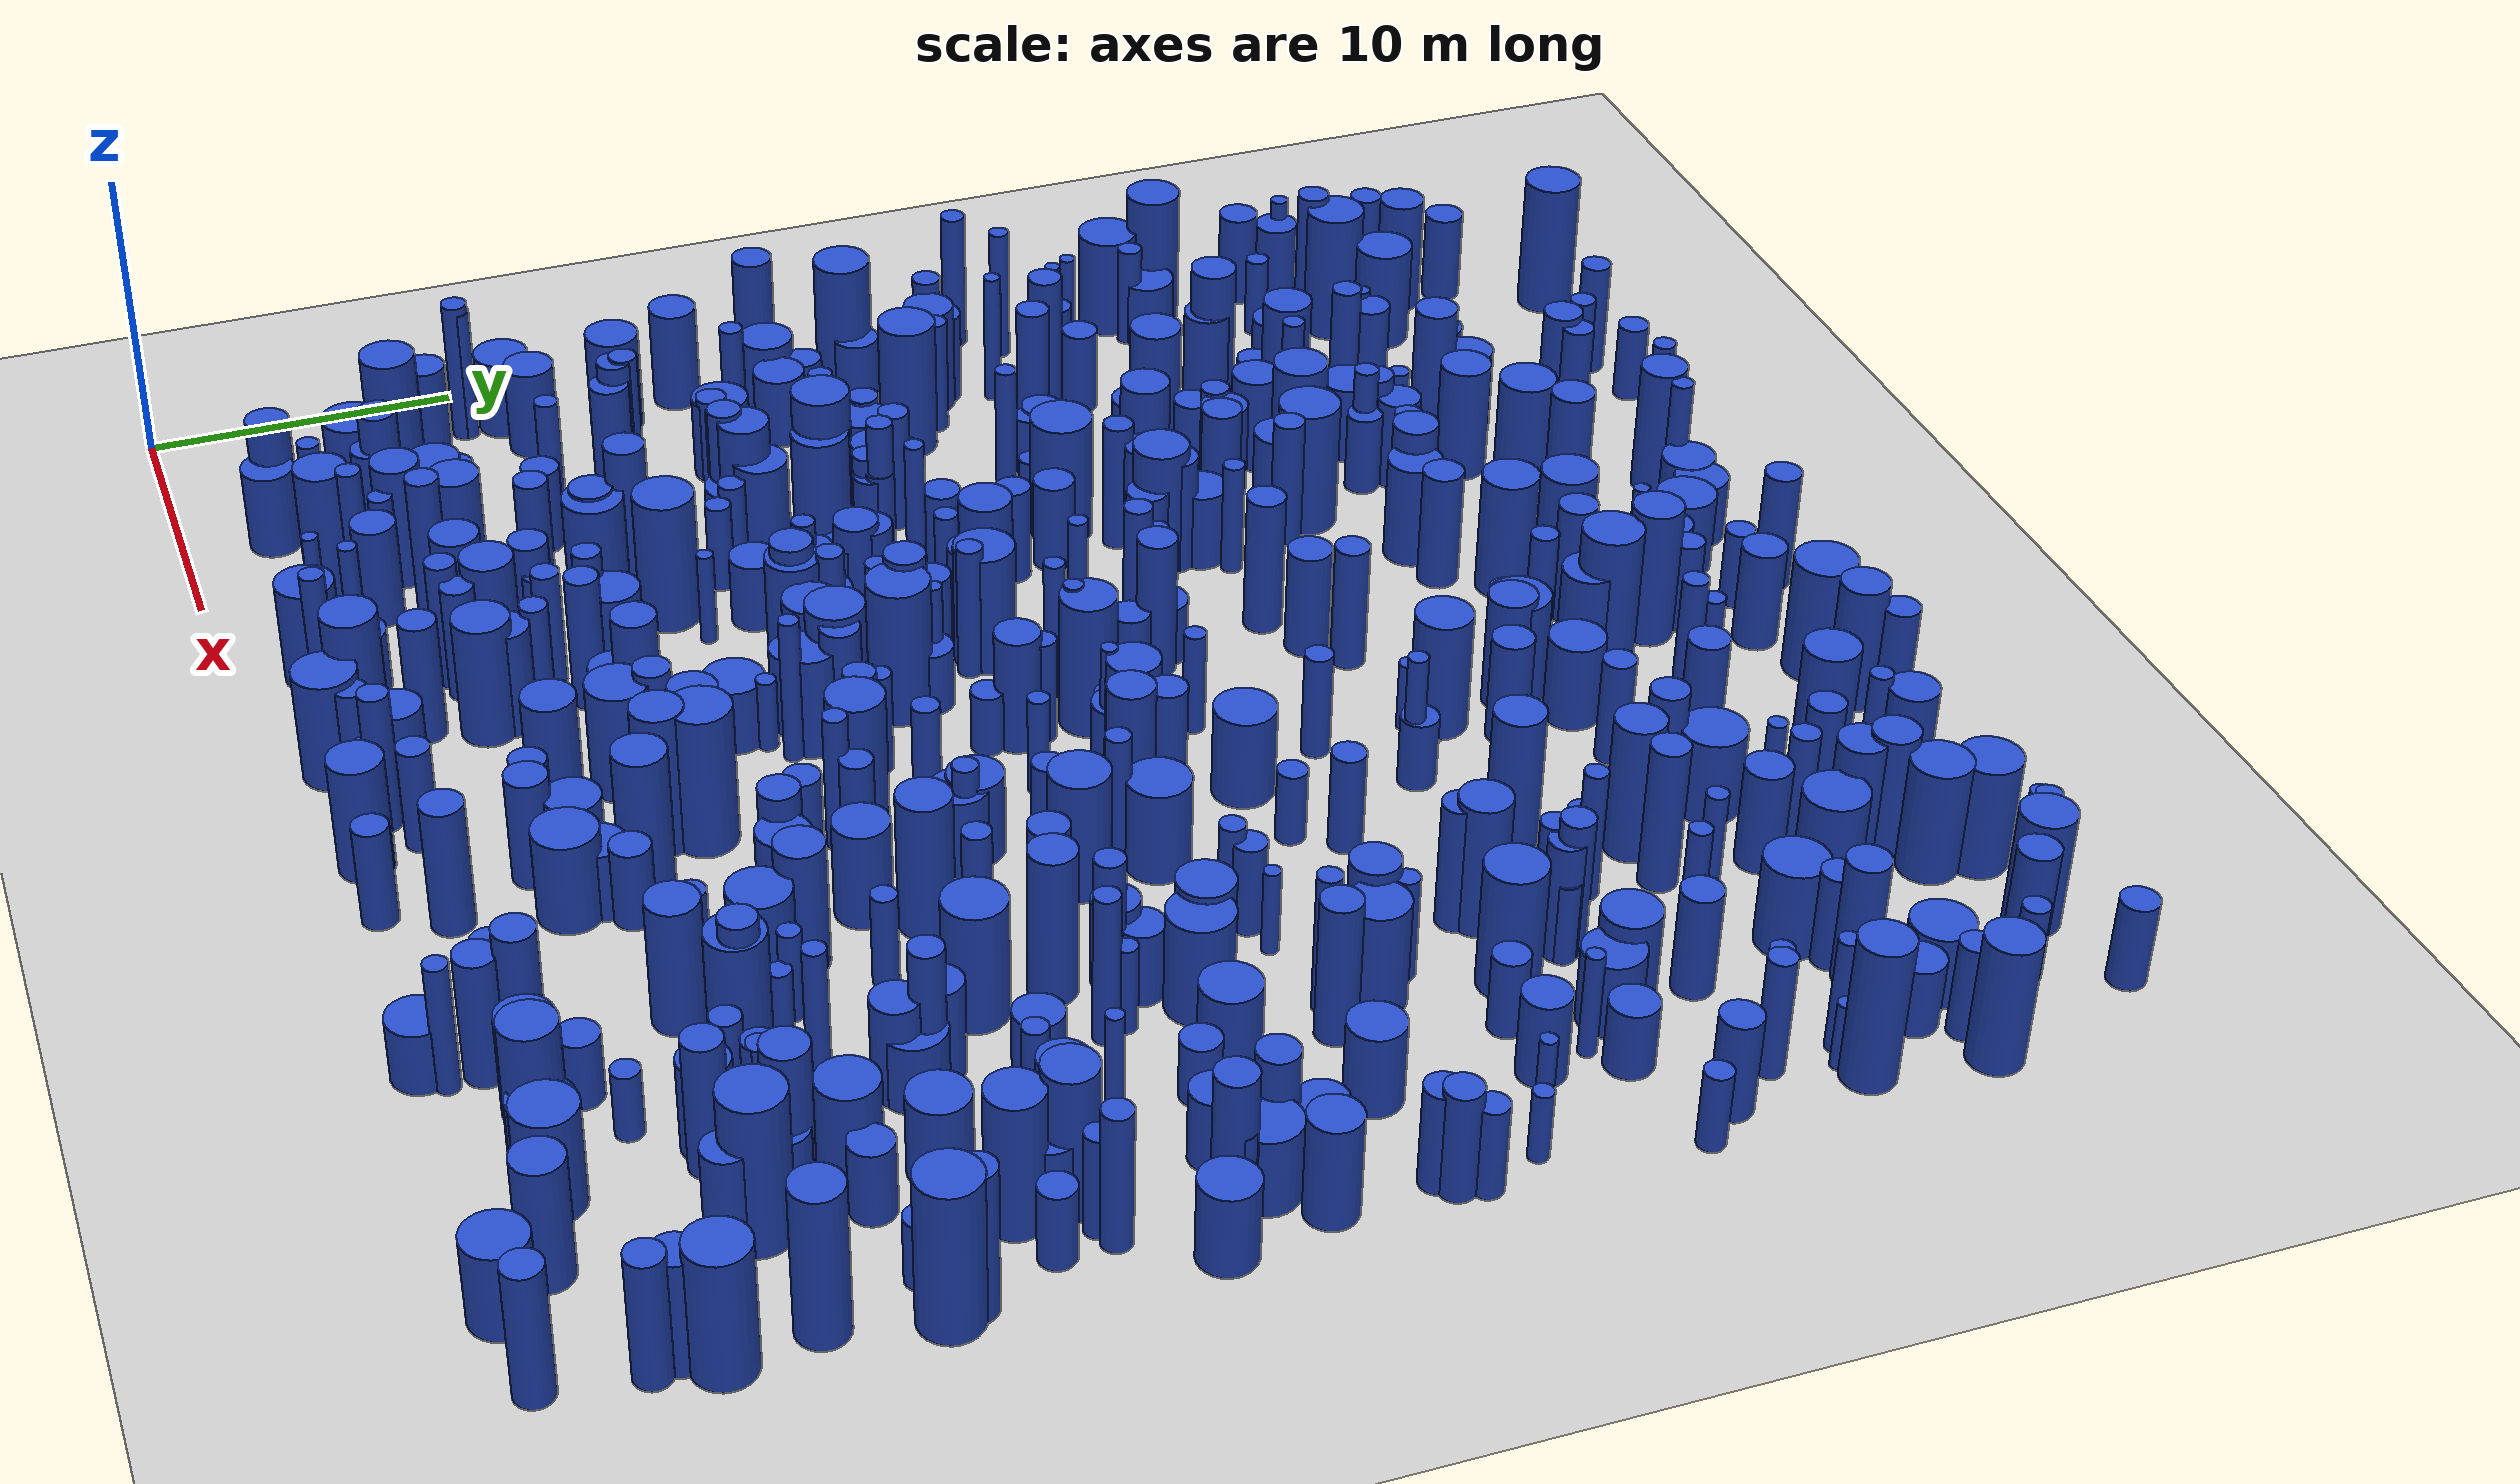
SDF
<sdf version="1.6">
 <world name="default">
  <plugin name="disable_physics" filename="libdisable_physics.so"/>
  <light name="sun" type="directional">
   <pose>0 0 10 0 -0 0</pose>
   <diffuse>0.8 0.8 0.8 1</diffuse>
   <specular>0.1 0.1 0.1 1</specular>
   <attenuation>
    <range>1000</range>
    <constant>0.9</constant>
    <linear>0.01</linear>
    <quadratic>0.001</quadratic>
   </attenuation>
   <direction>-0.5 0.5 -1</direction>
  </light>
  <model name="ground_plane">
   <static>1</static>
   <link name="link">
    <collision name="collision">
     <geometry><plane><normal>0 0 1</normal><size>100 100</size></plane></geometry>
     <surface><friction><ode><mu>100</mu><mu2>50</mu2></ode></friction></surface>
    </collision>
    <visual name="visual">
     <cast_shadows>0</cast_shadows>
     <geometry><plane><normal>0 0 1</normal><size>100 100</size></plane></geometry>
     <material>
      <script><uri>file://media/materials/scripts/gazebo.material</uri><name>Gazebo/Grey</name></script>
     </material>
    </visual>
   </link>
  </model>
  <gravity>0 0 -9.8</gravity>
  <magnetic_field>6e-06 2.3e-05 -4.2e-05</magnetic_field>
  <atmosphere type="adiabatic"/>
  <physics name="default_physics" default="0" type="ode">
   <max_step_size>0.001</max_step_size>
   <real_time_factor>1</real_time_factor>
   <real_time_update_rate>1000</real_time_update_rate>
  </physics>
  <scene><ambient>0.4 0.4 0.4 1</ambient><background>0.7 0.7 0.7 1</background><shadows>1</shadows></scene>
  <spherical_coordinates>
   <surface_model>EARTH_WGS84</surface_model>
   <latitude_deg>0</latitude_deg>
   <longitude_deg>0</longitude_deg>
   <elevation>0</elevation>
   <heading_deg>0</heading_deg>
  </spherical_coordinates>
  <model name="0">
   <static>0</static>
   <link name="link">
    <inertial>
     <mass>2</mass>
     <inertia><ixx>1.36996</ixx><ixy>0</ixy><ixz>0</ixz><iyy>1.36996</iyy><iyz>0</iyz><izz>0.08114</izz></inertia>
    </inertial>
    <collision name="collision">
     <geometry><cylinder><length>2.82424</length><radius>0.284851</radius></cylinder></geometry>
     <surface><contact><collide_without_contact>1</collide_without_contact></contact></surface>
    </collision>
    <visual name="visual">
     <geometry><cylinder><length>2.82424</length><radius>0.284851</radius></cylinder></geometry>
     <material>
      <script><uri>file://media/materials/scripts/gazebo.material</uri><name>Gazebo/Blue</name></script>
     </material>
    </visual>
    <gravity>0</gravity>
   </link>
   <pose>5.6814 47.6667 1.41212 0 -0 0</pose>
  </model>
  <model name="1">
   <static>0</static>
   <link name="link">
    <inertial>
     <mass>2</mass>
     <inertia>
      <ixx>1.04273</ixx>
      <ixy>0</ixy>
      <ixz>0</ixz>
      <iyy>1.04273</iyy>
      <iyz>0</iyz>
      <izz>0.0959348</izz>
     </inertia>
    </inertial>
    <collision name="collision">
     <geometry><cylinder><length>2.44307</length><radius>0.309734</radius></cylinder></geometry>
     <surface><contact><collide_without_contact>1</collide_without_contact></contact></surface>
    </collision>
    <visual name="visual">
     <geometry><cylinder><length>2.44307</length><radius>0.309734</radius></cylinder></geometry>
     <material>
      <script><uri>file://media/materials/scripts/gazebo.material</uri><name>Gazebo/Blue</name></script>
     </material>
    </visual>
    <gravity>0</gravity>
   </link>
   <pose>22.6289 14.9061 1.22153 0 -0 0</pose>
  </model>
  <model name="2">
   <static>0</static>
   <link name="link">
    <inertial>
     <mass>2</mass>
     <inertia><ixx>2.4592</ixx><ixy>0</ixy><ixz>0</ixz><iyy>2.4592</iyy><iyz>0</iyz><izz>0.847323</izz></inertia>
    </inertial>
    <collision name="collision">
     <geometry><cylinder><length>3.49474</length><radius>0.920501</radius></cylinder></geometry>
     <surface><contact><collide_without_contact>1</collide_without_contact></contact></surface>
    </collision>
    <visual name="visual">
     <geometry><cylinder><length>3.49474</length><radius>0.920501</radius></cylinder></geometry>
     <material>
      <script><uri>file://media/materials/scripts/gazebo.material</uri><name>Gazebo/Blue</name></script>
     </material>
    </visual>
    <gravity>0</gravity>
   </link>
   <pose>14.6339 2.72103 1.74737 0 -0 0</pose>
  </model>
  <model name="3">
   <static>0</static>
   <link name="link">
    <inertial>
     <mass>2</mass>
     <inertia><ixx>4.1115</ixx><ixy>0</ixy><ixz>0</ixz><iyy>4.1115</iyy><iyz>0</iyz><izz>0.173022</izz></inertia>
    </inertial>
    <collision name="collision">
     <geometry><cylinder><length>4.91426</length><radius>0.415959</radius></cylinder></geometry>
     <surface><contact><collide_without_contact>1</collide_without_contact></contact></surface>
    </collision>
    <visual name="visual">
     <geometry><cylinder><length>4.91426</length><radius>0.415959</radius></cylinder></geometry>
     <material>
      <script><uri>file://media/materials/scripts/gazebo.material</uri><name>Gazebo/Blue</name></script>
     </material>
    </visual>
    <gravity>0</gravity>
   </link>
   <pose>13.7823 21.1588 2.45713 0 -0 0</pose>
  </model>
  <model name="4">
   <static>0</static>
   <link name="link">
    <inertial>
     <mass>2</mass>
     <inertia><ixx>1.69462</ixx><ixy>0</ixy><ixz>0</ixz><iyy>1.69462</iyy><iyz>0</iyz><izz>0.206012</izz></inertia>
    </inertial>
    <collision name="collision">
     <geometry><cylinder><length>3.09026</length><radius>0.453885</radius></cylinder></geometry>
     <surface><contact><collide_without_contact>1</collide_without_contact></contact></surface>
    </collision>
    <visual name="visual">
     <geometry><cylinder><length>3.09026</length><radius>0.453885</radius></cylinder></geometry>
     <material>
      <script><uri>file://media/materials/scripts/gazebo.material</uri><name>Gazebo/Blue</name></script>
     </material>
    </visual>
    <gravity>0</gravity>
   </link>
   <pose>13.7872 21.1345 1.54513 0 -0 0</pose>
  </model>
  <model name="5">
   <static>0</static>
   <link name="link">
    <inertial>
     <mass>2</mass>
     <inertia><ixx>1.58752</ixx><ixy>0</ixy><ixz>0</ixz><iyy>1.58752</iyy><iyz>0</iyz><izz>0.355159</izz></inertia>
    </inertial>
    <collision name="collision">
     <geometry><cylinder><length>2.90855</length><radius>0.595952</radius></cylinder></geometry>
     <surface><contact><collide_without_contact>1</collide_without_contact></contact></surface>
    </collision>
    <visual name="visual">
     <geometry><cylinder><length>2.90855</length><radius>0.595952</radius></cylinder></geometry>
     <material>
      <script><uri>file://media/materials/scripts/gazebo.material</uri><name>Gazebo/Blue</name></script>
     </material>
    </visual>
    <gravity>0</gravity>
   </link>
   <pose>15.128 22.7537 1.45428 0 -0 0</pose>
  </model>
  <model name="6">
   <static>0</static>
   <link name="link">
    <inertial>
     <mass>2</mass>
     <inertia><ixx>1.20336</ixx><ixy>0</ixy><ixz>0</ixz><iyy>1.20336</iyy><iyz>0</iyz><izz>0.750486</izz></inertia>
    </inertial>
    <collision name="collision">
     <geometry><cylinder><length>2.22906</length><radius>0.866306</radius></cylinder></geometry>
     <surface><contact><collide_without_contact>1</collide_without_contact></contact></surface>
    </collision>
    <visual name="visual">
     <geometry><cylinder><length>2.22906</length><radius>0.866306</radius></cylinder></geometry>
     <material>
      <script><uri>file://media/materials/scripts/gazebo.material</uri><name>Gazebo/Blue</name></script>
     </material>
    </visual>
    <gravity>0</gravity>
   </link>
   <pose>20.0201 46.401 1.11453 0 -0 0</pose>
  </model>
  <model name="7">
   <static>0</static>
   <link name="link">
    <inertial>
     <mass>2</mass>
     <inertia><ixx>2.10084</ixx><ixy>0</ixy><ixz>0</ixz><iyy>2.10084</iyy><iyz>0</iyz><izz>0.955069</izz></inertia>
    </inertial>
    <collision name="collision">
     <geometry><cylinder><length>3.12087</length><radius>0.977276</radius></cylinder></geometry>
     <surface><contact><collide_without_contact>1</collide_without_contact></contact></surface>
    </collision>
    <visual name="visual">
     <geometry><cylinder><length>3.12087</length><radius>0.977276</radius></cylinder></geometry>
     <material>
      <script><uri>file://media/materials/scripts/gazebo.material</uri><name>Gazebo/Blue</name></script>
     </material>
    </visual>
    <gravity>0</gravity>
   </link>
   <pose>31.8249 23.959 1.56043 0 -0 0</pose>
  </model>
  <model name="8">
   <static>0</static>
   <link name="link">
    <inertial>
     <mass>2</mass>
     <inertia>
      <ixx>0.880956</ixx>
      <ixy>0</ixy>
      <ixz>0</ixz>
      <iyy>0.880956</iyy>
      <iyz>0</iyz>
      <izz>0.363118</izz>
     </inertia>
    </inertial>
    <collision name="collision">
     <geometry><cylinder><length>2.04851</length><radius>0.602593</radius></cylinder></geometry>
     <surface><contact><collide_without_contact>1</collide_without_contact></contact></surface>
    </collision>
    <visual name="visual">
     <geometry><cylinder><length>2.04851</length><radius>0.602593</radius></cylinder></geometry>
     <material>
      <script><uri>file://media/materials/scripts/gazebo.material</uri><name>Gazebo/Blue</name></script>
     </material>
    </visual>
    <gravity>0</gravity>
   </link>
   <pose>9.53747 35.5063 1.02425 0 -0 0</pose>
  </model>
  <model name="9">
   <static>0</static>
   <link name="link">
    <inertial>
     <mass>2</mass>
     <inertia>
      <ixx>2.25253</ixx>
      <ixy>0</ixy>
      <ixz>0</ixz>
      <iyy>2.25253</iyy>
      <iyz>0</iyz>
      <izz>0.0659071</izz>
     </inertia>
    </inertial>
    <collision name="collision">
     <geometry><cylinder><length>3.64931</length><radius>0.256724</radius></cylinder></geometry>
     <surface><contact><collide_without_contact>1</collide_without_contact></contact></surface>
    </collision>
    <visual name="visual">
     <geometry><cylinder><length>3.64931</length><radius>0.256724</radius></cylinder></geometry>
     <material>
      <script><uri>file://media/materials/scripts/gazebo.material</uri><name>Gazebo/Blue</name></script>
     </material>
    </visual>
    <gravity>0</gravity>
   </link>
   <pose>4.20875 30.1664 1.82465 0 -0 0</pose>
  </model>
  <model name="10">
   <static>0</static>
   <link name="link">
    <inertial>
     <mass>2</mass>
     <inertia><ixx>3.95554</ixx><ixy>0</ixy><ixz>0</ixz><iyy>3.95554</iyy><iyz>0</iyz><izz>0.519828</izz></inertia>
    </inertial>
    <collision name="collision">
     <geometry><cylinder><length>4.7089</length><radius>0.720991</radius></cylinder></geometry>
     <surface><contact><collide_without_contact>1</collide_without_contact></contact></surface>
    </collision>
    <visual name="visual">
     <geometry><cylinder><length>4.7089</length><radius>0.720991</radius></cylinder></geometry>
     <material>
      <script><uri>file://media/materials/scripts/gazebo.material</uri><name>Gazebo/Blue</name></script>
     </material>
    </visual>
    <gravity>0</gravity>
   </link>
   <pose>42.2217 16.8427 2.35445 0 -0 0</pose>
  </model>
  <model name="11">
   <static>0</static>
   <link name="link">
    <inertial>
     <mass>2</mass>
     <inertia><ixx>3.77059</ixx><ixy>0</ixy><ixz>0</ixz><iyy>3.77059</iyy><iyz>0</iyz><izz>0.647013</izz></inertia>
    </inertial>
    <collision name="collision">
     <geometry><cylinder><length>4.5478</length><radius>0.804371</radius></cylinder></geometry>
     <surface><contact><collide_without_contact>1</collide_without_contact></contact></surface>
    </collision>
    <visual name="visual">
     <geometry><cylinder><length>4.5478</length><radius>0.804371</radius></cylinder></geometry>
     <material>
      <script><uri>file://media/materials/scripts/gazebo.material</uri><name>Gazebo/Blue</name></script>
     </material>
    </visual>
    <gravity>0</gravity>
   </link>
   <pose>11.7835 8.00404 2.2739 0 -0 0</pose>
  </model>
  <model name="12">
   <static>0</static>
   <link name="link">
    <inertial>
     <mass>2</mass>
     <inertia>
      <ixx>0.906578</ixx>
      <ixy>0</ixy>
      <ixz>0</ixz>
      <iyy>0.906578</iyy>
      <iyz>0</iyz>
      <izz>0.435424</izz>
     </inertia>
    </inertial>
    <collision name="collision">
     <geometry><cylinder><length>2.03303</length><radius>0.659867</radius></cylinder></geometry>
     <surface><contact><collide_without_contact>1</collide_without_contact></contact></surface>
    </collision>
    <visual name="visual">
     <geometry><cylinder><length>2.03303</length><radius>0.659867</radius></cylinder></geometry>
     <material>
      <script><uri>file://media/materials/scripts/gazebo.material</uri><name>Gazebo/Blue</name></script>
     </material>
    </visual>
    <gravity>0</gravity>
   </link>
   <pose>16.4375 23.5707 1.01651 0 -0 0</pose>
  </model>
  <model name="13">
   <static>0</static>
   <link name="link">
    <inertial>
     <mass>2</mass>
     <inertia><ixx>1.12414</ixx><ixy>0</ixy><ixz>0</ixz><iyy>1.12414</iyy><iyz>0</iyz><izz>0.883734</izz></inertia>
    </inertial>
    <collision name="collision">
     <geometry><cylinder><length>2.02328</length><radius>0.940072</radius></cylinder></geometry>
     <surface><contact><collide_without_contact>1</collide_without_contact></contact></surface>
    </collision>
    <visual name="visual">
     <geometry><cylinder><length>2.02328</length><radius>0.940072</radius></cylinder></geometry>
     <material>
      <script><uri>file://media/materials/scripts/gazebo.material</uri><name>Gazebo/Blue</name></script>
     </material>
    </visual>
    <gravity>0</gravity>
   </link>
   <pose>5.86916 29.5655 1.01164 0 -0 0</pose>
  </model>
  <model name="14">
   <static>0</static>
   <link name="link">
    <inertial>
     <mass>2</mass>
     <inertia><ixx>3.20253</ixx><ixy>0</ixy><ixz>0</ixz><iyy>3.20253</iyy><iyz>0</iyz><izz>0.453423</izz></inertia>
    </inertial>
    <collision name="collision">
     <geometry><cylinder><length>4.22551</length><radius>0.673367</radius></cylinder></geometry>
     <surface><contact><collide_without_contact>1</collide_without_contact></contact></surface>
    </collision>
    <visual name="visual">
     <geometry><cylinder><length>4.22551</length><radius>0.673367</radius></cylinder></geometry>
     <material>
      <script><uri>file://media/materials/scripts/gazebo.material</uri><name>Gazebo/Blue</name></script>
     </material>
    </visual>
    <gravity>0</gravity>
   </link>
   <pose>7.31113 23.8893 2.11276 0 -0 0</pose>
  </model>
  <model name="15">
   <static>0</static>
   <link name="link">
    <inertial>
     <mass>2</mass>
     <inertia><ixx>2.62862</ixx><ixy>0</ixy><ixz>0</ixz><iyy>2.62862</iyy><iyz>0</iyz><izz>0.931065</izz></inertia>
    </inertial>
    <collision name="collision">
     <geometry><cylinder><length>3.60257</length><radius>0.964917</radius></cylinder></geometry>
     <surface><contact><collide_without_contact>1</collide_without_contact></contact></surface>
    </collision>
    <visual name="visual">
     <geometry><cylinder><length>3.60257</length><radius>0.964917</radius></cylinder></geometry>
     <material>
      <script><uri>file://media/materials/scripts/gazebo.material</uri><name>Gazebo/Blue</name></script>
     </material>
    </visual>
    <gravity>0</gravity>
   </link>
   <pose>27.3165 37.1361 1.80129 0 -0 0</pose>
  </model>
  <model name="16">
   <static>0</static>
   <link name="link">
    <inertial>
     <mass>2</mass>
     <inertia><ixx>1.97388</ixx><ixy>0</ixy><ixz>0</ixz><iyy>1.97388</iyy><iyz>0</iyz><izz>0.383371</izz></inertia>
    </inertial>
    <collision name="collision">
     <geometry><cylinder><length>3.27004</length><radius>0.619169</radius></cylinder></geometry>
     <surface><contact><collide_without_contact>1</collide_without_contact></contact></surface>
    </collision>
    <visual name="visual">
     <geometry><cylinder><length>3.27004</length><radius>0.619169</radius></cylinder></geometry>
     <material>
      <script><uri>file://media/materials/scripts/gazebo.material</uri><name>Gazebo/Blue</name></script>
     </material>
    </visual>
    <gravity>0</gravity>
   </link>
   <pose>46.7633 34.854 1.63502 0 -0 0</pose>
  </model>
  <model name="17">
   <static>0</static>
   <link name="link">
    <inertial>
     <mass>2</mass>
     <inertia><ixx>2.1683</ixx><ixy>0</ixy><ixz>0</ixz><iyy>2.1683</iyy><iyz>0</iyz><izz>0.244924</izz></inertia>
    </inertial>
    <collision name="collision">
     <geometry><cylinder><length>3.50357</length><radius>0.494898</radius></cylinder></geometry>
     <surface><contact><collide_without_contact>1</collide_without_contact></contact></surface>
    </collision>
    <visual name="visual">
     <geometry><cylinder><length>3.50357</length><radius>0.494898</radius></cylinder></geometry>
     <material>
      <script><uri>file://media/materials/scripts/gazebo.material</uri><name>Gazebo/Blue</name></script>
     </material>
    </visual>
    <gravity>0</gravity>
   </link>
   <pose>20.5912 2.97204 1.75179 0 -0 0</pose>
  </model>
  <model name="18">
   <static>0</static>
   <link name="link">
    <inertial>
     <mass>2</mass>
     <inertia><ixx>4.07132</ixx><ixy>0</ixy><ixz>0</ixz><iyy>4.07132</iyy><iyz>0</iyz><izz>0.25791</izz></inertia>
    </inertial>
    <collision name="collision">
     <geometry><cylinder><length>4.86356</length><radius>0.507848</radius></cylinder></geometry>
     <surface><contact><collide_without_contact>1</collide_without_contact></contact></surface>
    </collision>
    <visual name="visual">
     <geometry><cylinder><length>4.86356</length><radius>0.507848</radius></cylinder></geometry>
     <material>
      <script><uri>file://media/materials/scripts/gazebo.material</uri><name>Gazebo/Blue</name></script>
     </material>
    </visual>
    <gravity>0</gravity>
   </link>
   <pose>38.9741 14.813 2.43178 0 -0 0</pose>
  </model>
  <model name="19">
   <static>0</static>
   <link name="link">
    <inertial>
     <mass>2</mass>
     <inertia>
      <ixx>0.997922</ixx>
      <ixy>0</ixy>
      <ixz>0</ixz>
      <iyy>0.997922</iyy>
      <iyz>0</iyz>
      <izz>0.310025</izz>
     </inertia>
    </inertial>
    <collision name="collision">
     <geometry><cylinder><length>2.24888</length><radius>0.556799</radius></cylinder></geometry>
     <surface><contact><collide_without_contact>1</collide_without_contact></contact></surface>
    </collision>
    <visual name="visual">
     <geometry><cylinder><length>2.24888</length><radius>0.556799</radius></cylinder></geometry>
     <material>
      <script><uri>file://media/materials/scripts/gazebo.material</uri><name>Gazebo/Blue</name></script>
     </material>
    </visual>
    <gravity>0</gravity>
   </link>
   <pose>6.32254 2.75765 1.12444 0 -0 0</pose>
  </model>
  <model name="20">
   <static>0</static>
   <link name="link">
    <inertial>
     <mass>2</mass>
     <inertia><ixx>4.13593</ixx><ixy>0</ixy><ixz>0</ixz><iyy>4.13593</iyy><iyz>0</iyz><izz>0.377057</izz></inertia>
    </inertial>
    <collision name="collision">
     <geometry><cylinder><length>4.86666</length><radius>0.614049</radius></cylinder></geometry>
     <surface><contact><collide_without_contact>1</collide_without_contact></contact></surface>
    </collision>
    <visual name="visual">
     <geometry><cylinder><length>4.86666</length><radius>0.614049</radius></cylinder></geometry>
     <material>
      <script><uri>file://media/materials/scripts/gazebo.material</uri><name>Gazebo/Blue</name></script>
     </material>
    </visual>
    <gravity>0</gravity>
   </link>
   <pose>46.3124 20.7601 2.43333 0 -0 0</pose>
  </model>
  <model name="21">
   <static>0</static>
   <link name="link">
    <inertial>
     <mass>2</mass>
     <inertia>
      <ixx>1.75689</ixx>
      <ixy>0</ixy>
      <ixz>0</ixz>
      <iyy>1.75689</iyy>
      <iyz>0</iyz>
      <izz>0.0651823</izz>
     </inertia>
    </inertial>
    <collision name="collision">
     <geometry><cylinder><length>3.21648</length><radius>0.255308</radius></cylinder></geometry>
     <surface><contact><collide_without_contact>1</collide_without_contact></contact></surface>
    </collision>
    <visual name="visual">
     <geometry><cylinder><length>3.21648</length><radius>0.255308</radius></cylinder></geometry>
     <material>
      <script><uri>file://media/materials/scripts/gazebo.material</uri><name>Gazebo/Blue</name></script>
     </material>
    </visual>
    <gravity>0</gravity>
   </link>
   <pose>8.77724 4.1816 1.60824 0 -0 0</pose>
  </model>
  <model name="22">
   <static>0</static>
   <link name="link">
    <inertial>
     <mass>2</mass>
     <inertia><ixx>2.50621</ixx><ixy>0</ixy><ixz>0</ixz><iyy>2.50621</iyy><iyz>0</iyz><izz>0.412755</izz></inertia>
    </inertial>
    <collision name="collision">
     <geometry><cylinder><length>3.7147</length><radius>0.64246</radius></cylinder></geometry>
     <surface><contact><collide_without_contact>1</collide_without_contact></contact></surface>
    </collision>
    <visual name="visual">
     <geometry><cylinder><length>3.7147</length><radius>0.64246</radius></cylinder></geometry>
     <material>
      <script><uri>file://media/materials/scripts/gazebo.material</uri><name>Gazebo/Blue</name></script>
     </material>
    </visual>
    <gravity>0</gravity>
   </link>
   <pose>6.86482 14.0884 1.85735 0 -0 0</pose>
  </model>
  <model name="23">
   <static>0</static>
   <link name="link">
    <inertial>
     <mass>2</mass>
     <inertia>
      <ixx>1.99669</ixx>
      <ixy>0</ixy>
      <ixz>0</ixz>
      <iyy>1.99669</iyy>
      <iyz>0</iyz>
      <izz>0.0728803</izz>
     </inertia>
    </inertial>
    <collision name="collision">
     <geometry><cylinder><length>3.42951</length><radius>0.269963</radius></cylinder></geometry>
     <surface><contact><collide_without_contact>1</collide_without_contact></contact></surface>
    </collision>
    <visual name="visual">
     <geometry><cylinder><length>3.42951</length><radius>0.269963</radius></cylinder></geometry>
     <material>
      <script><uri>file://media/materials/scripts/gazebo.material</uri><name>Gazebo/Blue</name></script>
     </material>
    </visual>
    <gravity>0</gravity>
   </link>
   <pose>43.393 32.1814 1.71475 0 -0 0</pose>
  </model>
  <model name="24">
   <static>0</static>
   <link name="link">
    <inertial>
     <mass>2</mass>
     <inertia><ixx>2.24741</ixx><ixy>0</ixy><ixz>0</ixz><iyy>2.24741</iyy><iyz>0</iyz><izz>0.278521</izz></inertia>
    </inertial>
    <collision name="collision">
     <geometry><cylinder><length>3.55653</length><radius>0.527751</radius></cylinder></geometry>
     <surface><contact><collide_without_contact>1</collide_without_contact></contact></surface>
    </collision>
    <visual name="visual">
     <geometry><cylinder><length>3.55653</length><radius>0.527751</radius></cylinder></geometry>
     <material>
      <script><uri>file://media/materials/scripts/gazebo.material</uri><name>Gazebo/Blue</name></script>
     </material>
    </visual>
    <gravity>0</gravity>
   </link>
   <pose>2.92159 42.1563 1.77827 0 -0 0</pose>
  </model>
  <model name="25">
   <static>0</static>
   <link name="link">
    <inertial>
     <mass>2</mass>
     <inertia><ixx>3.21255</ixx><ixy>0</ixy><ixz>0</ixz><iyy>3.21255</iyy><iyz>0</iyz><izz>0.847452</izz></inertia>
    </inertial>
    <collision name="collision">
     <geometry><cylinder><length>4.0906</length><radius>0.920571</radius></cylinder></geometry>
     <surface><contact><collide_without_contact>1</collide_without_contact></contact></surface>
    </collision>
    <visual name="visual">
     <geometry><cylinder><length>4.0906</length><radius>0.920571</radius></cylinder></geometry>
     <material>
      <script><uri>file://media/materials/scripts/gazebo.material</uri><name>Gazebo/Blue</name></script>
     </material>
    </visual>
    <gravity>0</gravity>
   </link>
   <pose>31.9637 21.5128 2.0453 0 -0 0</pose>
  </model>
  <model name="26">
   <static>0</static>
   <link name="link">
    <inertial>
     <mass>2</mass>
     <inertia><ixx>1.52925</ixx><ixy>0</ixy><ixz>0</ixz><iyy>1.52925</iyy><iyz>0</iyz><izz>0.603809</izz></inertia>
    </inertial>
    <collision name="collision">
     <geometry><cylinder><length>2.71368</length><radius>0.777051</radius></cylinder></geometry>
     <surface><contact><collide_without_contact>1</collide_without_contact></contact></surface>
    </collision>
    <visual name="visual">
     <geometry><cylinder><length>2.71368</length><radius>0.777051</radius></cylinder></geometry>
     <material>
      <script><uri>file://media/materials/scripts/gazebo.material</uri><name>Gazebo/Blue</name></script>
     </material>
    </visual>
    <gravity>0</gravity>
   </link>
   <pose>16.7592 22.9378 1.35684 0 -0 0</pose>
  </model>
  <model name="27">
   <static>0</static>
   <link name="link">
    <inertial>
     <mass>2</mass>
     <inertia><ixx>1.09126</ixx><ixy>0</ixy><ixz>0</ixz><iyy>1.09126</iyy><iyz>0</iyz><izz>0.36449</izz></inertia>
    </inertial>
    <collision name="collision">
     <geometry><cylinder><length>2.3354</length><radius>0.60373</radius></cylinder></geometry>
     <surface><contact><collide_without_contact>1</collide_without_contact></contact></surface>
    </collision>
    <visual name="visual">
     <geometry><cylinder><length>2.3354</length><radius>0.60373</radius></cylinder></geometry>
     <material>
      <script><uri>file://media/materials/scripts/gazebo.material</uri><name>Gazebo/Blue</name></script>
     </material>
    </visual>
    <gravity>0</gravity>
   </link>
   <pose>5.09837 21.0818 1.1677 0 -0 0</pose>
  </model>
  <model name="28">
   <static>0</static>
   <link name="link">
    <inertial>
     <mass>2</mass>
     <inertia><ixx>4.33046</ixx><ixy>0</ixy><ixz>0</ixz><iyy>4.33046</iyy><iyz>0</iyz><izz>0.751665</izz></inertia>
    </inertial>
    <collision name="collision">
     <geometry><cylinder><length>4.87112</length><radius>0.866986</radius></cylinder></geometry>
     <surface><contact><collide_without_contact>1</collide_without_contact></contact></surface>
    </collision>
    <visual name="visual">
     <geometry><cylinder><length>4.87112</length><radius>0.866986</radius></cylinder></geometry>
     <material>
      <script><uri>file://media/materials/scripts/gazebo.material</uri><name>Gazebo/Blue</name></script>
     </material>
    </visual>
    <gravity>0</gravity>
   </link>
   <pose>18.6765 3.41081 2.43556 0 -0 0</pose>
  </model>
  <model name="29">
   <static>0</static>
   <link name="link">
    <inertial>
     <mass>2</mass>
     <inertia><ixx>3.4064</ixx><ixy>0</ixy><ixz>0</ixz><iyy>3.4064</iyy><iyz>0</iyz><izz>0.0952166</izz></inertia>
    </inertial>
    <collision name="collision">
     <geometry><cylinder><length>4.48918</length><radius>0.308572</radius></cylinder></geometry>
     <surface><contact><collide_without_contact>1</collide_without_contact></contact></surface>
    </collision>
    <visual name="visual">
     <geometry><cylinder><length>4.48918</length><radius>0.308572</radius></cylinder></geometry>
     <material>
      <script><uri>file://media/materials/scripts/gazebo.material</uri><name>Gazebo/Blue</name></script>
     </material>
    </visual>
    <gravity>0</gravity>
   </link>
   <pose>20.4595 25.4538 2.24459 0 -0 0</pose>
  </model>
  <model name="30">
   <static>0</static>
   <link name="link">
    <inertial>
     <mass>2</mass>
     <inertia><ixx>2.75593</ixx><ixy>0</ixy><ixz>0</ixz><iyy>2.75593</iyy><iyz>0</iyz><izz>0.688056</izz></inertia>
    </inertial>
    <collision name="collision">
     <geometry><cylinder><length>3.80413</length><radius>0.829491</radius></cylinder></geometry>
     <surface><contact><collide_without_contact>1</collide_without_contact></contact></surface>
    </collision>
    <visual name="visual">
     <geometry><cylinder><length>3.80413</length><radius>0.829491</radius></cylinder></geometry>
     <material>
      <script><uri>file://media/materials/scripts/gazebo.material</uri><name>Gazebo/Blue</name></script>
     </material>
    </visual>
    <gravity>0</gravity>
   </link>
   <pose>5.5824 25.3243 1.90206 0 -0 0</pose>
  </model>
  <model name="31">
   <static>0</static>
   <link name="link">
    <inertial>
     <mass>2</mass>
     <inertia><ixx>3.2928</ixx><ixy>0</ixy><ixz>0</ixz><iyy>3.2928</iyy><iyz>0</iyz><izz>0.138663</izz></inertia>
    </inertial>
    <collision name="collision">
     <geometry><cylinder><length>4.39782</length><radius>0.372375</radius></cylinder></geometry>
     <surface><contact><collide_without_contact>1</collide_without_contact></contact></surface>
    </collision>
    <visual name="visual">
     <geometry><cylinder><length>4.39782</length><radius>0.372375</radius></cylinder></geometry>
     <material>
      <script><uri>file://media/materials/scripts/gazebo.material</uri><name>Gazebo/Blue</name></script>
     </material>
    </visual>
    <gravity>0</gravity>
   </link>
   <pose>16.6334 46.9755 2.19891 0 -0 0</pose>
  </model>
  <model name="32">
   <static>0</static>
   <link name="link">
    <inertial>
     <mass>2</mass>
     <inertia><ixx>2.55489</ixx><ixy>0</ixy><ixz>0</ixz><iyy>2.55489</iyy><iyz>0</iyz><izz>0.788576</izz></inertia>
    </inertial>
    <collision name="collision">
     <geometry><cylinder><length>3.6005</length><radius>0.888018</radius></cylinder></geometry>
     <surface><contact><collide_without_contact>1</collide_without_contact></contact></surface>
    </collision>
    <visual name="visual">
     <geometry><cylinder><length>3.6005</length><radius>0.888018</radius></cylinder></geometry>
     <material>
      <script><uri>file://media/materials/scripts/gazebo.material</uri><name>Gazebo/Blue</name></script>
     </material>
    </visual>
    <gravity>0</gravity>
   </link>
   <pose>12.5968 17.555 1.80025 0 -0 0</pose>
  </model>
  <model name="33">
   <static>0</static>
   <link name="link">
    <inertial>
     <mass>2</mass>
     <inertia><ixx>3.32594</ixx><ixy>0</ixy><ixz>0</ixz><iyy>3.32594</iyy><iyz>0</iyz><izz>0.675286</izz></inertia>
    </inertial>
    <collision name="collision">
     <geometry><cylinder><length>4.23436</length><radius>0.821758</radius></cylinder></geometry>
     <surface><contact><collide_without_contact>1</collide_without_contact></contact></surface>
    </collision>
    <visual name="visual">
     <geometry><cylinder><length>4.23436</length><radius>0.821758</radius></cylinder></geometry>
     <material>
      <script><uri>file://media/materials/scripts/gazebo.material</uri><name>Gazebo/Blue</name></script>
     </material>
    </visual>
    <gravity>0</gravity>
   </link>
   <pose>47.2032 42.5605 2.11718 0 -0 0</pose>
  </model>
  <model name="34">
   <static>0</static>
   <link name="link">
    <inertial>
     <mass>2</mass>
     <inertia><ixx>2.04762</ixx><ixy>0</ixy><ixz>0</ixz><iyy>2.04762</iyy><iyz>0</iyz><izz>0.252697</izz></inertia>
    </inertial>
    <collision name="collision">
     <geometry><cylinder><length>3.39524</length><radius>0.502689</radius></cylinder></geometry>
     <surface><contact><collide_without_contact>1</collide_without_contact></contact></surface>
    </collision>
    <visual name="visual">
     <geometry><cylinder><length>3.39524</length><radius>0.502689</radius></cylinder></geometry>
     <material>
      <script><uri>file://media/materials/scripts/gazebo.material</uri><name>Gazebo/Blue</name></script>
     </material>
    </visual>
    <gravity>0</gravity>
   </link>
   <pose>28.5365 15.9625 1.69762 0 -0 0</pose>
  </model>
  <model name="35">
   <static>0</static>
   <link name="link">
    <inertial>
     <mass>2</mass>
     <inertia><ixx>3.57551</ixx><ixy>0</ixy><ixz>0</ixz><iyy>3.57551</iyy><iyz>0</iyz><izz>0.622149</izz></inertia>
    </inertial>
    <collision name="collision">
     <geometry><cylinder><length>4.42568</length><radius>0.788764</radius></cylinder></geometry>
     <surface><contact><collide_without_contact>1</collide_without_contact></contact></surface>
    </collision>
    <visual name="visual">
     <geometry><cylinder><length>4.42568</length><radius>0.788764</radius></cylinder></geometry>
     <material>
      <script><uri>file://media/materials/scripts/gazebo.material</uri><name>Gazebo/Blue</name></script>
     </material>
    </visual>
    <gravity>0</gravity>
   </link>
   <pose>37.2175 31.6348 2.21284 0 -0 0</pose>
  </model>
  <model name="36">
   <static>0</static>
   <link name="link">
    <inertial>
     <mass>2</mass>
     <inertia><ixx>2.47359</ixx><ixy>0</ixy><ixz>0</ixz><iyy>2.47359</iyy><iyz>0</iyz><izz>0.571806</izz></inertia>
    </inertial>
    <collision name="collision">
     <geometry><cylinder><length>3.623</length><radius>0.756179</radius></cylinder></geometry>
     <surface><contact><collide_without_contact>1</collide_without_contact></contact></surface>
    </collision>
    <visual name="visual">
     <geometry><cylinder><length>3.623</length><radius>0.756179</radius></cylinder></geometry>
     <material>
      <script><uri>file://media/materials/scripts/gazebo.material</uri><name>Gazebo/Blue</name></script>
     </material>
    </visual>
    <gravity>0</gravity>
   </link>
   <pose>19.0534 7.89403 1.8115 0 -0 0</pose>
  </model>
  <model name="37">
   <static>0</static>
   <link name="link">
    <inertial>
     <mass>2</mass>
     <inertia><ixx>3.28854</ixx><ixy>0</ixy><ixz>0</ixz><iyy>3.28854</iyy><iyz>0</iyz><izz>0.530708</izz></inertia>
    </inertial>
    <collision name="collision">
     <geometry><cylinder><length>4.259</length><radius>0.728497</radius></cylinder></geometry>
     <surface><contact><collide_without_contact>1</collide_without_contact></contact></surface>
    </collision>
    <visual name="visual">
     <geometry><cylinder><length>4.259</length><radius>0.728497</radius></cylinder></geometry>
     <material>
      <script><uri>file://media/materials/scripts/gazebo.material</uri><name>Gazebo/Blue</name></script>
     </material>
    </visual>
    <gravity>0</gravity>
   </link>
   <pose>18.3013 37.5129 2.1295 0 -0 0</pose>
  </model>
  <model name="38">
   <static>0</static>
   <link name="link">
    <inertial>
     <mass>2</mass>
     <inertia><ixx>1.8464</ixx><ixy>0</ixy><ixz>0</ixz><iyy>1.8464</iyy><iyz>0</iyz><izz>0.210959</izz></inertia>
    </inertial>
    <collision name="collision">
     <geometry><cylinder><length>3.23195</length><radius>0.459303</radius></cylinder></geometry>
     <surface><contact><collide_without_contact>1</collide_without_contact></contact></surface>
    </collision>
    <visual name="visual">
     <geometry><cylinder><length>3.23195</length><radius>0.459303</radius></cylinder></geometry>
     <material>
      <script><uri>file://media/materials/scripts/gazebo.material</uri><name>Gazebo/Blue</name></script>
     </material>
    </visual>
    <gravity>0</gravity>
   </link>
   <pose>11.6565 21.8837 1.61598 0 -0 0</pose>
  </model>
  <model name="39">
   <static>0</static>
   <link name="link">
    <inertial>
     <mass>2</mass>
     <inertia><ixx>1.9999</ixx><ixy>0</ixy><ixz>0</ixz><iyy>1.9999</iyy><iyz>0</iyz><izz>0.310791</izz></inertia>
    </inertial>
    <collision name="collision">
     <geometry><cylinder><length>3.32671</length><radius>0.557487</radius></cylinder></geometry>
     <surface><contact><collide_without_contact>1</collide_without_contact></contact></surface>
    </collision>
    <visual name="visual">
     <geometry><cylinder><length>3.32671</length><radius>0.557487</radius></cylinder></geometry>
     <material>
      <script><uri>file://media/materials/scripts/gazebo.material</uri><name>Gazebo/Blue</name></script>
     </material>
    </visual>
    <gravity>0</gravity>
   </link>
   <pose>46.8839 26.2899 1.66335 0 -0 0</pose>
  </model>
  <model name="40">
   <static>0</static>
   <link name="link">
    <inertial>
     <mass>2</mass>
     <inertia><ixx>1.69462</ixx><ixy>0</ixy><ixz>0</ixz><iyy>1.69462</iyy><iyz>0</iyz><izz>0.809361</izz></inertia>
    </inertial>
    <collision name="collision">
     <geometry><cylinder><length>2.78202</length><radius>0.899645</radius></cylinder></geometry>
     <surface><contact><collide_without_contact>1</collide_without_contact></contact></surface>
    </collision>
    <visual name="visual">
     <geometry><cylinder><length>2.78202</length><radius>0.899645</radius></cylinder></geometry>
     <material>
      <script><uri>file://media/materials/scripts/gazebo.material</uri><name>Gazebo/Blue</name></script>
     </material>
    </visual>
    <gravity>0</gravity>
   </link>
   <pose>2.25113 11.4808 1.39101 0 -0 0</pose>
  </model>
  <model name="41">
   <static>0</static>
   <link name="link">
    <inertial>
     <mass>2</mass>
     <inertia>
      <ixx>2.56622</ixx>
      <ixy>0</ixy>
      <ixz>0</ixz>
      <iyy>2.56622</iyy>
      <iyz>0</iyz>
      <izz>0.0997864</izz>
     </inertia>
    </inertial>
    <collision name="collision">
     <geometry><cylinder><length>3.88561</length><radius>0.31589</radius></cylinder></geometry>
     <surface><contact><collide_without_contact>1</collide_without_contact></contact></surface>
    </collision>
    <visual name="visual">
     <geometry><cylinder><length>3.88561</length><radius>0.31589</radius></cylinder></geometry>
     <material>
      <script><uri>file://media/materials/scripts/gazebo.material</uri><name>Gazebo/Blue</name></script>
     </material>
    </visual>
    <gravity>0</gravity>
   </link>
   <pose>6.3063 47.4544 1.9428 0 -0 0</pose>
  </model>
  <model name="42">
   <static>0</static>
   <link name="link">
    <inertial>
     <mass>2</mass>
     <inertia><ixx>1.89672</ixx><ixy>0</ixy><ixz>0</ixz><iyy>1.89672</iyy><iyz>0</iyz><izz>0.219729</izz></inertia>
    </inertial>
    <collision name="collision">
     <geometry><cylinder><length>3.27432</length><radius>0.468753</radius></cylinder></geometry>
     <surface><contact><collide_without_contact>1</collide_without_contact></contact></surface>
    </collision>
    <visual name="visual">
     <geometry><cylinder><length>3.27432</length><radius>0.468753</radius></cylinder></geometry>
     <material>
      <script><uri>file://media/materials/scripts/gazebo.material</uri><name>Gazebo/Blue</name></script>
     </material>
    </visual>
    <gravity>0</gravity>
   </link>
   <pose>12.7332 32.8428 1.63716 0 -0 0</pose>
  </model>
  <model name="43">
   <static>0</static>
   <link name="link">
    <inertial>
     <mass>2</mass>
     <inertia>
      <ixx>0.804984</ixx>
      <ixy>0</ixy>
      <ixz>0</ixz>
      <iyy>0.804984</iyy>
      <iyz>0</iyz>
      <izz>0.236242</izz>
     </inertia>
    </inertial>
    <collision name="collision">
     <geometry><cylinder><length>2.03007</length><radius>0.486048</radius></cylinder></geometry>
     <surface><contact><collide_without_contact>1</collide_without_contact></contact></surface>
    </collision>
    <visual name="visual">
     <geometry><cylinder><length>2.03007</length><radius>0.486048</radius></cylinder></geometry>
     <material>
      <script><uri>file://media/materials/scripts/gazebo.material</uri><name>Gazebo/Blue</name></script>
     </material>
    </visual>
    <gravity>0</gravity>
   </link>
   <pose>27.3471 47.9507 1.01503 0 -0 0</pose>
  </model>
  <model name="44">
   <static>0</static>
   <link name="link">
    <inertial>
     <mass>2</mass>
     <inertia><ixx>4.17462</ixx><ixy>0</ixy><ixz>0</ixz><iyy>4.17462</iyy><iyz>0</iyz><izz>0.119229</izz></inertia>
    </inertial>
    <collision name="collision">
     <geometry><cylinder><length>4.96891</length><radius>0.345295</radius></cylinder></geometry>
     <surface><contact><collide_without_contact>1</collide_without_contact></contact></surface>
    </collision>
    <visual name="visual">
     <geometry><cylinder><length>4.96891</length><radius>0.345295</radius></cylinder></geometry>
     <material>
      <script><uri>file://media/materials/scripts/gazebo.material</uri><name>Gazebo/Blue</name></script>
     </material>
    </visual>
    <gravity>0</gravity>
   </link>
   <pose>36.1613 44.4005 2.48445 0 -0 0</pose>
  </model>
  <model name="45">
   <static>0</static>
   <link name="link">
    <inertial>
     <mass>2</mass>
     <inertia><ixx>3.37145</ixx><ixy>0</ixy><ixz>0</ixz><iyy>3.37145</iyy><iyz>0</iyz><izz>0.593405</izz></inertia>
    </inertial>
    <collision name="collision">
     <geometry><cylinder><length>4.29517</length><radius>0.770328</radius></cylinder></geometry>
     <surface><contact><collide_without_contact>1</collide_without_contact></contact></surface>
    </collision>
    <visual name="visual">
     <geometry><cylinder><length>4.29517</length><radius>0.770328</radius></cylinder></geometry>
     <material>
      <script><uri>file://media/materials/scripts/gazebo.material</uri><name>Gazebo/Blue</name></script>
     </material>
    </visual>
    <gravity>0</gravity>
   </link>
   <pose>10.0825 6.46261 2.14758 0 -0 0</pose>
  </model>
  <model name="46">
   <static>0</static>
   <link name="link">
    <inertial>
     <mass>2</mass>
     <inertia><ixx>4.24125</ixx><ixy>0</ixy><ixz>0</ixz><iyy>4.24125</iyy><iyz>0</iyz><izz>0.418546</izz></inertia>
    </inertial>
    <collision name="collision">
     <geometry><cylinder><length>4.91852</length><radius>0.646951</radius></cylinder></geometry>
     <surface><contact><collide_without_contact>1</collide_without_contact></contact></surface>
    </collision>
    <visual name="visual">
     <geometry><cylinder><length>4.91852</length><radius>0.646951</radius></cylinder></geometry>
     <material>
      <script><uri>file://media/materials/scripts/gazebo.material</uri><name>Gazebo/Blue</name></script>
     </material>
    </visual>
    <gravity>0</gravity>
   </link>
   <pose>21.0936 19.7391 2.45926 0 -0 0</pose>
  </model>
  <model name="47">
   <static>0</static>
   <link name="link">
    <inertial>
     <mass>2</mass>
     <inertia><ixx>4.30581</ixx><ixy>0</ixy><ixz>0</ixz><iyy>4.30581</iyy><iyz>0</iyz><izz>0.874701</izz></inertia>
    </inertial>
    <collision name="collision">
     <geometry><cylinder><length>4.81775</length><radius>0.935255</radius></cylinder></geometry>
     <surface><contact><collide_without_contact>1</collide_without_contact></contact></surface>
    </collision>
    <visual name="visual">
     <geometry><cylinder><length>4.81775</length><radius>0.935255</radius></cylinder></geometry>
     <material>
      <script><uri>file://media/materials/scripts/gazebo.material</uri><name>Gazebo/Blue</name></script>
     </material>
    </visual>
    <gravity>0</gravity>
   </link>
   <pose>11.1965 19.9775 2.40888 0 -0 0</pose>
  </model>
  <model name="48">
   <static>0</static>
   <link name="link">
    <inertial>
     <mass>2</mass>
     <inertia><ixx>3.38207</ixx><ixy>0</ixy><ixz>0</ixz><iyy>3.38207</iyy><iyz>0</iyz><izz>0.486769</izz></inertia>
    </inertial>
    <collision name="collision">
     <geometry><cylinder><length>4.3396</length><radius>0.697689</radius></cylinder></geometry>
     <surface><contact><collide_without_contact>1</collide_without_contact></contact></surface>
    </collision>
    <visual name="visual">
     <geometry><cylinder><length>4.3396</length><radius>0.697689</radius></cylinder></geometry>
     <material>
      <script><uri>file://media/materials/scripts/gazebo.material</uri><name>Gazebo/Blue</name></script>
     </material>
    </visual>
    <gravity>0</gravity>
   </link>
   <pose>20.7865 11.4476 2.1698 0 -0 0</pose>
  </model>
  <model name="49">
   <static>0</static>
   <link name="link">
    <inertial>
     <mass>2</mass>
     <inertia><ixx>2.81765</ixx><ixy>0</ixy><ixz>0</ixz><iyy>2.81765</iyy><iyz>0</iyz><izz>0.156137</izz></inertia>
    </inertial>
    <collision name="collision">
     <geometry><cylinder><length>4.05431</length><radius>0.395141</radius></cylinder></geometry>
     <surface><contact><collide_without_contact>1</collide_without_contact></contact></surface>
    </collision>
    <visual name="visual">
     <geometry><cylinder><length>4.05431</length><radius>0.395141</radius></cylinder></geometry>
     <material>
      <script><uri>file://media/materials/scripts/gazebo.material</uri><name>Gazebo/Blue</name></script>
     </material>
    </visual>
    <gravity>0</gravity>
   </link>
   <pose>7.03901 25.0928 2.02716 0 -0 0</pose>
  </model>
  <model name="50">
   <static>0</static>
   <link name="link">
    <inertial>
     <mass>2</mass>
     <inertia><ixx>2.06213</ixx><ixy>0</ixy><ixz>0</ixz><iyy>2.06213</iyy><iyz>0</iyz><izz>0.143933</izz></inertia>
    </inertial>
    <collision name="collision">
     <geometry><cylinder><length>3.45558</length><radius>0.379384</radius></cylinder></geometry>
     <surface><contact><collide_without_contact>1</collide_without_contact></contact></surface>
    </collision>
    <visual name="visual">
     <geometry><cylinder><length>3.45558</length><radius>0.379384</radius></cylinder></geometry>
     <material>
      <script><uri>file://media/materials/scripts/gazebo.material</uri><name>Gazebo/Blue</name></script>
     </material>
    </visual>
    <gravity>0</gravity>
   </link>
   <pose>24.7799 17.7722 1.72779 0 -0 0</pose>
  </model>
  <model name="51">
   <static>0</static>
   <link name="link">
    <inertial>
     <mass>2</mass>
     <inertia><ixx>2.12546</ixx><ixy>0</ixy><ixz>0</ixz><iyy>2.12546</iyy><iyz>0</iyz><izz>0.256393</izz></inertia>
    </inertial>
    <collision name="collision">
     <geometry><cylinder><length>3.46173</length><radius>0.506353</radius></cylinder></geometry>
     <surface><contact><collide_without_contact>1</collide_without_contact></contact></surface>
    </collision>
    <visual name="visual">
     <geometry><cylinder><length>3.46173</length><radius>0.506353</radius></cylinder></geometry>
     <material>
      <script><uri>file://media/materials/scripts/gazebo.material</uri><name>Gazebo/Blue</name></script>
     </material>
    </visual>
    <gravity>0</gravity>
   </link>
   <pose>23.9364 4.12695 1.73086 0 -0 0</pose>
  </model>
  <model name="52">
   <static>0</static>
   <link name="link">
    <inertial>
     <mass>2</mass>
     <inertia><ixx>2.41043</ixx><ixy>0</ixy><ixz>0</ixz><iyy>2.41043</iyy><iyz>0</iyz><izz>0.952559</izz></inertia>
    </inertial>
    <collision name="collision">
     <geometry><cylinder><length>3.40659</length><radius>0.975991</radius></cylinder></geometry>
     <surface><contact><collide_without_contact>1</collide_without_contact></contact></surface>
    </collision>
    <visual name="visual">
     <geometry><cylinder><length>3.40659</length><radius>0.975991</radius></cylinder></geometry>
     <material>
      <script><uri>file://media/materials/scripts/gazebo.material</uri><name>Gazebo/Blue</name></script>
     </material>
    </visual>
    <gravity>0</gravity>
   </link>
   <pose>12.7603 12.0977 1.7033 0 -0 0</pose>
  </model>
  <model name="53">
   <static>0</static>
   <link name="link">
    <inertial>
     <mass>2</mass>
     <inertia><ixx>2.76585</ixx><ixy>0</ixy><ixz>0</ixz><iyy>2.76585</iyy><iyz>0</iyz><izz>0.237555</izz></inertia>
    </inertial>
    <collision name="collision">
     <geometry><cylinder><length>3.98528</length><radius>0.487396</radius></cylinder></geometry>
     <surface><contact><collide_without_contact>1</collide_without_contact></contact></surface>
    </collision>
    <visual name="visual">
     <geometry><cylinder><length>3.98528</length><radius>0.487396</radius></cylinder></geometry>
     <material>
      <script><uri>file://media/materials/scripts/gazebo.material</uri><name>Gazebo/Blue</name></script>
     </material>
    </visual>
    <gravity>0</gravity>
   </link>
   <pose>31.1916 20.8429 1.99264 0 -0 0</pose>
  </model>
  <model name="54">
   <static>0</static>
   <link name="link">
    <inertial>
     <mass>2</mass>
     <inertia><ixx>3.78955</ixx><ixy>0</ixy><ixz>0</ixz><iyy>3.78955</iyy><iyz>0</iyz><izz>0.716468</izz></inertia>
    </inertial>
    <collision name="collision">
     <geometry><cylinder><length>4.53739</length><radius>0.846444</radius></cylinder></geometry>
     <surface><contact><collide_without_contact>1</collide_without_contact></contact></surface>
    </collision>
    <visual name="visual">
     <geometry><cylinder><length>4.53739</length><radius>0.846444</radius></cylinder></geometry>
     <material>
      <script><uri>file://media/materials/scripts/gazebo.material</uri><name>Gazebo/Blue</name></script>
     </material>
    </visual>
    <gravity>0</gravity>
   </link>
   <pose>38.1122 4.28516 2.26869 0 -0 0</pose>
  </model>
  <model name="55">
   <static>0</static>
   <link name="link">
    <inertial>
     <mass>2</mass>
     <inertia><ixx>3.00682</ixx><ixy>0</ixy><ixz>0</ixz><iyy>3.00682</iyy><iyz>0</iyz><izz>0.336828</izz></inertia>
    </inertial>
    <collision name="collision">
     <geometry><cylinder><length>4.1268</length><radius>0.580369</radius></cylinder></geometry>
     <surface><contact><collide_without_contact>1</collide_without_contact></contact></surface>
    </collision>
    <visual name="visual">
     <geometry><cylinder><length>4.1268</length><radius>0.580369</radius></cylinder></geometry>
     <material>
      <script><uri>file://media/materials/scripts/gazebo.material</uri><name>Gazebo/Blue</name></script>
     </material>
    </visual>
    <gravity>0</gravity>
   </link>
   <pose>24.4847 47.3087 2.0634 0 -0 0</pose>
  </model>
  <model name="56">
   <static>0</static>
   <link name="link">
    <inertial>
     <mass>2</mass>
     <inertia>
      <ixx>0.820719</ixx>
      <ixy>0</ixy>
      <ixz>0</ixz>
      <iyy>0.820719</iyy>
      <iyz>0</iyz>
      <izz>0.154265</izz>
     </inertia>
    </inertial>
    <collision name="collision">
     <geometry><cylinder><length>2.11223</length><radius>0.392766</radius></cylinder></geometry>
     <surface><contact><collide_without_contact>1</collide_without_contact></contact></surface>
    </collision>
    <visual name="visual">
     <geometry><cylinder><length>2.11223</length><radius>0.392766</radius></cylinder></geometry>
     <material>
      <script><uri>file://media/materials/scripts/gazebo.material</uri><name>Gazebo/Blue</name></script>
     </material>
    </visual>
    <gravity>0</gravity>
   </link>
   <pose>35.2204 43.2712 1.05612 0 -0 0</pose>
  </model>
  <model name="57">
   <static>0</static>
   <link name="link">
    <inertial>
     <mass>2</mass>
     <inertia><ixx>1.80639</ixx><ixy>0</ixy><ixz>0</ixz><iyy>1.80639</iyy><iyz>0</iyz><izz>0.301855</izz></inertia>
    </inertial>
    <collision name="collision">
     <geometry><cylinder><length>3.15163</length><radius>0.549413</radius></cylinder></geometry>
     <surface><contact><collide_without_contact>1</collide_without_contact></contact></surface>
    </collision>
    <visual name="visual">
     <geometry><cylinder><length>3.15163</length><radius>0.549413</radius></cylinder></geometry>
     <material>
      <script><uri>file://media/materials/scripts/gazebo.material</uri><name>Gazebo/Blue</name></script>
     </material>
    </visual>
    <gravity>0</gravity>
   </link>
   <pose>41.9771 40.2594 1.57581 0 -0 0</pose>
  </model>
  <model name="58">
   <static>0</static>
   <link name="link">
    <inertial>
     <mass>2</mass>
     <inertia><ixx>2.373</ixx><ixy>0</ixy><ixz>0</ixz><iyy>2.373</iyy><iyz>0</iyz><izz>0.145123</izz></inertia>
    </inertial>
    <collision name="collision">
     <geometry><cylinder><length>3.71519</length><radius>0.38095</radius></cylinder></geometry>
     <surface><contact><collide_without_contact>1</collide_without_contact></contact></surface>
    </collision>
    <visual name="visual">
     <geometry><cylinder><length>3.71519</length><radius>0.38095</radius></cylinder></geometry>
     <material>
      <script><uri>file://media/materials/scripts/gazebo.material</uri><name>Gazebo/Blue</name></script>
     </material>
    </visual>
    <gravity>0</gravity>
   </link>
   <pose>4.71278 18.757 1.8576 0 -0 0</pose>
  </model>
  <model name="59">
   <static>0</static>
   <link name="link">
    <inertial>
     <mass>2</mass>
     <inertia><ixx>2.25511</ixx><ixy>0</ixy><ixz>0</ixz><iyy>2.25511</iyy><iyz>0</iyz><izz>0.311242</izz></inertia>
    </inertial>
    <collision name="collision">
     <geometry><cylinder><length>3.54921</length><radius>0.557891</radius></cylinder></geometry>
     <surface><contact><collide_without_contact>1</collide_without_contact></contact></surface>
    </collision>
    <visual name="visual">
     <geometry><cylinder><length>3.54921</length><radius>0.557891</radius></cylinder></geometry>
     <material>
      <script><uri>file://media/materials/scripts/gazebo.material</uri><name>Gazebo/Blue</name></script>
     </material>
    </visual>
    <gravity>0</gravity>
   </link>
   <pose>47.3223 26.6492 1.77461 0 -0 0</pose>
  </model>
  <model name="60">
   <static>0</static>
   <link name="link">
    <inertial>
     <mass>2</mass>
     <inertia><ixx>1.97195</ixx><ixy>0</ixy><ixz>0</ixz><iyy>1.97195</iyy><iyz>0</iyz><izz>0.666713</izz></inertia>
    </inertial>
    <collision name="collision">
     <geometry><cylinder><length>3.13553</length><radius>0.816525</radius></cylinder></geometry>
     <surface><contact><collide_without_contact>1</collide_without_contact></contact></surface>
    </collision>
    <visual name="visual">
     <geometry><cylinder><length>3.13553</length><radius>0.816525</radius></cylinder></geometry>
     <material>
      <script><uri>file://media/materials/scripts/gazebo.material</uri><name>Gazebo/Blue</name></script>
     </material>
    </visual>
    <gravity>0</gravity>
   </link>
   <pose>3.85237 12.0827 1.56776 0 -0 0</pose>
  </model>
  <model name="61">
   <static>0</static>
   <link name="link">
    <inertial>
     <mass>2</mass>
     <inertia><ixx>1.07857</ixx><ixy>0</ixy><ixz>0</ixz><iyy>1.07857</iyy><iyz>0</iyz><izz>0.520724</izz></inertia>
    </inertial>
    <collision name="collision">
     <geometry><cylinder><length>2.21568</length><radius>0.721612</radius></cylinder></geometry>
     <surface><contact><collide_without_contact>1</collide_without_contact></contact></surface>
    </collision>
    <visual name="visual">
     <geometry><cylinder><length>2.21568</length><radius>0.721612</radius></cylinder></geometry>
     <material>
      <script><uri>file://media/materials/scripts/gazebo.material</uri><name>Gazebo/Blue</name></script>
     </material>
    </visual>
    <gravity>0</gravity>
   </link>
   <pose>44.2138 33.044 1.10784 0 -0 0</pose>
  </model>
  <model name="62">
   <static>0</static>
   <link name="link">
    <inertial>
     <mass>2</mass>
     <inertia><ixx>2.09933</ixx><ixy>0</ixy><ixz>0</ixz><iyy>2.09933</iyy><iyz>0</iyz><izz>0.629499</izz></inertia>
    </inertial>
    <collision name="collision">
     <geometry><cylinder><length>3.27223</length><radius>0.79341</radius></cylinder></geometry>
     <surface><contact><collide_without_contact>1</collide_without_contact></contact></surface>
    </collision>
    <visual name="visual">
     <geometry><cylinder><length>3.27223</length><radius>0.79341</radius></cylinder></geometry>
     <material>
      <script><uri>file://media/materials/scripts/gazebo.material</uri><name>Gazebo/Blue</name></script>
     </material>
    </visual>
    <gravity>0</gravity>
   </link>
   <pose>8.11835 34.326 1.63611 0 -0 0</pose>
  </model>
  <model name="63">
   <static>0</static>
   <link name="link">
    <inertial>
     <mass>2</mass>
     <inertia><ixx>1.33081</ixx><ixy>0</ixy><ixz>0</ixz><iyy>1.33081</iyy><iyz>0</iyz><izz>0.586422</izz></inertia>
    </inertial>
    <collision name="collision">
     <geometry><cylinder><length>2.49512</length><radius>0.765782</radius></cylinder></geometry>
     <surface><contact><collide_without_contact>1</collide_without_contact></contact></surface>
    </collision>
    <visual name="visual">
     <geometry><cylinder><length>2.49512</length><radius>0.765782</radius></cylinder></geometry>
     <material>
      <script><uri>file://media/materials/scripts/gazebo.material</uri><name>Gazebo/Blue</name></script>
     </material>
    </visual>
    <gravity>0</gravity>
   </link>
   <pose>11.3127 30.6031 1.24756 0 -0 0</pose>
  </model>
  <model name="64">
   <static>0</static>
   <link name="link">
    <inertial>
     <mass>2</mass>
     <inertia><ixx>3.78361</ixx><ixy>0</ixy><ixz>0</ixz><iyy>3.78361</iyy><iyz>0</iyz><izz>0.408646</izz></inertia>
    </inertial>
    <collision name="collision">
     <geometry><cylinder><length>4.63419</length><radius>0.639254</radius></cylinder></geometry>
     <surface><contact><collide_without_contact>1</collide_without_contact></contact></surface>
    </collision>
    <visual name="visual">
     <geometry><cylinder><length>4.63419</length><radius>0.639254</radius></cylinder></geometry>
     <material>
      <script><uri>file://media/materials/scripts/gazebo.material</uri><name>Gazebo/Blue</name></script>
     </material>
    </visual>
    <gravity>0</gravity>
   </link>
   <pose>14.0493 44.533 2.3171 0 -0 0</pose>
  </model>
  <model name="65">
   <static>0</static>
   <link name="link">
    <inertial>
     <mass>2</mass>
     <inertia><ixx>4.10178</ixx><ixy>0</ixy><ixz>0</ixz><iyy>4.10178</iyy><iyz>0</iyz><izz>0.667926</izz></inertia>
    </inertial>
    <collision name="collision">
     <geometry><cylinder><length>4.75467</length><radius>0.817267</radius></cylinder></geometry>
     <surface><contact><collide_without_contact>1</collide_without_contact></contact></surface>
    </collision>
    <visual name="visual">
     <geometry><cylinder><length>4.75467</length><radius>0.817267</radius></cylinder></geometry>
     <material>
      <script><uri>file://media/materials/scripts/gazebo.material</uri><name>Gazebo/Blue</name></script>
     </material>
    </visual>
    <gravity>0</gravity>
   </link>
   <pose>24.5379 8.02641 2.37734 0 -0 0</pose>
  </model>
  <model name="66">
   <static>0</static>
   <link name="link">
    <inertial>
     <mass>2</mass>
     <inertia><ixx>4.02171</ixx><ixy>0</ixy><ixz>0</ixz><iyy>4.02171</iyy><iyz>0</iyz><izz>0.386224</izz></inertia>
    </inertial>
    <collision name="collision">
     <geometry><cylinder><length>4.79287</length><radius>0.621469</radius></cylinder></geometry>
     <surface><contact><collide_without_contact>1</collide_without_contact></contact></surface>
    </collision>
    <visual name="visual">
     <geometry><cylinder><length>4.79287</length><radius>0.621469</radius></cylinder></geometry>
     <material>
      <script><uri>file://media/materials/scripts/gazebo.material</uri><name>Gazebo/Blue</name></script>
     </material>
    </visual>
    <gravity>0</gravity>
   </link>
   <pose>22.5786 27.2507 2.39644 0 -0 0</pose>
  </model>
  <model name="67">
   <static>0</static>
   <link name="link">
    <inertial>
     <mass>2</mass>
     <inertia>
      <ixx>3.75821</ixx>
      <ixy>0</ixy>
      <ixz>0</ixz>
      <iyy>3.75821</iyy>
      <iyz>0</iyz>
      <izz>0.0983354</izz>
     </inertia>
    </inertial>
    <collision name="collision">
     <geometry><cylinder><length>4.71744</length><radius>0.313585</radius></cylinder></geometry>
     <surface><contact><collide_without_contact>1</collide_without_contact></contact></surface>
    </collision>
    <visual name="visual">
     <geometry><cylinder><length>4.71744</length><radius>0.313585</radius></cylinder></geometry>
     <material>
      <script><uri>file://media/materials/scripts/gazebo.material</uri><name>Gazebo/Blue</name></script>
     </material>
    </visual>
    <gravity>0</gravity>
   </link>
   <pose>15.0789 21.9009 2.35872 0 -0 0</pose>
  </model>
  <model name="68">
   <static>0</static>
   <link name="link">
    <inertial>
     <mass>2</mass>
     <inertia><ixx>3.67869</ixx><ixy>0</ixy><ixz>0</ixz><iyy>3.67869</iyy><iyz>0</iyz><izz>0.545919</izz></inertia>
    </inertial>
    <collision name="collision">
     <geometry><cylinder><length>4.52044</length><radius>0.738864</radius></cylinder></geometry>
     <surface><contact><collide_without_contact>1</collide_without_contact></contact></surface>
    </collision>
    <visual name="visual">
     <geometry><cylinder><length>4.52044</length><radius>0.738864</radius></cylinder></geometry>
     <material>
      <script><uri>file://media/materials/scripts/gazebo.material</uri><name>Gazebo/Blue</name></script>
     </material>
    </visual>
    <gravity>0</gravity>
   </link>
   <pose>43.9539 16.9312 2.26022 0 -0 0</pose>
  </model>
  <model name="69">
   <static>0</static>
   <link name="link">
    <inertial>
     <mass>2</mass>
     <inertia><ixx>1.84567</ixx><ixy>0</ixy><ixz>0</ixz><iyy>1.84567</iyy><iyz>0</iyz><izz>0.999192</izz></inertia>
    </inertial>
    <collision name="collision">
     <geometry><cylinder><length>2.8419</length><radius>0.999596</radius></cylinder></geometry>
     <surface><contact><collide_without_contact>1</collide_without_contact></contact></surface>
    </collision>
    <visual name="visual">
     <geometry><cylinder><length>2.8419</length><radius>0.999596</radius></cylinder></geometry>
     <material>
      <script><uri>file://media/materials/scripts/gazebo.material</uri><name>Gazebo/Blue</name></script>
     </material>
    </visual>
    <gravity>0</gravity>
   </link>
   <pose>34.4167 40.1677 1.42095 0 -0 0</pose>
  </model>
  <model name="70">
   <static>0</static>
   <link name="link">
    <inertial>
     <mass>2</mass>
     <inertia><ixx>3.11179</ixx><ixy>0</ixy><ixz>0</ixz><iyy>3.11179</iyy><iyz>0</iyz><izz>0.421659</izz></inertia>
    </inertial>
    <collision name="collision">
     <geometry><cylinder><length>4.17202</length><radius>0.649353</radius></cylinder></geometry>
     <surface><contact><collide_without_contact>1</collide_without_contact></contact></surface>
    </collision>
    <visual name="visual">
     <geometry><cylinder><length>4.17202</length><radius>0.649353</radius></cylinder></geometry>
     <material>
      <script><uri>file://media/materials/scripts/gazebo.material</uri><name>Gazebo/Blue</name></script>
     </material>
    </visual>
    <gravity>0</gravity>
   </link>
   <pose>42.8961 40.535 2.08601 0 -0 0</pose>
  </model>
  <model name="71">
   <static>0</static>
   <link name="link">
    <inertial>
     <mass>2</mass>
     <inertia><ixx>1.35655</ixx><ixy>0</ixy><ixz>0</ixz><iyy>1.35655</iyy><iyz>0</iyz><izz>0.3536</izz></inertia>
    </inertial>
    <collision name="collision">
     <geometry><cylinder><length>2.66054</length><radius>0.594643</radius></cylinder></geometry>
     <surface><contact><collide_without_contact>1</collide_without_contact></contact></surface>
    </collision>
    <visual name="visual">
     <geometry><cylinder><length>2.66054</length><radius>0.594643</radius></cylinder></geometry>
     <material>
      <script><uri>file://media/materials/scripts/gazebo.material</uri><name>Gazebo/Blue</name></script>
     </material>
    </visual>
    <gravity>0</gravity>
   </link>
   <pose>6.51923 6.20878 1.33027 0 -0 0</pose>
  </model>
  <model name="72">
   <static>0</static>
   <link name="link">
    <inertial>
     <mass>2</mass>
     <inertia>
      <ixx>4.09435</ixx>
      <ixy>0</ixy>
      <ixz>0</ixz>
      <iyy>4.09435</iyy>
      <iyz>0</iyz>
      <izz>0.0686936</izz>
     </inertia>
    </inertial>
    <collision name="collision">
     <geometry><cylinder><length>4.93559</length><radius>0.262095</radius></cylinder></geometry>
     <surface><contact><collide_without_contact>1</collide_without_contact></contact></surface>
    </collision>
    <visual name="visual">
     <geometry><cylinder><length>4.93559</length><radius>0.262095</radius></cylinder></geometry>
     <material>
      <script><uri>file://media/materials/scripts/gazebo.material</uri><name>Gazebo/Blue</name></script>
     </material>
    </visual>
    <gravity>0</gravity>
   </link>
   <pose>43.2507 18.5685 2.46779 0 -0 0</pose>
  </model>
  <model name="73">
   <static>0</static>
   <link name="link">
    <inertial>
     <mass>2</mass>
     <inertia><ixx>3.29793</ixx><ixy>0</ixy><ixz>0</ixz><iyy>3.29793</iyy><iyz>0</iyz><izz>0.382412</izz></inertia>
    </inertial>
    <collision name="collision">
     <geometry><cylinder><length>4.31745</length><radius>0.618395</radius></cylinder></geometry>
     <surface><contact><collide_without_contact>1</collide_without_contact></contact></surface>
    </collision>
    <visual name="visual">
     <geometry><cylinder><length>4.31745</length><radius>0.618395</radius></cylinder></geometry>
     <material>
      <script><uri>file://media/materials/scripts/gazebo.material</uri><name>Gazebo/Blue</name></script>
     </material>
    </visual>
    <gravity>0</gravity>
   </link>
   <pose>34.3582 19.7886 2.15872 0 -0 0</pose>
  </model>
  <model name="74">
   <static>0</static>
   <link name="link">
    <inertial>
     <mass>2</mass>
     <inertia><ixx>4.55226</ixx><ixy>0</ixy><ixz>0</ixz><iyy>4.55226</iyy><iyz>0</iyz><izz>0.905784</izz></inertia>
    </inertial>
    <collision name="collision">
     <geometry><cylinder><length>4.95946</length><radius>0.951727</radius></cylinder></geometry>
     <surface><contact><collide_without_contact>1</collide_without_contact></contact></surface>
    </collision>
    <visual name="visual">
     <geometry><cylinder><length>4.95946</length><radius>0.951727</radius></cylinder></geometry>
     <material>
      <script><uri>file://media/materials/scripts/gazebo.material</uri><name>Gazebo/Blue</name></script>
     </material>
    </visual>
    <gravity>0</gravity>
   </link>
   <pose>43.0457 8.93679 2.47973 0 -0 0</pose>
  </model>
  <model name="75">
   <static>0</static>
   <link name="link">
    <inertial>
     <mass>2</mass>
     <inertia><ixx>0.9445</ixx><ixy>0</ixy><ixz>0</ixz><iyy>0.9445</iyy><iyz>0</iyz><izz>0.472755</izz></inertia>
    </inertial>
    <collision name="collision">
     <geometry><cylinder><length>2.06125</length><radius>0.687572</radius></cylinder></geometry>
     <surface><contact><collide_without_contact>1</collide_without_contact></contact></surface>
    </collision>
    <visual name="visual">
     <geometry><cylinder><length>2.06125</length><radius>0.687572</radius></cylinder></geometry>
     <material>
      <script><uri>file://media/materials/scripts/gazebo.material</uri><name>Gazebo/Blue</name></script>
     </material>
    </visual>
    <gravity>0</gravity>
   </link>
   <pose>41.5858 10.1246 1.03062 0 -0 0</pose>
  </model>
  <model name="76">
   <static>0</static>
   <link name="link">
    <inertial>
     <mass>2</mass>
     <inertia><ixx>1.41605</ixx><ixy>0</ixy><ixz>0</ixz><iyy>1.41605</iyy><iyz>0</iyz><izz>0.391763</izz></inertia>
    </inertial>
    <collision name="collision">
     <geometry><cylinder><length>2.70574</length><radius>0.62591</radius></cylinder></geometry>
     <surface><contact><collide_without_contact>1</collide_without_contact></contact></surface>
    </collision>
    <visual name="visual">
     <geometry><cylinder><length>2.70574</length><radius>0.62591</radius></cylinder></geometry>
     <material>
      <script><uri>file://media/materials/scripts/gazebo.material</uri><name>Gazebo/Blue</name></script>
     </material>
    </visual>
    <gravity>0</gravity>
   </link>
   <pose>25.7306 37.5397 1.35287 0 -0 0</pose>
  </model>
  <model name="77">
   <static>0</static>
   <link name="link">
    <inertial>
     <mass>2</mass>
     <inertia><ixx>2.29026</ixx><ixy>0</ixy><ixz>0</ixz><iyy>2.29026</iyy><iyz>0</iyz><izz>0.492455</izz></inertia>
    </inertial>
    <collision name="collision">
     <geometry><cylinder><length>3.50202</length><radius>0.701751</radius></cylinder></geometry>
     <surface><contact><collide_without_contact>1</collide_without_contact></contact></surface>
    </collision>
    <visual name="visual">
     <geometry><cylinder><length>3.50202</length><radius>0.701751</radius></cylinder></geometry>
     <material>
      <script><uri>file://media/materials/scripts/gazebo.material</uri><name>Gazebo/Blue</name></script>
     </material>
    </visual>
    <gravity>0</gravity>
   </link>
   <pose>12.3354 12.1472 1.75101 0 -0 0</pose>
  </model>
  <model name="78">
   <static>0</static>
   <link name="link">
    <inertial>
     <mass>2</mass>
     <inertia>
      <ixx>1.00668</ixx>
      <ixy>0</ixy>
      <ixz>0</ixz>
      <iyy>1.00668</iyy>
      <iyz>0</iyz>
      <izz>0.0862787</izz>
     </inertia>
    </inertial>
    <collision name="collision">
     <geometry><cylinder><length>2.40442</length><radius>0.293732</radius></cylinder></geometry>
     <surface><contact><collide_without_contact>1</collide_without_contact></contact></surface>
    </collision>
    <visual name="visual">
     <geometry><cylinder><length>2.40442</length><radius>0.293732</radius></cylinder></geometry>
     <material>
      <script><uri>file://media/materials/scripts/gazebo.material</uri><name>Gazebo/Blue</name></script>
     </material>
    </visual>
    <gravity>0</gravity>
   </link>
   <pose>18.3294 7.23147 1.20221 0 -0 0</pose>
  </model>
  <model name="79">
   <static>0</static>
   <link name="link">
    <inertial>
     <mass>2</mass>
     <inertia><ixx>2.18613</ixx><ixy>0</ixy><ixz>0</ixz><iyy>2.18613</iyy><iyz>0</iyz><izz>0.163149</izz></inertia>
    </inertial>
    <collision name="collision">
     <geometry><cylinder><length>3.5535</length><radius>0.403917</radius></cylinder></geometry>
     <surface><contact><collide_without_contact>1</collide_without_contact></contact></surface>
    </collision>
    <visual name="visual">
     <geometry><cylinder><length>3.5535</length><radius>0.403917</radius></cylinder></geometry>
     <material>
      <script><uri>file://media/materials/scripts/gazebo.material</uri><name>Gazebo/Blue</name></script>
     </material>
    </visual>
    <gravity>0</gravity>
   </link>
   <pose>24.8327 22.8486 1.77675 0 -0 0</pose>
  </model>
  <model name="80">
   <static>0</static>
   <link name="link">
    <inertial>
     <mass>2</mass>
     <inertia><ixx>1.55271</ixx><ixy>0</ixy><ixz>0</ixz><iyy>1.55271</iyy><iyz>0</iyz><izz>0.739705</izz></inertia>
    </inertial>
    <collision name="collision">
     <geometry><cylinder><length>2.66405</length><radius>0.860061</radius></cylinder></geometry>
     <surface><contact><collide_without_contact>1</collide_without_contact></contact></surface>
    </collision>
    <visual name="visual">
     <geometry><cylinder><length>2.66405</length><radius>0.860061</radius></cylinder></geometry>
     <material>
      <script><uri>file://media/materials/scripts/gazebo.material</uri><name>Gazebo/Blue</name></script>
     </material>
    </visual>
    <gravity>0</gravity>
   </link>
   <pose>47.7162 20.0833 1.33202 0 -0 0</pose>
  </model>
  <model name="81">
   <static>0</static>
   <link name="link">
    <inertial>
     <mass>2</mass>
     <inertia><ixx>1.76356</ixx><ixy>0</ixy><ixz>0</ixz><iyy>1.76356</iyy><iyz>0</iyz><izz>0.697005</izz></inertia>
    </inertial>
    <collision name="collision">
     <geometry><cylinder><length>2.91382</length><radius>0.834868</radius></cylinder></geometry>
     <surface><contact><collide_without_contact>1</collide_without_contact></contact></surface>
    </collision>
    <visual name="visual">
     <geometry><cylinder><length>2.91382</length><radius>0.834868</radius></cylinder></geometry>
     <material>
      <script><uri>file://media/materials/scripts/gazebo.material</uri><name>Gazebo/Blue</name></script>
     </material>
    </visual>
    <gravity>0</gravity>
   </link>
   <pose>15.3903 34.0744 1.45691 0 -0 0</pose>
  </model>
  <model name="82">
   <static>0</static>
   <link name="link">
    <inertial>
     <mass>2</mass>
     <inertia><ixx>3.25795</ixx><ixy>0</ixy><ixz>0</ixz><iyy>3.25795</iyy><iyz>0</iyz><izz>0.785089</izz></inertia>
    </inertial>
    <collision name="collision">
     <geometry><cylinder><length>4.14638</length><radius>0.886053</radius></cylinder></geometry>
     <surface><contact><collide_without_contact>1</collide_without_contact></contact></surface>
    </collision>
    <visual name="visual">
     <geometry><cylinder><length>4.14638</length><radius>0.886053</radius></cylinder></geometry>
     <material>
      <script><uri>file://media/materials/scripts/gazebo.material</uri><name>Gazebo/Blue</name></script>
     </material>
    </visual>
    <gravity>0</gravity>
   </link>
   <pose>35.8503 10.436 2.07319 0 -0 0</pose>
  </model>
  <model name="83">
   <static>0</static>
   <link name="link">
    <inertial>
     <mass>2</mass>
     <inertia><ixx>1.94416</ixx><ixy>0</ixy><ixz>0</ixz><iyy>1.94416</iyy><iyz>0</iyz><izz>0.270411</izz></inertia>
    </inertial>
    <collision name="collision">
     <geometry><cylinder><length>3.2945</length><radius>0.52001</radius></cylinder></geometry>
     <surface><contact><collide_without_contact>1</collide_without_contact></contact></surface>
    </collision>
    <visual name="visual">
     <geometry><cylinder><length>3.2945</length><radius>0.52001</radius></cylinder></geometry>
     <material>
      <script><uri>file://media/materials/scripts/gazebo.material</uri><name>Gazebo/Blue</name></script>
     </material>
    </visual>
    <gravity>0</gravity>
   </link>
   <pose>32.6703 29.4361 1.64725 0 -0 0</pose>
  </model>
  <model name="84">
   <static>0</static>
   <link name="link">
    <inertial>
     <mass>2</mass>
     <inertia><ixx>3.64044</ixx><ixy>0</ixy><ixz>0</ixz><iyy>3.64044</iyy><iyz>0</iyz><izz>0.277497</izz></inertia>
    </inertial>
    <collision name="collision">
     <geometry><cylinder><length>4.58368</length><radius>0.52678</radius></cylinder></geometry>
     <surface><contact><collide_without_contact>1</collide_without_contact></contact></surface>
    </collision>
    <visual name="visual">
     <geometry><cylinder><length>4.58368</length><radius>0.52678</radius></cylinder></geometry>
     <material>
      <script><uri>file://media/materials/scripts/gazebo.material</uri><name>Gazebo/Blue</name></script>
     </material>
    </visual>
    <gravity>0</gravity>
   </link>
   <pose>18.6475 10.4009 2.29184 0 -0 0</pose>
  </model>
  <model name="85">
   <static>0</static>
   <link name="link">
    <inertial>
     <mass>2</mass>
     <inertia><ixx>4.17735</ixx><ixy>0</ixy><ixz>0</ixz><iyy>4.17735</iyy><iyz>0</iyz><izz>0.305163</izz></inertia>
    </inertial>
    <collision name="collision">
     <geometry><cylinder><length>4.91412</length><radius>0.552415</radius></cylinder></geometry>
     <surface><contact><collide_without_contact>1</collide_without_contact></contact></surface>
    </collision>
    <visual name="visual">
     <geometry><cylinder><length>4.91412</length><radius>0.552415</radius></cylinder></geometry>
     <material>
      <script><uri>file://media/materials/scripts/gazebo.material</uri><name>Gazebo/Blue</name></script>
     </material>
    </visual>
    <gravity>0</gravity>
   </link>
   <pose>6.88431 28.9828 2.45706 0 -0 0</pose>
  </model>
  <model name="86">
   <static>0</static>
   <link name="link">
    <inertial>
     <mass>2</mass>
     <inertia><ixx>2.20974</ixx><ixy>0</ixy><ixz>0</ixz><iyy>2.20974</iyy><iyz>0</iyz><izz>0.600986</izz></inertia>
    </inertial>
    <collision name="collision">
     <geometry><cylinder><length>3.38459</length><radius>0.775233</radius></cylinder></geometry>
     <surface><contact><collide_without_contact>1</collide_without_contact></contact></surface>
    </collision>
    <visual name="visual">
     <geometry><cylinder><length>3.38459</length><radius>0.775233</radius></cylinder></geometry>
     <material>
      <script><uri>file://media/materials/scripts/gazebo.material</uri><name>Gazebo/Blue</name></script>
     </material>
    </visual>
    <gravity>0</gravity>
   </link>
   <pose>47.0507 23.2137 1.6923 0 -0 0</pose>
  </model>
  <model name="87">
   <static>0</static>
   <link name="link">
    <inertial>
     <mass>2</mass>
     <inertia><ixx>4.14558</ixx><ixy>0</ixy><ixz>0</ixz><iyy>4.14558</iyy><iyz>0</iyz><izz>0.875717</izz></inertia>
    </inertial>
    <collision name="collision">
     <geometry><cylinder><length>4.7166</length><radius>0.935798</radius></cylinder></geometry>
     <surface><contact><collide_without_contact>1</collide_without_contact></contact></surface>
    </collision>
    <visual name="visual">
     <geometry><cylinder><length>4.7166</length><radius>0.935798</radius></cylinder></geometry>
     <material>
      <script><uri>file://media/materials/scripts/gazebo.material</uri><name>Gazebo/Blue</name></script>
     </material>
    </visual>
    <gravity>0</gravity>
   </link>
   <pose>7.8366 23.8834 2.3583 0 -0 0</pose>
  </model>
  <model name="88">
   <static>0</static>
   <link name="link">
    <inertial>
     <mass>2</mass>
     <inertia><ixx>3.32332</ixx><ixy>0</ixy><ixz>0</ixz><iyy>3.32332</iyy><iyz>0</iyz><izz>0.81294</izz></inertia>
    </inertial>
    <collision name="collision">
     <geometry><cylinder><length>4.18343</length><radius>0.901632</radius></cylinder></geometry>
     <surface><contact><collide_without_contact>1</collide_without_contact></contact></surface>
    </collision>
    <visual name="visual">
     <geometry><cylinder><length>4.18343</length><radius>0.901632</radius></cylinder></geometry>
     <material>
      <script><uri>file://media/materials/scripts/gazebo.material</uri><name>Gazebo/Blue</name></script>
     </material>
    </visual>
    <gravity>0</gravity>
   </link>
   <pose>3.4913 7.55284 2.09172 0 -0 0</pose>
  </model>
  <model name="89">
   <static>0</static>
   <link name="link">
    <inertial>
     <mass>2</mass>
     <inertia><ixx>2.96796</ixx><ixy>0</ixy><ixz>0</ixz><iyy>2.96796</iyy><iyz>0</iyz><izz>0.745612</izz></inertia>
    </inertial>
    <collision name="collision">
     <geometry><cylinder><length>3.946</length><radius>0.863488</radius></cylinder></geometry>
     <surface><contact><collide_without_contact>1</collide_without_contact></contact></surface>
    </collision>
    <visual name="visual">
     <geometry><cylinder><length>3.946</length><radius>0.863488</radius></cylinder></geometry>
     <material>
      <script><uri>file://media/materials/scripts/gazebo.material</uri><name>Gazebo/Blue</name></script>
     </material>
    </visual>
    <gravity>0</gravity>
   </link>
   <pose>18.7498 16.8816 1.973 0 -0 0</pose>
  </model>
  <model name="90">
   <static>0</static>
   <link name="link">
    <inertial>
     <mass>2</mass>
     <inertia><ixx>2.86278</ixx><ixy>0</ixy><ixz>0</ixz><iyy>2.86278</iyy><iyz>0</iyz><izz>0.397125</izz></inertia>
    </inertial>
    <collision name="collision">
     <geometry><cylinder><length>3.99816</length><radius>0.630179</radius></cylinder></geometry>
     <surface><contact><collide_without_contact>1</collide_without_contact></contact></surface>
    </collision>
    <visual name="visual">
     <geometry><cylinder><length>3.99816</length><radius>0.630179</radius></cylinder></geometry>
     <material>
      <script><uri>file://media/materials/scripts/gazebo.material</uri><name>Gazebo/Blue</name></script>
     </material>
    </visual>
    <gravity>0</gravity>
   </link>
   <pose>6.48747 6.60006 1.99908 0 -0 0</pose>
  </model>
  <model name="91">
   <static>0</static>
   <link name="link">
    <inertial>
     <mass>2</mass>
     <inertia><ixx>3.82607</ixx><ixy>0</ixy><ixz>0</ixz><iyy>3.82607</iyy><iyz>0</iyz><izz>0.596491</izz></inertia>
    </inertial>
    <collision name="collision">
     <geometry><cylinder><length>4.60076</length><radius>0.772328</radius></cylinder></geometry>
     <surface><contact><collide_without_contact>1</collide_without_contact></contact></surface>
    </collision>
    <visual name="visual">
     <geometry><cylinder><length>4.60076</length><radius>0.772328</radius></cylinder></geometry>
     <material>
      <script><uri>file://media/materials/scripts/gazebo.material</uri><name>Gazebo/Blue</name></script>
     </material>
    </visual>
    <gravity>0</gravity>
   </link>
   <pose>35.4947 37.1578 2.30038 0 -0 0</pose>
  </model>
  <model name="92">
   <static>0</static>
   <link name="link">
    <inertial>
     <mass>2</mass>
     <inertia><ixx>1.26504</ixx><ixy>0</ixy><ixz>0</ixz><iyy>1.26504</iyy><iyz>0</iyz><izz>0.921977</izz></inertia>
    </inertial>
    <collision name="collision">
     <geometry><cylinder><length>2.19643</length><radius>0.960197</radius></cylinder></geometry>
     <surface><contact><collide_without_contact>1</collide_without_contact></contact></surface>
    </collision>
    <visual name="visual">
     <geometry><cylinder><length>2.19643</length><radius>0.960197</radius></cylinder></geometry>
     <material>
      <script><uri>file://media/materials/scripts/gazebo.material</uri><name>Gazebo/Blue</name></script>
     </material>
    </visual>
    <gravity>0</gravity>
   </link>
   <pose>3.6952 6.14217 1.09822 0 -0 0</pose>
  </model>
  <model name="93">
   <static>0</static>
   <link name="link">
    <inertial>
     <mass>2</mass>
     <inertia><ixx>1.83775</ixx><ixy>0</ixy><ixz>0</ixz><iyy>1.83775</iyy><iyz>0</iyz><izz>0.573765</izz></inertia>
    </inertial>
    <collision name="collision">
     <geometry><cylinder><length>3.05045</length><radius>0.757473</radius></cylinder></geometry>
     <surface><contact><collide_without_contact>1</collide_without_contact></contact></surface>
    </collision>
    <visual name="visual">
     <geometry><cylinder><length>3.05045</length><radius>0.757473</radius></cylinder></geometry>
     <material>
      <script><uri>file://media/materials/scripts/gazebo.material</uri><name>Gazebo/Blue</name></script>
     </material>
    </visual>
    <gravity>0</gravity>
   </link>
   <pose>39.3373 8.57951 1.52522 0 -0 0</pose>
  </model>
  <model name="94">
   <static>0</static>
   <link name="link">
    <inertial>
     <mass>2</mass>
     <inertia><ixx>1.88089</ixx><ixy>0</ixy><ixz>0</ixz><iyy>1.88089</iyy><iyz>0</iyz><izz>0.49442</izz></inertia>
    </inertial>
    <collision name="collision">
     <geometry><cylinder><length>3.13082</length><radius>0.70315</radius></cylinder></geometry>
     <surface><contact><collide_without_contact>1</collide_without_contact></contact></surface>
    </collision>
    <visual name="visual">
     <geometry><cylinder><length>3.13082</length><radius>0.70315</radius></cylinder></geometry>
     <material>
      <script><uri>file://media/materials/scripts/gazebo.material</uri><name>Gazebo/Blue</name></script>
     </material>
    </visual>
    <gravity>0</gravity>
   </link>
   <pose>14.9938 38.388 1.56541 0 -0 0</pose>
  </model>
  <model name="95">
   <static>0</static>
   <link name="link">
    <inertial>
     <mass>2</mass>
     <inertia><ixx>2.20856</ixx><ixy>0</ixy><ixz>0</ixz><iyy>2.20856</iyy><iyz>0</iyz><izz>0.202569</izz></inertia>
    </inertial>
    <collision name="collision">
     <geometry><cylinder><length>3.55579</length><radius>0.450077</radius></cylinder></geometry>
     <surface><contact><collide_without_contact>1</collide_without_contact></contact></surface>
    </collision>
    <visual name="visual">
     <geometry><cylinder><length>3.55579</length><radius>0.450077</radius></cylinder></geometry>
     <material>
      <script><uri>file://media/materials/scripts/gazebo.material</uri><name>Gazebo/Blue</name></script>
     </material>
    </visual>
    <gravity>0</gravity>
   </link>
   <pose>13.3348 20.8304 1.77789 0 -0 0</pose>
  </model>
  <model name="96">
   <static>0</static>
   <link name="link">
    <inertial>
     <mass>2</mass>
     <inertia><ixx>1.17514</ixx><ixy>0</ixy><ixz>0</ixz><iyy>1.17514</iyy><iyz>0</iyz><izz>0.419325</izz></inertia>
    </inertial>
    <collision name="collision">
     <geometry><cylinder><length>2.40684</length><radius>0.647553</radius></cylinder></geometry>
     <surface><contact><collide_without_contact>1</collide_without_contact></contact></surface>
    </collision>
    <visual name="visual">
     <geometry><cylinder><length>2.40684</length><radius>0.647553</radius></cylinder></geometry>
     <material>
      <script><uri>file://media/materials/scripts/gazebo.material</uri><name>Gazebo/Blue</name></script>
     </material>
    </visual>
    <gravity>0</gravity>
   </link>
   <pose>38.0768 14.8261 1.20342 0 -0 0</pose>
  </model>
  <model name="97">
   <static>0</static>
   <link name="link">
    <inertial>
     <mass>2</mass>
     <inertia><ixx>1.79072</ixx><ixy>0</ixy><ixz>0</ixz><iyy>1.79072</iyy><iyz>0</iyz><izz>0.492461</izz></inertia>
    </inertial>
    <collision name="collision">
     <geometry><cylinder><length>3.04417</length><radius>0.701755</radius></cylinder></geometry>
     <surface><contact><collide_without_contact>1</collide_without_contact></contact></surface>
    </collision>
    <visual name="visual">
     <geometry><cylinder><length>3.04417</length><radius>0.701755</radius></cylinder></geometry>
     <material>
      <script><uri>file://media/materials/scripts/gazebo.material</uri><name>Gazebo/Blue</name></script>
     </material>
    </visual>
    <gravity>0</gravity>
   </link>
   <pose>2.64905 8.82661 1.52208 0 -0 0</pose>
  </model>
  <model name="98">
   <static>0</static>
   <link name="link">
    <inertial>
     <mass>2</mass>
     <inertia><ixx>0.99824</ixx><ixy>0</ixy><ixz>0</ixz><iyy>0.99824</iyy><iyz>0</iyz><izz>0.190361</izz></inertia>
    </inertial>
    <collision name="collision">
     <geometry><cylinder><length>2.32774</length><radius>0.436304</radius></cylinder></geometry>
     <surface><contact><collide_without_contact>1</collide_without_contact></contact></surface>
    </collision>
    <visual name="visual">
     <geometry><cylinder><length>2.32774</length><radius>0.436304</radius></cylinder></geometry>
     <material>
      <script><uri>file://media/materials/scripts/gazebo.material</uri><name>Gazebo/Blue</name></script>
     </material>
    </visual>
    <gravity>0</gravity>
   </link>
   <pose>46.9036 7.13651 1.16387 0 -0 0</pose>
  </model>
  <model name="99">
   <static>0</static>
   <link name="link">
    <inertial>
     <mass>2</mass>
     <inertia><ixx>4.30675</ixx><ixy>0</ixy><ixz>0</ixz><iyy>4.30675</iyy><iyz>0</iyz><izz>0.822599</izz></inertia>
    </inertial>
    <collision name="collision">
     <geometry><cylinder><length>4.83453</length><radius>0.906973</radius></cylinder></geometry>
     <surface><contact><collide_without_contact>1</collide_without_contact></contact></surface>
    </collision>
    <visual name="visual">
     <geometry><cylinder><length>4.83453</length><radius>0.906973</radius></cylinder></geometry>
     <material>
      <script><uri>file://media/materials/scripts/gazebo.material</uri><name>Gazebo/Blue</name></script>
     </material>
    </visual>
    <gravity>0</gravity>
   </link>
   <pose>2.47477 34.3983 2.41727 0 -0 0</pose>
  </model>
  <model name="100">
   <static>0</static>
   <link name="link">
    <inertial>
     <mass>2</mass>
     <inertia><ixx>3.68584</ixx><ixy>0</ixy><ixz>0</ixz><iyy>3.68584</iyy><iyz>0</iyz><izz>0.715323</izz></inertia>
    </inertial>
    <collision name="collision">
     <geometry><cylinder><length>4.46868</length><radius>0.845768</radius></cylinder></geometry>
     <surface><contact><collide_without_contact>1</collide_without_contact></contact></surface>
    </collision>
    <visual name="visual">
     <geometry><cylinder><length>4.46868</length><radius>0.845768</radius></cylinder></geometry>
     <material>
      <script><uri>file://media/materials/scripts/gazebo.material</uri><name>Gazebo/Blue</name></script>
     </material>
    </visual>
    <gravity>0</gravity>
   </link>
   <pose>9.95991 4.16997 2.23434 0 -0 0</pose>
  </model>
  <model name="101">
   <static>0</static>
   <link name="link">
    <inertial>
     <mass>2</mass>
     <inertia><ixx>2.01847</ixx><ixy>0</ixy><ixz>0</ixz><iyy>2.01847</iyy><iyz>0</iyz><izz>0.154178</izz></inertia>
    </inertial>
    <collision name="collision">
     <geometry><cylinder><length>3.41296</length><radius>0.392655</radius></cylinder></geometry>
     <surface><contact><collide_without_contact>1</collide_without_contact></contact></surface>
    </collision>
    <visual name="visual">
     <geometry><cylinder><length>3.41296</length><radius>0.392655</radius></cylinder></geometry>
     <material>
      <script><uri>file://media/materials/scripts/gazebo.material</uri><name>Gazebo/Blue</name></script>
     </material>
    </visual>
    <gravity>0</gravity>
   </link>
   <pose>41.0047 47.2972 1.70648 0 -0 0</pose>
  </model>
  <model name="102">
   <static>0</static>
   <link name="link">
    <inertial>
     <mass>2</mass>
     <inertia><ixx>3.54806</ixx><ixy>0</ixy><ixz>0</ixz><iyy>3.54806</iyy><iyz>0</iyz><izz>0.691929</izz></inertia>
    </inertial>
    <collision name="collision">
     <geometry><cylinder><length>4.38322</length><radius>0.831823</radius></cylinder></geometry>
     <surface><contact><collide_without_contact>1</collide_without_contact></contact></surface>
    </collision>
    <visual name="visual">
     <geometry><cylinder><length>4.38322</length><radius>0.831823</radius></cylinder></geometry>
     <material>
      <script><uri>file://media/materials/scripts/gazebo.material</uri><name>Gazebo/Blue</name></script>
     </material>
    </visual>
    <gravity>0</gravity>
   </link>
   <pose>16.3981 7.99857 2.19161 0 -0 0</pose>
  </model>
  <model name="103">
   <static>0</static>
   <link name="link">
    <inertial>
     <mass>2</mass>
     <inertia>
      <ixx>0.968842</ixx>
      <ixy>0</ixy>
      <ixz>0</ixz>
      <iyy>0.968842</iyy>
      <iyz>0</iyz>
      <izz>0.42879</izz>
     </inertia>
    </inertial>
    <collision name="collision">
     <geometry><cylinder><length>2.1276</length><radius>0.654821</radius></cylinder></geometry>
     <surface><contact><collide_without_contact>1</collide_without_contact></contact></surface>
    </collision>
    <visual name="visual">
     <geometry><cylinder><length>2.1276</length><radius>0.654821</radius></cylinder></geometry>
     <material>
      <script><uri>file://media/materials/scripts/gazebo.material</uri><name>Gazebo/Blue</name></script>
     </material>
    </visual>
    <gravity>0</gravity>
   </link>
   <pose>10.1947 27.7329 1.0638 0 -0 0</pose>
  </model>
  <model name="104">
   <static>0</static>
   <link name="link">
    <inertial>
     <mass>2</mass>
     <inertia><ixx>1.19968</ixx><ixy>0</ixy><ixz>0</ixz><iyy>1.19968</iyy><iyz>0</iyz><izz>0.772075</izz></inertia>
    </inertial>
    <collision name="collision">
     <geometry><cylinder><length>2.2095</length><radius>0.878678</radius></cylinder></geometry>
     <surface><contact><collide_without_contact>1</collide_without_contact></contact></surface>
    </collision>
    <visual name="visual">
     <geometry><cylinder><length>2.2095</length><radius>0.878678</radius></cylinder></geometry>
     <material>
      <script><uri>file://media/materials/scripts/gazebo.material</uri><name>Gazebo/Blue</name></script>
     </material>
    </visual>
    <gravity>0</gravity>
   </link>
   <pose>21.2228 46.2715 1.10475 0 -0 0</pose>
  </model>
  <model name="105">
   <static>0</static>
   <link name="link">
    <inertial>
     <mass>2</mass>
     <inertia><ixx>1.89447</ixx><ixy>0</ixy><ixz>0</ixz><iyy>1.89447</iyy><iyz>0</iyz><izz>0.110969</izz></inertia>
    </inertial>
    <collision name="collision">
     <geometry><cylinder><length>3.32173</length><radius>0.333121</radius></cylinder></geometry>
     <surface><contact><collide_without_contact>1</collide_without_contact></contact></surface>
    </collision>
    <visual name="visual">
     <geometry><cylinder><length>3.32173</length><radius>0.333121</radius></cylinder></geometry>
     <material>
      <script><uri>file://media/materials/scripts/gazebo.material</uri><name>Gazebo/Blue</name></script>
     </material>
    </visual>
    <gravity>0</gravity>
   </link>
   <pose>27.2919 21.8719 1.66087 0 -0 0</pose>
  </model>
  <model name="106">
   <static>0</static>
   <link name="link">
    <inertial>
     <mass>2</mass>
     <inertia><ixx>1.79502</ixx><ixy>0</ixy><ixz>0</ixz><iyy>1.79502</iyy><iyz>0</iyz><izz>0.432629</izz></inertia>
    </inertial>
    <collision name="collision">
     <geometry><cylinder><length>3.0777</length><radius>0.657746</radius></cylinder></geometry>
     <surface><contact><collide_without_contact>1</collide_without_contact></contact></surface>
    </collision>
    <visual name="visual">
     <geometry><cylinder><length>3.0777</length><radius>0.657746</radius></cylinder></geometry>
     <material>
      <script><uri>file://media/materials/scripts/gazebo.material</uri><name>Gazebo/Blue</name></script>
     </material>
    </visual>
    <gravity>0</gravity>
   </link>
   <pose>15.9875 26.1954 1.53885 0 -0 0</pose>
  </model>
  <model name="107">
   <static>0</static>
   <link name="link">
    <inertial>
     <mass>2</mass>
     <inertia><ixx>1.85939</ixx><ixy>0</ixy><ixz>0</ixz><iyy>1.85939</iyy><iyz>0</iyz><izz>0.178695</izz></inertia>
    </inertial>
    <collision name="collision">
     <geometry><cylinder><length>3.25887</length><radius>0.422723</radius></cylinder></geometry>
     <surface><contact><collide_without_contact>1</collide_without_contact></contact></surface>
    </collision>
    <visual name="visual">
     <geometry><cylinder><length>3.25887</length><radius>0.422723</radius></cylinder></geometry>
     <material>
      <script><uri>file://media/materials/scripts/gazebo.material</uri><name>Gazebo/Blue</name></script>
     </material>
    </visual>
    <gravity>0</gravity>
   </link>
   <pose>13.1558 16.4623 1.62944 0 -0 0</pose>
  </model>
  <model name="108">
   <static>0</static>
   <link name="link">
    <inertial>
     <mass>2</mass>
     <inertia>
      <ixx>0.852702</ixx>
      <ixy>0</ixy>
      <ixz>0</ixz>
      <iyy>0.852702</iyy>
      <iyz>0</iyz>
      <izz>0.271627</izz>
     </inertia>
    </inertial>
    <collision name="collision">
     <geometry><cylinder><length>2.07396</length><radius>0.521178</radius></cylinder></geometry>
     <surface><contact><collide_without_contact>1</collide_without_contact></contact></surface>
    </collision>
    <visual name="visual">
     <geometry><cylinder><length>2.07396</length><radius>0.521178</radius></cylinder></geometry>
     <material>
      <script><uri>file://media/materials/scripts/gazebo.material</uri><name>Gazebo/Blue</name></script>
     </material>
    </visual>
    <gravity>0</gravity>
   </link>
   <pose>24.7996 21.1157 1.03698 0 -0 0</pose>
  </model>
  <model name="109">
   <static>0</static>
   <link name="link">
    <inertial>
     <mass>2</mass>
     <inertia><ixx>2.37827</ixx><ixy>0</ixy><ixz>0</ixz><iyy>2.37827</iyy><iyz>0</iyz><izz>0.30273</izz></inertia>
    </inertial>
    <collision name="collision">
     <geometry><cylinder><length>3.65533</length><radius>0.550209</radius></cylinder></geometry>
     <surface><contact><collide_without_contact>1</collide_without_contact></contact></surface>
    </collision>
    <visual name="visual">
     <geometry><cylinder><length>3.65533</length><radius>0.550209</radius></cylinder></geometry>
     <material>
      <script><uri>file://media/materials/scripts/gazebo.material</uri><name>Gazebo/Blue</name></script>
     </material>
    </visual>
    <gravity>0</gravity>
   </link>
   <pose>17.9244 17.8043 1.82767 0 -0 0</pose>
  </model>
  <model name="110">
   <static>0</static>
   <link name="link">
    <inertial>
     <mass>2</mass>
     <inertia><ixx>1.24854</ixx><ixy>0</ixy><ixz>0</ixz><iyy>1.24854</iyy><iyz>0</iyz><izz>0.366607</izz></inertia>
    </inertial>
    <collision name="collision">
     <geometry><cylinder><length>2.52813</length><radius>0.605481</radius></cylinder></geometry>
     <surface><contact><collide_without_contact>1</collide_without_contact></contact></surface>
    </collision>
    <visual name="visual">
     <geometry><cylinder><length>2.52813</length><radius>0.605481</radius></cylinder></geometry>
     <material>
      <script><uri>file://media/materials/scripts/gazebo.material</uri><name>Gazebo/Blue</name></script>
     </material>
    </visual>
    <gravity>0</gravity>
   </link>
   <pose>12.0545 32.3225 1.26406 0 -0 0</pose>
  </model>
  <model name="111">
   <static>0</static>
   <link name="link">
    <inertial>
     <mass>2</mass>
     <inertia>
      <ixx>0.780098</ixx>
      <ixy>0</ixy>
      <ixz>0</ixz>
      <iyy>0.780098</iyy>
      <iyz>0</iyz>
      <izz>0.171352</izz>
     </inertia>
    </inertial>
    <collision name="collision">
     <geometry><cylinder><length>2.04121</length><radius>0.413947</radius></cylinder></geometry>
     <surface><contact><collide_without_contact>1</collide_without_contact></contact></surface>
    </collision>
    <visual name="visual">
     <geometry><cylinder><length>2.04121</length><radius>0.413947</radius></cylinder></geometry>
     <material>
      <script><uri>file://media/materials/scripts/gazebo.material</uri><name>Gazebo/Blue</name></script>
     </material>
    </visual>
    <gravity>0</gravity>
   </link>
   <pose>5.84415 20.2492 1.0206 0 -0 0</pose>
  </model>
  <model name="112">
   <static>0</static>
   <link name="link">
    <inertial>
     <mass>2</mass>
     <inertia>
      <ixx>0.920044</ixx>
      <ixy>0</ixy>
      <ixz>0</ixz>
      <iyy>0.920044</iyy>
      <iyz>0</iyz>
      <izz>0.269733</izz>
     </inertia>
    </inertial>
    <collision name="collision">
     <geometry><cylinder><length>2.1705</length><radius>0.519358</radius></cylinder></geometry>
     <surface><contact><collide_without_contact>1</collide_without_contact></contact></surface>
    </collision>
    <visual name="visual">
     <geometry><cylinder><length>2.1705</length><radius>0.519358</radius></cylinder></geometry>
     <material>
      <script><uri>file://media/materials/scripts/gazebo.material</uri><name>Gazebo/Blue</name></script>
     </material>
    </visual>
    <gravity>0</gravity>
   </link>
   <pose>24.8809 25.067 1.08525 0 -0 0</pose>
  </model>
  <model name="113">
   <static>0</static>
   <link name="link">
    <inertial>
     <mass>2</mass>
     <inertia><ixx>2.38926</ixx><ixy>0</ixy><ixz>0</ixz><iyy>2.38926</iyy><iyz>0</iyz><izz>0.902672</izz></inertia>
    </inertial>
    <collision name="collision">
     <geometry><cylinder><length>3.40992</length><radius>0.95009</radius></cylinder></geometry>
     <surface><contact><collide_without_contact>1</collide_without_contact></contact></surface>
    </collision>
    <visual name="visual">
     <geometry><cylinder><length>3.40992</length><radius>0.95009</radius></cylinder></geometry>
     <material>
      <script><uri>file://media/materials/scripts/gazebo.material</uri><name>Gazebo/Blue</name></script>
     </material>
    </visual>
    <gravity>0</gravity>
   </link>
   <pose>40.1435 4.17281 1.70496 0 -0 0</pose>
  </model>
  <model name="114">
   <static>0</static>
   <link name="link">
    <inertial>
     <mass>2</mass>
     <inertia><ixx>2.1935</ixx><ixy>0</ixy><ixz>0</ixz><iyy>2.1935</iyy><iyz>0</iyz><izz>0.462287</izz></inertia>
    </inertial>
    <collision name="collision">
     <geometry><cylinder><length>3.43134</length><radius>0.679917</radius></cylinder></geometry>
     <surface><contact><collide_without_contact>1</collide_without_contact></contact></surface>
    </collision>
    <visual name="visual">
     <geometry><cylinder><length>3.43134</length><radius>0.679917</radius></cylinder></geometry>
     <material>
      <script><uri>file://media/materials/scripts/gazebo.material</uri><name>Gazebo/Blue</name></script>
     </material>
    </visual>
    <gravity>0</gravity>
   </link>
   <pose>43.25 8.131 1.71567 0 -0 0</pose>
  </model>
  <model name="115">
   <static>0</static>
   <link name="link">
    <inertial>
     <mass>2</mass>
     <inertia><ixx>3.41373</ixx><ixy>0</ixy><ixz>0</ixz><iyy>3.41373</iyy><iyz>0</iyz><izz>0.343115</izz></inertia>
    </inertial>
    <collision name="collision">
     <geometry><cylinder><length>4.41056</length><radius>0.58576</radius></cylinder></geometry>
     <surface><contact><collide_without_contact>1</collide_without_contact></contact></surface>
    </collision>
    <visual name="visual">
     <geometry><cylinder><length>4.41056</length><radius>0.58576</radius></cylinder></geometry>
     <material>
      <script><uri>file://media/materials/scripts/gazebo.material</uri><name>Gazebo/Blue</name></script>
     </material>
    </visual>
    <gravity>0</gravity>
   </link>
   <pose>40.0961 8.40578 2.20528 0 -0 0</pose>
  </model>
  <model name="116">
   <static>0</static>
   <link name="link">
    <inertial>
     <mass>2</mass>
     <inertia><ixx>3.48936</ixx><ixy>0</ixy><ixz>0</ixz><iyy>3.48936</iyy><iyz>0</iyz><izz>0.443704</izz></inertia>
    </inertial>
    <collision name="collision">
     <geometry><cylinder><length>4.42776</length><radius>0.666111</radius></cylinder></geometry>
     <surface><contact><collide_without_contact>1</collide_without_contact></contact></surface>
    </collision>
    <visual name="visual">
     <geometry><cylinder><length>4.42776</length><radius>0.666111</radius></cylinder></geometry>
     <material>
      <script><uri>file://media/materials/scripts/gazebo.material</uri><name>Gazebo/Blue</name></script>
     </material>
    </visual>
    <gravity>0</gravity>
   </link>
   <pose>18.6073 16.8956 2.21388 0 -0 0</pose>
  </model>
  <model name="117">
   <static>0</static>
   <link name="link">
    <inertial>
     <mass>2</mass>
     <inertia><ixx>4.22682</ixx><ixy>0</ixy><ixz>0</ixz><iyy>4.22682</iyy><iyz>0</iyz><izz>0.563313</izz></inertia>
    </inertial>
    <collision name="collision">
     <geometry><cylinder><length>4.86528</length><radius>0.750542</radius></cylinder></geometry>
     <surface><contact><collide_without_contact>1</collide_without_contact></contact></surface>
    </collision>
    <visual name="visual">
     <geometry><cylinder><length>4.86528</length><radius>0.750542</radius></cylinder></geometry>
     <material>
      <script><uri>file://media/materials/scripts/gazebo.material</uri><name>Gazebo/Blue</name></script>
     </material>
    </visual>
    <gravity>0</gravity>
   </link>
   <pose>8.03229 34.5318 2.43264 0 -0 0</pose>
  </model>
  <model name="118">
   <static>0</static>
   <link name="link">
    <inertial>
     <mass>2</mass>
     <inertia><ixx>1.11708</ixx><ixy>0</ixy><ixz>0</ixz><iyy>1.11708</iyy><iyz>0</iyz><izz>0.275413</izz></inertia>
    </inertial>
    <collision name="collision">
     <geometry><cylinder><length>2.42409</length><radius>0.524798</radius></cylinder></geometry>
     <surface><contact><collide_without_contact>1</collide_without_contact></contact></surface>
    </collision>
    <visual name="visual">
     <geometry><cylinder><length>2.42409</length><radius>0.524798</radius></cylinder></geometry>
     <material>
      <script><uri>file://media/materials/scripts/gazebo.material</uri><name>Gazebo/Blue</name></script>
     </material>
    </visual>
    <gravity>0</gravity>
   </link>
   <pose>9.1346 18.0868 1.21205 0 -0 0</pose>
  </model>
  <model name="119">
   <static>0</static>
   <link name="link">
    <inertial>
     <mass>2</mass>
     <inertia><ixx>2.67789</ixx><ixy>0</ixy><ixz>0</ixz><iyy>2.67789</iyy><iyz>0</iyz><izz>0.655818</izz></inertia>
    </inertial>
    <collision name="collision">
     <geometry><cylinder><length>3.75498</length><radius>0.809826</radius></cylinder></geometry>
     <surface><contact><collide_without_contact>1</collide_without_contact></contact></surface>
    </collision>
    <visual name="visual">
     <geometry><cylinder><length>3.75498</length><radius>0.809826</radius></cylinder></geometry>
     <material>
      <script><uri>file://media/materials/scripts/gazebo.material</uri><name>Gazebo/Blue</name></script>
     </material>
    </visual>
    <gravity>0</gravity>
   </link>
   <pose>31.524 12.9787 1.87749 0 -0 0</pose>
  </model>
  <model name="120">
   <static>0</static>
   <link name="link">
    <inertial>
     <mass>2</mass>
     <inertia><ixx>1.21863</ixx><ixy>0</ixy><ixz>0</ixz><iyy>1.21863</iyy><iyz>0</iyz><izz>0.648176</izz></inertia>
    </inertial>
    <collision name="collision">
     <geometry><cylinder><length>2.31674</length><radius>0.805094</radius></cylinder></geometry>
     <surface><contact><collide_without_contact>1</collide_without_contact></contact></surface>
    </collision>
    <visual name="visual">
     <geometry><cylinder><length>2.31674</length><radius>0.805094</radius></cylinder></geometry>
     <material>
      <script><uri>file://media/materials/scripts/gazebo.material</uri><name>Gazebo/Blue</name></script>
     </material>
    </visual>
    <gravity>0</gravity>
   </link>
   <pose>28.4753 8.40492 1.15837 0 -0 0</pose>
  </model>
  <model name="121">
   <static>0</static>
   <link name="link">
    <inertial>
     <mass>2</mass>
     <inertia><ixx>2.77038</ixx><ixy>0</ixy><ixz>0</ixz><iyy>2.77038</iyy><iyz>0</iyz><izz>0.151986</izz></inertia>
    </inertial>
    <collision name="collision">
     <geometry><cylinder><length>4.02074</length><radius>0.389854</radius></cylinder></geometry>
     <surface><contact><collide_without_contact>1</collide_without_contact></contact></surface>
    </collision>
    <visual name="visual">
     <geometry><cylinder><length>4.02074</length><radius>0.389854</radius></cylinder></geometry>
     <material>
      <script><uri>file://media/materials/scripts/gazebo.material</uri><name>Gazebo/Blue</name></script>
     </material>
    </visual>
    <gravity>0</gravity>
   </link>
   <pose>8.93188 20.6188 2.01037 0 -0 0</pose>
  </model>
  <model name="122">
   <static>0</static>
   <link name="link">
    <inertial>
     <mass>2</mass>
     <inertia><ixx>3.26531</ixx><ixy>0</ixy><ixz>0</ixz><iyy>3.26531</iyy><iyz>0</iyz><izz>0.4271</izz></inertia>
    </inertial>
    <collision name="collision">
     <geometry><cylinder><length>4.27909</length><radius>0.653529</radius></cylinder></geometry>
     <surface><contact><collide_without_contact>1</collide_without_contact></contact></surface>
    </collision>
    <visual name="visual">
     <geometry><cylinder><length>4.27909</length><radius>0.653529</radius></cylinder></geometry>
     <material>
      <script><uri>file://media/materials/scripts/gazebo.material</uri><name>Gazebo/Blue</name></script>
     </material>
    </visual>
    <gravity>0</gravity>
   </link>
   <pose>27.9079 4.18189 2.13954 0 -0 0</pose>
  </model>
  <model name="123">
   <static>0</static>
   <link name="link">
    <inertial>
     <mass>2</mass>
     <inertia><ixx>4.17163</ixx><ixy>0</ixy><ixz>0</ixz><iyy>4.17163</iyy><iyz>0</iyz><izz>0.152113</izz></inertia>
    </inertial>
    <collision name="collision">
     <geometry><cylinder><length>4.95716</length><radius>0.390016</radius></cylinder></geometry>
     <surface><contact><collide_without_contact>1</collide_without_contact></contact></surface>
    </collision>
    <visual name="visual">
     <geometry><cylinder><length>4.95716</length><radius>0.390016</radius></cylinder></geometry>
     <material>
      <script><uri>file://media/materials/scripts/gazebo.material</uri><name>Gazebo/Blue</name></script>
     </material>
    </visual>
    <gravity>0</gravity>
   </link>
   <pose>38.5687 20.004 2.47858 0 -0 0</pose>
  </model>
  <model name="124">
   <static>0</static>
   <link name="link">
    <inertial>
     <mass>2</mass>
     <inertia><ixx>3.28363</ixx><ixy>0</ixy><ixz>0</ixz><iyy>3.28363</iyy><iyz>0</iyz><izz>0.618436</izz></inertia>
    </inertial>
    <collision name="collision">
     <geometry><cylinder><length>4.22451</length><radius>0.786407</radius></cylinder></geometry>
     <surface><contact><collide_without_contact>1</collide_without_contact></contact></surface>
    </collision>
    <visual name="visual">
     <geometry><cylinder><length>4.22451</length><radius>0.786407</radius></cylinder></geometry>
     <material>
      <script><uri>file://media/materials/scripts/gazebo.material</uri><name>Gazebo/Blue</name></script>
     </material>
    </visual>
    <gravity>0</gravity>
   </link>
   <pose>34.0434 9.17601 2.11225 0 -0 0</pose>
  </model>
  <model name="125">
   <static>0</static>
   <link name="link">
    <inertial>
     <mass>2</mass>
     <inertia><ixx>2.05411</ixx><ixy>0</ixy><ixz>0</ixz><iyy>2.05411</iyy><iyz>0</iyz><izz>0.805344</izz></inertia>
    </inertial>
    <collision name="collision">
     <geometry><cylinder><length>3.14779</length><radius>0.897409</radius></cylinder></geometry>
     <surface><contact><collide_without_contact>1</collide_without_contact></contact></surface>
    </collision>
    <visual name="visual">
     <geometry><cylinder><length>3.14779</length><radius>0.897409</radius></cylinder></geometry>
     <material>
      <script><uri>file://media/materials/scripts/gazebo.material</uri><name>Gazebo/Blue</name></script>
     </material>
    </visual>
    <gravity>0</gravity>
   </link>
   <pose>26.1023 40.0757 1.5739 0 -0 0</pose>
  </model>
  <model name="126">
   <static>0</static>
   <link name="link">
    <inertial>
     <mass>2</mass>
     <inertia><ixx>1.27835</ixx><ixy>0</ixy><ixz>0</ixz><iyy>1.27835</iyy><iyz>0</iyz><izz>0.146754</izz></inertia>
    </inertial>
    <collision name="collision">
     <geometry><cylinder><length>2.68883</length><radius>0.383085</radius></cylinder></geometry>
     <surface><contact><collide_without_contact>1</collide_without_contact></contact></surface>
    </collision>
    <visual name="visual">
     <geometry><cylinder><length>2.68883</length><radius>0.383085</radius></cylinder></geometry>
     <material>
      <script><uri>file://media/materials/scripts/gazebo.material</uri><name>Gazebo/Blue</name></script>
     </material>
    </visual>
    <gravity>0</gravity>
   </link>
   <pose>39.4717 33.2369 1.34442 0 -0 0</pose>
  </model>
  <model name="127">
   <static>0</static>
   <link name="link">
    <inertial>
     <mass>2</mass>
     <inertia><ixx>4.23496</ixx><ixy>0</ixy><ixz>0</ixz><iyy>4.23496</iyy><iyz>0</iyz><izz>0.880403</izz></inertia>
    </inertial>
    <collision name="collision">
     <geometry><cylinder><length>4.77164</length><radius>0.938298</radius></cylinder></geometry>
     <surface><contact><collide_without_contact>1</collide_without_contact></contact></surface>
    </collision>
    <visual name="visual">
     <geometry><cylinder><length>4.77164</length><radius>0.938298</radius></cylinder></geometry>
     <material>
      <script><uri>file://media/materials/scripts/gazebo.material</uri><name>Gazebo/Blue</name></script>
     </material>
    </visual>
    <gravity>0</gravity>
   </link>
   <pose>3.3551 22.9957 2.38582 0 -0 0</pose>
  </model>
  <model name="128">
   <static>0</static>
   <link name="link">
    <inertial>
     <mass>2</mass>
     <inertia><ixx>2.87427</ixx><ixy>0</ixy><ixz>0</ixz><iyy>2.87427</iyy><iyz>0</iyz><izz>0.48546</izz></inertia>
    </inertial>
    <collision name="collision">
     <geometry><cylinder><length>3.97357</length><radius>0.69675</radius></cylinder></geometry>
     <surface><contact><collide_without_contact>1</collide_without_contact></contact></surface>
    </collision>
    <visual name="visual">
     <geometry><cylinder><length>3.97357</length><radius>0.69675</radius></cylinder></geometry>
     <material>
      <script><uri>file://media/materials/scripts/gazebo.material</uri><name>Gazebo/Blue</name></script>
     </material>
    </visual>
    <gravity>0</gravity>
   </link>
   <pose>17.2459 29.8304 1.98678 0 -0 0</pose>
  </model>
  <model name="129">
   <static>0</static>
   <link name="link">
    <inertial>
     <mass>2</mass>
     <inertia>
      <ixx>3.18166</ixx>
      <ixy>0</ixy>
      <ixz>0</ixz>
      <iyy>3.18166</iyy>
      <iyz>0</iyz>
      <izz>0.0662156</izz>
     </inertia>
    </inertial>
    <collision name="collision">
     <geometry><cylinder><length>4.34642</length><radius>0.257324</radius></cylinder></geometry>
     <surface><contact><collide_without_contact>1</collide_without_contact></contact></surface>
    </collision>
    <visual name="visual">
     <geometry><cylinder><length>4.34642</length><radius>0.257324</radius></cylinder></geometry>
     <material>
      <script><uri>file://media/materials/scripts/gazebo.material</uri><name>Gazebo/Blue</name></script>
     </material>
    </visual>
    <gravity>0</gravity>
   </link>
   <pose>26.9244 24.1778 2.17321 0 -0 0</pose>
  </model>
  <model name="130">
   <static>0</static>
   <link name="link">
    <inertial>
     <mass>2</mass>
     <inertia><ixx>2.42182</ixx><ixy>0</ixy><ixz>0</ixz><iyy>2.42182</iyy><iyz>0</iyz><izz>0.418828</izz></inertia>
    </inertial>
    <collision name="collision">
     <geometry><cylinder><length>3.64341</length><radius>0.647169</radius></cylinder></geometry>
     <surface><contact><collide_without_contact>1</collide_without_contact></contact></surface>
    </collision>
    <visual name="visual">
     <geometry><cylinder><length>3.64341</length><radius>0.647169</radius></cylinder></geometry>
     <material>
      <script><uri>file://media/materials/scripts/gazebo.material</uri><name>Gazebo/Blue</name></script>
     </material>
    </visual>
    <gravity>0</gravity>
   </link>
   <pose>26.5421 6.83229 1.82171 0 -0 0</pose>
  </model>
  <model name="131">
   <static>0</static>
   <link name="link">
    <inertial>
     <mass>2</mass>
     <inertia><ixx>3.06232</ixx><ixy>0</ixy><ixz>0</ixz><iyy>3.06232</iyy><iyz>0</iyz><izz>0.387296</izz></inertia>
    </inertial>
    <collision name="collision">
     <geometry><cylinder><length>4.14874</length><radius>0.622331</radius></cylinder></geometry>
     <surface><contact><collide_without_contact>1</collide_without_contact></contact></surface>
    </collision>
    <visual name="visual">
     <geometry><cylinder><length>4.14874</length><radius>0.622331</radius></cylinder></geometry>
     <material>
      <script><uri>file://media/materials/scripts/gazebo.material</uri><name>Gazebo/Blue</name></script>
     </material>
    </visual>
    <gravity>0</gravity>
   </link>
   <pose>23.0565 17.1107 2.07437 0 -0 0</pose>
  </model>
  <model name="132">
   <static>0</static>
   <link name="link">
    <inertial>
     <mass>2</mass>
     <inertia><ixx>1.34527</ixx><ixy>0</ixy><ixz>0</ixz><iyy>1.34527</iyy><iyz>0</iyz><izz>0.376223</izz></inertia>
    </inertial>
    <collision name="collision">
     <geometry><cylinder><length>2.63495</length><radius>0.613371</radius></cylinder></geometry>
     <surface><contact><collide_without_contact>1</collide_without_contact></contact></surface>
    </collision>
    <visual name="visual">
     <geometry><cylinder><length>2.63495</length><radius>0.613371</radius></cylinder></geometry>
     <material>
      <script><uri>file://media/materials/scripts/gazebo.material</uri><name>Gazebo/Blue</name></script>
     </material>
    </visual>
    <gravity>0</gravity>
   </link>
   <pose>29.3354 9.09993 1.31747 0 -0 0</pose>
  </model>
  <model name="133">
   <static>0</static>
   <link name="link">
    <inertial>
     <mass>2</mass>
     <inertia><ixx>2.03008</ixx><ixy>0</ixy><ixz>0</ixz><iyy>2.03008</iyy><iyz>0</iyz><izz>0.9733</izz></inertia>
    </inertial>
    <collision name="collision">
     <geometry><cylinder><length>3.04312</length><radius>0.98656</radius></cylinder></geometry>
     <surface><contact><collide_without_contact>1</collide_without_contact></contact></surface>
    </collision>
    <visual name="visual">
     <geometry><cylinder><length>3.04312</length><radius>0.98656</radius></cylinder></geometry>
     <material>
      <script><uri>file://media/materials/scripts/gazebo.material</uri><name>Gazebo/Blue</name></script>
     </material>
    </visual>
    <gravity>0</gravity>
   </link>
   <pose>28.5566 7.43766 1.52156 0 -0 0</pose>
  </model>
  <model name="134">
   <static>0</static>
   <link name="link">
    <inertial>
     <mass>2</mass>
     <inertia><ixx>1.3834</ixx><ixy>0</ixy><ixz>0</ixz><iyy>1.3834</iyy><iyz>0</iyz><izz>0.719026</izz></inertia>
    </inertial>
    <collision name="collision">
     <geometry><cylinder><length>2.47858</length><radius>0.847954</radius></cylinder></geometry>
     <surface><contact><collide_without_contact>1</collide_without_contact></contact></surface>
    </collision>
    <visual name="visual">
     <geometry><cylinder><length>2.47858</length><radius>0.847954</radius></cylinder></geometry>
     <material>
      <script><uri>file://media/materials/scripts/gazebo.material</uri><name>Gazebo/Blue</name></script>
     </material>
    </visual>
    <gravity>0</gravity>
   </link>
   <pose>5.83667 20.0283 1.23929 0 -0 0</pose>
  </model>
  <model name="135">
   <static>0</static>
   <link name="link">
    <inertial>
     <mass>2</mass>
     <inertia><ixx>3.25624</ixx><ixy>0</ixy><ixz>0</ixz><iyy>3.25624</iyy><iyz>0</iyz><izz>0.78546</izz></inertia>
    </inertial>
    <collision name="collision">
     <geometry><cylinder><length>4.14501</length><radius>0.886262</radius></cylinder></geometry>
     <surface><contact><collide_without_contact>1</collide_without_contact></contact></surface>
    </collision>
    <visual name="visual">
     <geometry><cylinder><length>4.14501</length><radius>0.886262</radius></cylinder></geometry>
     <material>
      <script><uri>file://media/materials/scripts/gazebo.material</uri><name>Gazebo/Blue</name></script>
     </material>
    </visual>
    <gravity>0</gravity>
   </link>
   <pose>19.1514 7.19176 2.0725 0 -0 0</pose>
  </model>
  <model name="136">
   <static>0</static>
   <link name="link">
    <inertial>
     <mass>2</mass>
     <inertia><ixx>2.16121</ixx><ixy>0</ixy><ixz>0</ixz><iyy>2.16121</iyy><iyz>0</iyz><izz>0.621583</izz></inertia>
    </inertial>
    <collision name="collision">
     <geometry><cylinder><length>3.33205</length><radius>0.788405</radius></cylinder></geometry>
     <surface><contact><collide_without_contact>1</collide_without_contact></contact></surface>
    </collision>
    <visual name="visual">
     <geometry><cylinder><length>3.33205</length><radius>0.788405</radius></cylinder></geometry>
     <material>
      <script><uri>file://media/materials/scripts/gazebo.material</uri><name>Gazebo/Blue</name></script>
     </material>
    </visual>
    <gravity>0</gravity>
   </link>
   <pose>12.4031 34.3974 1.66602 0 -0 0</pose>
  </model>
  <model name="137">
   <static>0</static>
   <link name="link">
    <inertial>
     <mass>2</mass>
     <inertia><ixx>2.99211</ixx><ixy>0</ixy><ixz>0</ixz><iyy>2.99211</iyy><iyz>0</iyz><izz>0.151954</izz></inertia>
    </inertial>
    <collision name="collision">
     <geometry><cylinder><length>4.18292</length><radius>0.389813</radius></cylinder></geometry>
     <surface><contact><collide_without_contact>1</collide_without_contact></contact></surface>
    </collision>
    <visual name="visual">
     <geometry><cylinder><length>4.18292</length><radius>0.389813</radius></cylinder></geometry>
     <material>
      <script><uri>file://media/materials/scripts/gazebo.material</uri><name>Gazebo/Blue</name></script>
     </material>
    </visual>
    <gravity>0</gravity>
   </link>
   <pose>14.6703 37.3275 2.09146 0 -0 0</pose>
  </model>
  <model name="138">
   <static>0</static>
   <link name="link">
    <inertial>
     <mass>2</mass>
     <inertia><ixx>3.27687</ixx><ixy>0</ixy><ixz>0</ixz><iyy>3.27687</iyy><iyz>0</iyz><izz>0.818625</izz></inertia>
    </inertial>
    <collision name="collision">
     <geometry><cylinder><length>4.14793</length><radius>0.904779</radius></cylinder></geometry>
     <surface><contact><collide_without_contact>1</collide_without_contact></contact></surface>
    </collision>
    <visual name="visual">
     <geometry><cylinder><length>4.14793</length><radius>0.904779</radius></cylinder></geometry>
     <material>
      <script><uri>file://media/materials/scripts/gazebo.material</uri><name>Gazebo/Blue</name></script>
     </material>
    </visual>
    <gravity>0</gravity>
   </link>
   <pose>21.8823 39.2124 2.07397 0 -0 0</pose>
  </model>
  <model name="139">
   <static>0</static>
   <link name="link">
    <inertial>
     <mass>2</mass>
     <inertia><ixx>1.67274</ixx><ixy>0</ixy><ixz>0</ixz><iyy>1.67274</iyy><iyz>0</iyz><izz>0.124676</izz></inertia>
    </inertial>
    <collision name="collision">
     <geometry><cylinder><length>3.10844</length><radius>0.353094</radius></cylinder></geometry>
     <surface><contact><collide_without_contact>1</collide_without_contact></contact></surface>
    </collision>
    <visual name="visual">
     <geometry><cylinder><length>3.10844</length><radius>0.353094</radius></cylinder></geometry>
     <material>
      <script><uri>file://media/materials/scripts/gazebo.material</uri><name>Gazebo/Blue</name></script>
     </material>
    </visual>
    <gravity>0</gravity>
   </link>
   <pose>28.732 42.9388 1.55422 0 -0 0</pose>
  </model>
  <model name="140">
   <static>0</static>
   <link name="link">
    <inertial>
     <mass>2</mass>
     <inertia>
      <ixx>2.53092</ixx>
      <ixy>0</ixy>
      <ixz>0</ixz>
      <iyy>2.53092</iyy>
      <iyz>0</iyz>
      <izz>0.0802251</izz>
     </inertia>
    </inertial>
    <collision name="collision">
     <geometry><cylinder><length>3.86586</length><radius>0.28324</radius></cylinder></geometry>
     <surface><contact><collide_without_contact>1</collide_without_contact></contact></surface>
    </collision>
    <visual name="visual">
     <geometry><cylinder><length>3.86586</length><radius>0.28324</radius></cylinder></geometry>
     <material>
      <script><uri>file://media/materials/scripts/gazebo.material</uri><name>Gazebo/Blue</name></script>
     </material>
    </visual>
    <gravity>0</gravity>
   </link>
   <pose>46.6044 10.0674 1.93293 0 -0 0</pose>
  </model>
  <model name="141">
   <static>0</static>
   <link name="link">
    <inertial>
     <mass>2</mass>
     <inertia>
      <ixx>0.831052</ixx>
      <ixy>0</ixy>
      <ixz>0</ixz>
      <iyy>0.831052</iyy>
      <iyz>0</iyz>
      <izz>0.221079</izz>
     </inertia>
    </inertial>
    <collision name="collision">
     <geometry><cylinder><length>2.0792</length><radius>0.470191</radius></cylinder></geometry>
     <surface><contact><collide_without_contact>1</collide_without_contact></contact></surface>
    </collision>
    <visual name="visual">
     <geometry><cylinder><length>2.0792</length><radius>0.470191</radius></cylinder></geometry>
     <material>
      <script><uri>file://media/materials/scripts/gazebo.material</uri><name>Gazebo/Blue</name></script>
     </material>
    </visual>
    <gravity>0</gravity>
   </link>
   <pose>10.5526 27.1609 1.0396 0 -0 0</pose>
  </model>
  <model name="142">
   <static>0</static>
   <link name="link">
    <inertial>
     <mass>2</mass>
     <inertia><ixx>1.31599</ixx><ixy>0</ixy><ixz>0</ixz><iyy>1.31599</iyy><iyz>0</iyz><izz>0.910445</izz></inertia>
    </inertial>
    <collision name="collision">
     <geometry><cylinder><length>2.27258</length><radius>0.954172</radius></cylinder></geometry>
     <surface><contact><collide_without_contact>1</collide_without_contact></contact></surface>
    </collision>
    <visual name="visual">
     <geometry><cylinder><length>2.27258</length><radius>0.954172</radius></cylinder></geometry>
     <material>
      <script><uri>file://media/materials/scripts/gazebo.material</uri><name>Gazebo/Blue</name></script>
     </material>
    </visual>
    <gravity>0</gravity>
   </link>
   <pose>39.0696 14.3892 1.13629 0 -0 0</pose>
  </model>
  <model name="143">
   <static>0</static>
   <link name="link">
    <inertial>
     <mass>2</mass>
     <inertia><ixx>3.31479</ixx><ixy>0</ixy><ixz>0</ixz><iyy>3.31479</iyy><iyz>0</iyz><izz>0.28799</izz></inertia>
    </inertial>
    <collision name="collision">
     <geometry><cylinder><length>4.36174</length><radius>0.536647</radius></cylinder></geometry>
     <surface><contact><collide_without_contact>1</collide_without_contact></contact></surface>
    </collision>
    <visual name="visual">
     <geometry><cylinder><length>4.36174</length><radius>0.536647</radius></cylinder></geometry>
     <material>
      <script><uri>file://media/materials/scripts/gazebo.material</uri><name>Gazebo/Blue</name></script>
     </material>
    </visual>
    <gravity>0</gravity>
   </link>
   <pose>12.638 10.2211 2.18087 0 -0 0</pose>
  </model>
  <model name="144">
   <static>0</static>
   <link name="link">
    <inertial>
     <mass>2</mass>
     <inertia><ixx>1.29793</ixx><ixy>0</ixy><ixz>0</ixz><iyy>1.29793</iyy><iyz>0</iyz><izz>0.832214</izz></inertia>
    </inertial>
    <collision name="collision">
     <geometry><cylinder><length>2.30021</length><radius>0.912257</radius></cylinder></geometry>
     <surface><contact><collide_without_contact>1</collide_without_contact></contact></surface>
    </collision>
    <visual name="visual">
     <geometry><cylinder><length>2.30021</length><radius>0.912257</radius></cylinder></geometry>
     <material>
      <script><uri>file://media/materials/scripts/gazebo.material</uri><name>Gazebo/Blue</name></script>
     </material>
    </visual>
    <gravity>0</gravity>
   </link>
   <pose>40.0746 23.0411 1.1501 0 -0 0</pose>
  </model>
  <model name="145">
   <static>0</static>
   <link name="link">
    <inertial>
     <mass>2</mass>
     <inertia>
      <ixx>0.900555</ixx>
      <ixy>0</ixy>
      <ixz>0</ixz>
      <iyy>0.900555</iyy>
      <iyz>0</iyz>
      <izz>0.175606</izz>
     </inertia>
    </inertial>
    <collision name="collision">
     <geometry><cylinder><length>2.20828</length><radius>0.419053</radius></cylinder></geometry>
     <surface><contact><collide_without_contact>1</collide_without_contact></contact></surface>
    </collision>
    <visual name="visual">
     <geometry><cylinder><length>2.20828</length><radius>0.419053</radius></cylinder></geometry>
     <material>
      <script><uri>file://media/materials/scripts/gazebo.material</uri><name>Gazebo/Blue</name></script>
     </material>
    </visual>
    <gravity>0</gravity>
   </link>
   <pose>38.1286 6.74492 1.10414 0 -0 0</pose>
  </model>
  <model name="146">
   <static>0</static>
   <link name="link">
    <inertial>
     <mass>2</mass>
     <inertia><ixx>1.31435</ixx><ixy>0</ixy><ixz>0</ixz><iyy>1.31435</iyy><iyz>0</iyz><izz>0.872518</izz></inertia>
    </inertial>
    <collision name="collision">
     <geometry><cylinder><length>2.29533</length><radius>0.934087</radius></cylinder></geometry>
     <surface><contact><collide_without_contact>1</collide_without_contact></contact></surface>
    </collision>
    <visual name="visual">
     <geometry><cylinder><length>2.29533</length><radius>0.934087</radius></cylinder></geometry>
     <material>
      <script><uri>file://media/materials/scripts/gazebo.material</uri><name>Gazebo/Blue</name></script>
     </material>
    </visual>
    <gravity>0</gravity>
   </link>
   <pose>23.5244 12.0109 1.14766 0 -0 0</pose>
  </model>
  <model name="147">
   <static>0</static>
   <link name="link">
    <inertial>
     <mass>2</mass>
     <inertia>
      <ixx>0.824184</ixx>
      <ixy>0</ixy>
      <ixz>0</ixz>
      <iyy>0.824184</iyy>
      <iyz>0</iyz>
      <izz>0.109364</izz>
     </inertia>
    </inertial>
    <collision name="collision">
     <geometry><cylinder><length>2.14872</length><radius>0.330702</radius></cylinder></geometry>
     <surface><contact><collide_without_contact>1</collide_without_contact></contact></surface>
    </collision>
    <visual name="visual">
     <geometry><cylinder><length>2.14872</length><radius>0.330702</radius></cylinder></geometry>
     <material>
      <script><uri>file://media/materials/scripts/gazebo.material</uri><name>Gazebo/Blue</name></script>
     </material>
    </visual>
    <gravity>0</gravity>
   </link>
   <pose>32.8903 4.2564 1.07436 0 -0 0</pose>
  </model>
  <model name="148">
   <static>0</static>
   <link name="link">
    <inertial>
     <mass>2</mass>
     <inertia><ixx>1.09263</ixx><ixy>0</ixy><ixz>0</ixz><iyy>1.09263</iyy><iyz>0</iyz><izz>0.174994</izz></inertia>
    </inertial>
    <collision name="collision">
     <geometry><cylinder><length>2.45577</length><radius>0.418322</radius></cylinder></geometry>
     <surface><contact><collide_without_contact>1</collide_without_contact></contact></surface>
    </collision>
    <visual name="visual">
     <geometry><cylinder><length>2.45577</length><radius>0.418322</radius></cylinder></geometry>
     <material>
      <script><uri>file://media/materials/scripts/gazebo.material</uri><name>Gazebo/Blue</name></script>
     </material>
    </visual>
    <gravity>0</gravity>
   </link>
   <pose>10.2028 31.4946 1.22788 0 -0 0</pose>
  </model>
  <model name="149">
   <static>0</static>
   <link name="link">
    <inertial>
     <mass>2</mass>
     <inertia><ixx>2.1817</ixx><ixy>0</ixy><ixz>0</ixz><iyy>2.1817</iyy><iyz>0</iyz><izz>0.152978</izz></inertia>
    </inertial>
    <collision name="collision">
     <geometry><cylinder><length>3.55405</length><radius>0.391123</radius></cylinder></geometry>
     <surface><contact><collide_without_contact>1</collide_without_contact></contact></surface>
    </collision>
    <visual name="visual">
     <geometry><cylinder><length>3.55405</length><radius>0.391123</radius></cylinder></geometry>
     <material>
      <script><uri>file://media/materials/scripts/gazebo.material</uri><name>Gazebo/Blue</name></script>
     </material>
    </visual>
    <gravity>0</gravity>
   </link>
   <pose>30.0083 18.7554 1.77703 0 -0 0</pose>
  </model>
  <model name="150">
   <static>0</static>
   <link name="link">
    <inertial>
     <mass>2</mass>
     <inertia><ixx>1.20795</ixx><ixy>0</ixy><ixz>0</ixz><iyy>1.20795</iyy><iyz>0</iyz><izz>0.525893</izz></inertia>
    </inertial>
    <collision name="collision">
     <geometry><cylinder><length>2.38118</length><radius>0.725185</radius></cylinder></geometry>
     <surface><contact><collide_without_contact>1</collide_without_contact></contact></surface>
    </collision>
    <visual name="visual">
     <geometry><cylinder><length>2.38118</length><radius>0.725185</radius></cylinder></geometry>
     <material>
      <script><uri>file://media/materials/scripts/gazebo.material</uri><name>Gazebo/Blue</name></script>
     </material>
    </visual>
    <gravity>0</gravity>
   </link>
   <pose>44.0581 21.0779 1.19059 0 -0 0</pose>
  </model>
  <model name="151">
   <static>0</static>
   <link name="link">
    <inertial>
     <mass>2</mass>
     <inertia>
      <ixx>0.940168</ixx>
      <ixy>0</ixy>
      <ixz>0</ixz>
      <iyy>0.940168</iyy>
      <iyz>0</iyz>
      <izz>0.483154</izz>
     </inertia>
    </inertial>
    <collision name="collision">
     <geometry><cylinder><length>2.04733</length><radius>0.695093</radius></cylinder></geometry>
     <surface><contact><collide_without_contact>1</collide_without_contact></contact></surface>
    </collision>
    <visual name="visual">
     <geometry><cylinder><length>2.04733</length><radius>0.695093</radius></cylinder></geometry>
     <material>
      <script><uri>file://media/materials/scripts/gazebo.material</uri><name>Gazebo/Blue</name></script>
     </material>
    </visual>
    <gravity>0</gravity>
   </link>
   <pose>7.32886 8.69612 1.02366 0 -0 0</pose>
  </model>
  <model name="152">
   <static>0</static>
   <link name="link">
    <inertial>
     <mass>2</mass>
     <inertia><ixx>2.2067</ixx><ixy>0</ixy><ixz>0</ixz><iyy>2.2067</iyy><iyz>0</iyz><izz>0.493138</izz></inertia>
    </inertial>
    <collision name="collision">
     <geometry><cylinder><length>3.4294</length><radius>0.702238</radius></cylinder></geometry>
     <surface><contact><collide_without_contact>1</collide_without_contact></contact></surface>
    </collision>
    <visual name="visual">
     <geometry><cylinder><length>3.4294</length><radius>0.702238</radius></cylinder></geometry>
     <material>
      <script><uri>file://media/materials/scripts/gazebo.material</uri><name>Gazebo/Blue</name></script>
     </material>
    </visual>
    <gravity>0</gravity>
   </link>
   <pose>27.1111 45.4034 1.7147 0 -0 0</pose>
  </model>
  <model name="153">
   <static>0</static>
   <link name="link">
    <inertial>
     <mass>2</mass>
     <inertia><ixx>3.3934</ixx><ixy>0</ixy><ixz>0</ixz><iyy>3.3934</iyy><iyz>0</iyz><izz>0.0812406</izz></inertia>
    </inertial>
    <collision name="collision">
     <geometry><cylinder><length>4.48516</length><radius>0.285027</radius></cylinder></geometry>
     <surface><contact><collide_without_contact>1</collide_without_contact></contact></surface>
    </collision>
    <visual name="visual">
     <geometry><cylinder><length>4.48516</length><radius>0.285027</radius></cylinder></geometry>
     <material>
      <script><uri>file://media/materials/scripts/gazebo.material</uri><name>Gazebo/Blue</name></script>
     </material>
    </visual>
    <gravity>0</gravity>
   </link>
   <pose>44.6342 17.2397 2.24258 0 -0 0</pose>
  </model>
  <model name="154">
   <static>0</static>
   <link name="link">
    <inertial>
     <mass>2</mass>
     <inertia><ixx>4.18222</ixx><ixy>0</ixy><ixz>0</ixz><iyy>4.18222</iyy><iyz>0</iyz><izz>0.43784</izz></inertia>
    </inertial>
    <collision name="collision">
     <geometry><cylinder><length>4.87646</length><radius>0.661695</radius></cylinder></geometry>
     <surface><contact><collide_without_contact>1</collide_without_contact></contact></surface>
    </collision>
    <visual name="visual">
     <geometry><cylinder><length>4.87646</length><radius>0.661695</radius></cylinder></geometry>
     <material>
      <script><uri>file://media/materials/scripts/gazebo.material</uri><name>Gazebo/Blue</name></script>
     </material>
    </visual>
    <gravity>0</gravity>
   </link>
   <pose>2.38609 20.1587 2.43823 0 -0 0</pose>
  </model>
  <model name="155">
   <static>0</static>
   <link name="link">
    <inertial>
     <mass>2</mass>
     <inertia><ixx>2.79613</ixx><ixy>0</ixy><ixz>0</ixz><iyy>2.79613</iyy><iyz>0</iyz><izz>0.33972</izz></inertia>
    </inertial>
    <collision name="collision">
     <geometry><cylinder><length>3.96959</length><radius>0.582855</radius></cylinder></geometry>
     <surface><contact><collide_without_contact>1</collide_without_contact></contact></surface>
    </collision>
    <visual name="visual">
     <geometry><cylinder><length>3.96959</length><radius>0.582855</radius></cylinder></geometry>
     <material>
      <script><uri>file://media/materials/scripts/gazebo.material</uri><name>Gazebo/Blue</name></script>
     </material>
    </visual>
    <gravity>0</gravity>
   </link>
   <pose>39.1888 33.2764 1.98479 0 -0 0</pose>
  </model>
  <model name="156">
   <static>0</static>
   <link name="link">
    <inertial>
     <mass>2</mass>
     <inertia><ixx>2.79341</ixx><ixy>0</ixy><ixz>0</ixz><iyy>2.79341</iyy><iyz>0</iyz><izz>0.240916</izz></inertia>
    </inertial>
    <collision name="collision">
     <geometry><cylinder><length>4.00471</length><radius>0.490832</radius></cylinder></geometry>
     <surface><contact><collide_without_contact>1</collide_without_contact></contact></surface>
    </collision>
    <visual name="visual">
     <geometry><cylinder><length>4.00471</length><radius>0.490832</radius></cylinder></geometry>
     <material>
      <script><uri>file://media/materials/scripts/gazebo.material</uri><name>Gazebo/Blue</name></script>
     </material>
    </visual>
    <gravity>0</gravity>
   </link>
   <pose>10.5676 47.3916 2.00235 0 -0 0</pose>
  </model>
  <model name="157">
   <static>0</static>
   <link name="link">
    <inertial>
     <mass>2</mass>
     <inertia><ixx>2.20597</ixx><ixy>0</ixy><ixz>0</ixz><iyy>2.20597</iyy><iyz>0</iyz><izz>0.263443</izz></inertia>
    </inertial>
    <collision name="collision">
     <geometry><cylinder><length>3.52782</length><radius>0.513267</radius></cylinder></geometry>
     <surface><contact><collide_without_contact>1</collide_without_contact></contact></surface>
    </collision>
    <visual name="visual">
     <geometry><cylinder><length>3.52782</length><radius>0.513267</radius></cylinder></geometry>
     <material>
      <script><uri>file://media/materials/scripts/gazebo.material</uri><name>Gazebo/Blue</name></script>
     </material>
    </visual>
    <gravity>0</gravity>
   </link>
   <pose>31.2714 38.576 1.76391 0 -0 0</pose>
  </model>
  <model name="158">
   <static>0</static>
   <link name="link">
    <inertial>
     <mass>2</mass>
     <inertia><ixx>4.17302</ixx><ixy>0</ixy><ixz>0</ixz><iyy>4.17302</iyy><iyz>0</iyz><izz>0.165975</izz></inertia>
    </inertial>
    <collision name="collision">
     <geometry><cylinder><length>4.95381</length><radius>0.4074</radius></cylinder></geometry>
     <surface><contact><collide_without_contact>1</collide_without_contact></contact></surface>
    </collision>
    <visual name="visual">
     <geometry><cylinder><length>4.95381</length><radius>0.4074</radius></cylinder></geometry>
     <material>
      <script><uri>file://media/materials/scripts/gazebo.material</uri><name>Gazebo/Blue</name></script>
     </material>
    </visual>
    <gravity>0</gravity>
   </link>
   <pose>2.01735 27.3295 2.4769 0 -0 0</pose>
  </model>
  <model name="159">
   <static>0</static>
   <link name="link">
    <inertial>
     <mass>2</mass>
     <inertia><ixx>3.53942</ixx><ixy>0</ixy><ixz>0</ixz><iyy>3.53942</iyy><iyz>0</iyz><izz>0.596226</izz></inertia>
    </inertial>
    <collision name="collision">
     <geometry><cylinder><length>4.40997</length><radius>0.772157</radius></cylinder></geometry>
     <surface><contact><collide_without_contact>1</collide_without_contact></contact></surface>
    </collision>
    <visual name="visual">
     <geometry><cylinder><length>4.40997</length><radius>0.772157</radius></cylinder></geometry>
     <material>
      <script><uri>file://media/materials/scripts/gazebo.material</uri><name>Gazebo/Blue</name></script>
     </material>
    </visual>
    <gravity>0</gravity>
   </link>
   <pose>14.8704 7.34621 2.20499 0 -0 0</pose>
  </model>
  <model name="160">
   <static>0</static>
   <link name="link">
    <inertial>
     <mass>2</mass>
     <inertia>
      <ixx>1.44279</ixx>
      <ixy>0</ixy>
      <ixz>0</ixz>
      <iyy>1.44279</iyy>
      <iyz>0</iyz>
      <izz>0.0869253</izz>
     </inertia>
    </inertial>
    <collision name="collision">
     <geometry><cylinder><length>2.89758</length><radius>0.294831</radius></cylinder></geometry>
     <surface><contact><collide_without_contact>1</collide_without_contact></contact></surface>
    </collision>
    <visual name="visual">
     <geometry><cylinder><length>2.89758</length><radius>0.294831</radius></cylinder></geometry>
     <material>
      <script><uri>file://media/materials/scripts/gazebo.material</uri><name>Gazebo/Blue</name></script>
     </material>
    </visual>
    <gravity>0</gravity>
   </link>
   <pose>7.86873 39.9815 1.44879 0 -0 0</pose>
  </model>
  <model name="161">
   <static>0</static>
   <link name="link">
    <inertial>
     <mass>2</mass>
     <inertia>
      <ixx>0.964244</ixx>
      <ixy>0</ixy>
      <ixz>0</ixz>
      <iyy>0.964244</iyy>
      <iyz>0</iyz>
      <izz>0.135231</izz>
     </inertia>
    </inertial>
    <collision name="collision">
     <geometry><cylinder><length>2.31943</length><radius>0.367737</radius></cylinder></geometry>
     <surface><contact><collide_without_contact>1</collide_without_contact></contact></surface>
    </collision>
    <visual name="visual">
     <geometry><cylinder><length>2.31943</length><radius>0.367737</radius></cylinder></geometry>
     <material>
      <script><uri>file://media/materials/scripts/gazebo.material</uri><name>Gazebo/Blue</name></script>
     </material>
    </visual>
    <gravity>0</gravity>
   </link>
   <pose>5.00364 4.50297 1.15972 0 -0 0</pose>
  </model>
  <model name="162">
   <static>0</static>
   <link name="link">
    <inertial>
     <mass>2</mass>
     <inertia><ixx>2.99816</ixx><ixy>0</ixy><ixz>0</ixz><iyy>2.99816</iyy><iyz>0</iyz><izz>0.344422</izz></inertia>
    </inertial>
    <collision name="collision">
     <geometry><cylinder><length>4.11773</length><radius>0.586875</radius></cylinder></geometry>
     <surface><contact><collide_without_contact>1</collide_without_contact></contact></surface>
    </collision>
    <visual name="visual">
     <geometry><cylinder><length>4.11773</length><radius>0.586875</radius></cylinder></geometry>
     <material>
      <script><uri>file://media/materials/scripts/gazebo.material</uri><name>Gazebo/Blue</name></script>
     </material>
    </visual>
    <gravity>0</gravity>
   </link>
   <pose>18.6722 5.38973 2.05886 0 -0 0</pose>
  </model>
  <model name="163">
   <static>0</static>
   <link name="link">
    <inertial>
     <mass>2</mass>
     <inertia><ixx>3.981</ixx><ixy>0</ixy><ixz>0</ixz><iyy>3.981</iyy><iyz>0</iyz><izz>0.664565</izz></inertia>
    </inertial>
    <collision name="collision">
     <geometry><cylinder><length>4.67892</length><radius>0.815208</radius></cylinder></geometry>
     <surface><contact><collide_without_contact>1</collide_without_contact></contact></surface>
    </collision>
    <visual name="visual">
     <geometry><cylinder><length>4.67892</length><radius>0.815208</radius></cylinder></geometry>
     <material>
      <script><uri>file://media/materials/scripts/gazebo.material</uri><name>Gazebo/Blue</name></script>
     </material>
    </visual>
    <gravity>0</gravity>
   </link>
   <pose>27.8156 9.86092 2.33946 0 -0 0</pose>
  </model>
  <model name="164">
   <static>0</static>
   <link name="link">
    <inertial>
     <mass>2</mass>
     <inertia>
      <ixx>0.892285</ixx>
      <ixy>0</ixy>
      <ixz>0</ixz>
      <iyy>0.892285</iyy>
      <iyz>0</iyz>
      <izz>0.135606</izz>
     </inertia>
    </inertial>
    <collision name="collision">
     <geometry><cylinder><length>2.22416</length><radius>0.368248</radius></cylinder></geometry>
     <surface><contact><collide_without_contact>1</collide_without_contact></contact></surface>
    </collision>
    <visual name="visual">
     <geometry><cylinder><length>2.22416</length><radius>0.368248</radius></cylinder></geometry>
     <material>
      <script><uri>file://media/materials/scripts/gazebo.material</uri><name>Gazebo/Blue</name></script>
     </material>
    </visual>
    <gravity>0</gravity>
   </link>
   <pose>28.8637 36.3832 1.11208 0 -0 0</pose>
  </model>
  <model name="165">
   <static>0</static>
   <link name="link">
    <inertial>
     <mass>2</mass>
     <inertia><ixx>2.28797</ixx><ixy>0</ixy><ixz>0</ixz><iyy>2.28797</iyy><iyz>0</iyz><izz>0.431575</izz></inertia>
    </inertial>
    <collision name="collision">
     <geometry><cylinder><length>3.52606</length><radius>0.656943</radius></cylinder></geometry>
     <surface><contact><collide_without_contact>1</collide_without_contact></contact></surface>
    </collision>
    <visual name="visual">
     <geometry><cylinder><length>3.52606</length><radius>0.656943</radius></cylinder></geometry>
     <material>
      <script><uri>file://media/materials/scripts/gazebo.material</uri><name>Gazebo/Blue</name></script>
     </material>
    </visual>
    <gravity>0</gravity>
   </link>
   <pose>24.6912 12.1351 1.76303 0 -0 0</pose>
  </model>
  <model name="166">
   <static>0</static>
   <link name="link">
    <inertial>
     <mass>2</mass>
     <inertia><ixx>3.36386</ixx><ixy>0</ixy><ixz>0</ixz><iyy>3.36386</iyy><iyz>0</iyz><izz>0.685961</izz></inertia>
    </inertial>
    <collision name="collision">
     <geometry><cylinder><length>4.25738</length><radius>0.828227</radius></cylinder></geometry>
     <surface><contact><collide_without_contact>1</collide_without_contact></contact></surface>
    </collision>
    <visual name="visual">
     <geometry><cylinder><length>4.25738</length><radius>0.828227</radius></cylinder></geometry>
     <material>
      <script><uri>file://media/materials/scripts/gazebo.material</uri><name>Gazebo/Blue</name></script>
     </material>
    </visual>
    <gravity>0</gravity>
   </link>
   <pose>27.566 24.7086 2.12869 0 -0 0</pose>
  </model>
  <model name="167">
   <static>0</static>
   <link name="link">
    <inertial>
     <mass>2</mass>
     <inertia><ixx>2.17863</ixx><ixy>0</ixy><ixz>0</ixz><iyy>2.17863</iyy><iyz>0</iyz><izz>0.500436</izz></inertia>
    </inertial>
    <collision name="collision">
     <geometry><cylinder><length>3.40154</length><radius>0.707415</radius></cylinder></geometry>
     <surface><contact><collide_without_contact>1</collide_without_contact></contact></surface>
    </collision>
    <visual name="visual">
     <geometry><cylinder><length>3.40154</length><radius>0.707415</radius></cylinder></geometry>
     <material>
      <script><uri>file://media/materials/scripts/gazebo.material</uri><name>Gazebo/Blue</name></script>
     </material>
    </visual>
    <gravity>0</gravity>
   </link>
   <pose>37.2531 40.4364 1.70077 0 -0 0</pose>
  </model>
  <model name="168">
   <static>0</static>
   <link name="link">
    <inertial>
     <mass>2</mass>
     <inertia><ixx>2.95687</ixx><ixy>0</ixy><ixz>0</ixz><iyy>2.95687</iyy><iyz>0</iyz><izz>0.556432</izz></inertia>
    </inertial>
    <collision name="collision">
     <geometry><cylinder><length>4.00898</length><radius>0.745944</radius></cylinder></geometry>
     <surface><contact><collide_without_contact>1</collide_without_contact></contact></surface>
    </collision>
    <visual name="visual">
     <geometry><cylinder><length>4.00898</length><radius>0.745944</radius></cylinder></geometry>
     <material>
      <script><uri>file://media/materials/scripts/gazebo.material</uri><name>Gazebo/Blue</name></script>
     </material>
    </visual>
    <gravity>0</gravity>
   </link>
   <pose>37.7024 43.1218 2.00449 0 -0 0</pose>
  </model>
  <model name="169">
   <static>0</static>
   <link name="link">
    <inertial>
     <mass>2</mass>
     <inertia><ixx>3.76945</ixx><ixy>0</ixy><ixz>0</ixz><iyy>3.76945</iyy><iyz>0</iyz><izz>0.924048</izz></inertia>
    </inertial>
    <collision name="collision">
     <geometry><cylinder><length>4.45473</length><radius>0.961274</radius></cylinder></geometry>
     <surface><contact><collide_without_contact>1</collide_without_contact></contact></surface>
    </collision>
    <visual name="visual">
     <geometry><cylinder><length>4.45473</length><radius>0.961274</radius></cylinder></geometry>
     <material>
      <script><uri>file://media/materials/scripts/gazebo.material</uri><name>Gazebo/Blue</name></script>
     </material>
    </visual>
    <gravity>0</gravity>
   </link>
   <pose>26.111 40.706 2.22736 0 -0 0</pose>
  </model>
  <model name="170">
   <static>0</static>
   <link name="link">
    <inertial>
     <mass>2</mass>
     <inertia><ixx>2.13715</ixx><ixy>0</ixy><ixz>0</ixz><iyy>2.13715</iyy><iyz>0</iyz><izz>0.87674</izz></inertia>
    </inertial>
    <collision name="collision">
     <geometry><cylinder><length>3.1926</length><radius>0.936344</radius></cylinder></geometry>
     <surface><contact><collide_without_contact>1</collide_without_contact></contact></surface>
    </collision>
    <visual name="visual">
     <geometry><cylinder><length>3.1926</length><radius>0.936344</radius></cylinder></geometry>
     <material>
      <script><uri>file://media/materials/scripts/gazebo.material</uri><name>Gazebo/Blue</name></script>
     </material>
    </visual>
    <gravity>0</gravity>
   </link>
   <pose>15.3632 42.7831 1.5963 0 -0 0</pose>
  </model>
  <model name="171">
   <static>0</static>
   <link name="link">
    <inertial>
     <mass>2</mass>
     <inertia>
      <ixx>2.71791</ixx>
      <ixy>0</ixy>
      <ixz>0</ixz>
      <iyy>2.71791</iyy>
      <iyz>0</iyz>
      <izz>0.0859131</izz>
     </inertia>
    </inertial>
    <collision name="collision">
     <geometry><cylinder><length>4.00621</length><radius>0.293109</radius></cylinder></geometry>
     <surface><contact><collide_without_contact>1</collide_without_contact></contact></surface>
    </collision>
    <visual name="visual">
     <geometry><cylinder><length>4.00621</length><radius>0.293109</radius></cylinder></geometry>
     <material>
      <script><uri>file://media/materials/scripts/gazebo.material</uri><name>Gazebo/Blue</name></script>
     </material>
    </visual>
    <gravity>0</gravity>
   </link>
   <pose>36.199 41.1788 2.0031 0 -0 0</pose>
  </model>
  <model name="172">
   <static>0</static>
   <link name="link">
    <inertial>
     <mass>2</mass>
     <inertia><ixx>1.41095</ixx><ixy>0</ixy><ixz>0</ixz><iyy>1.41095</iyy><iyz>0</iyz><izz>0.489135</izz></inertia>
    </inertial>
    <collision name="collision">
     <geometry><cylinder><length>2.64543</length><radius>0.699382</radius></cylinder></geometry>
     <surface><contact><collide_without_contact>1</collide_without_contact></contact></surface>
    </collision>
    <visual name="visual">
     <geometry><cylinder><length>2.64543</length><radius>0.699382</radius></cylinder></geometry>
     <material>
      <script><uri>file://media/materials/scripts/gazebo.material</uri><name>Gazebo/Blue</name></script>
     </material>
    </visual>
    <gravity>0</gravity>
   </link>
   <pose>35.2961 17.0627 1.32271 0 -0 0</pose>
  </model>
  <model name="173">
   <static>0</static>
   <link name="link">
    <inertial>
     <mass>2</mass>
     <inertia><ixx>1.1987</ixx><ixy>0</ixy><ixz>0</ixz><iyy>1.1987</iyy><iyz>0</iyz><izz>0.436702</izz></inertia>
    </inertial>
    <collision name="collision">
     <geometry><cylinder><length>2.4253</length><radius>0.660834</radius></cylinder></geometry>
     <surface><contact><collide_without_contact>1</collide_without_contact></contact></surface>
    </collision>
    <visual name="visual">
     <geometry><cylinder><length>2.4253</length><radius>0.660834</radius></cylinder></geometry>
     <material>
      <script><uri>file://media/materials/scripts/gazebo.material</uri><name>Gazebo/Blue</name></script>
     </material>
    </visual>
    <gravity>0</gravity>
   </link>
   <pose>43.1344 11.9873 1.21265 0 -0 0</pose>
  </model>
  <model name="174">
   <static>0</static>
   <link name="link">
    <inertial>
     <mass>2</mass>
     <inertia><ixx>1.76318</ixx><ixy>0</ixy><ixz>0</ixz><iyy>1.76318</iyy><iyz>0</iyz><izz>0.613223</izz></inertia>
    </inertial>
    <collision name="collision">
     <geometry><cylinder><length>2.95625</length><radius>0.783086</radius></cylinder></geometry>
     <surface><contact><collide_without_contact>1</collide_without_contact></contact></surface>
    </collision>
    <visual name="visual">
     <geometry><cylinder><length>2.95625</length><radius>0.783086</radius></cylinder></geometry>
     <material>
      <script><uri>file://media/materials/scripts/gazebo.material</uri><name>Gazebo/Blue</name></script>
     </material>
    </visual>
    <gravity>0</gravity>
   </link>
   <pose>38.1527 22.7004 1.47812 0 -0 0</pose>
  </model>
  <model name="175">
   <static>0</static>
   <link name="link">
    <inertial>
     <mass>2</mass>
     <inertia><ixx>1.56998</ixx><ixy>0</ixy><ixz>0</ixz><iyy>1.56998</iyy><iyz>0</iyz><izz>0.215469</izz></inertia>
    </inertial>
    <collision name="collision">
     <geometry><cylinder><length>2.962</length><radius>0.464186</radius></cylinder></geometry>
     <surface><contact><collide_without_contact>1</collide_without_contact></contact></surface>
    </collision>
    <visual name="visual">
     <geometry><cylinder><length>2.962</length><radius>0.464186</radius></cylinder></geometry>
     <material>
      <script><uri>file://media/materials/scripts/gazebo.material</uri><name>Gazebo/Blue</name></script>
     </material>
    </visual>
    <gravity>0</gravity>
   </link>
   <pose>47.5551 27.4058 1.481 0 -0 0</pose>
  </model>
  <model name="176">
   <static>0</static>
   <link name="link">
    <inertial>
     <mass>2</mass>
     <inertia><ixx>4.07604</ixx><ixy>0</ixy><ixz>0</ixz><iyy>4.07604</iyy><iyz>0</iyz><izz>0.341862</izz></inertia>
    </inertial>
    <collision name="collision">
     <geometry><cylinder><length>4.84052</length><radius>0.58469</radius></cylinder></geometry>
     <surface><contact><collide_without_contact>1</collide_without_contact></contact></surface>
    </collision>
    <visual name="visual">
     <geometry><cylinder><length>4.84052</length><radius>0.58469</radius></cylinder></geometry>
     <material>
      <script><uri>file://media/materials/scripts/gazebo.material</uri><name>Gazebo/Blue</name></script>
     </material>
    </visual>
    <gravity>0</gravity>
   </link>
   <pose>37.1938 37.2575 2.42026 0 -0 0</pose>
  </model>
  <model name="177">
   <static>0</static>
   <link name="link">
    <inertial>
     <mass>2</mass>
     <inertia><ixx>1.93866</ixx><ixy>0</ixy><ixz>0</ixz><iyy>1.93866</iyy><iyz>0</iyz><izz>0.498334</izz></inertia>
    </inertial>
    <collision name="collision">
     <geometry><cylinder><length>3.18386</length><radius>0.705928</radius></cylinder></geometry>
     <surface><contact><collide_without_contact>1</collide_without_contact></contact></surface>
    </collision>
    <visual name="visual">
     <geometry><cylinder><length>3.18386</length><radius>0.705928</radius></cylinder></geometry>
     <material>
      <script><uri>file://media/materials/scripts/gazebo.material</uri><name>Gazebo/Blue</name></script>
     </material>
    </visual>
    <gravity>0</gravity>
   </link>
   <pose>38.4389 15.3047 1.59193 0 -0 0</pose>
  </model>
  <model name="178">
   <static>0</static>
   <link name="link">
    <inertial>
     <mass>2</mass>
     <inertia><ixx>2.19598</ixx><ixy>0</ixy><ixz>0</ixz><iyy>2.19598</iyy><iyz>0</iyz><izz>0.145822</izz></inertia>
    </inertial>
    <collision name="collision">
     <geometry><cylinder><length>3.56909</length><radius>0.381867</radius></cylinder></geometry>
     <surface><contact><collide_without_contact>1</collide_without_contact></contact></surface>
    </collision>
    <visual name="visual">
     <geometry><cylinder><length>3.56909</length><radius>0.381867</radius></cylinder></geometry>
     <material>
      <script><uri>file://media/materials/scripts/gazebo.material</uri><name>Gazebo/Blue</name></script>
     </material>
    </visual>
    <gravity>0</gravity>
   </link>
   <pose>10.8212 5.80215 1.78454 0 -0 0</pose>
  </model>
  <model name="179">
   <static>0</static>
   <link name="link">
    <inertial>
     <mass>2</mass>
     <inertia><ixx>1.6669</ixx><ixy>0</ixy><ixz>0</ixz><iyy>1.6669</iyy><iyz>0</iyz><izz>0.903977</izz></inertia>
    </inertial>
    <collision name="collision">
     <geometry><cylinder><length>2.69991</length><radius>0.950777</radius></cylinder></geometry>
     <surface><contact><collide_without_contact>1</collide_without_contact></contact></surface>
    </collision>
    <visual name="visual">
     <geometry><cylinder><length>2.69991</length><radius>0.950777</radius></cylinder></geometry>
     <material>
      <script><uri>file://media/materials/scripts/gazebo.material</uri><name>Gazebo/Blue</name></script>
     </material>
    </visual>
    <gravity>0</gravity>
   </link>
   <pose>22.6285 45.0202 1.34995 0 -0 0</pose>
  </model>
  <model name="180">
   <static>0</static>
   <link name="link">
    <inertial>
     <mass>2</mass>
     <inertia><ixx>2.26067</ixx><ixy>0</ixy><ixz>0</ixz><iyy>2.26067</iyy><iyz>0</iyz><izz>0.199813</izz></inertia>
    </inertial>
    <collision name="collision">
     <geometry><cylinder><length>3.60063</length><radius>0.447005</radius></cylinder></geometry>
     <surface><contact><collide_without_contact>1</collide_without_contact></contact></surface>
    </collision>
    <visual name="visual">
     <geometry><cylinder><length>3.60063</length><radius>0.447005</radius></cylinder></geometry>
     <material>
      <script><uri>file://media/materials/scripts/gazebo.material</uri><name>Gazebo/Blue</name></script>
     </material>
    </visual>
    <gravity>0</gravity>
   </link>
   <pose>33.0643 9.92457 1.80032 0 -0 0</pose>
  </model>
  <model name="181">
   <static>0</static>
   <link name="link">
    <inertial>
     <mass>2</mass>
     <inertia><ixx>3.41972</ixx><ixy>0</ixy><ixz>0</ixz><iyy>3.41972</iyy><iyz>0</iyz><izz>0.29381</izz></inertia>
    </inertial>
    <collision name="collision">
     <geometry><cylinder><length>4.43136</length><radius>0.542042</radius></cylinder></geometry>
     <surface><contact><collide_without_contact>1</collide_without_contact></contact></surface>
    </collision>
    <visual name="visual">
     <geometry><cylinder><length>4.43136</length><radius>0.542042</radius></cylinder></geometry>
     <material>
      <script><uri>file://media/materials/scripts/gazebo.material</uri><name>Gazebo/Blue</name></script>
     </material>
    </visual>
    <gravity>0</gravity>
   </link>
   <pose>7.94323 28.1987 2.21568 0 -0 0</pose>
  </model>
  <model name="182">
   <static>0</static>
   <link name="link">
    <inertial>
     <mass>2</mass>
     <inertia>
      <ixx>0.917081</ixx>
      <ixy>0</ixy>
      <ixz>0</ixz>
      <iyy>0.917081</iyy>
      <iyz>0</iyz>
      <izz>0.0700442</izz>
     </inertia>
    </inertial>
    <collision name="collision">
     <geometry><cylinder><length>2.30051</length><radius>0.264659</radius></cylinder></geometry>
     <surface><contact><collide_without_contact>1</collide_without_contact></contact></surface>
    </collision>
    <visual name="visual">
     <geometry><cylinder><length>2.30051</length><radius>0.264659</radius></cylinder></geometry>
     <material>
      <script><uri>file://media/materials/scripts/gazebo.material</uri><name>Gazebo/Blue</name></script>
     </material>
    </visual>
    <gravity>0</gravity>
   </link>
   <pose>21.3585 44.0959 1.15026 0 -0 0</pose>
  </model>
  <model name="183">
   <static>0</static>
   <link name="link">
    <inertial>
     <mass>2</mass>
     <inertia><ixx>1.59692</ixx><ixy>0</ixy><ixz>0</ixz><iyy>1.59692</iyy><iyz>0</iyz><izz>0.360686</izz></inertia>
    </inertial>
    <collision name="collision">
     <geometry><cylinder><length>2.91538</length><radius>0.600571</radius></cylinder></geometry>
     <surface><contact><collide_without_contact>1</collide_without_contact></contact></surface>
    </collision>
    <visual name="visual">
     <geometry><cylinder><length>2.91538</length><radius>0.600571</radius></cylinder></geometry>
     <material>
      <script><uri>file://media/materials/scripts/gazebo.material</uri><name>Gazebo/Blue</name></script>
     </material>
    </visual>
    <gravity>0</gravity>
   </link>
   <pose>13.5905 20.9137 1.45769 0 -0 0</pose>
  </model>
  <model name="184">
   <static>0</static>
   <link name="link">
    <inertial>
     <mass>2</mass>
     <inertia><ixx>3.81968</ixx><ixy>0</ixy><ixz>0</ixz><iyy>3.81968</iyy><iyz>0</iyz><izz>0.146862</izz></inertia>
    </inertial>
    <collision name="collision">
     <geometry><cylinder><length>4.74104</length><radius>0.383226</radius></cylinder></geometry>
     <surface><contact><collide_without_contact>1</collide_without_contact></contact></surface>
    </collision>
    <visual name="visual">
     <geometry><cylinder><length>4.74104</length><radius>0.383226</radius></cylinder></geometry>
     <material>
      <script><uri>file://media/materials/scripts/gazebo.material</uri><name>Gazebo/Blue</name></script>
     </material>
    </visual>
    <gravity>0</gravity>
   </link>
   <pose>16.1818 2.78422 2.37052 0 -0 0</pose>
  </model>
  <model name="185">
   <static>0</static>
   <link name="link">
    <inertial>
     <mass>2</mass>
     <inertia><ixx>3.27841</ixx><ixy>0</ixy><ixz>0</ixz><iyy>3.27841</iyy><iyz>0</iyz><izz>0.230123</izz></inertia>
    </inertial>
    <collision name="collision">
     <geometry><cylinder><length>4.35662</length><radius>0.479711</radius></cylinder></geometry>
     <surface><contact><collide_without_contact>1</collide_without_contact></contact></surface>
    </collision>
    <visual name="visual">
     <geometry><cylinder><length>4.35662</length><radius>0.479711</radius></cylinder></geometry>
     <material>
      <script><uri>file://media/materials/scripts/gazebo.material</uri><name>Gazebo/Blue</name></script>
     </material>
    </visual>
    <gravity>0</gravity>
   </link>
   <pose>16.1941 6.6207 2.17831 0 -0 0</pose>
  </model>
  <model name="186">
   <static>0</static>
   <link name="link">
    <inertial>
     <mass>2</mass>
     <inertia><ixx>2.05452</ixx><ixy>0</ixy><ixz>0</ixz><iyy>2.05452</iyy><iyz>0</iyz><izz>0.150024</izz></inertia>
    </inertial>
    <collision name="collision">
     <geometry><cylinder><length>3.44631</length><radius>0.387329</radius></cylinder></geometry>
     <surface><contact><collide_without_contact>1</collide_without_contact></contact></surface>
    </collision>
    <visual name="visual">
     <geometry><cylinder><length>3.44631</length><radius>0.387329</radius></cylinder></geometry>
     <material>
      <script><uri>file://media/materials/scripts/gazebo.material</uri><name>Gazebo/Blue</name></script>
     </material>
    </visual>
    <gravity>0</gravity>
   </link>
   <pose>34.9087 25.0154 1.72316 0 -0 0</pose>
  </model>
  <model name="187">
   <static>0</static>
   <link name="link">
    <inertial>
     <mass>2</mass>
     <inertia><ixx>1.08859</ixx><ixy>0</ixy><ixz>0</ixz><iyy>1.08859</iyy><iyz>0</iyz><izz>0.332545</izz></inertia>
    </inertial>
    <collision name="collision">
     <geometry><cylinder><length>2.35242</length><radius>0.576667</radius></cylinder></geometry>
     <surface><contact><collide_without_contact>1</collide_without_contact></contact></surface>
    </collision>
    <visual name="visual">
     <geometry><cylinder><length>2.35242</length><radius>0.576667</radius></cylinder></geometry>
     <material>
      <script><uri>file://media/materials/scripts/gazebo.material</uri><name>Gazebo/Blue</name></script>
     </material>
    </visual>
    <gravity>0</gravity>
   </link>
   <pose>31.9469 9.53714 1.17621 0 -0 0</pose>
  </model>
  <model name="188">
   <static>0</static>
   <link name="link">
    <inertial>
     <mass>2</mass>
     <inertia><ixx>2.92046</ixx><ixy>0</ixy><ixz>0</ixz><iyy>2.92046</iyy><iyz>0</iyz><izz>0.252098</izz></inertia>
    </inertial>
    <collision name="collision">
     <geometry><cylinder><length>4.09469</length><radius>0.502093</radius></cylinder></geometry>
     <surface><contact><collide_without_contact>1</collide_without_contact></contact></surface>
    </collision>
    <visual name="visual">
     <geometry><cylinder><length>4.09469</length><radius>0.502093</radius></cylinder></geometry>
     <material>
      <script><uri>file://media/materials/scripts/gazebo.material</uri><name>Gazebo/Blue</name></script>
     </material>
    </visual>
    <gravity>0</gravity>
   </link>
   <pose>25.3993 17.0112 2.04734 0 -0 0</pose>
  </model>
  <model name="189">
   <static>0</static>
   <link name="link">
    <inertial>
     <mass>2</mass>
     <inertia><ixx>3.3322</ixx><ixy>0</ixy><ixz>0</ixz><iyy>3.3322</iyy><iyz>0</iyz><izz>0.849902</izz></inertia>
    </inertial>
    <collision name="collision">
     <geometry><cylinder><length>4.17654</length><radius>0.921901</radius></cylinder></geometry>
     <surface><contact><collide_without_contact>1</collide_without_contact></contact></surface>
    </collision>
    <visual name="visual">
     <geometry><cylinder><length>4.17654</length><radius>0.921901</radius></cylinder></geometry>
     <material>
      <script><uri>file://media/materials/scripts/gazebo.material</uri><name>Gazebo/Blue</name></script>
     </material>
    </visual>
    <gravity>0</gravity>
   </link>
   <pose>39.9815 31.3426 2.08827 0 -0 0</pose>
  </model>
  <model name="190">
   <static>0</static>
   <link name="link">
    <inertial>
     <mass>2</mass>
     <inertia><ixx>3.97541</ixx><ixy>0</ixy><ixz>0</ixz><iyy>3.97541</iyy><iyz>0</iyz><izz>0.441903</izz></inertia>
    </inertial>
    <collision name="collision">
     <geometry><cylinder><length>4.74624</length><radius>0.664758</radius></cylinder></geometry>
     <surface><contact><collide_without_contact>1</collide_without_contact></contact></surface>
    </collision>
    <visual name="visual">
     <geometry><cylinder><length>4.74624</length><radius>0.664758</radius></cylinder></geometry>
     <material>
      <script><uri>file://media/materials/scripts/gazebo.material</uri><name>Gazebo/Blue</name></script>
     </material>
    </visual>
    <gravity>0</gravity>
   </link>
   <pose>12.1448 13.34 2.37312 0 -0 0</pose>
  </model>
  <model name="191">
   <static>0</static>
   <link name="link">
    <inertial>
     <mass>2</mass>
     <inertia>
      <ixx>0.984393</ixx>
      <ixy>0</ixy>
      <ixz>0</ixz>
      <iyy>0.984393</iyy>
      <iyz>0</iyz>
      <izz>0.552445</izz>
     </inertia>
    </inertial>
    <collision name="collision">
     <geometry><cylinder><length>2.06132</length><radius>0.743266</radius></cylinder></geometry>
     <surface><contact><collide_without_contact>1</collide_without_contact></contact></surface>
    </collision>
    <visual name="visual">
     <geometry><cylinder><length>2.06132</length><radius>0.743266</radius></cylinder></geometry>
     <material>
      <script><uri>file://media/materials/scripts/gazebo.material</uri><name>Gazebo/Blue</name></script>
     </material>
    </visual>
    <gravity>0</gravity>
   </link>
   <pose>44.9695 23.7353 1.03066 0 -0 0</pose>
  </model>
  <model name="192">
   <static>0</static>
   <link name="link">
    <inertial>
     <mass>2</mass>
     <inertia><ixx>3.57441</ixx><ixy>0</ixy><ixz>0</ixz><iyy>3.57441</iyy><iyz>0</iyz><izz>0.380893</izz></inertia>
    </inertial>
    <collision name="collision">
     <geometry><cylinder><length>4.50597</length><radius>0.617166</radius></cylinder></geometry>
     <surface><contact><collide_without_contact>1</collide_without_contact></contact></surface>
    </collision>
    <visual name="visual">
     <geometry><cylinder><length>4.50597</length><radius>0.617166</radius></cylinder></geometry>
     <material>
      <script><uri>file://media/materials/scripts/gazebo.material</uri><name>Gazebo/Blue</name></script>
     </material>
    </visual>
    <gravity>0</gravity>
   </link>
   <pose>30.5597 13.1513 2.25299 0 -0 0</pose>
  </model>
  <model name="193">
   <static>0</static>
   <link name="link">
    <inertial>
     <mass>2</mass>
     <inertia><ixx>3.33697</ixx><ixy>0</ixy><ixz>0</ixz><iyy>3.33697</iyy><iyz>0</iyz><izz>0.257203</izz></inertia>
    </inertial>
    <collision name="collision">
     <geometry><cylinder><length>4.38751</length><radius>0.507152</radius></cylinder></geometry>
     <surface><contact><collide_without_contact>1</collide_without_contact></contact></surface>
    </collision>
    <visual name="visual">
     <geometry><cylinder><length>4.38751</length><radius>0.507152</radius></cylinder></geometry>
     <material>
      <script><uri>file://media/materials/scripts/gazebo.material</uri><name>Gazebo/Blue</name></script>
     </material>
    </visual>
    <gravity>0</gravity>
   </link>
   <pose>14.7852 44.7538 2.19375 0 -0 0</pose>
  </model>
  <model name="194">
   <static>0</static>
   <link name="link">
    <inertial>
     <mass>2</mass>
     <inertia><ixx>2.29737</ixx><ixy>0</ixy><ixz>0</ixz><iyy>2.29737</iyy><iyz>0</iyz><izz>0.327553</izz></inertia>
    </inertial>
    <collision name="collision">
     <geometry><cylinder><length>3.57792</length><radius>0.572323</radius></cylinder></geometry>
     <surface><contact><collide_without_contact>1</collide_without_contact></contact></surface>
    </collision>
    <visual name="visual">
     <geometry><cylinder><length>3.57792</length><radius>0.572323</radius></cylinder></geometry>
     <material>
      <script><uri>file://media/materials/scripts/gazebo.material</uri><name>Gazebo/Blue</name></script>
     </material>
    </visual>
    <gravity>0</gravity>
   </link>
   <pose>31.5987 47.6939 1.78896 0 -0 0</pose>
  </model>
  <model name="195">
   <static>0</static>
   <link name="link">
    <inertial>
     <mass>2</mass>
     <inertia><ixx>3.58815</ixx><ixy>0</ixy><ixz>0</ixz><iyy>3.58815</iyy><iyz>0</iyz><izz>0.135348</izz></inertia>
    </inertial>
    <collision name="collision">
     <geometry><cylinder><length>4.59596</length><radius>0.367897</radius></cylinder></geometry>
     <surface><contact><collide_without_contact>1</collide_without_contact></contact></surface>
    </collision>
    <visual name="visual">
     <geometry><cylinder><length>4.59596</length><radius>0.367897</radius></cylinder></geometry>
     <material>
      <script><uri>file://media/materials/scripts/gazebo.material</uri><name>Gazebo/Blue</name></script>
     </material>
    </visual>
    <gravity>0</gravity>
   </link>
   <pose>27.9233 15.5456 2.29798 0 -0 0</pose>
  </model>
  <model name="196">
   <static>0</static>
   <link name="link">
    <inertial>
     <mass>2</mass>
     <inertia><ixx>2.2744</ixx><ixy>0</ixy><ixz>0</ixz><iyy>2.2744</iyy><iyz>0</iyz><izz>0.512084</izz></inertia>
    </inertial>
    <collision name="collision">
     <geometry><cylinder><length>3.47996</length><radius>0.7156</radius></cylinder></geometry>
     <surface><contact><collide_without_contact>1</collide_without_contact></contact></surface>
    </collision>
    <visual name="visual">
     <geometry><cylinder><length>3.47996</length><radius>0.7156</radius></cylinder></geometry>
     <material>
      <script><uri>file://media/materials/scripts/gazebo.material</uri><name>Gazebo/Blue</name></script>
     </material>
    </visual>
    <gravity>0</gravity>
   </link>
   <pose>12.0664 5.3226 1.73998 0 -0 0</pose>
  </model>
  <model name="197">
   <static>0</static>
   <link name="link">
    <inertial>
     <mass>2</mass>
     <inertia><ixx>2.40664</ixx><ixy>0</ixy><ixz>0</ixz><iyy>2.40664</iyy><iyz>0</iyz><izz>0.612438</izz></inertia>
    </inertial>
    <collision name="collision">
     <geometry><cylinder><length>3.55</length><radius>0.782584</radius></cylinder></geometry>
     <surface><contact><collide_without_contact>1</collide_without_contact></contact></surface>
    </collision>
    <visual name="visual">
     <geometry><cylinder><length>3.55</length><radius>0.782584</radius></cylinder></geometry>
     <material>
      <script><uri>file://media/materials/scripts/gazebo.material</uri><name>Gazebo/Blue</name></script>
     </material>
    </visual>
    <gravity>0</gravity>
   </link>
   <pose>21.8757 4.04784 1.775 0 -0 0</pose>
  </model>
  <model name="198">
   <static>0</static>
   <link name="link">
    <inertial>
     <mass>2</mass>
     <inertia><ixx>1.40641</ixx><ixy>0</ixy><ixz>0</ixz><iyy>1.40641</iyy><iyz>0</iyz><izz>0.219286</izz></inertia>
    </inertial>
    <collision name="collision">
     <geometry><cylinder><length>2.78937</length><radius>0.46828</radius></cylinder></geometry>
     <surface><contact><collide_without_contact>1</collide_without_contact></contact></surface>
    </collision>
    <visual name="visual">
     <geometry><cylinder><length>2.78937</length><radius>0.46828</radius></cylinder></geometry>
     <material>
      <script><uri>file://media/materials/scripts/gazebo.material</uri><name>Gazebo/Blue</name></script>
     </material>
    </visual>
    <gravity>0</gravity>
   </link>
   <pose>15.0438 32.0205 1.39468 0 -0 0</pose>
  </model>
  <model name="199">
   <static>0</static>
   <link name="link">
    <inertial>
     <mass>2</mass>
     <inertia><ixx>3.97337</ixx><ixy>0</ixy><ixz>0</ixz><iyy>3.97337</iyy><iyz>0</iyz><izz>0.118229</izz></inertia>
    </inertial>
    <collision name="collision">
     <geometry><cylinder><length>4.84619</length><radius>0.343845</radius></cylinder></geometry>
     <surface><contact><collide_without_contact>1</collide_without_contact></contact></surface>
    </collision>
    <visual name="visual">
     <geometry><cylinder><length>4.84619</length><radius>0.343845</radius></cylinder></geometry>
     <material>
      <script><uri>file://media/materials/scripts/gazebo.material</uri><name>Gazebo/Blue</name></script>
     </material>
    </visual>
    <gravity>0</gravity>
   </link>
   <pose>38.0664 12.0133 2.42309 0 -0 0</pose>
  </model>
  <model name="200">
   <static>0</static>
   <link name="link">
    <inertial>
     <mass>2</mass>
     <inertia><ixx>2.63983</ixx><ixy>0</ixy><ixz>0</ixz><iyy>2.63983</iyy><iyz>0</iyz><izz>0.354115</izz></inertia>
    </inertial>
    <collision name="collision">
     <geometry><cylinder><length>3.84404</length><radius>0.595075</radius></cylinder></geometry>
     <surface><contact><collide_without_contact>1</collide_without_contact></contact></surface>
    </collision>
    <visual name="visual">
     <geometry><cylinder><length>3.84404</length><radius>0.595075</radius></cylinder></geometry>
     <material>
      <script><uri>file://media/materials/scripts/gazebo.material</uri><name>Gazebo/Blue</name></script>
     </material>
    </visual>
    <gravity>0</gravity>
   </link>
   <pose>20.8837 20.6261 1.92202 0 -0 0</pose>
  </model>
  <model name="201">
   <static>0</static>
   <link name="link">
    <inertial>
     <mass>2</mass>
     <inertia><ixx>3.36513</ixx><ixy>0</ixy><ixz>0</ixz><iyy>3.36513</iyy><iyz>0</iyz><izz>0.250759</izz></inertia>
    </inertial>
    <collision name="collision">
     <geometry><cylinder><length>4.40891</length><radius>0.500758</radius></cylinder></geometry>
     <surface><contact><collide_without_contact>1</collide_without_contact></contact></surface>
    </collision>
    <visual name="visual">
     <geometry><cylinder><length>4.40891</length><radius>0.500758</radius></cylinder></geometry>
     <material>
      <script><uri>file://media/materials/scripts/gazebo.material</uri><name>Gazebo/Blue</name></script>
     </material>
    </visual>
    <gravity>0</gravity>
   </link>
   <pose>17.1315 33.6689 2.20445 0 -0 0</pose>
  </model>
  <model name="202">
   <static>0</static>
   <link name="link">
    <inertial>
     <mass>2</mass>
     <inertia><ixx>3.3605</ixx><ixy>0</ixy><ixz>0</ixz><iyy>3.3605</iyy><iyz>0</iyz><izz>0.579654</izz></inertia>
    </inertial>
    <collision name="collision">
     <geometry><cylinder><length>4.29233</length><radius>0.76135</radius></cylinder></geometry>
     <surface><contact><collide_without_contact>1</collide_without_contact></contact></surface>
    </collision>
    <visual name="visual">
     <geometry><cylinder><length>4.29233</length><radius>0.76135</radius></cylinder></geometry>
     <material>
      <script><uri>file://media/materials/scripts/gazebo.material</uri><name>Gazebo/Blue</name></script>
     </material>
    </visual>
    <gravity>0</gravity>
   </link>
   <pose>30.9537 46.7301 2.14616 0 -0 0</pose>
  </model>
  <model name="203">
   <static>0</static>
   <link name="link">
    <inertial>
     <mass>2</mass>
     <inertia><ixx>3.50185</ixx><ixy>0</ixy><ixz>0</ixz><iyy>3.50185</iyy><iyz>0</iyz><izz>0.202633</izz></inertia>
    </inertial>
    <collision name="collision">
     <geometry><cylinder><length>4.51699</length><radius>0.450148</radius></cylinder></geometry>
     <surface><contact><collide_without_contact>1</collide_without_contact></contact></surface>
    </collision>
    <visual name="visual">
     <geometry><cylinder><length>4.51699</length><radius>0.450148</radius></cylinder></geometry>
     <material>
      <script><uri>file://media/materials/scripts/gazebo.material</uri><name>Gazebo/Blue</name></script>
     </material>
    </visual>
    <gravity>0</gravity>
   </link>
   <pose>17.2866 10.877 2.2585 0 -0 0</pose>
  </model>
  <model name="204">
   <static>0</static>
   <link name="link">
    <inertial>
     <mass>2</mass>
     <inertia><ixx>3.72467</ixx><ixy>0</ixy><ixz>0</ixz><iyy>3.72467</iyy><iyz>0</iyz><izz>0.201517</izz></inertia>
    </inertial>
    <collision name="collision">
     <geometry><cylinder><length>4.66299</length><radius>0.448906</radius></cylinder></geometry>
     <surface><contact><collide_without_contact>1</collide_without_contact></contact></surface>
    </collision>
    <visual name="visual">
     <geometry><cylinder><length>4.66299</length><radius>0.448906</radius></cylinder></geometry>
     <material>
      <script><uri>file://media/materials/scripts/gazebo.material</uri><name>Gazebo/Blue</name></script>
     </material>
    </visual>
    <gravity>0</gravity>
   </link>
   <pose>20.5993 27.353 2.3315 0 -0 0</pose>
  </model>
  <model name="205">
   <static>0</static>
   <link name="link">
    <inertial>
     <mass>2</mass>
     <inertia><ixx>4.28691</ixx><ixy>0</ixy><ixz>0</ixz><iyy>4.28691</iyy><iyz>0</iyz><izz>0.485464</izz></inertia>
    </inertial>
    <collision name="collision">
     <geometry><cylinder><length>4.92596</length><radius>0.696752</radius></cylinder></geometry>
     <surface><contact><collide_without_contact>1</collide_without_contact></contact></surface>
    </collision>
    <visual name="visual">
     <geometry><cylinder><length>4.92596</length><radius>0.696752</radius></cylinder></geometry>
     <material>
      <script><uri>file://media/materials/scripts/gazebo.material</uri><name>Gazebo/Blue</name></script>
     </material>
    </visual>
    <gravity>0</gravity>
   </link>
   <pose>12.9684 40.475 2.46298 0 -0 0</pose>
  </model>
  <model name="206">
   <static>0</static>
   <link name="link">
    <inertial>
     <mass>2</mass>
     <inertia><ixx>3.80967</ixx><ixy>0</ixy><ixz>0</ixz><iyy>3.80967</iyy><iyz>0</iyz><izz>0.380412</izz></inertia>
    </inertial>
    <collision name="collision">
     <geometry><cylinder><length>4.66013</length><radius>0.616775</radius></cylinder></geometry>
     <surface><contact><collide_without_contact>1</collide_without_contact></contact></surface>
    </collision>
    <visual name="visual">
     <geometry><cylinder><length>4.66013</length><radius>0.616775</radius></cylinder></geometry>
     <material>
      <script><uri>file://media/materials/scripts/gazebo.material</uri><name>Gazebo/Blue</name></script>
     </material>
    </visual>
    <gravity>0</gravity>
   </link>
   <pose>40.4302 26.0122 2.33007 0 -0 0</pose>
  </model>
  <model name="207">
   <static>0</static>
   <link name="link">
    <inertial>
     <mass>2</mass>
     <inertia><ixx>2.7846</ixx><ixy>0</ixy><ixz>0</ixz><iyy>2.7846</iyy><iyz>0</iyz><izz>0.647646</izz></inertia>
    </inertial>
    <collision name="collision">
     <geometry><cylinder><length>3.84248</length><radius>0.804765</radius></cylinder></geometry>
     <surface><contact><collide_without_contact>1</collide_without_contact></contact></surface>
    </collision>
    <visual name="visual">
     <geometry><cylinder><length>3.84248</length><radius>0.804765</radius></cylinder></geometry>
     <material>
      <script><uri>file://media/materials/scripts/gazebo.material</uri><name>Gazebo/Blue</name></script>
     </material>
    </visual>
    <gravity>0</gravity>
   </link>
   <pose>12.5267 30.4966 1.92124 0 -0 0</pose>
  </model>
  <model name="208">
   <static>0</static>
   <link name="link">
    <inertial>
     <mass>2</mass>
     <inertia><ixx>1.16211</ixx><ixy>0</ixy><ixz>0</ixz><iyy>1.16211</iyy><iyz>0</iyz><izz>0.071987</izz></inertia>
    </inertial>
    <collision name="collision">
     <geometry><cylinder><length>2.59936</length><radius>0.268304</radius></cylinder></geometry>
     <surface><contact><collide_without_contact>1</collide_without_contact></contact></surface>
    </collision>
    <visual name="visual">
     <geometry><cylinder><length>2.59936</length><radius>0.268304</radius></cylinder></geometry>
     <material>
      <script><uri>file://media/materials/scripts/gazebo.material</uri><name>Gazebo/Blue</name></script>
     </material>
    </visual>
    <gravity>0</gravity>
   </link>
   <pose>2.12682 31.4104 1.29968 0 -0 0</pose>
  </model>
  <model name="209">
   <static>0</static>
   <link name="link">
    <inertial>
     <mass>2</mass>
     <inertia><ixx>1.70016</ixx><ixy>0</ixy><ixz>0</ixz><iyy>1.70016</iyy><iyz>0</iyz><izz>0.245876</izz></inertia>
    </inertial>
    <collision name="collision">
     <geometry><cylinder><length>3.07625</length><radius>0.495859</radius></cylinder></geometry>
     <surface><contact><collide_without_contact>1</collide_without_contact></contact></surface>
    </collision>
    <visual name="visual">
     <geometry><cylinder><length>3.07625</length><radius>0.495859</radius></cylinder></geometry>
     <material>
      <script><uri>file://media/materials/scripts/gazebo.material</uri><name>Gazebo/Blue</name></script>
     </material>
    </visual>
    <gravity>0</gravity>
   </link>
   <pose>7.65148 17.2583 1.53812 0 -0 0</pose>
  </model>
  <model name="210">
   <static>0</static>
   <link name="link">
    <inertial>
     <mass>2</mass>
     <inertia>
      <ixx>0.800306</ixx>
      <ixy>0</ixy>
      <ixz>0</ixz>
      <iyy>0.800306</iyy>
      <iyz>0</iyz>
      <izz>0.228553</izz>
     </inertia>
    </inertial>
    <collision name="collision">
     <geometry><cylinder><length>2.02884</length><radius>0.478072</radius></cylinder></geometry>
     <surface><contact><collide_without_contact>1</collide_without_contact></contact></surface>
    </collision>
    <visual name="visual">
     <geometry><cylinder><length>2.02884</length><radius>0.478072</radius></cylinder></geometry>
     <material>
      <script><uri>file://media/materials/scripts/gazebo.material</uri><name>Gazebo/Blue</name></script>
     </material>
    </visual>
    <gravity>0</gravity>
   </link>
   <pose>41.036 36.6052 1.01442 0 -0 0</pose>
  </model>
  <model name="211">
   <static>0</static>
   <link name="link">
    <inertial>
     <mass>2</mass>
     <inertia><ixx>2.75737</ixx><ixy>0</ixy><ixz>0</ixz><iyy>2.75737</iyy><iyz>0</iyz><izz>0.919582</izz></inertia>
    </inertial>
    <collision name="collision">
     <geometry><cylinder><length>3.71288</length><radius>0.958948</radius></cylinder></geometry>
     <surface><contact><collide_without_contact>1</collide_without_contact></contact></surface>
    </collision>
    <visual name="visual">
     <geometry><cylinder><length>3.71288</length><radius>0.958948</radius></cylinder></geometry>
     <material>
      <script><uri>file://media/materials/scripts/gazebo.material</uri><name>Gazebo/Blue</name></script>
     </material>
    </visual>
    <gravity>0</gravity>
   </link>
   <pose>23.0966 10.3226 1.85644 0 -0 0</pose>
  </model>
  <model name="212">
   <static>0</static>
   <link name="link">
    <inertial>
     <mass>2</mass>
     <inertia><ixx>1.47331</ixx><ixy>0</ixy><ixz>0</ixz><iyy>1.47331</iyy><iyz>0</iyz><izz>0.638494</izz></inertia>
    </inertial>
    <collision name="collision">
     <geometry><cylinder><length>2.63142</length><radius>0.799058</radius></cylinder></geometry>
     <surface><contact><collide_without_contact>1</collide_without_contact></contact></surface>
    </collision>
    <visual name="visual">
     <geometry><cylinder><length>2.63142</length><radius>0.799058</radius></cylinder></geometry>
     <material>
      <script><uri>file://media/materials/scripts/gazebo.material</uri><name>Gazebo/Blue</name></script>
     </material>
    </visual>
    <gravity>0</gravity>
   </link>
   <pose>10.5465 41.6959 1.31571 0 -0 0</pose>
  </model>
  <model name="213">
   <static>0</static>
   <link name="link">
    <inertial>
     <mass>2</mass>
     <inertia><ixx>1.78324</ixx><ixy>0</ixy><ixz>0</ixz><iyy>1.78324</iyy><iyz>0</iyz><izz>0.59989</izz></inertia>
    </inertial>
    <collision name="collision">
     <geometry><cylinder><length>2.98324</length><radius>0.774526</radius></cylinder></geometry>
     <surface><contact><collide_without_contact>1</collide_without_contact></contact></surface>
    </collision>
    <visual name="visual">
     <geometry><cylinder><length>2.98324</length><radius>0.774526</radius></cylinder></geometry>
     <material>
      <script><uri>file://media/materials/scripts/gazebo.material</uri><name>Gazebo/Blue</name></script>
     </material>
    </visual>
    <gravity>0</gravity>
   </link>
   <pose>11.8651 21.5149 1.49162 0 -0 0</pose>
  </model>
  <model name="214">
   <static>0</static>
   <link name="link">
    <inertial>
     <mass>2</mass>
     <inertia><ixx>1.55721</ixx><ixy>0</ixy><ixz>0</ixz><iyy>1.55721</iyy><iyz>0</iyz><izz>0.920987</izz></inertia>
    </inertial>
    <collision name="collision">
     <geometry><cylinder><length>2.56521</length><radius>0.959681</radius></cylinder></geometry>
     <surface><contact><collide_without_contact>1</collide_without_contact></contact></surface>
    </collision>
    <visual name="visual">
     <geometry><cylinder><length>2.56521</length><radius>0.959681</radius></cylinder></geometry>
     <material>
      <script><uri>file://media/materials/scripts/gazebo.material</uri><name>Gazebo/Blue</name></script>
     </material>
    </visual>
    <gravity>0</gravity>
   </link>
   <pose>38.9179 4.29523 1.2826 0 -0 0</pose>
  </model>
  <model name="215">
   <static>0</static>
   <link name="link">
    <inertial>
     <mass>2</mass>
     <inertia><ixx>3.02705</ixx><ixy>0</ixy><ixz>0</ixz><iyy>3.02705</iyy><iyz>0</iyz><izz>0.565565</izz></inertia>
    </inertial>
    <collision name="collision">
     <geometry><cylinder><length>4.05778</length><radius>0.752041</radius></cylinder></geometry>
     <surface><contact><collide_without_contact>1</collide_without_contact></contact></surface>
    </collision>
    <visual name="visual">
     <geometry><cylinder><length>4.05778</length><radius>0.752041</radius></cylinder></geometry>
     <material>
      <script><uri>file://media/materials/scripts/gazebo.material</uri><name>Gazebo/Blue</name></script>
     </material>
    </visual>
    <gravity>0</gravity>
   </link>
   <pose>42.7429 3.44453 2.02889 0 -0 0</pose>
  </model>
  <model name="216">
   <static>0</static>
   <link name="link">
    <inertial>
     <mass>2</mass>
     <inertia><ixx>3.05983</ixx><ixy>0</ixy><ixz>0</ixz><iyy>3.05983</iyy><iyz>0</iyz><izz>0.567114</izz></inertia>
    </inertial>
    <collision name="collision">
     <geometry><cylinder><length>4.08138</length><radius>0.753069</radius></cylinder></geometry>
     <surface><contact><collide_without_contact>1</collide_without_contact></contact></surface>
    </collision>
    <visual name="visual">
     <geometry><cylinder><length>4.08138</length><radius>0.753069</radius></cylinder></geometry>
     <material>
      <script><uri>file://media/materials/scripts/gazebo.material</uri><name>Gazebo/Blue</name></script>
     </material>
    </visual>
    <gravity>0</gravity>
   </link>
   <pose>4.41696 42.8697 2.04069 0 -0 0</pose>
  </model>
  <model name="217">
   <static>0</static>
   <link name="link">
    <inertial>
     <mass>2</mass>
     <inertia><ixx>4.24569</ixx><ixy>0</ixy><ixz>0</ixz><iyy>4.24569</iyy><iyz>0</iyz><izz>0.172333</izz></inertia>
    </inertial>
    <collision name="collision">
     <geometry><cylinder><length>4.99571</length><radius>0.41513</radius></cylinder></geometry>
     <surface><contact><collide_without_contact>1</collide_without_contact></contact></surface>
    </collision>
    <visual name="visual">
     <geometry><cylinder><length>4.99571</length><radius>0.41513</radius></cylinder></geometry>
     <material>
      <script><uri>file://media/materials/scripts/gazebo.material</uri><name>Gazebo/Blue</name></script>
     </material>
    </visual>
    <gravity>0</gravity>
   </link>
   <pose>2.37642 10.0684 2.49786 0 -0 0</pose>
  </model>
  <model name="218">
   <static>0</static>
   <link name="link">
    <inertial>
     <mass>2</mass>
     <inertia><ixx>2.57473</ixx><ixy>0</ixy><ixz>0</ixz><iyy>2.57473</iyy><iyz>0</iyz><izz>0.894473</izz></inertia>
    </inertial>
    <collision name="collision">
     <geometry><cylinder><length>3.57281</length><radius>0.945766</radius></cylinder></geometry>
     <surface><contact><collide_without_contact>1</collide_without_contact></contact></surface>
    </collision>
    <visual name="visual">
     <geometry><cylinder><length>3.57281</length><radius>0.945766</radius></cylinder></geometry>
     <material>
      <script><uri>file://media/materials/scripts/gazebo.material</uri><name>Gazebo/Blue</name></script>
     </material>
    </visual>
    <gravity>0</gravity>
   </link>
   <pose>6.38048 41.4124 1.7864 0 -0 0</pose>
  </model>
  <model name="219">
   <static>0</static>
   <link name="link">
    <inertial>
     <mass>2</mass>
     <inertia>
      <ixx>3.59436</ixx>
      <ixy>0</ixy>
      <ixz>0</ixz>
      <iyy>3.59436</iyy>
      <iyz>0</iyz>
      <izz>0.0774446</izz>
     </inertia>
    </inertial>
    <collision name="collision">
     <geometry><cylinder><length>4.61885</length><radius>0.278289</radius></cylinder></geometry>
     <surface><contact><collide_without_contact>1</collide_without_contact></contact></surface>
    </collision>
    <visual name="visual">
     <geometry><cylinder><length>4.61885</length><radius>0.278289</radius></cylinder></geometry>
     <material>
      <script><uri>file://media/materials/scripts/gazebo.material</uri><name>Gazebo/Blue</name></script>
     </material>
    </visual>
    <gravity>0</gravity>
   </link>
   <pose>5.8375 27.4771 2.30943 0 -0 0</pose>
  </model>
  <model name="220">
   <static>0</static>
   <link name="link">
    <inertial>
     <mass>2</mass>
     <inertia><ixx>3.2534</ixx><ixy>0</ixy><ixz>0</ixz><iyy>3.2534</iyy><iyz>0</iyz><izz>0.316523</izz></inertia>
    </inertial>
    <collision name="collision">
     <geometry><cylinder><length>4.30939</length><radius>0.562604</radius></cylinder></geometry>
     <surface><contact><collide_without_contact>1</collide_without_contact></contact></surface>
    </collision>
    <visual name="visual">
     <geometry><cylinder><length>4.30939</length><radius>0.562604</radius></cylinder></geometry>
     <material>
      <script><uri>file://media/materials/scripts/gazebo.material</uri><name>Gazebo/Blue</name></script>
     </material>
    </visual>
    <gravity>0</gravity>
   </link>
   <pose>6.48702 14.384 2.15469 0 -0 0</pose>
  </model>
  <model name="221">
   <static>0</static>
   <link name="link">
    <inertial>
     <mass>2</mass>
     <inertia><ixx>1.21578</ixx><ixy>0</ixy><ixz>0</ixz><iyy>1.21578</iyy><iyz>0</iyz><izz>0.593038</izz></inertia>
    </inertial>
    <collision name="collision">
     <geometry><cylinder><length>2.34852</length><radius>0.77009</radius></cylinder></geometry>
     <surface><contact><collide_without_contact>1</collide_without_contact></contact></surface>
    </collision>
    <visual name="visual">
     <geometry><cylinder><length>2.34852</length><radius>0.77009</radius></cylinder></geometry>
     <material>
      <script><uri>file://media/materials/scripts/gazebo.material</uri><name>Gazebo/Blue</name></script>
     </material>
    </visual>
    <gravity>0</gravity>
   </link>
   <pose>16.0104 16.3521 1.17426 0 -0 0</pose>
  </model>
  <model name="222">
   <static>0</static>
   <link name="link">
    <inertial>
     <mass>2</mass>
     <inertia><ixx>2.69581</ixx><ixy>0</ixy><ixz>0</ixz><iyy>2.69581</iyy><iyz>0</iyz><izz>0.271882</izz></inertia>
    </inertial>
    <collision name="collision">
     <geometry><cylinder><length>3.91908</length><radius>0.521424</radius></cylinder></geometry>
     <surface><contact><collide_without_contact>1</collide_without_contact></contact></surface>
    </collision>
    <visual name="visual">
     <geometry><cylinder><length>3.91908</length><radius>0.521424</radius></cylinder></geometry>
     <material>
      <script><uri>file://media/materials/scripts/gazebo.material</uri><name>Gazebo/Blue</name></script>
     </material>
    </visual>
    <gravity>0</gravity>
   </link>
   <pose>16.9786 6.92828 1.95954 0 -0 0</pose>
  </model>
  <model name="223">
   <static>0</static>
   <link name="link">
    <inertial>
     <mass>2</mass>
     <inertia><ixx>0.79333</ixx><ixy>0</ixy><ixz>0</ixz><iyy>0.79333</iyy><iyz>0</iyz><izz>0.125248</izz></inertia>
    </inertial>
    <collision name="collision">
     <geometry><cylinder><length>2.09386</length><radius>0.353905</radius></cylinder></geometry>
     <surface><contact><collide_without_contact>1</collide_without_contact></contact></surface>
    </collision>
    <visual name="visual">
     <geometry><cylinder><length>2.09386</length><radius>0.353905</radius></cylinder></geometry>
     <material>
      <script><uri>file://media/materials/scripts/gazebo.material</uri><name>Gazebo/Blue</name></script>
     </material>
    </visual>
    <gravity>0</gravity>
   </link>
   <pose>35.3536 11.7215 1.04693 0 -0 0</pose>
  </model>
  <model name="224">
   <static>0</static>
   <link name="link">
    <inertial>
     <mass>2</mass>
     <inertia><ixx>3.32048</ixx><ixy>0</ixy><ixz>0</ixz><iyy>3.32048</iyy><iyz>0</iyz><izz>0.105531</izz></inertia>
    </inertial>
    <collision name="collision">
     <geometry><cylinder><length>4.4279</length><radius>0.324856</radius></cylinder></geometry>
     <surface><contact><collide_without_contact>1</collide_without_contact></contact></surface>
    </collision>
    <visual name="visual">
     <geometry><cylinder><length>4.4279</length><radius>0.324856</radius></cylinder></geometry>
     <material>
      <script><uri>file://media/materials/scripts/gazebo.material</uri><name>Gazebo/Blue</name></script>
     </material>
    </visual>
    <gravity>0</gravity>
   </link>
   <pose>39.162 37.7705 2.21395 0 -0 0</pose>
  </model>
  <model name="225">
   <static>0</static>
   <link name="link">
    <inertial>
     <mass>2</mass>
     <inertia><ixx>1.9256</ixx><ixy>0</ixy><ixz>0</ixz><iyy>1.9256</iyy><iyz>0</iyz><izz>0.930774</izz></inertia>
    </inertial>
    <collision name="collision">
     <geometry><cylinder><length>2.95994</length><radius>0.964766</radius></cylinder></geometry>
     <surface><contact><collide_without_contact>1</collide_without_contact></contact></surface>
    </collision>
    <visual name="visual">
     <geometry><cylinder><length>2.95994</length><radius>0.964766</radius></cylinder></geometry>
     <material>
      <script><uri>file://media/materials/scripts/gazebo.material</uri><name>Gazebo/Blue</name></script>
     </material>
    </visual>
    <gravity>0</gravity>
   </link>
   <pose>40.8355 39.5384 1.47997 0 -0 0</pose>
  </model>
  <model name="226">
   <static>0</static>
   <link name="link">
    <inertial>
     <mass>2</mass>
     <inertia><ixx>3.87629</ixx><ixy>0</ixy><ixz>0</ixz><iyy>3.87629</iyy><iyz>0</iyz><izz>0.569472</izz></inertia>
    </inertial>
    <collision name="collision">
     <geometry><cylinder><length>4.64213</length><radius>0.754633</radius></cylinder></geometry>
     <surface><contact><collide_without_contact>1</collide_without_contact></contact></surface>
    </collision>
    <visual name="visual">
     <geometry><cylinder><length>4.64213</length><radius>0.754633</radius></cylinder></geometry>
     <material>
      <script><uri>file://media/materials/scripts/gazebo.material</uri><name>Gazebo/Blue</name></script>
     </material>
    </visual>
    <gravity>0</gravity>
   </link>
   <pose>36.6684 45.216 2.32106 0 -0 0</pose>
  </model>
  <model name="227">
   <static>0</static>
   <link name="link">
    <inertial>
     <mass>2</mass>
     <inertia><ixx>3.03734</ixx><ixy>0</ixy><ixz>0</ixz><iyy>3.03734</iyy><iyz>0</iyz><izz>0.384395</izz></inertia>
    </inertial>
    <collision name="collision">
     <geometry><cylinder><length>4.13169</length><radius>0.619996</radius></cylinder></geometry>
     <surface><contact><collide_without_contact>1</collide_without_contact></contact></surface>
    </collision>
    <visual name="visual">
     <geometry><cylinder><length>4.13169</length><radius>0.619996</radius></cylinder></geometry>
     <material>
      <script><uri>file://media/materials/scripts/gazebo.material</uri><name>Gazebo/Blue</name></script>
     </material>
    </visual>
    <gravity>0</gravity>
   </link>
   <pose>24.0965 40.5059 2.06584 0 -0 0</pose>
  </model>
  <model name="228">
   <static>0</static>
   <link name="link">
    <inertial>
     <mass>2</mass>
     <inertia><ixx>3.78381</ixx><ixy>0</ixy><ixz>0</ixz><iyy>3.78381</iyy><iyz>0</iyz><izz>0.108719</izz></inertia>
    </inertial>
    <collision name="collision">
     <geometry><cylinder><length>4.7304</length><radius>0.329726</radius></cylinder></geometry>
     <surface><contact><collide_without_contact>1</collide_without_contact></contact></surface>
    </collision>
    <visual name="visual">
     <geometry><cylinder><length>4.7304</length><radius>0.329726</radius></cylinder></geometry>
     <material>
      <script><uri>file://media/materials/scripts/gazebo.material</uri><name>Gazebo/Blue</name></script>
     </material>
    </visual>
    <gravity>0</gravity>
   </link>
   <pose>3.21008 28.5835 2.3652 0 -0 0</pose>
  </model>
  <model name="229">
   <static>0</static>
   <link name="link">
    <inertial>
     <mass>2</mass>
     <inertia><ixx>3.64642</ixx><ixy>0</ixy><ixz>0</ixz><iyy>3.64642</iyy><iyz>0</iyz><izz>0.841675</izz></inertia>
    </inertial>
    <collision name="collision">
     <geometry><cylinder><length>4.39926</length><radius>0.917428</radius></cylinder></geometry>
     <surface><contact><collide_without_contact>1</collide_without_contact></contact></surface>
    </collision>
    <visual name="visual">
     <geometry><cylinder><length>4.39926</length><radius>0.917428</radius></cylinder></geometry>
     <material>
      <script><uri>file://media/materials/scripts/gazebo.material</uri><name>Gazebo/Blue</name></script>
     </material>
    </visual>
    <gravity>0</gravity>
   </link>
   <pose>22.2146 17.2205 2.19963 0 -0 0</pose>
  </model>
  <model name="230">
   <static>0</static>
   <link name="link">
    <inertial>
     <mass>2</mass>
     <inertia><ixx>1.43272</ixx><ixy>0</ixy><ixz>0</ixz><iyy>1.43272</iyy><iyz>0</iyz><izz>0.334677</izz></inertia>
    </inertial>
    <collision name="collision">
     <geometry><cylinder><length>2.75541</length><radius>0.578513</radius></cylinder></geometry>
     <surface><contact><collide_without_contact>1</collide_without_contact></contact></surface>
    </collision>
    <visual name="visual">
     <geometry><cylinder><length>2.75541</length><radius>0.578513</radius></cylinder></geometry>
     <material>
      <script><uri>file://media/materials/scripts/gazebo.material</uri><name>Gazebo/Blue</name></script>
     </material>
    </visual>
    <gravity>0</gravity>
   </link>
   <pose>15.022 37.1932 1.3777 0 -0 0</pose>
  </model>
  <model name="231">
   <static>0</static>
   <link name="link">
    <inertial>
     <mass>2</mass>
     <inertia><ixx>2.80087</ixx><ixy>0</ixy><ixz>0</ixz><iyy>2.80087</iyy><iyz>0</iyz><izz>0.964922</izz></inertia>
    </inertial>
    <collision name="collision">
     <geometry><cylinder><length>3.72967</length><radius>0.982305</radius></cylinder></geometry>
     <surface><contact><collide_without_contact>1</collide_without_contact></contact></surface>
    </collision>
    <visual name="visual">
     <geometry><cylinder><length>3.72967</length><radius>0.982305</radius></cylinder></geometry>
     <material>
      <script><uri>file://media/materials/scripts/gazebo.material</uri><name>Gazebo/Blue</name></script>
     </material>
    </visual>
    <gravity>0</gravity>
   </link>
   <pose>19.7493 2.37563 1.86484 0 -0 0</pose>
  </model>
  <model name="232">
   <static>0</static>
   <link name="link">
    <inertial>
     <mass>2</mass>
     <inertia><ixx>1.18005</ixx><ixy>0</ixy><ixz>0</ixz><iyy>1.18005</iyy><iyz>0</iyz><izz>0.704491</izz></inertia>
    </inertial>
    <collision name="collision">
     <geometry><cylinder><length>2.22864</length><radius>0.83934</radius></cylinder></geometry>
     <surface><contact><collide_without_contact>1</collide_without_contact></contact></surface>
    </collision>
    <visual name="visual">
     <geometry><cylinder><length>2.22864</length><radius>0.83934</radius></cylinder></geometry>
     <material>
      <script><uri>file://media/materials/scripts/gazebo.material</uri><name>Gazebo/Blue</name></script>
     </material>
    </visual>
    <gravity>0</gravity>
   </link>
   <pose>20.225 10.9114 1.11432 0 -0 0</pose>
  </model>
  <model name="233">
   <static>0</static>
   <link name="link">
    <inertial>
     <mass>2</mass>
     <inertia>
      <ixx>2.99615</ixx>
      <ixy>0</ixy>
      <ixz>0</ixz>
      <iyy>2.99615</iyy>
      <iyz>0</iyz>
      <izz>0.0662204</izz>
     </inertia>
    </inertial>
    <collision name="collision">
     <geometry><cylinder><length>4.21642</length><radius>0.257333</radius></cylinder></geometry>
     <surface><contact><collide_without_contact>1</collide_without_contact></contact></surface>
    </collision>
    <visual name="visual">
     <geometry><cylinder><length>4.21642</length><radius>0.257333</radius></cylinder></geometry>
     <material>
      <script><uri>file://media/materials/scripts/gazebo.material</uri><name>Gazebo/Blue</name></script>
     </material>
    </visual>
    <gravity>0</gravity>
   </link>
   <pose>30.4978 13.0604 2.10821 0 -0 0</pose>
  </model>
  <model name="234">
   <static>0</static>
   <link name="link">
    <inertial>
     <mass>2</mass>
     <inertia><ixx>2.80496</ixx><ixy>0</ixy><ixz>0</ixz><iyy>2.80496</iyy><iyz>0</iyz><izz>0.14818</izz></inertia>
    </inertial>
    <collision name="collision">
     <geometry><cylinder><length>4.04787</length><radius>0.384941</radius></cylinder></geometry>
     <surface><contact><collide_without_contact>1</collide_without_contact></contact></surface>
    </collision>
    <visual name="visual">
     <geometry><cylinder><length>4.04787</length><radius>0.384941</radius></cylinder></geometry>
     <material>
      <script><uri>file://media/materials/scripts/gazebo.material</uri><name>Gazebo/Blue</name></script>
     </material>
    </visual>
    <gravity>0</gravity>
   </link>
   <pose>20.0865 19.1662 2.02393 0 -0 0</pose>
  </model>
  <model name="235">
   <static>0</static>
   <link name="link">
    <inertial>
     <mass>2</mass>
     <inertia><ixx>2.77617</ixx><ixy>0</ixy><ixz>0</ixz><iyy>2.77617</iyy><iyz>0</iyz><izz>0.166217</izz></inertia>
    </inertial>
    <collision name="collision">
     <geometry><cylinder><length>4.01975</length><radius>0.407697</radius></cylinder></geometry>
     <surface><contact><collide_without_contact>1</collide_without_contact></contact></surface>
    </collision>
    <visual name="visual">
     <geometry><cylinder><length>4.01975</length><radius>0.407697</radius></cylinder></geometry>
     <material>
      <script><uri>file://media/materials/scripts/gazebo.material</uri><name>Gazebo/Blue</name></script>
     </material>
    </visual>
    <gravity>0</gravity>
   </link>
   <pose>28.8356 42.183 2.00987 0 -0 0</pose>
  </model>
  <model name="236">
   <static>0</static>
   <link name="link">
    <inertial>
     <mass>2</mass>
     <inertia><ixx>1.62333</ixx><ixy>0</ixy><ixz>0</ixz><iyy>1.62333</iyy><iyz>0</iyz><izz>0.346432</izz></inertia>
    </inertial>
    <collision name="collision">
     <geometry><cylinder><length>2.94969</length><radius>0.588585</radius></cylinder></geometry>
     <surface><contact><collide_without_contact>1</collide_without_contact></contact></surface>
    </collision>
    <visual name="visual">
     <geometry><cylinder><length>2.94969</length><radius>0.588585</radius></cylinder></geometry>
     <material>
      <script><uri>file://media/materials/scripts/gazebo.material</uri><name>Gazebo/Blue</name></script>
     </material>
    </visual>
    <gravity>0</gravity>
   </link>
   <pose>7.3506 30.0457 1.47485 0 -0 0</pose>
  </model>
  <model name="237">
   <static>0</static>
   <link name="link">
    <inertial>
     <mass>2</mass>
     <inertia><ixx>1.98057</ixx><ixy>0</ixy><ixz>0</ixz><iyy>1.98057</iyy><iyz>0</iyz><izz>0.912841</izz></inertia>
    </inertial>
    <collision name="collision">
     <geometry><cylinder><length>3.02405</length><radius>0.955427</radius></cylinder></geometry>
     <surface><contact><collide_without_contact>1</collide_without_contact></contact></surface>
    </collision>
    <visual name="visual">
     <geometry><cylinder><length>3.02405</length><radius>0.955427</radius></cylinder></geometry>
     <material>
      <script><uri>file://media/materials/scripts/gazebo.material</uri><name>Gazebo/Blue</name></script>
     </material>
    </visual>
    <gravity>0</gravity>
   </link>
   <pose>29.2851 27.5652 1.51203 0 -0 0</pose>
  </model>
  <model name="238">
   <static>0</static>
   <link name="link">
    <inertial>
     <mass>2</mass>
     <inertia><ixx>1.75919</ixx><ixy>0</ixy><ixz>0</ixz><iyy>1.75919</iyy><iyz>0</iyz><izz>0.240714</izz></inertia>
    </inertial>
    <collision name="collision">
     <geometry><cylinder><length>3.13576</length><radius>0.490626</radius></cylinder></geometry>
     <surface><contact><collide_without_contact>1</collide_without_contact></contact></surface>
    </collision>
    <visual name="visual">
     <geometry><cylinder><length>3.13576</length><radius>0.490626</radius></cylinder></geometry>
     <material>
      <script><uri>file://media/materials/scripts/gazebo.material</uri><name>Gazebo/Blue</name></script>
     </material>
    </visual>
    <gravity>0</gravity>
   </link>
   <pose>45.9366 42.3071 1.56788 0 -0 0</pose>
  </model>
  <model name="239">
   <static>0</static>
   <link name="link">
    <inertial>
     <mass>2</mass>
     <inertia><ixx>1.81074</ixx><ixy>0</ixy><ixz>0</ixz><iyy>1.81074</iyy><iyz>0</iyz><izz>0.834126</izz></inertia>
    </inertial>
    <collision name="collision">
     <geometry><cylinder><length>2.89172</length><radius>0.913305</radius></cylinder></geometry>
     <surface><contact><collide_without_contact>1</collide_without_contact></contact></surface>
    </collision>
    <visual name="visual">
     <geometry><cylinder><length>2.89172</length><radius>0.913305</radius></cylinder></geometry>
     <material>
      <script><uri>file://media/materials/scripts/gazebo.material</uri><name>Gazebo/Blue</name></script>
     </material>
    </visual>
    <gravity>0</gravity>
   </link>
   <pose>19.1789 17.686 1.44586 0 -0 0</pose>
  </model>
  <model name="240">
   <static>0</static>
   <link name="link">
    <inertial>
     <mass>2</mass>
     <inertia><ixx>2.89272</ixx><ixy>0</ixy><ixz>0</ixz><iyy>2.89272</iyy><iyz>0</iyz><izz>0.423857</izz></inertia>
    </inertial>
    <collision name="collision">
     <geometry><cylinder><length>4.01058</length><radius>0.651043</radius></cylinder></geometry>
     <surface><contact><collide_without_contact>1</collide_without_contact></contact></surface>
    </collision>
    <visual name="visual">
     <geometry><cylinder><length>4.01058</length><radius>0.651043</radius></cylinder></geometry>
     <material>
      <script><uri>file://media/materials/scripts/gazebo.material</uri><name>Gazebo/Blue</name></script>
     </material>
    </visual>
    <gravity>0</gravity>
   </link>
   <pose>20.8141 37.4039 2.00529 0 -0 0</pose>
  </model>
  <model name="241">
   <static>0</static>
   <link name="link">
    <inertial>
     <mass>2</mass>
     <inertia>
      <ixx>2.23357</ixx>
      <ixy>0</ixy>
      <ixz>0</ixz>
      <iyy>2.23357</iyy>
      <iyz>0</iyz>
      <izz>0.0663426</izz>
     </inertia>
    </inertial>
    <collision name="collision">
     <geometry><cylinder><length>3.63351</length><radius>0.257571</radius></cylinder></geometry>
     <surface><contact><collide_without_contact>1</collide_without_contact></contact></surface>
    </collision>
    <visual name="visual">
     <geometry><cylinder><length>3.63351</length><radius>0.257571</radius></cylinder></geometry>
     <material>
      <script><uri>file://media/materials/scripts/gazebo.material</uri><name>Gazebo/Blue</name></script>
     </material>
    </visual>
    <gravity>0</gravity>
   </link>
   <pose>12.4477 3.31184 1.81675 0 -0 0</pose>
  </model>
  <model name="242">
   <static>0</static>
   <link name="link">
    <inertial>
     <mass>2</mass>
     <inertia><ixx>1.25281</ixx><ixy>0</ixy><ixz>0</ixz><iyy>1.25281</iyy><iyz>0</iyz><izz>0.303901</izz></inertia>
    </inertial>
    <collision name="collision">
     <geometry><cylinder><length>2.57005</length><radius>0.551272</radius></cylinder></geometry>
     <surface><contact><collide_without_contact>1</collide_without_contact></contact></surface>
    </collision>
    <visual name="visual">
     <geometry><cylinder><length>2.57005</length><radius>0.551272</radius></cylinder></geometry>
     <material>
      <script><uri>file://media/materials/scripts/gazebo.material</uri><name>Gazebo/Blue</name></script>
     </material>
    </visual>
    <gravity>0</gravity>
   </link>
   <pose>41.7102 30.5342 1.28502 0 -0 0</pose>
  </model>
  <model name="243">
   <static>0</static>
   <link name="link">
    <inertial>
     <mass>2</mass>
     <inertia><ixx>2.64476</ixx><ixy>0</ixy><ixz>0</ixz><iyy>2.64476</iyy><iyz>0</iyz><izz>0.384883</izz></inertia>
    </inertial>
    <collision name="collision">
     <geometry><cylinder><length>3.83587</length><radius>0.62039</radius></cylinder></geometry>
     <surface><contact><collide_without_contact>1</collide_without_contact></contact></surface>
    </collision>
    <visual name="visual">
     <geometry><cylinder><length>3.83587</length><radius>0.62039</radius></cylinder></geometry>
     <material>
      <script><uri>file://media/materials/scripts/gazebo.material</uri><name>Gazebo/Blue</name></script>
     </material>
    </visual>
    <gravity>0</gravity>
   </link>
   <pose>44.712 22.5458 1.91794 0 -0 0</pose>
  </model>
  <model name="244">
   <static>0</static>
   <link name="link">
    <inertial>
     <mass>2</mass>
     <inertia>
      <ixx>3.94036</ixx>
      <ixy>0</ixy>
      <ixz>0</ixz>
      <iyy>3.94036</iyy>
      <iyz>0</iyz>
      <izz>0.0854119</izz>
     </inertia>
    </inertial>
    <collision name="collision">
     <geometry><cylinder><length>4.8359</length><radius>0.292253</radius></cylinder></geometry>
     <surface><contact><collide_without_contact>1</collide_without_contact></contact></surface>
    </collision>
    <visual name="visual">
     <geometry><cylinder><length>4.8359</length><radius>0.292253</radius></cylinder></geometry>
     <material>
      <script><uri>file://media/materials/scripts/gazebo.material</uri><name>Gazebo/Blue</name></script>
     </material>
    </visual>
    <gravity>0</gravity>
   </link>
   <pose>15.1859 4.06259 2.41795 0 -0 0</pose>
  </model>
  <model name="245">
   <static>0</static>
   <link name="link">
    <inertial>
     <mass>2</mass>
     <inertia><ixx>4.39653</ixx><ixy>0</ixy><ixz>0</ixz><iyy>4.39653</iyy><iyz>0</iyz><izz>0.490635</izz></inertia>
    </inertial>
    <collision name="collision">
     <geometry><cylinder><length>4.99072</length><radius>0.700453</radius></cylinder></geometry>
     <surface><contact><collide_without_contact>1</collide_without_contact></contact></surface>
    </collision>
    <visual name="visual">
     <geometry><cylinder><length>4.99072</length><radius>0.700453</radius></cylinder></geometry>
     <material>
      <script><uri>file://media/materials/scripts/gazebo.material</uri><name>Gazebo/Blue</name></script>
     </material>
    </visual>
    <gravity>0</gravity>
   </link>
   <pose>19.2727 42.471 2.49536 0 -0 0</pose>
  </model>
  <model name="246">
   <static>0</static>
   <link name="link">
    <inertial>
     <mass>2</mass>
     <inertia><ixx>4.11689</ixx><ixy>0</ixy><ixz>0</ixz><iyy>4.11689</iyy><iyz>0</iyz><izz>0.667544</izz></inertia>
    </inertial>
    <collision name="collision">
     <geometry><cylinder><length>4.76432</length><radius>0.817033</radius></cylinder></geometry>
     <surface><contact><collide_without_contact>1</collide_without_contact></contact></surface>
    </collision>
    <visual name="visual">
     <geometry><cylinder><length>4.76432</length><radius>0.817033</radius></cylinder></geometry>
     <material>
      <script><uri>file://media/materials/scripts/gazebo.material</uri><name>Gazebo/Blue</name></script>
     </material>
    </visual>
    <gravity>0</gravity>
   </link>
   <pose>12.0593 17.2094 2.38216 0 -0 0</pose>
  </model>
  <model name="247">
   <static>0</static>
   <link name="link">
    <inertial>
     <mass>2</mass>
     <inertia><ixx>2.84689</ixx><ixy>0</ixy><ixz>0</ixz><iyy>2.84689</iyy><iyz>0</iyz><izz>0.568106</izz></inertia>
    </inertial>
    <collision name="collision">
     <geometry><cylinder><length>3.92135</length><radius>0.753728</radius></cylinder></geometry>
     <surface><contact><collide_without_contact>1</collide_without_contact></contact></surface>
    </collision>
    <visual name="visual">
     <geometry><cylinder><length>3.92135</length><radius>0.753728</radius></cylinder></geometry>
     <material>
      <script><uri>file://media/materials/scripts/gazebo.material</uri><name>Gazebo/Blue</name></script>
     </material>
    </visual>
    <gravity>0</gravity>
   </link>
   <pose>16.2897 29.2383 1.96068 0 -0 0</pose>
  </model>
  <model name="248">
   <static>0</static>
   <link name="link">
    <inertial>
     <mass>2</mass>
     <inertia><ixx>1.27917</ixx><ixy>0</ixy><ixz>0</ixz><iyy>1.27917</iyy><iyz>0</iyz><izz>0.271795</izz></inertia>
    </inertial>
    <collision name="collision">
     <geometry><cylinder><length>2.61909</length><radius>0.521339</radius></cylinder></geometry>
     <surface><contact><collide_without_contact>1</collide_without_contact></contact></surface>
    </collision>
    <visual name="visual">
     <geometry><cylinder><length>2.61909</length><radius>0.521339</radius></cylinder></geometry>
     <material>
      <script><uri>file://media/materials/scripts/gazebo.material</uri><name>Gazebo/Blue</name></script>
     </material>
    </visual>
    <gravity>0</gravity>
   </link>
   <pose>36.5397 35.1037 1.30954 0 -0 0</pose>
  </model>
  <model name="249">
   <static>0</static>
   <link name="link">
    <inertial>
     <mass>2</mass>
     <inertia><ixx>1.94683</ixx><ixy>0</ixy><ixz>0</ixz><iyy>1.94683</iyy><iyz>0</iyz><izz>0.657921</izz></inertia>
    </inertial>
    <collision name="collision">
     <geometry><cylinder><length>3.11564</length><radius>0.811123</radius></cylinder></geometry>
     <surface><contact><collide_without_contact>1</collide_without_contact></contact></surface>
    </collision>
    <visual name="visual">
     <geometry><cylinder><length>3.11564</length><radius>0.811123</radius></cylinder></geometry>
     <material>
      <script><uri>file://media/materials/scripts/gazebo.material</uri><name>Gazebo/Blue</name></script>
     </material>
    </visual>
    <gravity>0</gravity>
   </link>
   <pose>27.8472 46.9874 1.55782 0 -0 0</pose>
  </model>
  <model name="250">
   <static>0</static>
   <link name="link">
    <inertial>
     <mass>2</mass>
     <inertia><ixx>1.24418</ixx><ixy>0</ixy><ixz>0</ixz><iyy>1.24418</iyy><iyz>0</iyz><izz>0.488213</izz></inertia>
    </inertial>
    <collision name="collision">
     <geometry><cylinder><length>2.44958</length><radius>0.698723</radius></cylinder></geometry>
     <surface><contact><collide_without_contact>1</collide_without_contact></contact></surface>
    </collision>
    <visual name="visual">
     <geometry><cylinder><length>2.44958</length><radius>0.698723</radius></cylinder></geometry>
     <material>
      <script><uri>file://media/materials/scripts/gazebo.material</uri><name>Gazebo/Blue</name></script>
     </material>
    </visual>
    <gravity>0</gravity>
   </link>
   <pose>37.0437 21.5574 1.22479 0 -0 0</pose>
  </model>
  <model name="251">
   <static>0</static>
   <link name="link">
    <inertial>
     <mass>2</mass>
     <inertia><ixx>1.27218</ixx><ixy>0</ixy><ixz>0</ixz><iyy>1.27218</iyy><iyz>0</iyz><izz>0.816959</izz></inertia>
    </inertial>
    <collision name="collision">
     <geometry><cylinder><length>2.27645</length><radius>0.903858</radius></cylinder></geometry>
     <surface><contact><collide_without_contact>1</collide_without_contact></contact></surface>
    </collision>
    <visual name="visual">
     <geometry><cylinder><length>2.27645</length><radius>0.903858</radius></cylinder></geometry>
     <material>
      <script><uri>file://media/materials/scripts/gazebo.material</uri><name>Gazebo/Blue</name></script>
     </material>
    </visual>
    <gravity>0</gravity>
   </link>
   <pose>3.72266 33.7556 1.13822 0 -0 0</pose>
  </model>
  <model name="252">
   <static>0</static>
   <link name="link">
    <inertial>
     <mass>2</mass>
     <inertia><ixx>4.13626</ixx><ixy>0</ixy><ixz>0</ixz><iyy>4.13626</iyy><iyz>0</iyz><izz>0.642217</izz></inertia>
    </inertial>
    <collision name="collision">
     <geometry><cylinder><length>4.78444</length><radius>0.801384</radius></cylinder></geometry>
     <surface><contact><collide_without_contact>1</collide_without_contact></contact></surface>
    </collision>
    <visual name="visual">
     <geometry><cylinder><length>4.78444</length><radius>0.801384</radius></cylinder></geometry>
     <material>
      <script><uri>file://media/materials/scripts/gazebo.material</uri><name>Gazebo/Blue</name></script>
     </material>
    </visual>
    <gravity>0</gravity>
   </link>
   <pose>44.5525 16.9086 2.39222 0 -0 0</pose>
  </model>
  <model name="253">
   <static>0</static>
   <link name="link">
    <inertial>
     <mass>2</mass>
     <inertia><ixx>1.58853</ixx><ixy>0</ixy><ixz>0</ixz><iyy>1.58853</iyy><iyz>0</iyz><izz>0.16235</izz></inertia>
    </inertial>
    <collision name="collision">
     <geometry><cylinder><length>3.00735</length><radius>0.402927</radius></cylinder></geometry>
     <surface><contact><collide_without_contact>1</collide_without_contact></contact></surface>
    </collision>
    <visual name="visual">
     <geometry><cylinder><length>3.00735</length><radius>0.402927</radius></cylinder></geometry>
     <material>
      <script><uri>file://media/materials/scripts/gazebo.material</uri><name>Gazebo/Blue</name></script>
     </material>
    </visual>
    <gravity>0</gravity>
   </link>
   <pose>13.8323 15.8253 1.50367 0 -0 0</pose>
  </model>
  <model name="254">
   <static>0</static>
   <link name="link">
    <inertial>
     <mass>2</mass>
     <inertia><ixx>4.23046</ixx><ixy>0</ixy><ixz>0</ixz><iyy>4.23046</iyy><iyz>0</iyz><izz>0.523294</izz></inertia>
    </inertial>
    <collision name="collision">
     <geometry><cylinder><length>4.87984</length><radius>0.723391</radius></cylinder></geometry>
     <surface><contact><collide_without_contact>1</collide_without_contact></contact></surface>
    </collision>
    <visual name="visual">
     <geometry><cylinder><length>4.87984</length><radius>0.723391</radius></cylinder></geometry>
     <material>
      <script><uri>file://media/materials/scripts/gazebo.material</uri><name>Gazebo/Blue</name></script>
     </material>
    </visual>
    <gravity>0</gravity>
   </link>
   <pose>29.6183 23.8916 2.43992 0 -0 0</pose>
  </model>
  <model name="255">
   <static>0</static>
   <link name="link">
    <inertial>
     <mass>2</mass>
     <inertia><ixx>1.45518</ixx><ixy>0</ixy><ixz>0</ixz><iyy>1.45518</iyy><iyz>0</iyz><izz>0.090619</izz></inertia>
    </inertial>
    <collision name="collision">
     <geometry><cylinder><length>2.90848</length><radius>0.30103</radius></cylinder></geometry>
     <surface><contact><collide_without_contact>1</collide_without_contact></contact></surface>
    </collision>
    <visual name="visual">
     <geometry><cylinder><length>2.90848</length><radius>0.30103</radius></cylinder></geometry>
     <material>
      <script><uri>file://media/materials/scripts/gazebo.material</uri><name>Gazebo/Blue</name></script>
     </material>
    </visual>
    <gravity>0</gravity>
   </link>
   <pose>25.4226 43.908 1.45424 0 -0 0</pose>
  </model>
  <model name="256">
   <static>0</static>
   <link name="link">
    <inertial>
     <mass>2</mass>
     <inertia><ixx>2.06482</ixx><ixy>0</ixy><ixz>0</ixz><iyy>2.06482</iyy><iyz>0</iyz><izz>0.522754</izz></inertia>
    </inertial>
    <collision name="collision">
     <geometry><cylinder><length>3.28948</length><radius>0.723017</radius></cylinder></geometry>
     <surface><contact><collide_without_contact>1</collide_without_contact></contact></surface>
    </collision>
    <visual name="visual">
     <geometry><cylinder><length>3.28948</length><radius>0.723017</radius></cylinder></geometry>
     <material>
      <script><uri>file://media/materials/scripts/gazebo.material</uri><name>Gazebo/Blue</name></script>
     </material>
    </visual>
    <gravity>0</gravity>
   </link>
   <pose>38.8785 13.9623 1.64474 0 -0 0</pose>
  </model>
  <model name="257">
   <static>0</static>
   <link name="link">
    <inertial>
     <mass>2</mass>
     <inertia><ixx>1.73149</ixx><ixy>0</ixy><ixz>0</ixz><iyy>1.73149</iyy><iyz>0</iyz><izz>0.183637</izz></inertia>
    </inertial>
    <collision name="collision">
     <geometry><cylinder><length>3.13656</length><radius>0.428529</radius></cylinder></geometry>
     <surface><contact><collide_without_contact>1</collide_without_contact></contact></surface>
    </collision>
    <visual name="visual">
     <geometry><cylinder><length>3.13656</length><radius>0.428529</radius></cylinder></geometry>
     <material>
      <script><uri>file://media/materials/scripts/gazebo.material</uri><name>Gazebo/Blue</name></script>
     </material>
    </visual>
    <gravity>0</gravity>
   </link>
   <pose>26.3208 18.7257 1.56828 0 -0 0</pose>
  </model>
  <model name="258">
   <static>0</static>
   <link name="link">
    <inertial>
     <mass>2</mass>
     <inertia><ixx>3.74265</ixx><ixy>0</ixy><ixz>0</ixz><iyy>3.74265</iyy><iyz>0</iyz><izz>0.708244</izz></inertia>
    </inertial>
    <collision name="collision">
     <geometry><cylinder><length>4.50901</length><radius>0.841572</radius></cylinder></geometry>
     <surface><contact><collide_without_contact>1</collide_without_contact></contact></surface>
    </collision>
    <visual name="visual">
     <geometry><cylinder><length>4.50901</length><radius>0.841572</radius></cylinder></geometry>
     <material>
      <script><uri>file://media/materials/scripts/gazebo.material</uri><name>Gazebo/Blue</name></script>
     </material>
    </visual>
    <gravity>0</gravity>
   </link>
   <pose>44.7103 15.3645 2.2545 0 -0 0</pose>
  </model>
  <model name="259">
   <static>0</static>
   <link name="link">
    <inertial>
     <mass>2</mass>
     <inertia><ixx>3.12811</ixx><ixy>0</ixy><ixz>0</ixz><iyy>3.12811</iyy><iyz>0</iyz><izz>0.971515</izz></inertia>
    </inertial>
    <collision name="collision">
     <geometry><cylinder><length>3.98172</length><radius>0.985654</radius></cylinder></geometry>
     <surface><contact><collide_without_contact>1</collide_without_contact></contact></surface>
    </collision>
    <visual name="visual">
     <geometry><cylinder><length>3.98172</length><radius>0.985654</radius></cylinder></geometry>
     <material>
      <script><uri>file://media/materials/scripts/gazebo.material</uri><name>Gazebo/Blue</name></script>
     </material>
    </visual>
    <gravity>0</gravity>
   </link>
   <pose>29.0812 46.433 1.99086 0 -0 0</pose>
  </model>
  <model name="260">
   <static>0</static>
   <link name="link">
    <inertial>
     <mass>2</mass>
     <inertia><ixx>2.97715</ixx><ixy>0</ixy><ixz>0</ixz><iyy>2.97715</iyy><iyz>0</iyz><izz>0.21858</izz></inertia>
    </inertial>
    <collision name="collision">
     <geometry><cylinder><length>4.14815</length><radius>0.467525</radius></cylinder></geometry>
     <surface><contact><collide_without_contact>1</collide_without_contact></contact></surface>
    </collision>
    <visual name="visual">
     <geometry><cylinder><length>4.14815</length><radius>0.467525</radius></cylinder></geometry>
     <material>
      <script><uri>file://media/materials/scripts/gazebo.material</uri><name>Gazebo/Blue</name></script>
     </material>
    </visual>
    <gravity>0</gravity>
   </link>
   <pose>4.3844 25.6337 2.07408 0 -0 0</pose>
  </model>
  <model name="261">
   <static>0</static>
   <link name="link">
    <inertial>
     <mass>2</mass>
     <inertia><ixx>2.39094</ixx><ixy>0</ixy><ixz>0</ixz><iyy>2.39094</iyy><iyz>0</iyz><izz>0.740881</izz></inertia>
    </inertial>
    <collision name="collision">
     <geometry><cylinder><length>3.48181</length><radius>0.860744</radius></cylinder></geometry>
     <surface><contact><collide_without_contact>1</collide_without_contact></contact></surface>
    </collision>
    <visual name="visual">
     <geometry><cylinder><length>3.48181</length><radius>0.860744</radius></cylinder></geometry>
     <material>
      <script><uri>file://media/materials/scripts/gazebo.material</uri><name>Gazebo/Blue</name></script>
     </material>
    </visual>
    <gravity>0</gravity>
   </link>
   <pose>22.8787 16.2167 1.74091 0 -0 0</pose>
  </model>
  <model name="262">
   <static>0</static>
   <link name="link">
    <inertial>
     <mass>2</mass>
     <inertia><ixx>2.20714</ixx><ixy>0</ixy><ixz>0</ixz><iyy>2.20714</iyy><iyz>0</iyz><izz>0.703453</izz></inertia>
    </inertial>
    <collision name="collision">
     <geometry><cylinder><length>3.33654</length><radius>0.838721</radius></cylinder></geometry>
     <surface><contact><collide_without_contact>1</collide_without_contact></contact></surface>
    </collision>
    <visual name="visual">
     <geometry><cylinder><length>3.33654</length><radius>0.838721</radius></cylinder></geometry>
     <material>
      <script><uri>file://media/materials/scripts/gazebo.material</uri><name>Gazebo/Blue</name></script>
     </material>
    </visual>
    <gravity>0</gravity>
   </link>
   <pose>36.4236 4.49701 1.66827 0 -0 0</pose>
  </model>
  <model name="263">
   <static>0</static>
   <link name="link">
    <inertial>
     <mass>2</mass>
     <inertia><ixx>3.93842</ixx><ixy>0</ixy><ixz>0</ixz><iyy>3.93842</iyy><iyz>0</iyz><izz>0.948666</izz></inertia>
    </inertial>
    <collision name="collision">
     <geometry><cylinder><length>4.559</length><radius>0.973995</radius></cylinder></geometry>
     <surface><contact><collide_without_contact>1</collide_without_contact></contact></surface>
    </collision>
    <visual name="visual">
     <geometry><cylinder><length>4.559</length><radius>0.973995</radius></cylinder></geometry>
     <material>
      <script><uri>file://media/materials/scripts/gazebo.material</uri><name>Gazebo/Blue</name></script>
     </material>
    </visual>
    <gravity>0</gravity>
   </link>
   <pose>15.01 13.8462 2.2795 0 -0 0</pose>
  </model>
  <model name="264">
   <static>0</static>
   <link name="link">
    <inertial>
     <mass>2</mass>
     <inertia><ixx>2.59519</ixx><ixy>0</ixy><ixz>0</ixz><iyy>2.59519</iyy><iyz>0</iyz><izz>0.407277</izz></inertia>
    </inertial>
    <collision name="collision">
     <geometry><cylinder><length>3.78805</length><radius>0.638182</radius></cylinder></geometry>
     <surface><contact><collide_without_contact>1</collide_without_contact></contact></surface>
    </collision>
    <visual name="visual">
     <geometry><cylinder><length>3.78805</length><radius>0.638182</radius></cylinder></geometry>
     <material>
      <script><uri>file://media/materials/scripts/gazebo.material</uri><name>Gazebo/Blue</name></script>
     </material>
    </visual>
    <gravity>0</gravity>
   </link>
   <pose>46.844 5.88851 1.89402 0 -0 0</pose>
  </model>
  <model name="265">
   <static>0</static>
   <link name="link">
    <inertial>
     <mass>2</mass>
     <inertia><ixx>3.20609</ixx><ixy>0</ixy><ixz>0</ixz><iyy>3.20609</iyy><iyz>0</iyz><izz>0.343514</izz></inertia>
    </inertial>
    <collision name="collision">
     <geometry><cylinder><length>4.26685</length><radius>0.586101</radius></cylinder></geometry>
     <surface><contact><collide_without_contact>1</collide_without_contact></contact></surface>
    </collision>
    <visual name="visual">
     <geometry><cylinder><length>4.26685</length><radius>0.586101</radius></cylinder></geometry>
     <material>
      <script><uri>file://media/materials/scripts/gazebo.material</uri><name>Gazebo/Blue</name></script>
     </material>
    </visual>
    <gravity>0</gravity>
   </link>
   <pose>29.2297 25.1648 2.13342 0 -0 0</pose>
  </model>
  <model name="266">
   <static>0</static>
   <link name="link">
    <inertial>
     <mass>2</mass>
     <inertia><ixx>1.58215</ixx><ixy>0</ixy><ixz>0</ixz><iyy>1.58215</iyy><iyz>0</iyz><izz>0.715017</izz></inertia>
    </inertial>
    <collision name="collision">
     <geometry><cylinder><length>2.71069</length><radius>0.845587</radius></cylinder></geometry>
     <surface><contact><collide_without_contact>1</collide_without_contact></contact></surface>
    </collision>
    <visual name="visual">
     <geometry><cylinder><length>2.71069</length><radius>0.845587</radius></cylinder></geometry>
     <material>
      <script><uri>file://media/materials/scripts/gazebo.material</uri><name>Gazebo/Blue</name></script>
     </material>
    </visual>
    <gravity>0</gravity>
   </link>
   <pose>43.2837 25.9401 1.35535 0 -0 0</pose>
  </model>
  <model name="267">
   <static>0</static>
   <link name="link">
    <inertial>
     <mass>2</mass>
     <inertia><ixx>3.30653</ixx><ixy>0</ixy><ixz>0</ixz><iyy>3.30653</iyy><iyz>0</iyz><izz>0.377952</izz></inertia>
    </inertial>
    <collision name="collision">
     <geometry><cylinder><length>4.32497</length><radius>0.614778</radius></cylinder></geometry>
     <surface><contact><collide_without_contact>1</collide_without_contact></contact></surface>
    </collision>
    <visual name="visual">
     <geometry><cylinder><length>4.32497</length><radius>0.614778</radius></cylinder></geometry>
     <material>
      <script><uri>file://media/materials/scripts/gazebo.material</uri><name>Gazebo/Blue</name></script>
     </material>
    </visual>
    <gravity>0</gravity>
   </link>
   <pose>24.5878 24.3649 2.16248 0 -0 0</pose>
  </model>
  <model name="268">
   <static>0</static>
   <link name="link">
    <inertial>
     <mass>2</mass>
     <inertia><ixx>3.62366</ixx><ixy>0</ixy><ixz>0</ixz><iyy>3.62366</iyy><iyz>0</iyz><izz>0.999953</izz></inertia>
    </inertial>
    <collision name="collision">
     <geometry><cylinder><length>4.32921</length><radius>0.999977</radius></cylinder></geometry>
     <surface><contact><collide_without_contact>1</collide_without_contact></contact></surface>
    </collision>
    <visual name="visual">
     <geometry><cylinder><length>4.32921</length><radius>0.999977</radius></cylinder></geometry>
     <material>
      <script><uri>file://media/materials/scripts/gazebo.material</uri><name>Gazebo/Blue</name></script>
     </material>
    </visual>
    <gravity>0</gravity>
   </link>
   <pose>14.4357 26.9722 2.16461 0 -0 0</pose>
  </model>
  <model name="269">
   <static>0</static>
   <link name="link">
    <inertial>
     <mass>2</mass>
     <inertia><ixx>3.68498</ixx><ixy>0</ixy><ixz>0</ixz><iyy>3.68498</iyy><iyz>0</iyz><izz>0.790231</izz></inertia>
    </inertial>
    <collision name="collision">
     <geometry><cylinder><length>4.44288</length><radius>0.888949</radius></cylinder></geometry>
     <surface><contact><collide_without_contact>1</collide_without_contact></contact></surface>
    </collision>
    <visual name="visual">
     <geometry><cylinder><length>4.44288</length><radius>0.888949</radius></cylinder></geometry>
     <material>
      <script><uri>file://media/materials/scripts/gazebo.material</uri><name>Gazebo/Blue</name></script>
     </material>
    </visual>
    <gravity>0</gravity>
   </link>
   <pose>13.9512 35.3144 2.22144 0 -0 0</pose>
  </model>
  <model name="270">
   <static>0</static>
   <link name="link">
    <inertial>
     <mass>2</mass>
     <inertia><ixx>2.89658</ixx><ixy>0</ixy><ixz>0</ixz><iyy>2.89658</iyy><iyz>0</iyz><izz>0.695358</izz></inertia>
    </inertial>
    <collision name="collision">
     <geometry><cylinder><length>3.91068</length><radius>0.833881</radius></cylinder></geometry>
     <surface><contact><collide_without_contact>1</collide_without_contact></contact></surface>
    </collision>
    <visual name="visual">
     <geometry><cylinder><length>3.91068</length><radius>0.833881</radius></cylinder></geometry>
     <material>
      <script><uri>file://media/materials/scripts/gazebo.material</uri><name>Gazebo/Blue</name></script>
     </material>
    </visual>
    <gravity>0</gravity>
   </link>
   <pose>24.5352 2.37473 1.95534 0 -0 0</pose>
  </model>
  <model name="271">
   <static>0</static>
   <link name="link">
    <inertial>
     <mass>2</mass>
     <inertia><ixx>3.08518</ixx><ixy>0</ixy><ixz>0</ixz><iyy>3.08518</iyy><iyz>0</iyz><izz>0.201829</izz></inertia>
    </inertial>
    <collision name="collision">
     <geometry><cylinder><length>4.2315</length><radius>0.449254</radius></cylinder></geometry>
     <surface><contact><collide_without_contact>1</collide_without_contact></contact></surface>
    </collision>
    <visual name="visual">
     <geometry><cylinder><length>4.2315</length><radius>0.449254</radius></cylinder></geometry>
     <material>
      <script><uri>file://media/materials/scripts/gazebo.material</uri><name>Gazebo/Blue</name></script>
     </material>
    </visual>
    <gravity>0</gravity>
   </link>
   <pose>17.6331 37.5452 2.11575 0 -0 0</pose>
  </model>
  <model name="272">
   <static>0</static>
   <link name="link">
    <inertial>
     <mass>2</mass>
     <inertia><ixx>3.55205</ixx><ixy>0</ixy><ixz>0</ixz><iyy>3.55205</iyy><iyz>0</iyz><izz>0.797344</izz></inertia>
    </inertial>
    <collision name="collision">
     <geometry><cylinder><length>4.34975</length><radius>0.892941</radius></cylinder></geometry>
     <surface><contact><collide_without_contact>1</collide_without_contact></contact></surface>
    </collision>
    <visual name="visual">
     <geometry><cylinder><length>4.34975</length><radius>0.892941</radius></cylinder></geometry>
     <material>
      <script><uri>file://media/materials/scripts/gazebo.material</uri><name>Gazebo/Blue</name></script>
     </material>
    </visual>
    <gravity>0</gravity>
   </link>
   <pose>26.7877 16.4771 2.17487 0 -0 0</pose>
  </model>
  <model name="273">
   <static>0</static>
   <link name="link">
    <inertial>
     <mass>2</mass>
     <inertia><ixx>1.79035</ixx><ixy>0</ixy><ixz>0</ixz><iyy>1.79035</iyy><iyz>0</iyz><izz>0.746025</izz></inertia>
    </inertial>
    <collision name="collision">
     <geometry><cylinder><length>2.91617</length><radius>0.863727</radius></cylinder></geometry>
     <surface><contact><collide_without_contact>1</collide_without_contact></contact></surface>
    </collision>
    <visual name="visual">
     <geometry><cylinder><length>2.91617</length><radius>0.863727</radius></cylinder></geometry>
     <material>
      <script><uri>file://media/materials/scripts/gazebo.material</uri><name>Gazebo/Blue</name></script>
     </material>
    </visual>
    <gravity>0</gravity>
   </link>
   <pose>26.9452 8.01745 1.45808 0 -0 0</pose>
  </model>
  <model name="274">
   <static>0</static>
   <link name="link">
    <inertial>
     <mass>2</mass>
     <inertia><ixx>2.72673</ixx><ixy>0</ixy><ixz>0</ixz><iyy>2.72673</iyy><iyz>0</iyz><izz>0.54529</izz></inertia>
    </inertial>
    <collision name="collision">
     <geometry><cylinder><length>3.83726</length><radius>0.738438</radius></cylinder></geometry>
     <surface><contact><collide_without_contact>1</collide_without_contact></contact></surface>
    </collision>
    <visual name="visual">
     <geometry><cylinder><length>3.83726</length><radius>0.738438</radius></cylinder></geometry>
     <material>
      <script><uri>file://media/materials/scripts/gazebo.material</uri><name>Gazebo/Blue</name></script>
     </material>
    </visual>
    <gravity>0</gravity>
   </link>
   <pose>19.8207 22.2289 1.91863 0 -0 0</pose>
  </model>
  <model name="275">
   <static>0</static>
   <link name="link">
    <inertial>
     <mass>2</mass>
     <inertia><ixx>1.41632</ixx><ixy>0</ixy><ixz>0</ixz><iyy>1.41632</iyy><iyz>0</iyz><izz>0.892011</izz></inertia>
    </inertial>
    <collision name="collision">
     <geometry><cylinder><length>2.41286</length><radius>0.944463</radius></cylinder></geometry>
     <surface><contact><collide_without_contact>1</collide_without_contact></contact></surface>
    </collision>
    <visual name="visual">
     <geometry><cylinder><length>2.41286</length><radius>0.944463</radius></cylinder></geometry>
     <material>
      <script><uri>file://media/materials/scripts/gazebo.material</uri><name>Gazebo/Blue</name></script>
     </material>
    </visual>
    <gravity>0</gravity>
   </link>
   <pose>44.0452 42.4086 1.20643 0 -0 0</pose>
  </model>
  <model name="276">
   <static>0</static>
   <link name="link">
    <inertial>
     <mass>2</mass>
     <inertia><ixx>3.96467</ixx><ixy>0</ixy><ixz>0</ixz><iyy>3.96467</iyy><iyz>0</iyz><izz>0.320346</izz></inertia>
    </inertial>
    <collision name="collision">
     <geometry><cylinder><length>4.77776</length><radius>0.565991</radius></cylinder></geometry>
     <surface><contact><collide_without_contact>1</collide_without_contact></contact></surface>
    </collision>
    <visual name="visual">
     <geometry><cylinder><length>4.77776</length><radius>0.565991</radius></cylinder></geometry>
     <material>
      <script><uri>file://media/materials/scripts/gazebo.material</uri><name>Gazebo/Blue</name></script>
     </material>
    </visual>
    <gravity>0</gravity>
   </link>
   <pose>36.0499 10.4808 2.38888 0 -0 0</pose>
  </model>
  <model name="277">
   <static>0</static>
   <link name="link">
    <inertial>
     <mass>2</mass>
     <inertia><ixx>1.75897</ixx><ixy>0</ixy><ixz>0</ixz><iyy>1.75897</iyy><iyz>0</iyz><izz>0.867587</izz></inertia>
    </inertial>
    <collision name="collision">
     <geometry><cylinder><length>2.81976</length><radius>0.931444</radius></cylinder></geometry>
     <surface><contact><collide_without_contact>1</collide_without_contact></contact></surface>
    </collision>
    <visual name="visual">
     <geometry><cylinder><length>2.81976</length><radius>0.931444</radius></cylinder></geometry>
     <material>
      <script><uri>file://media/materials/scripts/gazebo.material</uri><name>Gazebo/Blue</name></script>
     </material>
    </visual>
    <gravity>0</gravity>
   </link>
   <pose>43.8668 2.00101 1.40988 0 -0 0</pose>
  </model>
  <model name="278">
   <static>0</static>
   <link name="link">
    <inertial>
     <mass>2</mass>
     <inertia>
      <ixx>2.78182</ixx>
      <ixy>0</ixy>
      <ixz>0</ixz>
      <iyy>2.78182</iyy>
      <iyz>0</iyz>
      <izz>0.0656007</izz>
     </inertia>
    </inertial>
    <collision name="collision">
     <geometry><cylinder><length>4.0613</length><radius>0.256126</radius></cylinder></geometry>
     <surface><contact><collide_without_contact>1</collide_without_contact></contact></surface>
    </collision>
    <visual name="visual">
     <geometry><cylinder><length>4.0613</length><radius>0.256126</radius></cylinder></geometry>
     <material>
      <script><uri>file://media/materials/scripts/gazebo.material</uri><name>Gazebo/Blue</name></script>
     </material>
    </visual>
    <gravity>0</gravity>
   </link>
   <pose>21.823 20.402 2.03065 0 -0 0</pose>
  </model>
  <model name="279">
   <static>0</static>
   <link name="link">
    <inertial>
     <mass>2</mass>
     <inertia><ixx>1.39887</ixx><ixy>0</ixy><ixz>0</ixz><iyy>1.39887</iyy><iyz>0</iyz><izz>0.144076</izz></inertia>
    </inertial>
    <collision name="collision">
     <geometry><cylinder><length>2.82152</length><radius>0.379574</radius></cylinder></geometry>
     <surface><contact><collide_without_contact>1</collide_without_contact></contact></surface>
    </collision>
    <visual name="visual">
     <geometry><cylinder><length>2.82152</length><radius>0.379574</radius></cylinder></geometry>
     <material>
      <script><uri>file://media/materials/scripts/gazebo.material</uri><name>Gazebo/Blue</name></script>
     </material>
    </visual>
    <gravity>0</gravity>
   </link>
   <pose>4.62608 37.4561 1.41076 0 -0 0</pose>
  </model>
  <model name="280">
   <static>0</static>
   <link name="link">
    <inertial>
     <mass>2</mass>
     <inertia>
      <ixx>0.777397</ixx>
      <ixy>0</ixy>
      <ixz>0</ixz>
      <iyy>0.777397</iyy>
      <iyz>0</iyz>
      <izz>0.0986761</izz>
     </inertia>
    </inertial>
    <collision name="collision">
     <geometry><cylinder><length>2.09006</length><radius>0.314128</radius></cylinder></geometry>
     <surface><contact><collide_without_contact>1</collide_without_contact></contact></surface>
    </collision>
    <visual name="visual">
     <geometry><cylinder><length>2.09006</length><radius>0.314128</radius></cylinder></geometry>
     <material>
      <script><uri>file://media/materials/scripts/gazebo.material</uri><name>Gazebo/Blue</name></script>
     </material>
    </visual>
    <gravity>0</gravity>
   </link>
   <pose>17.4288 29.4138 1.04503 0 -0 0</pose>
  </model>
  <model name="281">
   <static>0</static>
   <link name="link">
    <inertial>
     <mass>2</mass>
     <inertia><ixx>4.01565</ixx><ixy>0</ixy><ixz>0</ixz><iyy>4.01565</iyy><iyz>0</iyz><izz>0.632144</izz></inertia>
    </inertial>
    <collision name="collision">
     <geometry><cylinder><length>4.71142</length><radius>0.795075</radius></cylinder></geometry>
     <surface><contact><collide_without_contact>1</collide_without_contact></contact></surface>
    </collision>
    <visual name="visual">
     <geometry><cylinder><length>4.71142</length><radius>0.795075</radius></cylinder></geometry>
     <material>
      <script><uri>file://media/materials/scripts/gazebo.material</uri><name>Gazebo/Blue</name></script>
     </material>
    </visual>
    <gravity>0</gravity>
   </link>
   <pose>25.7464 42.3741 2.35571 0 -0 0</pose>
  </model>
  <model name="282">
   <static>0</static>
   <link name="link">
    <inertial>
     <mass>2</mass>
     <inertia><ixx>1.75616</ixx><ixy>0</ixy><ixz>0</ixz><iyy>1.75616</iyy><iyz>0</iyz><izz>0.238233</izz></inertia>
    </inertial>
    <collision name="collision">
     <geometry><cylinder><length>3.13405</length><radius>0.488092</radius></cylinder></geometry>
     <surface><contact><collide_without_contact>1</collide_without_contact></contact></surface>
    </collision>
    <visual name="visual">
     <geometry><cylinder><length>3.13405</length><radius>0.488092</radius></cylinder></geometry>
     <material>
      <script><uri>file://media/materials/scripts/gazebo.material</uri><name>Gazebo/Blue</name></script>
     </material>
    </visual>
    <gravity>0</gravity>
   </link>
   <pose>25.7193 43.5671 1.56703 0 -0 0</pose>
  </model>
  <model name="283">
   <static>0</static>
   <link name="link">
    <inertial>
     <mass>2</mass>
     <inertia><ixx>1.59227</ixx><ixy>0</ixy><ixz>0</ixz><iyy>1.59227</iyy><iyz>0</iyz><izz>0.699832</izz></inertia>
    </inertial>
    <collision name="collision">
     <geometry><cylinder><length>2.73022</length><radius>0.83656</radius></cylinder></geometry>
     <surface><contact><collide_without_contact>1</collide_without_contact></contact></surface>
    </collision>
    <visual name="visual">
     <geometry><cylinder><length>2.73022</length><radius>0.83656</radius></cylinder></geometry>
     <material>
      <script><uri>file://media/materials/scripts/gazebo.material</uri><name>Gazebo/Blue</name></script>
     </material>
    </visual>
    <gravity>0</gravity>
   </link>
   <pose>9.78901 21.7645 1.36511 0 -0 0</pose>
  </model>
  <model name="284">
   <static>0</static>
   <link name="link">
    <inertial>
     <mass>2</mass>
     <inertia><ixx>1.38795</ixx><ixy>0</ixy><ixz>0</ixz><iyy>1.38795</iyy><iyz>0</iyz><izz>0.504841</izz></inertia>
    </inertial>
    <collision name="collision">
     <geometry><cylinder><length>2.6102</length><radius>0.710522</radius></cylinder></geometry>
     <surface><contact><collide_without_contact>1</collide_without_contact></contact></surface>
    </collision>
    <visual name="visual">
     <geometry><cylinder><length>2.6102</length><radius>0.710522</radius></cylinder></geometry>
     <material>
      <script><uri>file://media/materials/scripts/gazebo.material</uri><name>Gazebo/Blue</name></script>
     </material>
    </visual>
    <gravity>0</gravity>
   </link>
   <pose>23.9261 43.8389 1.3051 0 -0 0</pose>
  </model>
  <model name="285">
   <static>0</static>
   <link name="link">
    <inertial>
     <mass>2</mass>
     <inertia><ixx>2.55608</ixx><ixy>0</ixy><ixz>0</ixz><iyy>2.55608</iyy><iyz>0</iyz><izz>0.868945</izz></inertia>
    </inertial>
    <collision name="collision">
     <geometry><cylinder><length>3.56786</length><radius>0.932172</radius></cylinder></geometry>
     <surface><contact><collide_without_contact>1</collide_without_contact></contact></surface>
    </collision>
    <visual name="visual">
     <geometry><cylinder><length>3.56786</length><radius>0.932172</radius></cylinder></geometry>
     <material>
      <script><uri>file://media/materials/scripts/gazebo.material</uri><name>Gazebo/Blue</name></script>
     </material>
    </visual>
    <gravity>0</gravity>
   </link>
   <pose>11.6471 19.7929 1.78393 0 -0 0</pose>
  </model>
  <model name="286">
   <static>0</static>
   <link name="link">
    <inertial>
     <mass>2</mass>
     <inertia><ixx>4.11839</ixx><ixy>0</ixy><ixz>0</ixz><iyy>4.11839</iyy><iyz>0</iyz><izz>0.705826</izz></inertia>
    </inertial>
    <collision name="collision">
     <geometry><cylinder><length>4.75319</length><radius>0.840134</radius></cylinder></geometry>
     <surface><contact><collide_without_contact>1</collide_without_contact></contact></surface>
    </collision>
    <visual name="visual">
     <geometry><cylinder><length>4.75319</length><radius>0.840134</radius></cylinder></geometry>
     <material>
      <script><uri>file://media/materials/scripts/gazebo.material</uri><name>Gazebo/Blue</name></script>
     </material>
    </visual>
    <gravity>0</gravity>
   </link>
   <pose>10.8123 31.4701 2.3766 0 -0 0</pose>
  </model>
  <model name="287">
   <static>0</static>
   <link name="link">
    <inertial>
     <mass>2</mass>
     <inertia><ixx>4.12317</ixx><ixy>0</ixy><ixz>0</ixz><iyy>4.12317</iyy><iyz>0</iyz><izz>0.312009</izz></inertia>
    </inertial>
    <collision name="collision">
     <geometry><cylinder><length>4.87883</length><radius>0.558578</radius></cylinder></geometry>
     <surface><contact><collide_without_contact>1</collide_without_contact></contact></surface>
    </collision>
    <visual name="visual">
     <geometry><cylinder><length>4.87883</length><radius>0.558578</radius></cylinder></geometry>
     <material>
      <script><uri>file://media/materials/scripts/gazebo.material</uri><name>Gazebo/Blue</name></script>
     </material>
    </visual>
    <gravity>0</gravity>
   </link>
   <pose>47.523 13.4384 2.43942 0 -0 0</pose>
  </model>
  <model name="288">
   <static>0</static>
   <link name="link">
    <inertial>
     <mass>2</mass>
     <inertia><ixx>2.42122</ixx><ixy>0</ixy><ixz>0</ixz><iyy>2.42122</iyy><iyz>0</iyz><izz>0.7805</izz></inertia>
    </inertial>
    <collision name="collision">
     <geometry><cylinder><length>3.49082</length><radius>0.883459</radius></cylinder></geometry>
     <surface><contact><collide_without_contact>1</collide_without_contact></contact></surface>
    </collision>
    <visual name="visual">
     <geometry><cylinder><length>3.49082</length><radius>0.883459</radius></cylinder></geometry>
     <material>
      <script><uri>file://media/materials/scripts/gazebo.material</uri><name>Gazebo/Blue</name></script>
     </material>
    </visual>
    <gravity>0</gravity>
   </link>
   <pose>20.4344 16.9519 1.74541 0 -0 0</pose>
  </model>
  <model name="289">
   <static>0</static>
   <link name="link">
    <inertial>
     <mass>2</mass>
     <inertia><ixx>2.37996</ixx><ixy>0</ixy><ixz>0</ixz><iyy>2.37996</iyy><iyz>0</iyz><izz>0.161647</izz></inertia>
    </inertial>
    <collision name="collision">
     <geometry><cylinder><length>3.71414</length><radius>0.402054</radius></cylinder></geometry>
     <surface><contact><collide_without_contact>1</collide_without_contact></contact></surface>
    </collision>
    <visual name="visual">
     <geometry><cylinder><length>3.71414</length><radius>0.402054</radius></cylinder></geometry>
     <material>
      <script><uri>file://media/materials/scripts/gazebo.material</uri><name>Gazebo/Blue</name></script>
     </material>
    </visual>
    <gravity>0</gravity>
   </link>
   <pose>45.6722 44.1807 1.85707 0 -0 0</pose>
  </model>
  <model name="290">
   <static>0</static>
   <link name="link">
    <inertial>
     <mass>2</mass>
     <inertia><ixx>2.48746</ixx><ixy>0</ixy><ixz>0</ixz><iyy>2.48746</iyy><iyz>0</iyz><izz>0.74901</izz></inertia>
    </inertial>
    <collision name="collision">
     <geometry><cylinder><length>3.56058</length><radius>0.865454</radius></cylinder></geometry>
     <surface><contact><collide_without_contact>1</collide_without_contact></contact></surface>
    </collision>
    <visual name="visual">
     <geometry><cylinder><length>3.56058</length><radius>0.865454</radius></cylinder></geometry>
     <material>
      <script><uri>file://media/materials/scripts/gazebo.material</uri><name>Gazebo/Blue</name></script>
     </material>
    </visual>
    <gravity>0</gravity>
   </link>
   <pose>37.1256 23.3915 1.78029 0 -0 0</pose>
  </model>
  <model name="291">
   <static>0</static>
   <link name="link">
    <inertial>
     <mass>2</mass>
     <inertia><ixx>2.84102</ixx><ixy>0</ixy><ixz>0</ixz><iyy>2.84102</iyy><iyz>0</iyz><izz>0.848281</izz></inertia>
    </inertial>
    <collision name="collision">
     <geometry><cylinder><length>3.80805</length><radius>0.921022</radius></cylinder></geometry>
     <surface><contact><collide_without_contact>1</collide_without_contact></contact></surface>
    </collision>
    <visual name="visual">
     <geometry><cylinder><length>3.80805</length><radius>0.921022</radius></cylinder></geometry>
     <material>
      <script><uri>file://media/materials/scripts/gazebo.material</uri><name>Gazebo/Blue</name></script>
     </material>
    </visual>
    <gravity>0</gravity>
   </link>
   <pose>39.0799 44.9146 1.90403 0 -0 0</pose>
  </model>
  <model name="292">
   <static>0</static>
   <link name="link">
    <inertial>
     <mass>2</mass>
     <inertia><ixx>2.46115</ixx><ixy>0</ixy><ixz>0</ixz><iyy>2.46115</iyy><iyz>0</iyz><izz>0.77766</izz></inertia>
    </inertial>
    <collision name="collision">
     <geometry><cylinder><length>3.52617</length><radius>0.88185</radius></cylinder></geometry>
     <surface><contact><collide_without_contact>1</collide_without_contact></contact></surface>
    </collision>
    <visual name="visual">
     <geometry><cylinder><length>3.52617</length><radius>0.88185</radius></cylinder></geometry>
     <material>
      <script><uri>file://media/materials/scripts/gazebo.material</uri><name>Gazebo/Blue</name></script>
     </material>
    </visual>
    <gravity>0</gravity>
   </link>
   <pose>3.44188 15.0061 1.76309 0 -0 0</pose>
  </model>
  <model name="293">
   <static>0</static>
   <link name="link">
    <inertial>
     <mass>2</mass>
     <inertia><ixx>3.30192</ixx><ixy>0</ixy><ixz>0</ixz><iyy>3.30192</iyy><iyz>0</iyz><izz>0.565741</izz></inertia>
    </inertial>
    <collision name="collision">
     <geometry><cylinder><length>4.25609</length><radius>0.752157</radius></cylinder></geometry>
     <surface><contact><collide_without_contact>1</collide_without_contact></contact></surface>
    </collision>
    <visual name="visual">
     <geometry><cylinder><length>4.25609</length><radius>0.752157</radius></cylinder></geometry>
     <material>
      <script><uri>file://media/materials/scripts/gazebo.material</uri><name>Gazebo/Blue</name></script>
     </material>
    </visual>
    <gravity>0</gravity>
   </link>
   <pose>32.809 13.089 2.12804 0 -0 0</pose>
  </model>
  <model name="294">
   <static>0</static>
   <link name="link">
    <inertial>
     <mass>2</mass>
     <inertia><ixx>2.30711</ixx><ixy>0</ixy><ixz>0</ixz><iyy>2.30711</iyy><iyz>0</iyz><izz>0.830447</izz></inertia>
    </inertial>
    <collision name="collision">
     <geometry><cylinder><length>3.36917</length><radius>0.911289</radius></cylinder></geometry>
     <surface><contact><collide_without_contact>1</collide_without_contact></contact></surface>
    </collision>
    <visual name="visual">
     <geometry><cylinder><length>3.36917</length><radius>0.911289</radius></cylinder></geometry>
     <material>
      <script><uri>file://media/materials/scripts/gazebo.material</uri><name>Gazebo/Blue</name></script>
     </material>
    </visual>
    <gravity>0</gravity>
   </link>
   <pose>21.136 41.6213 1.68458 0 -0 0</pose>
  </model>
  <model name="295">
   <static>0</static>
   <link name="link">
    <inertial>
     <mass>2</mass>
     <inertia><ixx>1.43717</ixx><ixy>0</ixy><ixz>0</ixz><iyy>1.43717</iyy><iyz>0</iyz><izz>0.110552</izz></inertia>
    </inertial>
    <collision name="collision">
     <geometry><cylinder><length>2.87947</length><radius>0.332494</radius></cylinder></geometry>
     <surface><contact><collide_without_contact>1</collide_without_contact></contact></surface>
    </collision>
    <visual name="visual">
     <geometry><cylinder><length>2.87947</length><radius>0.332494</radius></cylinder></geometry>
     <material>
      <script><uri>file://media/materials/scripts/gazebo.material</uri><name>Gazebo/Blue</name></script>
     </material>
    </visual>
    <gravity>0</gravity>
   </link>
   <pose>38.3444 20.6591 1.43973 0 -0 0</pose>
  </model>
  <model name="296">
   <static>0</static>
   <link name="link">
    <inertial>
     <mass>2</mass>
     <inertia><ixx>4.26118</ixx><ixy>0</ixy><ixz>0</ixz><iyy>4.26118</iyy><iyz>0</iyz><izz>0.636812</izz></inertia>
    </inertial>
    <collision name="collision">
     <geometry><cylinder><length>4.86381</length><radius>0.798005</radius></cylinder></geometry>
     <surface><contact><collide_without_contact>1</collide_without_contact></contact></surface>
    </collision>
    <visual name="visual">
     <geometry><cylinder><length>4.86381</length><radius>0.798005</radius></cylinder></geometry>
     <material>
      <script><uri>file://media/materials/scripts/gazebo.material</uri><name>Gazebo/Blue</name></script>
     </material>
    </visual>
    <gravity>0</gravity>
   </link>
   <pose>26.1952 10.7788 2.43191 0 -0 0</pose>
  </model>
  <model name="297">
   <static>0</static>
   <link name="link">
    <inertial>
     <mass>2</mass>
     <inertia><ixx>3.89511</ixx><ixy>0</ixy><ixz>0</ixz><iyy>3.89511</iyy><iyz>0</iyz><izz>0.10947</izz></inertia>
    </inertial>
    <collision name="collision">
     <geometry><cylinder><length>4.80023</length><radius>0.330862</radius></cylinder></geometry>
     <surface><contact><collide_without_contact>1</collide_without_contact></contact></surface>
    </collision>
    <visual name="visual">
     <geometry><cylinder><length>4.80023</length><radius>0.330862</radius></cylinder></geometry>
     <material>
      <script><uri>file://media/materials/scripts/gazebo.material</uri><name>Gazebo/Blue</name></script>
     </material>
    </visual>
    <gravity>0</gravity>
   </link>
   <pose>22.8658 23.8674 2.40012 0 -0 0</pose>
  </model>
  <model name="298">
   <static>0</static>
   <link name="link">
    <inertial>
     <mass>2</mass>
     <inertia><ixx>4.27276</ixx><ixy>0</ixy><ixz>0</ixz><iyy>4.27276</iyy><iyz>0</iyz><izz>0.912614</izz></inertia>
    </inertial>
    <collision name="collision">
     <geometry><cylinder><length>4.78526</length><radius>0.955308</radius></cylinder></geometry>
     <surface><contact><collide_without_contact>1</collide_without_contact></contact></surface>
    </collision>
    <visual name="visual">
     <geometry><cylinder><length>4.78526</length><radius>0.955308</radius></cylinder></geometry>
     <material>
      <script><uri>file://media/materials/scripts/gazebo.material</uri><name>Gazebo/Blue</name></script>
     </material>
    </visual>
    <gravity>0</gravity>
   </link>
   <pose>26.4308 11.9914 2.39263 0 -0 0</pose>
  </model>
  <model name="299">
   <static>0</static>
   <link name="link">
    <inertial>
     <mass>2</mass>
     <inertia><ixx>3.44872</ixx><ixy>0</ixy><ixz>0</ixz><iyy>3.44872</iyy><iyz>0</iyz><izz>0.131478</izz></inertia>
    </inertial>
    <collision name="collision">
     <geometry><cylinder><length>4.50532</length><radius>0.362599</radius></cylinder></geometry>
     <surface><contact><collide_without_contact>1</collide_without_contact></contact></surface>
    </collision>
    <visual name="visual">
     <geometry><cylinder><length>4.50532</length><radius>0.362599</radius></cylinder></geometry>
     <material>
      <script><uri>file://media/materials/scripts/gazebo.material</uri><name>Gazebo/Blue</name></script>
     </material>
    </visual>
    <gravity>0</gravity>
   </link>
   <pose>17.8163 17.5108 2.25266 0 -0 0</pose>
  </model>
  <model name="300">
   <static>0</static>
   <link name="link">
    <inertial>
     <mass>2</mass>
     <inertia><ixx>4.38532</ixx><ixy>0</ixy><ixz>0</ixz><iyy>4.38532</iyy><iyz>0</iyz><izz>0.511151</izz></inertia>
    </inertial>
    <collision name="collision">
     <geometry><cylinder><length>4.9778</length><radius>0.714948</radius></cylinder></geometry>
     <surface><contact><collide_without_contact>1</collide_without_contact></contact></surface>
    </collision>
    <visual name="visual">
     <geometry><cylinder><length>4.9778</length><radius>0.714948</radius></cylinder></geometry>
     <material>
      <script><uri>file://media/materials/scripts/gazebo.material</uri><name>Gazebo/Blue</name></script>
     </material>
    </visual>
    <gravity>0</gravity>
   </link>
   <pose>36.2529 19.2581 2.4889 0 -0 0</pose>
  </model>
  <model name="301">
   <static>0</static>
   <link name="link">
    <inertial>
     <mass>2</mass>
     <inertia><ixx>1.62491</ixx><ixy>0</ixy><ixz>0</ixz><iyy>1.62491</iyy><iyz>0</iyz><izz>0.507202</izz></inertia>
    </inertial>
    <collision name="collision">
     <geometry><cylinder><length>2.86842</length><radius>0.712181</radius></cylinder></geometry>
     <surface><contact><collide_without_contact>1</collide_without_contact></contact></surface>
    </collision>
    <visual name="visual">
     <geometry><cylinder><length>2.86842</length><radius>0.712181</radius></cylinder></geometry>
     <material>
      <script><uri>file://media/materials/scripts/gazebo.material</uri><name>Gazebo/Blue</name></script>
     </material>
    </visual>
    <gravity>0</gravity>
   </link>
   <pose>36.3097 21.0619 1.43421 0 -0 0</pose>
  </model>
  <model name="302">
   <static>0</static>
   <link name="link">
    <inertial>
     <mass>2</mass>
     <inertia><ixx>2.13886</ixx><ixy>0</ixy><ixz>0</ixz><iyy>2.13886</iyy><iyz>0</iyz><izz>0.208657</izz></inertia>
    </inertial>
    <collision name="collision">
     <geometry><cylinder><length>3.49388</length><radius>0.45679</radius></cylinder></geometry>
     <surface><contact><collide_without_contact>1</collide_without_contact></contact></surface>
    </collision>
    <visual name="visual">
     <geometry><cylinder><length>3.49388</length><radius>0.45679</radius></cylinder></geometry>
     <material>
      <script><uri>file://media/materials/scripts/gazebo.material</uri><name>Gazebo/Blue</name></script>
     </material>
    </visual>
    <gravity>0</gravity>
   </link>
   <pose>38.3913 9.44573 1.74694 0 -0 0</pose>
  </model>
  <model name="303">
   <static>0</static>
   <link name="link">
    <inertial>
     <mass>2</mass>
     <inertia><ixx>1.88948</ixx><ixy>0</ixy><ixz>0</ixz><iyy>1.88948</iyy><iyz>0</iyz><izz>0.456465</izz></inertia>
    </inertial>
    <collision name="collision">
     <geometry><cylinder><length>3.15714</length><radius>0.675622</radius></cylinder></geometry>
     <surface><contact><collide_without_contact>1</collide_without_contact></contact></surface>
    </collision>
    <visual name="visual">
     <geometry><cylinder><length>3.15714</length><radius>0.675622</radius></cylinder></geometry>
     <material>
      <script><uri>file://media/materials/scripts/gazebo.material</uri><name>Gazebo/Blue</name></script>
     </material>
    </visual>
    <gravity>0</gravity>
   </link>
   <pose>17.6546 28.7358 1.57857 0 -0 0</pose>
  </model>
  <model name="304">
   <static>0</static>
   <link name="link">
    <inertial>
     <mass>2</mass>
     <inertia><ixx>1.74002</ixx><ixy>0</ixy><ixz>0</ixz><iyy>1.74002</iyy><iyz>0</iyz><izz>0.687312</izz></inertia>
    </inertial>
    <collision name="collision">
     <geometry><cylinder><length>2.89451</length><radius>0.829043</radius></cylinder></geometry>
     <surface><contact><collide_without_contact>1</collide_without_contact></contact></surface>
    </collision>
    <visual name="visual">
     <geometry><cylinder><length>2.89451</length><radius>0.829043</radius></cylinder></geometry>
     <material>
      <script><uri>file://media/materials/scripts/gazebo.material</uri><name>Gazebo/Blue</name></script>
     </material>
    </visual>
    <gravity>0</gravity>
   </link>
   <pose>12.6527 41.8498 1.44725 0 -0 0</pose>
  </model>
  <model name="305">
   <static>0</static>
   <link name="link">
    <inertial>
     <mass>2</mass>
     <inertia><ixx>3.71583</ixx><ixy>0</ixy><ixz>0</ixz><iyy>3.71583</iyy><iyz>0</iyz><izz>0.256297</izz></inertia>
    </inertial>
    <collision name="collision">
     <geometry><cylinder><length>4.63962</length><radius>0.506258</radius></cylinder></geometry>
     <surface><contact><collide_without_contact>1</collide_without_contact></contact></surface>
    </collision>
    <visual name="visual">
     <geometry><cylinder><length>4.63962</length><radius>0.506258</radius></cylinder></geometry>
     <material>
      <script><uri>file://media/materials/scripts/gazebo.material</uri><name>Gazebo/Blue</name></script>
     </material>
    </visual>
    <gravity>0</gravity>
   </link>
   <pose>39.1815 33.5185 2.31981 0 -0 0</pose>
  </model>
  <model name="306">
   <static>0</static>
   <link name="link">
    <inertial>
     <mass>2</mass>
     <inertia><ixx>1.77968</ixx><ixy>0</ixy><ixz>0</ixz><iyy>1.77968</iyy><iyz>0</iyz><izz>0.858944</izz></inertia>
    </inertial>
    <collision name="collision">
     <geometry><cylinder><length>2.84627</length><radius>0.926792</radius></cylinder></geometry>
     <surface><contact><collide_without_contact>1</collide_without_contact></contact></surface>
    </collision>
    <visual name="visual">
     <geometry><cylinder><length>2.84627</length><radius>0.926792</radius></cylinder></geometry>
     <material>
      <script><uri>file://media/materials/scripts/gazebo.material</uri><name>Gazebo/Blue</name></script>
     </material>
    </visual>
    <gravity>0</gravity>
   </link>
   <pose>7.39099 17.6124 1.42313 0 -0 0</pose>
  </model>
  <model name="307">
   <static>0</static>
   <link name="link">
    <inertial>
     <mass>2</mass>
     <inertia><ixx>1.06271</ixx><ixy>0</ixy><ixz>0</ixz><iyy>1.06271</iyy><iyz>0</iyz><izz>0.573719</izz></inertia>
    </inertial>
    <collision name="collision">
     <geometry><cylinder><length>2.15756</length><radius>0.757442</radius></cylinder></geometry>
     <surface><contact><collide_without_contact>1</collide_without_contact></contact></surface>
    </collision>
    <visual name="visual">
     <geometry><cylinder><length>2.15756</length><radius>0.757442</radius></cylinder></geometry>
     <material>
      <script><uri>file://media/materials/scripts/gazebo.material</uri><name>Gazebo/Blue</name></script>
     </material>
    </visual>
    <gravity>0</gravity>
   </link>
   <pose>4.07551 23.2072 1.07878 0 -0 0</pose>
  </model>
  <model name="308">
   <static>0</static>
   <link name="link">
    <inertial>
     <mass>2</mass>
     <inertia><ixx>1.77629</ixx><ixy>0</ixy><ixz>0</ixz><iyy>1.77629</iyy><iyz>0</iyz><izz>0.769397</izz></inertia>
    </inertial>
    <collision name="collision">
     <geometry><cylinder><length>2.88956</length><radius>0.877153</radius></cylinder></geometry>
     <surface><contact><collide_without_contact>1</collide_without_contact></contact></surface>
    </collision>
    <visual name="visual">
     <geometry><cylinder><length>2.88956</length><radius>0.877153</radius></cylinder></geometry>
     <material>
      <script><uri>file://media/materials/scripts/gazebo.material</uri><name>Gazebo/Blue</name></script>
     </material>
    </visual>
    <gravity>0</gravity>
   </link>
   <pose>28.9558 38.3284 1.44478 0 -0 0</pose>
  </model>
  <model name="309">
   <static>0</static>
   <link name="link">
    <inertial>
     <mass>2</mass>
     <inertia><ixx>1.95986</ixx><ixy>0</ixy><ixz>0</ixz><iyy>1.95986</iyy><iyz>0</iyz><izz>0.162491</izz></inertia>
    </inertial>
    <collision name="collision">
     <geometry><cylinder><length>3.35734</length><radius>0.403102</radius></cylinder></geometry>
     <surface><contact><collide_without_contact>1</collide_without_contact></contact></surface>
    </collision>
    <visual name="visual">
     <geometry><cylinder><length>3.35734</length><radius>0.403102</radius></cylinder></geometry>
     <material>
      <script><uri>file://media/materials/scripts/gazebo.material</uri><name>Gazebo/Blue</name></script>
     </material>
    </visual>
    <gravity>0</gravity>
   </link>
   <pose>45.7187 17.2655 1.67867 0 -0 0</pose>
  </model>
  <model name="310">
   <static>0</static>
   <link name="link">
    <inertial>
     <mass>2</mass>
     <inertia><ixx>2.16416</ixx><ixy>0</ixy><ixz>0</ixz><iyy>2.16416</iyy><iyz>0</iyz><izz>0.384762</izz></inertia>
    </inertial>
    <collision name="collision">
     <geometry><cylinder><length>3.43957</length><radius>0.620292</radius></cylinder></geometry>
     <surface><contact><collide_without_contact>1</collide_without_contact></contact></surface>
    </collision>
    <visual name="visual">
     <geometry><cylinder><length>3.43957</length><radius>0.620292</radius></cylinder></geometry>
     <material>
      <script><uri>file://media/materials/scripts/gazebo.material</uri><name>Gazebo/Blue</name></script>
     </material>
    </visual>
    <gravity>0</gravity>
   </link>
   <pose>41.8162 36.11 1.71979 0 -0 0</pose>
  </model>
  <model name="311">
   <static>0</static>
   <link name="link">
    <inertial>
     <mass>2</mass>
     <inertia>
      <ixx>0.915781</ixx>
      <ixy>0</ixy>
      <ixz>0</ixz>
      <iyy>0.915781</iyy>
      <iyz>0</iyz>
      <izz>0.242114</izz>
     </inertia>
    </inertial>
    <collision name="collision">
     <geometry><cylinder><length>2.18365</length><radius>0.492051</radius></cylinder></geometry>
     <surface><contact><collide_without_contact>1</collide_without_contact></contact></surface>
    </collision>
    <visual name="visual">
     <geometry><cylinder><length>2.18365</length><radius>0.492051</radius></cylinder></geometry>
     <material>
      <script><uri>file://media/materials/scripts/gazebo.material</uri><name>Gazebo/Blue</name></script>
     </material>
    </visual>
    <gravity>0</gravity>
   </link>
   <pose>18.5318 11.4707 1.09183 0 -0 0</pose>
  </model>
  <model name="312">
   <static>0</static>
   <link name="link">
    <inertial>
     <mass>2</mass>
     <inertia>
      <ixx>0.915979</ixx>
      <ixy>0</ixy>
      <ixz>0</ixz>
      <iyy>0.915979</iyy>
      <iyz>0</iyz>
      <izz>0.0925004</izz>
     </inertia>
    </inertial>
    <collision name="collision">
     <geometry><cylinder><length>2.28438</length><radius>0.304139</radius></cylinder></geometry>
     <surface><contact><collide_without_contact>1</collide_without_contact></contact></surface>
    </collision>
    <visual name="visual">
     <geometry><cylinder><length>2.28438</length><radius>0.304139</radius></cylinder></geometry>
     <material>
      <script><uri>file://media/materials/scripts/gazebo.material</uri><name>Gazebo/Blue</name></script>
     </material>
    </visual>
    <gravity>0</gravity>
   </link>
   <pose>46.8346 29.1844 1.14219 0 -0 0</pose>
  </model>
  <model name="313">
   <static>0</static>
   <link name="link">
    <inertial>
     <mass>2</mass>
     <inertia><ixx>1.85579</ixx><ixy>0</ixy><ixz>0</ixz><iyy>1.85579</iyy><iyz>0</iyz><izz>0.208952</izz></inertia>
    </inertial>
    <collision name="collision">
     <geometry><cylinder><length>3.24159</length><radius>0.457113</radius></cylinder></geometry>
     <surface><contact><collide_without_contact>1</collide_without_contact></contact></surface>
    </collision>
    <visual name="visual">
     <geometry><cylinder><length>3.24159</length><radius>0.457113</radius></cylinder></geometry>
     <material>
      <script><uri>file://media/materials/scripts/gazebo.material</uri><name>Gazebo/Blue</name></script>
     </material>
    </visual>
    <gravity>0</gravity>
   </link>
   <pose>34.0138 38.0161 1.62079 0 -0 0</pose>
  </model>
  <model name="314">
   <static>0</static>
   <link name="link">
    <inertial>
     <mass>2</mass>
     <inertia><ixx>1.12997</ixx><ixy>0</ixy><ixz>0</ixz><iyy>1.12997</iyy><iyz>0</iyz><izz>0.116806</izz></inertia>
    </inertial>
    <collision name="collision">
     <geometry><cylinder><length>2.53562</length><radius>0.341769</radius></cylinder></geometry>
     <surface><contact><collide_without_contact>1</collide_without_contact></contact></surface>
    </collision>
    <visual name="visual">
     <geometry><cylinder><length>2.53562</length><radius>0.341769</radius></cylinder></geometry>
     <material>
      <script><uri>file://media/materials/scripts/gazebo.material</uri><name>Gazebo/Blue</name></script>
     </material>
    </visual>
    <gravity>0</gravity>
   </link>
   <pose>12.6288 39.4047 1.26781 0 -0 0</pose>
  </model>
  <model name="315">
   <static>0</static>
   <link name="link">
    <inertial>
     <mass>2</mass>
     <inertia><ixx>3.32584</ixx><ixy>0</ixy><ixz>0</ixz><iyy>3.32584</iyy><iyz>0</iyz><izz>0.207599</izz></inertia>
    </inertial>
    <collision name="collision">
     <geometry><cylinder><length>4.39684</length><radius>0.45563</radius></cylinder></geometry>
     <surface><contact><collide_without_contact>1</collide_without_contact></contact></surface>
    </collision>
    <visual name="visual">
     <geometry><cylinder><length>4.39684</length><radius>0.45563</radius></cylinder></geometry>
     <material>
      <script><uri>file://media/materials/scripts/gazebo.material</uri><name>Gazebo/Blue</name></script>
     </material>
    </visual>
    <gravity>0</gravity>
   </link>
   <pose>6.39158 14.7044 2.19842 0 -0 0</pose>
  </model>
  <model name="316">
   <static>0</static>
   <link name="link">
    <inertial>
     <mass>2</mass>
     <inertia>
      <ixx>0.950531</ixx>
      <ixy>0</ixy>
      <ixz>0</ixz>
      <iyy>0.950531</iyy>
      <iyz>0</iyz>
      <izz>0.0896685</izz>
     </inertia>
    </inertial>
    <collision name="collision">
     <geometry><cylinder><length>2.33113</length><radius>0.299447</radius></cylinder></geometry>
     <surface><contact><collide_without_contact>1</collide_without_contact></contact></surface>
    </collision>
    <visual name="visual">
     <geometry><cylinder><length>2.33113</length><radius>0.299447</radius></cylinder></geometry>
     <material>
      <script><uri>file://media/materials/scripts/gazebo.material</uri><name>Gazebo/Blue</name></script>
     </material>
    </visual>
    <gravity>0</gravity>
   </link>
   <pose>27.8899 33.3473 1.16557 0 -0 0</pose>
  </model>
  <model name="317">
   <static>0</static>
   <link name="link">
    <inertial>
     <mass>2</mass>
     <inertia><ixx>1.35</ixx><ixy>0</ixy><ixz>0</ixz><iyy>1.35</iyy><iyz>0</iyz><izz>0.0675958</izz></inertia>
    </inertial>
    <collision name="collision">
     <geometry><cylinder><length>2.8102</length><radius>0.259992</radius></cylinder></geometry>
     <surface><contact><collide_without_contact>1</collide_without_contact></contact></surface>
    </collision>
    <visual name="visual">
     <geometry><cylinder><length>2.8102</length><radius>0.259992</radius></cylinder></geometry>
     <material>
      <script><uri>file://media/materials/scripts/gazebo.material</uri><name>Gazebo/Blue</name></script>
     </material>
    </visual>
    <gravity>0</gravity>
   </link>
   <pose>36.4964 25.6086 1.4051 0 -0 0</pose>
  </model>
  <model name="318">
   <static>0</static>
   <link name="link">
    <inertial>
     <mass>2</mass>
     <inertia><ixx>2.16367</ixx><ixy>0</ixy><ixz>0</ixz><iyy>2.16367</iyy><iyz>0</iyz><izz>0.194537</izz></inertia>
    </inertial>
    <collision name="collision">
     <geometry><cylinder><length>3.52113</length><radius>0.441064</radius></cylinder></geometry>
     <surface><contact><collide_without_contact>1</collide_without_contact></contact></surface>
    </collision>
    <visual name="visual">
     <geometry><cylinder><length>3.52113</length><radius>0.441064</radius></cylinder></geometry>
     <material>
      <script><uri>file://media/materials/scripts/gazebo.material</uri><name>Gazebo/Blue</name></script>
     </material>
    </visual>
    <gravity>0</gravity>
   </link>
   <pose>28.1401 30.3126 1.76057 0 -0 0</pose>
  </model>
  <model name="319">
   <static>0</static>
   <link name="link">
    <inertial>
     <mass>2</mass>
     <inertia><ixx>2.69688</ixx><ixy>0</ixy><ixz>0</ixz><iyy>2.69688</iyy><iyz>0</iyz><izz>0.750014</izz></inertia>
    </inertial>
    <collision name="collision">
     <geometry><cylinder><length>3.73246</length><radius>0.866033</radius></cylinder></geometry>
     <surface><contact><collide_without_contact>1</collide_without_contact></contact></surface>
    </collision>
    <visual name="visual">
     <geometry><cylinder><length>3.73246</length><radius>0.866033</radius></cylinder></geometry>
     <material>
      <script><uri>file://media/materials/scripts/gazebo.material</uri><name>Gazebo/Blue</name></script>
     </material>
    </visual>
    <gravity>0</gravity>
   </link>
   <pose>32.9248 44.6718 1.86623 0 -0 0</pose>
  </model>
  <model name="320">
   <static>0</static>
   <link name="link">
    <inertial>
     <mass>2</mass>
     <inertia><ixx>3.85561</ixx><ixy>0</ixy><ixz>0</ixz><iyy>3.85561</iyy><iyz>0</iyz><izz>0.408271</izz></inertia>
    </inertial>
    <collision name="collision">
     <geometry><cylinder><length>4.68069</length><radius>0.638961</radius></cylinder></geometry>
     <surface><contact><collide_without_contact>1</collide_without_contact></contact></surface>
    </collision>
    <visual name="visual">
     <geometry><cylinder><length>4.68069</length><radius>0.638961</radius></cylinder></geometry>
     <material>
      <script><uri>file://media/materials/scripts/gazebo.material</uri><name>Gazebo/Blue</name></script>
     </material>
    </visual>
    <gravity>0</gravity>
   </link>
   <pose>16.1416 31.7594 2.34034 0 -0 0</pose>
  </model>
  <model name="321">
   <static>0</static>
   <link name="link">
    <inertial>
     <mass>2</mass>
     <inertia><ixx>3.36751</ixx><ixy>0</ixy><ixz>0</ixz><iyy>3.36751</iyy><iyz>0</iyz><izz>0.327672</izz></inertia>
    </inertial>
    <collision name="collision">
     <geometry><cylinder><length>4.3843</length><radius>0.572427</radius></cylinder></geometry>
     <surface><contact><collide_without_contact>1</collide_without_contact></contact></surface>
    </collision>
    <visual name="visual">
     <geometry><cylinder><length>4.3843</length><radius>0.572427</radius></cylinder></geometry>
     <material>
      <script><uri>file://media/materials/scripts/gazebo.material</uri><name>Gazebo/Blue</name></script>
     </material>
    </visual>
    <gravity>0</gravity>
   </link>
   <pose>46.7721 2.15533 2.19215 0 -0 0</pose>
  </model>
  <model name="322">
   <static>0</static>
   <link name="link">
    <inertial>
     <mass>2</mass>
     <inertia><ixx>2.60054</ixx><ixy>0</ixy><ixz>0</ixz><iyy>2.60054</iyy><iyz>0</iyz><izz>0.743721</izz></inertia>
    </inertial>
    <collision name="collision">
     <geometry><cylinder><length>3.65678</length><radius>0.862392</radius></cylinder></geometry>
     <surface><contact><collide_without_contact>1</collide_without_contact></contact></surface>
    </collision>
    <visual name="visual">
     <geometry><cylinder><length>3.65678</length><radius>0.862392</radius></cylinder></geometry>
     <material>
      <script><uri>file://media/materials/scripts/gazebo.material</uri><name>Gazebo/Blue</name></script>
     </material>
    </visual>
    <gravity>0</gravity>
   </link>
   <pose>18.1556 11.4009 1.82839 0 -0 0</pose>
  </model>
  <model name="323">
   <static>0</static>
   <link name="link">
    <inertial>
     <mass>2</mass>
     <inertia><ixx>1.0467</ixx><ixy>0</ixy><ixz>0</ixz><iyy>1.0467</iyy><iyz>0</iyz><izz>0.372602</izz></inertia>
    </inertial>
    <collision name="collision">
     <geometry><cylinder><length>2.27209</length><radius>0.610412</radius></cylinder></geometry>
     <surface><contact><collide_without_contact>1</collide_without_contact></contact></surface>
    </collision>
    <visual name="visual">
     <geometry><cylinder><length>2.27209</length><radius>0.610412</radius></cylinder></geometry>
     <material>
      <script><uri>file://media/materials/scripts/gazebo.material</uri><name>Gazebo/Blue</name></script>
     </material>
    </visual>
    <gravity>0</gravity>
   </link>
   <pose>11.2494 22.5472 1.13605 0 -0 0</pose>
  </model>
  <model name="324">
   <static>0</static>
   <link name="link">
    <inertial>
     <mass>2</mass>
     <inertia><ixx>2.26748</ixx><ixy>0</ixy><ixz>0</ixz><iyy>2.26748</iyy><iyz>0</iyz><izz>0.11979</izz></inertia>
    </inertial>
    <collision name="collision">
     <geometry><cylinder><length>3.63944</length><radius>0.346106</radius></cylinder></geometry>
     <surface><contact><collide_without_contact>1</collide_without_contact></contact></surface>
    </collision>
    <visual name="visual">
     <geometry><cylinder><length>3.63944</length><radius>0.346106</radius></cylinder></geometry>
     <material>
      <script><uri>file://media/materials/scripts/gazebo.material</uri><name>Gazebo/Blue</name></script>
     </material>
    </visual>
    <gravity>0</gravity>
   </link>
   <pose>39.561 37.1393 1.81972 0 -0 0</pose>
  </model>
  <model name="325">
   <static>0</static>
   <link name="link">
    <inertial>
     <mass>2</mass>
     <inertia><ixx>1.08442</ixx><ixy>0</ixy><ixz>0</ixz><iyy>1.08442</iyy><iyz>0</iyz><izz>0.209623</izz></inertia>
    </inertial>
    <collision name="collision">
     <geometry><cylinder><length>2.42439</length><radius>0.457846</radius></cylinder></geometry>
     <surface><contact><collide_without_contact>1</collide_without_contact></contact></surface>
    </collision>
    <visual name="visual">
     <geometry><cylinder><length>2.42439</length><radius>0.457846</radius></cylinder></geometry>
     <material>
      <script><uri>file://media/materials/scripts/gazebo.material</uri><name>Gazebo/Blue</name></script>
     </material>
    </visual>
    <gravity>0</gravity>
   </link>
   <pose>31.8314 28.0575 1.2122 0 -0 0</pose>
  </model>
  <model name="326">
   <static>0</static>
   <link name="link">
    <inertial>
     <mass>2</mass>
     <inertia><ixx>2.22945</ixx><ixy>0</ixy><ixz>0</ixz><iyy>2.22945</iyy><iyz>0</iyz><izz>0.149359</izz></inertia>
    </inertial>
    <collision name="collision">
     <geometry><cylinder><length>3.59564</length><radius>0.386469</radius></cylinder></geometry>
     <surface><contact><collide_without_contact>1</collide_without_contact></contact></surface>
    </collision>
    <visual name="visual">
     <geometry><cylinder><length>3.59564</length><radius>0.386469</radius></cylinder></geometry>
     <material>
      <script><uri>file://media/materials/scripts/gazebo.material</uri><name>Gazebo/Blue</name></script>
     </material>
    </visual>
    <gravity>0</gravity>
   </link>
   <pose>7.03084 11.9715 1.79782 0 -0 0</pose>
  </model>
  <model name="327">
   <static>0</static>
   <link name="link">
    <inertial>
     <mass>2</mass>
     <inertia>
      <ixx>0.737552</ixx>
      <ixy>0</ixy>
      <ixz>0</ixz>
      <iyy>0.737552</iyy>
      <iyz>0</iyz>
      <izz>0.12839</izz>
     </inertia>
    </inertial>
    <collision name="collision">
     <geometry><cylinder><length>2.01001</length><radius>0.358315</radius></cylinder></geometry>
     <surface><contact><collide_without_contact>1</collide_without_contact></contact></surface>
    </collision>
    <visual name="visual">
     <geometry><cylinder><length>2.01001</length><radius>0.358315</radius></cylinder></geometry>
     <material>
      <script><uri>file://media/materials/scripts/gazebo.material</uri><name>Gazebo/Blue</name></script>
     </material>
    </visual>
    <gravity>0</gravity>
   </link>
   <pose>43.2574 37.9557 1.00501 0 -0 0</pose>
  </model>
  <model name="328">
   <static>0</static>
   <link name="link">
    <inertial>
     <mass>2</mass>
     <inertia><ixx>2.81543</ixx><ixy>0</ixy><ixz>0</ixz><iyy>2.81543</iyy><iyz>0</iyz><izz>0.326545</izz></inertia>
    </inertial>
    <collision name="collision">
     <geometry><cylinder><length>3.9891</length><radius>0.571441</radius></cylinder></geometry>
     <surface><contact><collide_without_contact>1</collide_without_contact></contact></surface>
    </collision>
    <visual name="visual">
     <geometry><cylinder><length>3.9891</length><radius>0.571441</radius></cylinder></geometry>
     <material>
      <script><uri>file://media/materials/scripts/gazebo.material</uri><name>Gazebo/Blue</name></script>
     </material>
    </visual>
    <gravity>0</gravity>
   </link>
   <pose>23.0588 11.399 1.99455 0 -0 0</pose>
  </model>
  <model name="329">
   <static>0</static>
   <link name="link">
    <inertial>
     <mass>2</mass>
     <inertia><ixx>3.57148</ixx><ixy>0</ixy><ixz>0</ixz><iyy>3.57148</iyy><iyz>0</iyz><izz>0.164655</izz></inertia>
    </inertial>
    <collision name="collision">
     <geometry><cylinder><length>4.57547</length><radius>0.405777</radius></cylinder></geometry>
     <surface><contact><collide_without_contact>1</collide_without_contact></contact></surface>
    </collision>
    <visual name="visual">
     <geometry><cylinder><length>4.57547</length><radius>0.405777</radius></cylinder></geometry>
     <material>
      <script><uri>file://media/materials/scripts/gazebo.material</uri><name>Gazebo/Blue</name></script>
     </material>
    </visual>
    <gravity>0</gravity>
   </link>
   <pose>20.8945 21.8308 2.28774 0 -0 0</pose>
  </model>
  <model name="330">
   <static>0</static>
   <link name="link">
    <inertial>
     <mass>2</mass>
     <inertia>
      <ixx>0.979975</ixx>
      <ixy>0</ixy>
      <ixz>0</ixz>
      <iyy>0.979975</iyy>
      <iyz>0</iyz>
      <izz>0.527954</izz>
     </inertia>
    </inertial>
    <collision name="collision">
     <geometry><cylinder><length>2.07268</length><radius>0.726604</radius></cylinder></geometry>
     <surface><contact><collide_without_contact>1</collide_without_contact></contact></surface>
    </collision>
    <visual name="visual">
     <geometry><cylinder><length>2.07268</length><radius>0.726604</radius></cylinder></geometry>
     <material>
      <script><uri>file://media/materials/scripts/gazebo.material</uri><name>Gazebo/Blue</name></script>
     </material>
    </visual>
    <gravity>0</gravity>
   </link>
   <pose>7.28643 37.0501 1.03634 0 -0 0</pose>
  </model>
  <model name="331">
   <static>0</static>
   <link name="link">
    <inertial>
     <mass>2</mass>
     <inertia><ixx>1.00151</ixx><ixy>0</ixy><ixz>0</ixz><iyy>1.00151</iyy><iyz>0</iyz><izz>0.165224</izz></inertia>
    </inertial>
    <collision name="collision">
     <geometry><cylinder><length>2.34806</length><radius>0.406478</radius></cylinder></geometry>
     <surface><contact><collide_without_contact>1</collide_without_contact></contact></surface>
    </collision>
    <visual name="visual">
     <geometry><cylinder><length>2.34806</length><radius>0.406478</radius></cylinder></geometry>
     <material>
      <script><uri>file://media/materials/scripts/gazebo.material</uri><name>Gazebo/Blue</name></script>
     </material>
    </visual>
    <gravity>0</gravity>
   </link>
   <pose>32.475 16.5359 1.17403 0 -0 0</pose>
  </model>
  <model name="332">
   <static>0</static>
   <link name="link">
    <inertial>
     <mass>2</mass>
     <inertia>
      <ixx>1.55838</ixx>
      <ixy>0</ixy>
      <ixz>0</ixz>
      <iyy>1.55838</iyy>
      <iyz>0</iyz>
      <izz>0.0960512</izz>
     </inertia>
    </inertial>
    <collision name="collision">
     <geometry><cylinder><length>3.01034</length><radius>0.309921</radius></cylinder></geometry>
     <surface><contact><collide_without_contact>1</collide_without_contact></contact></surface>
    </collision>
    <visual name="visual">
     <geometry><cylinder><length>3.01034</length><radius>0.309921</radius></cylinder></geometry>
     <material>
      <script><uri>file://media/materials/scripts/gazebo.material</uri><name>Gazebo/Blue</name></script>
     </material>
    </visual>
    <gravity>0</gravity>
   </link>
   <pose>23.9992 24.036 1.50517 0 -0 0</pose>
  </model>
  <model name="333">
   <static>0</static>
   <link name="link">
    <inertial>
     <mass>2</mass>
     <inertia>
      <ixx>1.61228</ixx>
      <ixy>0</ixy>
      <ixz>0</ixz>
      <iyy>1.61228</iyy>
      <iyz>0</iyz>
      <izz>0.0807318</izz>
     </inertia>
    </inertial>
    <collision name="collision">
     <geometry><cylinder><length>3.07107</length><radius>0.284133</radius></cylinder></geometry>
     <surface><contact><collide_without_contact>1</collide_without_contact></contact></surface>
    </collision>
    <visual name="visual">
     <geometry><cylinder><length>3.07107</length><radius>0.284133</radius></cylinder></geometry>
     <material>
      <script><uri>file://media/materials/scripts/gazebo.material</uri><name>Gazebo/Blue</name></script>
     </material>
    </visual>
    <gravity>0</gravity>
   </link>
   <pose>42.8895 7.83059 1.53553 0 -0 0</pose>
  </model>
  <model name="334">
   <static>0</static>
   <link name="link">
    <inertial>
     <mass>2</mass>
     <inertia><ixx>1.32807</ixx><ixy>0</ixy><ixz>0</ixz><iyy>1.32807</iyy><iyz>0</iyz><izz>0.257701</izz></inertia>
    </inertial>
    <collision name="collision">
     <geometry><cylinder><length>2.68241</length><radius>0.507642</radius></cylinder></geometry>
     <surface><contact><collide_without_contact>1</collide_without_contact></contact></surface>
    </collision>
    <visual name="visual">
     <geometry><cylinder><length>2.68241</length><radius>0.507642</radius></cylinder></geometry>
     <material>
      <script><uri>file://media/materials/scripts/gazebo.material</uri><name>Gazebo/Blue</name></script>
     </material>
    </visual>
    <gravity>0</gravity>
   </link>
   <pose>12.6171 47.9203 1.34121 0 -0 0</pose>
  </model>
  <model name="335">
   <static>0</static>
   <link name="link">
    <inertial>
     <mass>2</mass>
     <inertia><ixx>2.34824</ixx><ixy>0</ixy><ixz>0</ixz><iyy>2.34824</iyy><iyz>0</iyz><izz>0.697116</izz></inertia>
    </inertial>
    <collision name="collision">
     <geometry><cylinder><length>3.46383</length><radius>0.834934</radius></cylinder></geometry>
     <surface><contact><collide_without_contact>1</collide_without_contact></contact></surface>
    </collision>
    <visual name="visual">
     <geometry><cylinder><length>3.46383</length><radius>0.834934</radius></cylinder></geometry>
     <material>
      <script><uri>file://media/materials/scripts/gazebo.material</uri><name>Gazebo/Blue</name></script>
     </material>
    </visual>
    <gravity>0</gravity>
   </link>
   <pose>8.94495 7.87453 1.73191 0 -0 0</pose>
  </model>
  <model name="336">
   <static>0</static>
   <link name="link">
    <inertial>
     <mass>2</mass>
     <inertia><ixx>1.27339</ixx><ixy>0</ixy><ixz>0</ixz><iyy>1.27339</iyy><iyz>0</iyz><izz>0.249025</izz></inertia>
    </inertial>
    <collision name="collision">
     <geometry><cylinder><length>2.6255</length><radius>0.499024</radius></cylinder></geometry>
     <surface><contact><collide_without_contact>1</collide_without_contact></contact></surface>
    </collision>
    <visual name="visual">
     <geometry><cylinder><length>2.6255</length><radius>0.499024</radius></cylinder></geometry>
     <material>
      <script><uri>file://media/materials/scripts/gazebo.material</uri><name>Gazebo/Blue</name></script>
     </material>
    </visual>
    <gravity>0</gravity>
   </link>
   <pose>5.08159 30.0037 1.31275 0 -0 0</pose>
  </model>
  <model name="337">
   <static>0</static>
   <link name="link">
    <inertial>
     <mass>2</mass>
     <inertia>
      <ixx>2.22228</ixx>
      <ixy>0</ixy>
      <ixz>0</ixz>
      <iyy>2.22228</iyy>
      <iyz>0</iyz>
      <izz>0.0783504</izz>
     </inertia>
    </inertial>
    <collision name="collision">
     <geometry><cylinder><length>3.6192</length><radius>0.279911</radius></cylinder></geometry>
     <surface><contact><collide_without_contact>1</collide_without_contact></contact></surface>
    </collision>
    <visual name="visual">
     <geometry><cylinder><length>3.6192</length><radius>0.279911</radius></cylinder></geometry>
     <material>
      <script><uri>file://media/materials/scripts/gazebo.material</uri><name>Gazebo/Blue</name></script>
     </material>
    </visual>
    <gravity>0</gravity>
   </link>
   <pose>27.9422 23.9761 1.8096 0 -0 0</pose>
  </model>
  <model name="338">
   <static>0</static>
   <link name="link">
    <inertial>
     <mass>2</mass>
     <inertia><ixx>2.79388</ixx><ixy>0</ixy><ixz>0</ixz><iyy>2.79388</iyy><iyz>0</iyz><izz>0.184707</izz></inertia>
    </inertial>
    <collision name="collision">
     <geometry><cylinder><length>4.02606</length><radius>0.429776</radius></cylinder></geometry>
     <surface><contact><collide_without_contact>1</collide_without_contact></contact></surface>
    </collision>
    <visual name="visual">
     <geometry><cylinder><length>4.02606</length><radius>0.429776</radius></cylinder></geometry>
     <material>
      <script><uri>file://media/materials/scripts/gazebo.material</uri><name>Gazebo/Blue</name></script>
     </material>
    </visual>
    <gravity>0</gravity>
   </link>
   <pose>38.4033 33.2286 2.01303 0 -0 0</pose>
  </model>
  <model name="339">
   <static>0</static>
   <link name="link">
    <inertial>
     <mass>2</mass>
     <inertia><ixx>2.36102</ixx><ixy>0</ixy><ixz>0</ixz><iyy>2.36102</iyy><iyz>0</iyz><izz>0.992334</izz></inertia>
    </inertial>
    <collision name="collision">
     <geometry><cylinder><length>3.34502</length><radius>0.99616</radius></cylinder></geometry>
     <surface><contact><collide_without_contact>1</collide_without_contact></contact></surface>
    </collision>
    <visual name="visual">
     <geometry><cylinder><length>3.34502</length><radius>0.99616</radius></cylinder></geometry>
     <material>
      <script><uri>file://media/materials/scripts/gazebo.material</uri><name>Gazebo/Blue</name></script>
     </material>
    </visual>
    <gravity>0</gravity>
   </link>
   <pose>38.1154 22.8783 1.67251 0 -0 0</pose>
  </model>
  <model name="340">
   <static>0</static>
   <link name="link">
    <inertial>
     <mass>2</mass>
     <inertia><ixx>1.27556</ixx><ixy>0</ixy><ixz>0</ixz><iyy>1.27556</iyy><iyz>0</iyz><izz>0.901911</izz></inertia>
    </inertial>
    <collision name="collision">
     <geometry><cylinder><length>2.22432</length><radius>0.94969</radius></cylinder></geometry>
     <surface><contact><collide_without_contact>1</collide_without_contact></contact></surface>
    </collision>
    <visual name="visual">
     <geometry><cylinder><length>2.22432</length><radius>0.94969</radius></cylinder></geometry>
     <material>
      <script><uri>file://media/materials/scripts/gazebo.material</uri><name>Gazebo/Blue</name></script>
     </material>
    </visual>
    <gravity>0</gravity>
   </link>
   <pose>21.8627 14.1146 1.11216 0 -0 0</pose>
  </model>
  <model name="341">
   <static>0</static>
   <link name="link">
    <inertial>
     <mass>2</mass>
     <inertia><ixx>4.20672</ixx><ixy>0</ixy><ixz>0</ixz><iyy>4.20672</iyy><iyz>0</iyz><izz>0.294398</izz></inertia>
    </inertial>
    <collision name="collision">
     <geometry><cylinder><length>4.93529</length><radius>0.542584</radius></cylinder></geometry>
     <surface><contact><collide_without_contact>1</collide_without_contact></contact></surface>
    </collision>
    <visual name="visual">
     <geometry><cylinder><length>4.93529</length><radius>0.542584</radius></cylinder></geometry>
     <material>
      <script><uri>file://media/materials/scripts/gazebo.material</uri><name>Gazebo/Blue</name></script>
     </material>
    </visual>
    <gravity>0</gravity>
   </link>
   <pose>11.4715 16.7522 2.46765 0 -0 0</pose>
  </model>
  <model name="342">
   <static>0</static>
   <link name="link">
    <inertial>
     <mass>2</mass>
     <inertia><ixx>3.06094</ixx><ixy>0</ixy><ixz>0</ixz><iyy>3.06094</iyy><iyz>0</iyz><izz>0.239341</izz></inertia>
    </inertial>
    <collision name="collision">
     <geometry><cylinder><length>4.20091</length><radius>0.489225</radius></cylinder></geometry>
     <surface><contact><collide_without_contact>1</collide_without_contact></contact></surface>
    </collision>
    <visual name="visual">
     <geometry><cylinder><length>4.20091</length><radius>0.489225</radius></cylinder></geometry>
     <material>
      <script><uri>file://media/materials/scripts/gazebo.material</uri><name>Gazebo/Blue</name></script>
     </material>
    </visual>
    <gravity>0</gravity>
   </link>
   <pose>12.1926 22.0886 2.10045 0 -0 0</pose>
  </model>
  <model name="343">
   <static>0</static>
   <link name="link">
    <inertial>
     <mass>2</mass>
     <inertia><ixx>1.10577</ixx><ixy>0</ixy><ixz>0</ixz><iyy>1.10577</iyy><iyz>0</iyz><izz>0.453349</izz></inertia>
    </inertial>
    <collision name="collision">
     <geometry><cylinder><length>2.29664</length><radius>0.673312</radius></cylinder></geometry>
     <surface><contact><collide_without_contact>1</collide_without_contact></contact></surface>
    </collision>
    <visual name="visual">
     <geometry><cylinder><length>2.29664</length><radius>0.673312</radius></cylinder></geometry>
     <material>
      <script><uri>file://media/materials/scripts/gazebo.material</uri><name>Gazebo/Blue</name></script>
     </material>
    </visual>
    <gravity>0</gravity>
   </link>
   <pose>16.1395 19.1376 1.14832 0 -0 0</pose>
  </model>
  <model name="344">
   <static>0</static>
   <link name="link">
    <inertial>
     <mass>2</mass>
     <inertia><ixx>4.15109</ixx><ixy>0</ixy><ixz>0</ixz><iyy>4.15109</iyy><iyz>0</iyz><izz>0.972195</izz></inertia>
    </inertial>
    <collision name="collision">
     <geometry><cylinder><length>4.68934</length><radius>0.986</radius></cylinder></geometry>
     <surface><contact><collide_without_contact>1</collide_without_contact></contact></surface>
    </collision>
    <visual name="visual">
     <geometry><cylinder><length>4.68934</length><radius>0.986</radius></cylinder></geometry>
     <material>
      <script><uri>file://media/materials/scripts/gazebo.material</uri><name>Gazebo/Blue</name></script>
     </material>
    </visual>
    <gravity>0</gravity>
   </link>
   <pose>22.0644 19.2211 2.34467 0 -0 0</pose>
  </model>
  <model name="345">
   <static>0</static>
   <link name="link">
    <inertial>
     <mass>2</mass>
     <inertia><ixx>1.10501</ixx><ixy>0</ixy><ixz>0</ixz><iyy>1.10501</iyy><iyz>0</iyz><izz>0.790472</izz></inertia>
    </inertial>
    <collision name="collision">
     <geometry><cylinder><length>2.06364</length><radius>0.889085</radius></cylinder></geometry>
     <surface><contact><collide_without_contact>1</collide_without_contact></contact></surface>
    </collision>
    <visual name="visual">
     <geometry><cylinder><length>2.06364</length><radius>0.889085</radius></cylinder></geometry>
     <material>
      <script><uri>file://media/materials/scripts/gazebo.material</uri><name>Gazebo/Blue</name></script>
     </material>
    </visual>
    <gravity>0</gravity>
   </link>
   <pose>34.0422 2.0066 1.03182 0 -0 0</pose>
  </model>
  <model name="346">
   <static>0</static>
   <link name="link">
    <inertial>
     <mass>2</mass>
     <inertia><ixx>1.15119</ixx><ixy>0</ixy><ixz>0</ixz><iyy>1.15119</iyy><iyz>0</iyz><izz>0.576491</izz></inertia>
    </inertial>
    <collision name="collision">
     <geometry><cylinder><length>2.27544</length><radius>0.75927</radius></cylinder></geometry>
     <surface><contact><collide_without_contact>1</collide_without_contact></contact></surface>
    </collision>
    <visual name="visual">
     <geometry><cylinder><length>2.27544</length><radius>0.75927</radius></cylinder></geometry>
     <material>
      <script><uri>file://media/materials/scripts/gazebo.material</uri><name>Gazebo/Blue</name></script>
     </material>
    </visual>
    <gravity>0</gravity>
   </link>
   <pose>26.847 24.4455 1.13772 0 -0 0</pose>
  </model>
  <model name="347">
   <static>0</static>
   <link name="link">
    <inertial>
     <mass>2</mass>
     <inertia><ixx>3.15302</ixx><ixy>0</ixy><ixz>0</ixz><iyy>3.15302</iyy><iyz>0</iyz><izz>0.914635</izz></inertia>
    </inertial>
    <collision name="collision">
     <geometry><cylinder><length>4.02172</length><radius>0.956366</radius></cylinder></geometry>
     <surface><contact><collide_without_contact>1</collide_without_contact></contact></surface>
    </collision>
    <visual name="visual">
     <geometry><cylinder><length>4.02172</length><radius>0.956366</radius></cylinder></geometry>
     <material>
      <script><uri>file://media/materials/scripts/gazebo.material</uri><name>Gazebo/Blue</name></script>
     </material>
    </visual>
    <gravity>0</gravity>
   </link>
   <pose>36.4393 16.9624 2.01086 0 -0 0</pose>
  </model>
  <model name="348">
   <static>0</static>
   <link name="link">
    <inertial>
     <mass>2</mass>
     <inertia><ixx>3.80297</ixx><ixy>0</ixy><ixz>0</ixz><iyy>3.80297</iyy><iyz>0</iyz><izz>0.478135</izz></inertia>
    </inertial>
    <collision name="collision">
     <geometry><cylinder><length>4.62422</length><radius>0.691473</radius></cylinder></geometry>
     <surface><contact><collide_without_contact>1</collide_without_contact></contact></surface>
    </collision>
    <visual name="visual">
     <geometry><cylinder><length>4.62422</length><radius>0.691473</radius></cylinder></geometry>
     <material>
      <script><uri>file://media/materials/scripts/gazebo.material</uri><name>Gazebo/Blue</name></script>
     </material>
    </visual>
    <gravity>0</gravity>
   </link>
   <pose>41.2459 10.302 2.31211 0 -0 0</pose>
  </model>
  <model name="349">
   <static>0</static>
   <link name="link">
    <inertial>
     <mass>2</mass>
     <inertia><ixx>4.25693</ixx><ixy>0</ixy><ixz>0</ixz><iyy>4.25693</iyy><iyz>0</iyz><izz>0.39173</izz></inertia>
    </inertial>
    <collision name="collision">
     <geometry><cylinder><length>4.93623</length><radius>0.625883</radius></cylinder></geometry>
     <surface><contact><collide_without_contact>1</collide_without_contact></contact></surface>
    </collision>
    <visual name="visual">
     <geometry><cylinder><length>4.93623</length><radius>0.625883</radius></cylinder></geometry>
     <material>
      <script><uri>file://media/materials/scripts/gazebo.material</uri><name>Gazebo/Blue</name></script>
     </material>
    </visual>
    <gravity>0</gravity>
   </link>
   <pose>34.7694 4.71738 2.46811 0 -0 0</pose>
  </model>
  <model name="350">
   <static>0</static>
   <link name="link">
    <inertial>
     <mass>2</mass>
     <inertia><ixx>3.50925</ixx><ixy>0</ixy><ixz>0</ixz><iyy>3.50925</iyy><iyz>0</iyz><izz>0.386681</izz></inertia>
    </inertial>
    <collision name="collision">
     <geometry><cylinder><length>4.46043</length><radius>0.621837</radius></cylinder></geometry>
     <surface><contact><collide_without_contact>1</collide_without_contact></contact></surface>
    </collision>
    <visual name="visual">
     <geometry><cylinder><length>4.46043</length><radius>0.621837</radius></cylinder></geometry>
     <material>
      <script><uri>file://media/materials/scripts/gazebo.material</uri><name>Gazebo/Blue</name></script>
     </material>
    </visual>
    <gravity>0</gravity>
   </link>
   <pose>44.2751 44.9621 2.23022 0 -0 0</pose>
  </model>
  <model name="351">
   <static>0</static>
   <link name="link">
    <inertial>
     <mass>2</mass>
     <inertia>
      <ixx>0.907643</ixx>
      <ixy>0</ixy>
      <ixz>0</ixz>
      <iyy>0.907643</iyy>
      <iyz>0</iyz>
      <izz>0.23029</izz>
     </inertia>
    </inertial>
    <collision name="collision">
     <geometry><cylinder><length>2.18059</length><radius>0.479885</radius></cylinder></geometry>
     <surface><contact><collide_without_contact>1</collide_without_contact></contact></surface>
    </collision>
    <visual name="visual">
     <geometry><cylinder><length>2.18059</length><radius>0.479885</radius></cylinder></geometry>
     <material>
      <script><uri>file://media/materials/scripts/gazebo.material</uri><name>Gazebo/Blue</name></script>
     </material>
    </visual>
    <gravity>0</gravity>
   </link>
   <pose>46.0057 12.4146 1.0903 0 -0 0</pose>
  </model>
  <model name="352">
   <static>0</static>
   <link name="link">
    <inertial>
     <mass>2</mass>
     <inertia><ixx>1.61205</ixx><ixy>0</ixy><ixz>0</ixz><iyy>1.61205</iyy><iyz>0</iyz><izz>0.490815</izz></inertia>
    </inertial>
    <collision name="collision">
     <geometry><cylinder><length>2.86354</length><radius>0.700582</radius></cylinder></geometry>
     <surface><contact><collide_without_contact>1</collide_without_contact></contact></surface>
    </collision>
    <visual name="visual">
     <geometry><cylinder><length>2.86354</length><radius>0.700582</radius></cylinder></geometry>
     <material>
      <script><uri>file://media/materials/scripts/gazebo.material</uri><name>Gazebo/Blue</name></script>
     </material>
    </visual>
    <gravity>0</gravity>
   </link>
   <pose>16.2168 20.0701 1.43177 0 -0 0</pose>
  </model>
  <model name="353">
   <static>0</static>
   <link name="link">
    <inertial>
     <mass>2</mass>
     <inertia><ixx>2.02847</ixx><ixy>0</ixy><ixz>0</ixz><iyy>2.02847</iyy><iyz>0</iyz><izz>0.29673</izz></inertia>
    </inertial>
    <collision name="collision">
     <geometry><cylinder><length>3.35867</length><radius>0.54473</radius></cylinder></geometry>
     <surface><contact><collide_without_contact>1</collide_without_contact></contact></surface>
    </collision>
    <visual name="visual">
     <geometry><cylinder><length>3.35867</length><radius>0.54473</radius></cylinder></geometry>
     <material>
      <script><uri>file://media/materials/scripts/gazebo.material</uri><name>Gazebo/Blue</name></script>
     </material>
    </visual>
    <gravity>0</gravity>
   </link>
   <pose>27.0564 2.25899 1.67933 0 -0 0</pose>
  </model>
  <model name="354">
   <static>0</static>
   <link name="link">
    <inertial>
     <mass>2</mass>
     <inertia><ixx>1.01075</ixx><ixy>0</ixy><ixz>0</ixz><iyy>1.01075</iyy><iyz>0</iyz><izz>0.384625</izz></inertia>
    </inertial>
    <collision name="collision">
     <geometry><cylinder><length>2.216</length><radius>0.620182</radius></cylinder></geometry>
     <surface><contact><collide_without_contact>1</collide_without_contact></contact></surface>
    </collision>
    <visual name="visual">
     <geometry><cylinder><length>2.216</length><radius>0.620182</radius></cylinder></geometry>
     <material>
      <script><uri>file://media/materials/scripts/gazebo.material</uri><name>Gazebo/Blue</name></script>
     </material>
    </visual>
    <gravity>0</gravity>
   </link>
   <pose>36.3117 5.90342 1.108 0 -0 0</pose>
  </model>
  <model name="355">
   <static>0</static>
   <link name="link">
    <inertial>
     <mass>2</mass>
     <inertia><ixx>1.97727</ixx><ixy>0</ixy><ixz>0</ixz><iyy>1.97727</iyy><iyz>0</iyz><izz>0.310913</izz></inertia>
    </inertial>
    <collision name="collision">
     <geometry><cylinder><length>3.30619</length><radius>0.557595</radius></cylinder></geometry>
     <surface><contact><collide_without_contact>1</collide_without_contact></contact></surface>
    </collision>
    <visual name="visual">
     <geometry><cylinder><length>3.30619</length><radius>0.557595</radius></cylinder></geometry>
     <material>
      <script><uri>file://media/materials/scripts/gazebo.material</uri><name>Gazebo/Blue</name></script>
     </material>
    </visual>
    <gravity>0</gravity>
   </link>
   <pose>16.2663 24.751 1.65309 0 -0 0</pose>
  </model>
  <model name="356">
   <static>0</static>
   <link name="link">
    <inertial>
     <mass>2</mass>
     <inertia><ixx>4.44645</ixx><ixy>0</ixy><ixz>0</ixz><iyy>4.44645</iyy><iyz>0</iyz><izz>0.571988</izz></inertia>
    </inertial>
    <collision name="collision">
     <geometry><cylinder><length>4.99627</length><radius>0.756299</radius></cylinder></geometry>
     <surface><contact><collide_without_contact>1</collide_without_contact></contact></surface>
    </collision>
    <visual name="visual">
     <geometry><cylinder><length>4.99627</length><radius>0.756299</radius></cylinder></geometry>
     <material>
      <script><uri>file://media/materials/scripts/gazebo.material</uri><name>Gazebo/Blue</name></script>
     </material>
    </visual>
    <gravity>0</gravity>
   </link>
   <pose>46.9651 9.51225 2.49814 0 -0 0</pose>
  </model>
  <model name="357">
   <static>0</static>
   <link name="link">
    <inertial>
     <mass>2</mass>
     <inertia><ixx>1.1526</ixx><ixy>0</ixy><ixz>0</ixz><iyy>1.1526</iyy><iyz>0</iyz><izz>0.173712</izz></inertia>
    </inertial>
    <collision name="collision">
     <geometry><cylinder><length>2.52873</length><radius>0.416787</radius></cylinder></geometry>
     <surface><contact><collide_without_contact>1</collide_without_contact></contact></surface>
    </collision>
    <visual name="visual">
     <geometry><cylinder><length>2.52873</length><radius>0.416787</radius></cylinder></geometry>
     <material>
      <script><uri>file://media/materials/scripts/gazebo.material</uri><name>Gazebo/Blue</name></script>
     </material>
    </visual>
    <gravity>0</gravity>
   </link>
   <pose>47.8338 33.7345 1.26436 0 -0 0</pose>
  </model>
  <model name="358">
   <static>0</static>
   <link name="link">
    <inertial>
     <mass>2</mass>
     <inertia><ixx>3.13431</ixx><ixy>0</ixy><ixz>0</ixz><iyy>3.13431</iyy><iyz>0</iyz><izz>0.515349</izz></inertia>
    </inertial>
    <collision name="collision">
     <geometry><cylinder><length>4.1545</length><radius>0.717878</radius></cylinder></geometry>
     <surface><contact><collide_without_contact>1</collide_without_contact></contact></surface>
    </collision>
    <visual name="visual">
     <geometry><cylinder><length>4.1545</length><radius>0.717878</radius></cylinder></geometry>
     <material>
      <script><uri>file://media/materials/scripts/gazebo.material</uri><name>Gazebo/Blue</name></script>
     </material>
    </visual>
    <gravity>0</gravity>
   </link>
   <pose>37.8047 44.1089 2.07725 0 -0 0</pose>
  </model>
  <model name="359">
   <static>0</static>
   <link name="link">
    <inertial>
     <mass>2</mass>
     <inertia><ixx>3.8892</ixx><ixy>0</ixy><ixz>0</ixz><iyy>3.8892</iyy><iyz>0</iyz><izz>0.126993</izz></inertia>
    </inertial>
    <collision name="collision">
     <geometry><cylinder><length>4.79105</length><radius>0.356361</radius></cylinder></geometry>
     <surface><contact><collide_without_contact>1</collide_without_contact></contact></surface>
    </collision>
    <visual name="visual">
     <geometry><cylinder><length>4.79105</length><radius>0.356361</radius></cylinder></geometry>
     <material>
      <script><uri>file://media/materials/scripts/gazebo.material</uri><name>Gazebo/Blue</name></script>
     </material>
    </visual>
    <gravity>0</gravity>
   </link>
   <pose>12.0371 35.8104 2.39553 0 -0 0</pose>
  </model>
  <model name="360">
   <static>0</static>
   <link name="link">
    <inertial>
     <mass>2</mass>
     <inertia><ixx>3.03882</ixx><ixy>0</ixy><ixz>0</ixz><iyy>3.03882</iyy><iyz>0</iyz><izz>0.119632</izz></inertia>
    </inertial>
    <collision name="collision">
     <geometry><cylinder><length>4.22777</length><radius>0.345879</radius></cylinder></geometry>
     <surface><contact><collide_without_contact>1</collide_without_contact></contact></surface>
    </collision>
    <visual name="visual">
     <geometry><cylinder><length>4.22777</length><radius>0.345879</radius></cylinder></geometry>
     <material>
      <script><uri>file://media/materials/scripts/gazebo.material</uri><name>Gazebo/Blue</name></script>
     </material>
    </visual>
    <gravity>0</gravity>
   </link>
   <pose>10.9921 26.2539 2.11389 0 -0 0</pose>
  </model>
  <model name="361">
   <static>0</static>
   <link name="link">
    <inertial>
     <mass>2</mass>
     <inertia><ixx>2.32619</ixx><ixy>0</ixy><ixz>0</ixz><iyy>2.32619</iyy><iyz>0</iyz><izz>0.422067</izz></inertia>
    </inertial>
    <collision name="collision">
     <geometry><cylinder><length>3.56243</length><radius>0.649667</radius></cylinder></geometry>
     <surface><contact><collide_without_contact>1</collide_without_contact></contact></surface>
    </collision>
    <visual name="visual">
     <geometry><cylinder><length>3.56243</length><radius>0.649667</radius></cylinder></geometry>
     <material>
      <script><uri>file://media/materials/scripts/gazebo.material</uri><name>Gazebo/Blue</name></script>
     </material>
    </visual>
    <gravity>0</gravity>
   </link>
   <pose>29.2693 36.0484 1.78122 0 -0 0</pose>
  </model>
  <model name="362">
   <static>0</static>
   <link name="link">
    <inertial>
     <mass>2</mass>
     <inertia><ixx>1.09804</ixx><ixy>0</ixy><ixz>0</ixz><iyy>1.09804</iyy><iyz>0</iyz><izz>0.754779</izz></inertia>
    </inertial>
    <collision name="collision">
     <geometry><cylinder><length>2.07939</length><radius>0.86878</radius></cylinder></geometry>
     <surface><contact><collide_without_contact>1</collide_without_contact></contact></surface>
    </collision>
    <visual name="visual">
     <geometry><cylinder><length>2.07939</length><radius>0.86878</radius></cylinder></geometry>
     <material>
      <script><uri>file://media/materials/scripts/gazebo.material</uri><name>Gazebo/Blue</name></script>
     </material>
    </visual>
    <gravity>0</gravity>
   </link>
   <pose>23.2456 17.5809 1.0397 0 -0 0</pose>
  </model>
  <model name="363">
   <static>0</static>
   <link name="link">
    <inertial>
     <mass>2</mass>
     <inertia><ixx>1.60275</ixx><ixy>0</ixy><ixz>0</ixz><iyy>1.60275</iyy><iyz>0</iyz><izz>0.765585</izz></inertia>
    </inertial>
    <collision name="collision">
     <geometry><cylinder><length>2.7055</length><radius>0.874977</radius></cylinder></geometry>
     <surface><contact><collide_without_contact>1</collide_without_contact></contact></surface>
    </collision>
    <visual name="visual">
     <geometry><cylinder><length>2.7055</length><radius>0.874977</radius></cylinder></geometry>
     <material>
      <script><uri>file://media/materials/scripts/gazebo.material</uri><name>Gazebo/Blue</name></script>
     </material>
    </visual>
    <gravity>0</gravity>
   </link>
   <pose>12.7606 37.5119 1.35275 0 -0 0</pose>
  </model>
  <model name="364">
   <static>0</static>
   <link name="link">
    <inertial>
     <mass>2</mass>
     <inertia><ixx>2.52372</ixx><ixy>0</ixy><ixz>0</ixz><iyy>2.52372</iyy><iyz>0</iyz><izz>0.905317</izz></inertia>
    </inertial>
    <collision name="collision">
     <geometry><cylinder><length>3.5251</length><radius>0.951481</radius></cylinder></geometry>
     <surface><contact><collide_without_contact>1</collide_without_contact></contact></surface>
    </collision>
    <visual name="visual">
     <geometry><cylinder><length>3.5251</length><radius>0.951481</radius></cylinder></geometry>
     <material>
      <script><uri>file://media/materials/scripts/gazebo.material</uri><name>Gazebo/Blue</name></script>
     </material>
    </visual>
    <gravity>0</gravity>
   </link>
   <pose>33.492 11.7256 1.76255 0 -0 0</pose>
  </model>
  <model name="365">
   <static>0</static>
   <link name="link">
    <inertial>
     <mass>2</mass>
     <inertia><ixx>1.44807</ixx><ixy>0</ixy><ixz>0</ixz><iyy>1.44807</iyy><iyz>0</iyz><izz>0.857439</izz></inertia>
    </inertial>
    <collision name="collision">
     <geometry><cylinder><length>2.47308</length><radius>0.92598</radius></cylinder></geometry>
     <surface><contact><collide_without_contact>1</collide_without_contact></contact></surface>
    </collision>
    <visual name="visual">
     <geometry><cylinder><length>2.47308</length><radius>0.92598</radius></cylinder></geometry>
     <material>
      <script><uri>file://media/materials/scripts/gazebo.material</uri><name>Gazebo/Blue</name></script>
     </material>
    </visual>
    <gravity>0</gravity>
   </link>
   <pose>42.2894 33.3258 1.23654 0 -0 0</pose>
  </model>
  <model name="366">
   <static>0</static>
   <link name="link">
    <inertial>
     <mass>2</mass>
     <inertia><ixx>2.37374</ixx><ixy>0</ixy><ixz>0</ixz><iyy>2.37374</iyy><iyz>0</iyz><izz>0.486234</izz></inertia>
    </inertial>
    <collision name="collision">
     <geometry><cylinder><length>3.57543</length><radius>0.697305</radius></cylinder></geometry>
     <surface><contact><collide_without_contact>1</collide_without_contact></contact></surface>
    </collision>
    <visual name="visual">
     <geometry><cylinder><length>3.57543</length><radius>0.697305</radius></cylinder></geometry>
     <material>
      <script><uri>file://media/materials/scripts/gazebo.material</uri><name>Gazebo/Blue</name></script>
     </material>
    </visual>
    <gravity>0</gravity>
   </link>
   <pose>22.9528 32.0941 1.78772 0 -0 0</pose>
  </model>
  <model name="367">
   <static>0</static>
   <link name="link">
    <inertial>
     <mass>2</mass>
     <inertia><ixx>3.10741</ixx><ixy>0</ixy><ixz>0</ixz><iyy>3.10741</iyy><iyz>0</iyz><izz>0.29368</izz></inertia>
    </inertial>
    <collision name="collision">
     <geometry><cylinder><length>4.21466</length><radius>0.541922</radius></cylinder></geometry>
     <surface><contact><collide_without_contact>1</collide_without_contact></contact></surface>
    </collision>
    <visual name="visual">
     <geometry><cylinder><length>4.21466</length><radius>0.541922</radius></cylinder></geometry>
     <material>
      <script><uri>file://media/materials/scripts/gazebo.material</uri><name>Gazebo/Blue</name></script>
     </material>
    </visual>
    <gravity>0</gravity>
   </link>
   <pose>24.1173 32.9899 2.10733 0 -0 0</pose>
  </model>
  <model name="368">
   <static>0</static>
   <link name="link">
    <inertial>
     <mass>2</mass>
     <inertia><ixx>2.18213</ixx><ixy>0</ixy><ixz>0</ixz><iyy>2.18213</iyy><iyz>0</iyz><izz>0.160573</izz></inertia>
    </inertial>
    <collision name="collision">
     <geometry><cylinder><length>3.55121</length><radius>0.400715</radius></cylinder></geometry>
     <surface><contact><collide_without_contact>1</collide_without_contact></contact></surface>
    </collision>
    <visual name="visual">
     <geometry><cylinder><length>3.55121</length><radius>0.400715</radius></cylinder></geometry>
     <material>
      <script><uri>file://media/materials/scripts/gazebo.material</uri><name>Gazebo/Blue</name></script>
     </material>
    </visual>
    <gravity>0</gravity>
   </link>
   <pose>3.74248 33.1094 1.7756 0 -0 0</pose>
  </model>
  <model name="369">
   <static>0</static>
   <link name="link">
    <inertial>
     <mass>2</mass>
     <inertia><ixx>3.10026</ixx><ixy>0</ixy><ixz>0</ixz><iyy>3.10026</iyy><iyz>0</iyz><izz>0.316244</izz></inertia>
    </inertial>
    <collision name="collision">
     <geometry><cylinder><length>4.20153</length><radius>0.562356</radius></cylinder></geometry>
     <surface><contact><collide_without_contact>1</collide_without_contact></contact></surface>
    </collision>
    <visual name="visual">
     <geometry><cylinder><length>4.20153</length><radius>0.562356</radius></cylinder></geometry>
     <material>
      <script><uri>file://media/materials/scripts/gazebo.material</uri><name>Gazebo/Blue</name></script>
     </material>
    </visual>
    <gravity>0</gravity>
   </link>
   <pose>36.9742 31.0118 2.10076 0 -0 0</pose>
  </model>
  <model name="370">
   <static>0</static>
   <link name="link">
    <inertial>
     <mass>2</mass>
     <inertia><ixx>1.71451</ixx><ixy>0</ixy><ixz>0</ixz><iyy>1.71451</iyy><iyz>0</iyz><izz>0.954637</izz></inertia>
    </inertial>
    <collision name="collision">
     <geometry><cylinder><length>2.72454</length><radius>0.977055</radius></cylinder></geometry>
     <surface><contact><collide_without_contact>1</collide_without_contact></contact></surface>
    </collision>
    <visual name="visual">
     <geometry><cylinder><length>2.72454</length><radius>0.977055</radius></cylinder></geometry>
     <material>
      <script><uri>file://media/materials/scripts/gazebo.material</uri><name>Gazebo/Blue</name></script>
     </material>
    </visual>
    <gravity>0</gravity>
   </link>
   <pose>23.9274 12.2198 1.36227 0 -0 0</pose>
  </model>
  <model name="371">
   <static>0</static>
   <link name="link">
    <inertial>
     <mass>2</mass>
     <inertia><ixx>3.73424</ixx><ixy>0</ixy><ixz>0</ixz><iyy>3.73424</iyy><iyz>0</iyz><izz>0.991271</izz></inertia>
    </inertial>
    <collision name="collision">
     <geometry><cylinder><length>4.40813</length><radius>0.995626</radius></cylinder></geometry>
     <surface><contact><collide_without_contact>1</collide_without_contact></contact></surface>
    </collision>
    <visual name="visual">
     <geometry><cylinder><length>4.40813</length><radius>0.995626</radius></cylinder></geometry>
     <material>
      <script><uri>file://media/materials/scripts/gazebo.material</uri><name>Gazebo/Blue</name></script>
     </material>
    </visual>
    <gravity>0</gravity>
   </link>
   <pose>16.3095 34.688 2.20406 0 -0 0</pose>
  </model>
  <model name="372">
   <static>0</static>
   <link name="link">
    <inertial>
     <mass>2</mass>
     <inertia><ixx>4.26475</ixx><ixy>0</ixy><ixz>0</ixz><iyy>4.26475</iyy><iyz>0</iyz><izz>0.886471</izz></inertia>
    </inertial>
    <collision name="collision">
     <geometry><cylinder><length>4.78843</length><radius>0.941526</radius></cylinder></geometry>
     <surface><contact><collide_without_contact>1</collide_without_contact></contact></surface>
    </collision>
    <visual name="visual">
     <geometry><cylinder><length>4.78843</length><radius>0.941526</radius></cylinder></geometry>
     <material>
      <script><uri>file://media/materials/scripts/gazebo.material</uri><name>Gazebo/Blue</name></script>
     </material>
    </visual>
    <gravity>0</gravity>
   </link>
   <pose>6.00976 47.8016 2.39422 0 -0 0</pose>
  </model>
  <model name="373">
   <static>0</static>
   <link name="link">
    <inertial>
     <mass>2</mass>
     <inertia><ixx>3.6171</ixx><ixy>0</ixy><ixz>0</ixz><iyy>3.6171</iyy><iyz>0</iyz><izz>0.573825</izz></inertia>
    </inertial>
    <collision name="collision">
     <geometry><cylinder><length>4.47002</length><radius>0.757512</radius></cylinder></geometry>
     <surface><contact><collide_without_contact>1</collide_without_contact></contact></surface>
    </collision>
    <visual name="visual">
     <geometry><cylinder><length>4.47002</length><radius>0.757512</radius></cylinder></geometry>
     <material>
      <script><uri>file://media/materials/scripts/gazebo.material</uri><name>Gazebo/Blue</name></script>
     </material>
    </visual>
    <gravity>0</gravity>
   </link>
   <pose>18.0303 46.2992 2.23501 0 -0 0</pose>
  </model>
  <model name="374">
   <static>0</static>
   <link name="link">
    <inertial>
     <mass>2</mass>
     <inertia><ixx>1.57885</ixx><ixy>0</ixy><ixz>0</ixz><iyy>1.57885</iyy><iyz>0</iyz><izz>0.508276</izz></inertia>
    </inertial>
    <collision name="collision">
     <geometry><cylinder><length>2.81927</length><radius>0.712935</radius></cylinder></geometry>
     <surface><contact><collide_without_contact>1</collide_without_contact></contact></surface>
    </collision>
    <visual name="visual">
     <geometry><cylinder><length>2.81927</length><radius>0.712935</radius></cylinder></geometry>
     <material>
      <script><uri>file://media/materials/scripts/gazebo.material</uri><name>Gazebo/Blue</name></script>
     </material>
    </visual>
    <gravity>0</gravity>
   </link>
   <pose>2.52032 38.9832 1.40963 0 -0 0</pose>
  </model>
  <model name="375">
   <static>0</static>
   <link name="link">
    <inertial>
     <mass>2</mass>
     <inertia><ixx>0.86467</ixx><ixy>0</ixy><ixz>0</ixz><iyy>0.86467</iyy><iyz>0</iyz><izz>0.369977</izz></inertia>
    </inertial>
    <collision name="collision">
     <geometry><cylinder><length>2.01943</length><radius>0.608257</radius></cylinder></geometry>
     <surface><contact><collide_without_contact>1</collide_without_contact></contact></surface>
    </collision>
    <visual name="visual">
     <geometry><cylinder><length>2.01943</length><radius>0.608257</radius></cylinder></geometry>
     <material>
      <script><uri>file://media/materials/scripts/gazebo.material</uri><name>Gazebo/Blue</name></script>
     </material>
    </visual>
    <gravity>0</gravity>
   </link>
   <pose>26.0831 24.6377 1.00971 0 -0 0</pose>
  </model>
  <model name="376">
   <static>0</static>
   <link name="link">
    <inertial>
     <mass>2</mass>
     <inertia><ixx>2.78554</ixx><ixy>0</ixy><ixz>0</ixz><iyy>2.78554</iyy><iyz>0</iyz><izz>0.14161</izz></inertia>
    </inertial>
    <collision name="collision">
     <geometry><cylinder><length>4.03589</length><radius>0.376311</radius></cylinder></geometry>
     <surface><contact><collide_without_contact>1</collide_without_contact></contact></surface>
    </collision>
    <visual name="visual">
     <geometry><cylinder><length>4.03589</length><radius>0.376311</radius></cylinder></geometry>
     <material>
      <script><uri>file://media/materials/scripts/gazebo.material</uri><name>Gazebo/Blue</name></script>
     </material>
    </visual>
    <gravity>0</gravity>
   </link>
   <pose>20.9738 27.8255 2.01795 0 -0 0</pose>
  </model>
  <model name="377">
   <static>0</static>
   <link name="link">
    <inertial>
     <mass>2</mass>
     <inertia><ixx>2.42724</ixx><ixy>0</ixy><ixz>0</ixz><iyy>2.42724</iyy><iyz>0</iyz><izz>0.155304</izz></inertia>
    </inertial>
    <collision name="collision">
     <geometry><cylinder><length>3.75467</length><radius>0.394086</radius></cylinder></geometry>
     <surface><contact><collide_without_contact>1</collide_without_contact></contact></surface>
    </collision>
    <visual name="visual">
     <geometry><cylinder><length>3.75467</length><radius>0.394086</radius></cylinder></geometry>
     <material>
      <script><uri>file://media/materials/scripts/gazebo.material</uri><name>Gazebo/Blue</name></script>
     </material>
    </visual>
    <gravity>0</gravity>
   </link>
   <pose>40.0146 9.94794 1.87733 0 -0 0</pose>
  </model>
  <model name="378">
   <static>0</static>
   <link name="link">
    <inertial>
     <mass>2</mass>
     <inertia><ixx>1.17802</ixx><ixy>0</ixy><ixz>0</ixz><iyy>1.17802</iyy><iyz>0</iyz><izz>0.298349</izz></inertia>
    </inertial>
    <collision name="collision">
     <geometry><cylinder><length>2.48457</length><radius>0.546213</radius></cylinder></geometry>
     <surface><contact><collide_without_contact>1</collide_without_contact></contact></surface>
    </collision>
    <visual name="visual">
     <geometry><cylinder><length>2.48457</length><radius>0.546213</radius></cylinder></geometry>
     <material>
      <script><uri>file://media/materials/scripts/gazebo.material</uri><name>Gazebo/Blue</name></script>
     </material>
    </visual>
    <gravity>0</gravity>
   </link>
   <pose>46.3547 15.942 1.24228 0 -0 0</pose>
  </model>
  <model name="379">
   <static>0</static>
   <link name="link">
    <inertial>
     <mass>2</mass>
     <inertia><ixx>1.7059</ixx><ixy>0</ixy><ixz>0</ixz><iyy>1.7059</iyy><iyz>0</iyz><izz>0.0677408</izz></inertia>
    </inertial>
    <collision name="collision">
     <geometry><cylinder><length>3.16736</length><radius>0.260271</radius></cylinder></geometry>
     <surface><contact><collide_without_contact>1</collide_without_contact></contact></surface>
    </collision>
    <visual name="visual">
     <geometry><cylinder><length>3.16736</length><radius>0.260271</radius></cylinder></geometry>
     <material>
      <script><uri>file://media/materials/scripts/gazebo.material</uri><name>Gazebo/Blue</name></script>
     </material>
    </visual>
    <gravity>0</gravity>
   </link>
   <pose>16.6554 14.6642 1.58368 0 -0 0</pose>
  </model>
  <model name="380">
   <static>0</static>
   <link name="link">
    <inertial>
     <mass>2</mass>
     <inertia><ixx>3.95422</ixx><ixy>0</ixy><ixz>0</ixz><iyy>3.95422</iyy><iyz>0</iyz><izz>0.205432</izz></inertia>
    </inertial>
    <collision name="collision">
     <geometry><cylinder><length>4.80719</length><radius>0.453247</radius></cylinder></geometry>
     <surface><contact><collide_without_contact>1</collide_without_contact></contact></surface>
    </collision>
    <visual name="visual">
     <geometry><cylinder><length>4.80719</length><radius>0.453247</radius></cylinder></geometry>
     <material>
      <script><uri>file://media/materials/scripts/gazebo.material</uri><name>Gazebo/Blue</name></script>
     </material>
    </visual>
    <gravity>0</gravity>
   </link>
   <pose>36.9172 20.6652 2.40359 0 -0 0</pose>
  </model>
  <model name="381">
   <static>0</static>
   <link name="link">
    <inertial>
     <mass>2</mass>
     <inertia><ixx>4.04782</ixx><ixy>0</ixy><ixz>0</ixz><iyy>4.04782</iyy><iyz>0</iyz><izz>0.2773</izz></inertia>
    </inertial>
    <collision name="collision">
     <geometry><cylinder><length>4.84304</length><radius>0.526593</radius></cylinder></geometry>
     <surface><contact><collide_without_contact>1</collide_without_contact></contact></surface>
    </collision>
    <visual name="visual">
     <geometry><cylinder><length>4.84304</length><radius>0.526593</radius></cylinder></geometry>
     <material>
      <script><uri>file://media/materials/scripts/gazebo.material</uri><name>Gazebo/Blue</name></script>
     </material>
    </visual>
    <gravity>0</gravity>
   </link>
   <pose>12.1553 6.94754 2.42152 0 -0 0</pose>
  </model>
  <model name="382">
   <static>0</static>
   <link name="link">
    <inertial>
     <mass>2</mass>
     <inertia><ixx>4.533</ixx><ixy>0</ixy><ixz>0</ixz><iyy>4.533</iyy><iyz>0</iyz><izz>0.871708</izz></inertia>
    </inertial>
    <collision name="collision">
     <geometry><cylinder><length>4.95811</length><radius>0.933653</radius></cylinder></geometry>
     <surface><contact><collide_without_contact>1</collide_without_contact></contact></surface>
    </collision>
    <visual name="visual">
     <geometry><cylinder><length>4.95811</length><radius>0.933653</radius></cylinder></geometry>
     <material>
      <script><uri>file://media/materials/scripts/gazebo.material</uri><name>Gazebo/Blue</name></script>
     </material>
    </visual>
    <gravity>0</gravity>
   </link>
   <pose>47.6556 12.6757 2.47905 0 -0 0</pose>
  </model>
  <model name="383">
   <static>0</static>
   <link name="link">
    <inertial>
     <mass>2</mass>
     <inertia><ixx>1.98687</ixx><ixy>0</ixy><ixz>0</ixz><iyy>1.98687</iyy><iyz>0</iyz><izz>0.62909</izz></inertia>
    </inertial>
    <collision name="collision">
     <geometry><cylinder><length>3.16764</length><radius>0.793152</radius></cylinder></geometry>
     <surface><contact><collide_without_contact>1</collide_without_contact></contact></surface>
    </collision>
    <visual name="visual">
     <geometry><cylinder><length>3.16764</length><radius>0.793152</radius></cylinder></geometry>
     <material>
      <script><uri>file://media/materials/scripts/gazebo.material</uri><name>Gazebo/Blue</name></script>
     </material>
    </visual>
    <gravity>0</gravity>
   </link>
   <pose>5.12083 25.7386 1.58382 0 -0 0</pose>
  </model>
  <model name="384">
   <static>0</static>
   <link name="link">
    <inertial>
     <mass>2</mass>
     <inertia>
      <ixx>3.69452</ixx>
      <ixy>0</ixy>
      <ixz>0</ixz>
      <iyy>3.69452</iyy>
      <iyz>0</iyz>
      <izz>0.0949327</izz>
     </inertia>
    </inertial>
    <collision name="collision">
     <geometry><cylinder><length>4.67785</length><radius>0.308111</radius></cylinder></geometry>
     <surface><contact><collide_without_contact>1</collide_without_contact></contact></surface>
    </collision>
    <visual name="visual">
     <geometry><cylinder><length>4.67785</length><radius>0.308111</radius></cylinder></geometry>
     <material>
      <script><uri>file://media/materials/scripts/gazebo.material</uri><name>Gazebo/Blue</name></script>
     </material>
    </visual>
    <gravity>0</gravity>
   </link>
   <pose>23.9653 24.0946 2.33893 0 -0 0</pose>
  </model>
  <model name="385">
   <static>0</static>
   <link name="link">
    <inertial>
     <mass>2</mass>
     <inertia><ixx>1.58856</ixx><ixy>0</ixy><ixz>0</ixz><iyy>1.58856</iyy><iyz>0</iyz><izz>0.54734</izz></inertia>
    </inertial>
    <collision name="collision">
     <geometry><cylinder><length>2.80879</length><radius>0.739824</radius></cylinder></geometry>
     <surface><contact><collide_without_contact>1</collide_without_contact></contact></surface>
    </collision>
    <visual name="visual">
     <geometry><cylinder><length>2.80879</length><radius>0.739824</radius></cylinder></geometry>
     <material>
      <script><uri>file://media/materials/scripts/gazebo.material</uri><name>Gazebo/Blue</name></script>
     </material>
    </visual>
    <gravity>0</gravity>
   </link>
   <pose>21.8315 15.9799 1.4044 0 -0 0</pose>
  </model>
  <model name="386">
   <static>0</static>
   <link name="link">
    <inertial>
     <mass>2</mass>
     <inertia><ixx>1.01492</ixx><ixy>0</ixy><ixz>0</ixz><iyy>1.01492</iyy><iyz>0</iyz><izz>0.497375</izz></inertia>
    </inertial>
    <collision name="collision">
     <geometry><cylinder><length>2.14415</length><radius>0.705248</radius></cylinder></geometry>
     <surface><contact><collide_without_contact>1</collide_without_contact></contact></surface>
    </collision>
    <visual name="visual">
     <geometry><cylinder><length>2.14415</length><radius>0.705248</radius></cylinder></geometry>
     <material>
      <script><uri>file://media/materials/scripts/gazebo.material</uri><name>Gazebo/Blue</name></script>
     </material>
    </visual>
    <gravity>0</gravity>
   </link>
   <pose>22.1098 20.1861 1.07207 0 -0 0</pose>
  </model>
  <model name="387">
   <static>0</static>
   <link name="link">
    <inertial>
     <mass>2</mass>
     <inertia><ixx>2.76944</ixx><ixy>0</ixy><ixz>0</ixz><iyy>2.76944</iyy><iyz>0</iyz><izz>0.567001</izz></inertia>
    </inertial>
    <collision name="collision">
     <geometry><cylinder><length>3.86208</length><radius>0.752995</radius></cylinder></geometry>
     <surface><contact><collide_without_contact>1</collide_without_contact></contact></surface>
    </collision>
    <visual name="visual">
     <geometry><cylinder><length>3.86208</length><radius>0.752995</radius></cylinder></geometry>
     <material>
      <script><uri>file://media/materials/scripts/gazebo.material</uri><name>Gazebo/Blue</name></script>
     </material>
    </visual>
    <gravity>0</gravity>
   </link>
   <pose>27.5953 36.7652 1.93104 0 -0 0</pose>
  </model>
  <model name="388">
   <static>0</static>
   <link name="link">
    <inertial>
     <mass>2</mass>
     <inertia><ixx>3.94892</ixx><ixy>0</ixy><ixz>0</ixz><iyy>3.94892</iyy><iyz>0</iyz><izz>0.13775</izz></inertia>
    </inertial>
    <collision name="collision">
     <geometry><cylinder><length>4.82497</length><radius>0.371146</radius></cylinder></geometry>
     <surface><contact><collide_without_contact>1</collide_without_contact></contact></surface>
    </collision>
    <visual name="visual">
     <geometry><cylinder><length>4.82497</length><radius>0.371146</radius></cylinder></geometry>
     <material>
      <script><uri>file://media/materials/scripts/gazebo.material</uri><name>Gazebo/Blue</name></script>
     </material>
    </visual>
    <gravity>0</gravity>
   </link>
   <pose>42.9093 16.5125 2.41248 0 -0 0</pose>
  </model>
  <model name="389">
   <static>0</static>
   <link name="link">
    <inertial>
     <mass>2</mass>
     <inertia><ixx>2.31007</ixx><ixy>0</ixy><ixz>0</ixz><iyy>2.31007</iyy><iyz>0</iyz><izz>0.321811</izz></inertia>
    </inertial>
    <collision name="collision">
     <geometry><cylinder><length>3.59096</length><radius>0.567284</radius></cylinder></geometry>
     <surface><contact><collide_without_contact>1</collide_without_contact></contact></surface>
    </collision>
    <visual name="visual">
     <geometry><cylinder><length>3.59096</length><radius>0.567284</radius></cylinder></geometry>
     <material>
      <script><uri>file://media/materials/scripts/gazebo.material</uri><name>Gazebo/Blue</name></script>
     </material>
    </visual>
    <gravity>0</gravity>
   </link>
   <pose>25.7523 7.06469 1.79548 0 -0 0</pose>
  </model>
  <model name="390">
   <static>0</static>
   <link name="link">
    <inertial>
     <mass>2</mass>
     <inertia><ixx>1.63209</ixx><ixy>0</ixy><ixz>0</ixz><iyy>1.63209</iyy><iyz>0</iyz><izz>0.25668</izz></inertia>
    </inertial>
    <collision name="collision">
     <geometry><cylinder><length>3.00375</length><radius>0.506636</radius></cylinder></geometry>
     <surface><contact><collide_without_contact>1</collide_without_contact></contact></surface>
    </collision>
    <visual name="visual">
     <geometry><cylinder><length>3.00375</length><radius>0.506636</radius></cylinder></geometry>
     <material>
      <script><uri>file://media/materials/scripts/gazebo.material</uri><name>Gazebo/Blue</name></script>
     </material>
    </visual>
    <gravity>0</gravity>
   </link>
   <pose>35.2946 25.4079 1.50187 0 -0 0</pose>
  </model>
  <model name="391">
   <static>0</static>
   <link name="link">
    <inertial>
     <mass>2</mass>
     <inertia>
      <ixx>0.842144</ixx>
      <ixy>0</ixy>
      <ixz>0</ixz>
      <iyy>0.842144</iyy>
      <iyz>0</iyz>
      <izz>0.0721965</izz>
     </inertia>
    </inertial>
    <collision name="collision">
     <geometry><cylinder><length>2.19915</length><radius>0.268694</radius></cylinder></geometry>
     <surface><contact><collide_without_contact>1</collide_without_contact></contact></surface>
    </collision>
    <visual name="visual">
     <geometry><cylinder><length>2.19915</length><radius>0.268694</radius></cylinder></geometry>
     <material>
      <script><uri>file://media/materials/scripts/gazebo.material</uri><name>Gazebo/Blue</name></script>
     </material>
    </visual>
    <gravity>0</gravity>
   </link>
   <pose>46.1141 38.4155 1.09958 0 -0 0</pose>
  </model>
  <model name="392">
   <static>0</static>
   <link name="link">
    <inertial>
     <mass>2</mass>
     <inertia>
      <ixx>0.990256</ixx>
      <ixy>0</ixy>
      <ixz>0</ixz>
      <iyy>0.990256</iyy>
      <iyz>0</iyz>
      <izz>0.206088</izz>
     </inertia>
    </inertial>
    <collision name="collision">
     <geometry><cylinder><length>2.30722</length><radius>0.453969</radius></cylinder></geometry>
     <surface><contact><collide_without_contact>1</collide_without_contact></contact></surface>
    </collision>
    <visual name="visual">
     <geometry><cylinder><length>2.30722</length><radius>0.453969</radius></cylinder></geometry>
     <material>
      <script><uri>file://media/materials/scripts/gazebo.material</uri><name>Gazebo/Blue</name></script>
     </material>
    </visual>
    <gravity>0</gravity>
   </link>
   <pose>19.1122 22.0794 1.15361 0 -0 0</pose>
  </model>
  <model name="393">
   <static>0</static>
   <link name="link">
    <inertial>
     <mass>2</mass>
     <inertia><ixx>4.12464</ixx><ixy>0</ixy><ixz>0</ixz><iyy>4.12464</iyy><iyz>0</iyz><izz>0.648533</izz></inertia>
    </inertial>
    <collision name="collision">
     <geometry><cylinder><length>4.77517</length><radius>0.805315</radius></cylinder></geometry>
     <surface><contact><collide_without_contact>1</collide_without_contact></contact></surface>
    </collision>
    <visual name="visual">
     <geometry><cylinder><length>4.77517</length><radius>0.805315</radius></cylinder></geometry>
     <material>
      <script><uri>file://media/materials/scripts/gazebo.material</uri><name>Gazebo/Blue</name></script>
     </material>
    </visual>
    <gravity>0</gravity>
   </link>
   <pose>46.7629 38.9437 2.38759 0 -0 0</pose>
  </model>
  <model name="394">
   <static>0</static>
   <link name="link">
    <inertial>
     <mass>2</mass>
     <inertia><ixx>1.6221</ixx><ixy>0</ixy><ixz>0</ixz><iyy>1.6221</iyy><iyz>0</iyz><izz>0.159086</izz></inertia>
    </inertial>
    <collision name="collision">
     <geometry><cylinder><length>3.04226</length><radius>0.398856</radius></cylinder></geometry>
     <surface><contact><collide_without_contact>1</collide_without_contact></contact></surface>
    </collision>
    <visual name="visual">
     <geometry><cylinder><length>3.04226</length><radius>0.398856</radius></cylinder></geometry>
     <material>
      <script><uri>file://media/materials/scripts/gazebo.material</uri><name>Gazebo/Blue</name></script>
     </material>
    </visual>
    <gravity>0</gravity>
   </link>
   <pose>46.5331 20.8727 1.52113 0 -0 0</pose>
  </model>
  <model name="395">
   <static>0</static>
   <link name="link">
    <inertial>
     <mass>2</mass>
     <inertia><ixx>3.60816</ixx><ixy>0</ixy><ixz>0</ixz><iyy>3.60816</iyy><iyz>0</iyz><izz>0.140273</izz></inertia>
    </inertial>
    <collision name="collision">
     <geometry><cylinder><length>4.6074</length><radius>0.37453</radius></cylinder></geometry>
     <surface><contact><collide_without_contact>1</collide_without_contact></contact></surface>
    </collision>
    <visual name="visual">
     <geometry><cylinder><length>4.6074</length><radius>0.37453</radius></cylinder></geometry>
     <material>
      <script><uri>file://media/materials/scripts/gazebo.material</uri><name>Gazebo/Blue</name></script>
     </material>
    </visual>
    <gravity>0</gravity>
   </link>
   <pose>39.2963 26.1284 2.3037 0 -0 0</pose>
  </model>
  <model name="396">
   <static>0</static>
   <link name="link">
    <inertial>
     <mass>2</mass>
     <inertia><ixx>1.86997</ixx><ixy>0</ixy><ixz>0</ixz><iyy>1.86997</iyy><iyz>0</iyz><izz>0.774428</izz></inertia>
    </inertial>
    <collision name="collision">
     <geometry><cylinder><length>2.9827</length><radius>0.880016</radius></cylinder></geometry>
     <surface><contact><collide_without_contact>1</collide_without_contact></contact></surface>
    </collision>
    <visual name="visual">
     <geometry><cylinder><length>2.9827</length><radius>0.880016</radius></cylinder></geometry>
     <material>
      <script><uri>file://media/materials/scripts/gazebo.material</uri><name>Gazebo/Blue</name></script>
     </material>
    </visual>
    <gravity>0</gravity>
   </link>
   <pose>41.4628 34.2057 1.49135 0 -0 0</pose>
  </model>
  <model name="397">
   <static>0</static>
   <link name="link">
    <inertial>
     <mass>2</mass>
     <inertia><ixx>1.6644</ixx><ixy>0</ixy><ixz>0</ixz><iyy>1.6644</iyy><iyz>0</iyz><izz>0.735596</izz></inertia>
    </inertial>
    <collision name="collision">
     <geometry><cylinder><length>2.7892</length><radius>0.857669</radius></cylinder></geometry>
     <surface><contact><collide_without_contact>1</collide_without_contact></contact></surface>
    </collision>
    <visual name="visual">
     <geometry><cylinder><length>2.7892</length><radius>0.857669</radius></cylinder></geometry>
     <material>
      <script><uri>file://media/materials/scripts/gazebo.material</uri><name>Gazebo/Blue</name></script>
     </material>
    </visual>
    <gravity>0</gravity>
   </link>
   <pose>29.4919 19.2151 1.3946 0 -0 0</pose>
  </model>
  <model name="398">
   <static>0</static>
   <link name="link">
    <inertial>
     <mass>2</mass>
     <inertia><ixx>1.4225</ixx><ixy>0</ixy><ixz>0</ixz><iyy>1.4225</iyy><iyz>0</iyz><izz>0.832351</izz></inertia>
    </inertial>
    <collision name="collision">
     <geometry><cylinder><length>2.45722</length><radius>0.912333</radius></cylinder></geometry>
     <surface><contact><collide_without_contact>1</collide_without_contact></contact></surface>
    </collision>
    <visual name="visual">
     <geometry><cylinder><length>2.45722</length><radius>0.912333</radius></cylinder></geometry>
     <material>
      <script><uri>file://media/materials/scripts/gazebo.material</uri><name>Gazebo/Blue</name></script>
     </material>
    </visual>
    <gravity>0</gravity>
   </link>
   <pose>12.0644 16.7865 1.22861 0 -0 0</pose>
  </model>
  <model name="399">
   <static>0</static>
   <link name="link">
    <inertial>
     <mass>2</mass>
     <inertia><ixx>3.77558</ixx><ixy>0</ixy><ixz>0</ixz><iyy>3.77558</iyy><iyz>0</iyz><izz>0.112101</izz></inertia>
    </inertial>
    <collision name="collision">
     <geometry><cylinder><length>4.72411</length><radius>0.334815</radius></cylinder></geometry>
     <surface><contact><collide_without_contact>1</collide_without_contact></contact></surface>
    </collision>
    <visual name="visual">
     <geometry><cylinder><length>4.72411</length><radius>0.334815</radius></cylinder></geometry>
     <material>
      <script><uri>file://media/materials/scripts/gazebo.material</uri><name>Gazebo/Blue</name></script>
     </material>
    </visual>
    <gravity>0</gravity>
   </link>
   <pose>2.48039 10.1785 2.36205 0 -0 0</pose>
  </model>
  <model name="400">
   <static>0</static>
   <link name="link">
    <inertial>
     <mass>2</mass>
     <inertia><ixx>1.91171</ixx><ixy>0</ixy><ixz>0</ixz><iyy>1.91171</iyy><iyz>0</iyz><izz>0.505133</izz></inertia>
    </inertial>
    <collision name="collision">
     <geometry><cylinder><length>3.15513</length><radius>0.710727</radius></cylinder></geometry>
     <surface><contact><collide_without_contact>1</collide_without_contact></contact></surface>
    </collision>
    <visual name="visual">
     <geometry><cylinder><length>3.15513</length><radius>0.710727</radius></cylinder></geometry>
     <material>
      <script><uri>file://media/materials/scripts/gazebo.material</uri><name>Gazebo/Blue</name></script>
     </material>
    </visual>
    <gravity>0</gravity>
   </link>
   <pose>16.2647 19.5926 1.57757 0 -0 0</pose>
  </model>
  <model name="401">
   <static>0</static>
   <link name="link">
    <inertial>
     <mass>2</mass>
     <inertia><ixx>1.64059</ixx><ixy>0</ixy><ixz>0</ixz><iyy>1.64059</iyy><iyz>0</iyz><izz>0.15146</izz></inertia>
    </inertial>
    <collision name="collision">
     <geometry><cylinder><length>3.06417</length><radius>0.389179</radius></cylinder></geometry>
     <surface><contact><collide_without_contact>1</collide_without_contact></contact></surface>
    </collision>
    <visual name="visual">
     <geometry><cylinder><length>3.06417</length><radius>0.389179</radius></cylinder></geometry>
     <material>
      <script><uri>file://media/materials/scripts/gazebo.material</uri><name>Gazebo/Blue</name></script>
     </material>
    </visual>
    <gravity>0</gravity>
   </link>
   <pose>34.2985 15.0276 1.53209 0 -0 0</pose>
  </model>
  <model name="402">
   <static>0</static>
   <link name="link">
    <inertial>
     <mass>2</mass>
     <inertia><ixx>1.95253</ixx><ixy>0</ixy><ixz>0</ixz><iyy>1.95253</iyy><iyz>0</iyz><izz>0.593075</izz></inertia>
    </inertial>
    <collision name="collision">
     <geometry><cylinder><length>3.15214</length><radius>0.770113</radius></cylinder></geometry>
     <surface><contact><collide_without_contact>1</collide_without_contact></contact></surface>
    </collision>
    <visual name="visual">
     <geometry><cylinder><length>3.15214</length><radius>0.770113</radius></cylinder></geometry>
     <material>
      <script><uri>file://media/materials/scripts/gazebo.material</uri><name>Gazebo/Blue</name></script>
     </material>
    </visual>
    <gravity>0</gravity>
   </link>
   <pose>13.6463 32.8316 1.57607 0 -0 0</pose>
  </model>
  <model name="403">
   <static>0</static>
   <link name="link">
    <inertial>
     <mass>2</mass>
     <inertia><ixx>3.57233</ixx><ixy>0</ixy><ixz>0</ixz><iyy>3.57233</iyy><iyz>0</iyz><izz>0.156886</izz></inertia>
    </inertial>
    <collision name="collision">
     <geometry><cylinder><length>4.57857</length><radius>0.396088</radius></cylinder></geometry>
     <surface><contact><collide_without_contact>1</collide_without_contact></contact></surface>
    </collision>
    <visual name="visual">
     <geometry><cylinder><length>4.57857</length><radius>0.396088</radius></cylinder></geometry>
     <material>
      <script><uri>file://media/materials/scripts/gazebo.material</uri><name>Gazebo/Blue</name></script>
     </material>
    </visual>
    <gravity>0</gravity>
   </link>
   <pose>10.6063 4.94267 2.28929 0 -0 0</pose>
  </model>
  <model name="404">
   <static>0</static>
   <link name="link">
    <inertial>
     <mass>2</mass>
     <inertia><ixx>1.07682</ixx><ixy>0</ixy><ixz>0</ixz><iyy>1.07682</iyy><iyz>0</iyz><izz>0.677446</izz></inertia>
    </inertial>
    <collision name="collision">
     <geometry><cylinder><length>2.10442</length><radius>0.823071</radius></cylinder></geometry>
     <surface><contact><collide_without_contact>1</collide_without_contact></contact></surface>
    </collision>
    <visual name="visual">
     <geometry><cylinder><length>2.10442</length><radius>0.823071</radius></cylinder></geometry>
     <material>
      <script><uri>file://media/materials/scripts/gazebo.material</uri><name>Gazebo/Blue</name></script>
     </material>
    </visual>
    <gravity>0</gravity>
   </link>
   <pose>15.7021 4.06905 1.05221 0 -0 0</pose>
  </model>
  <model name="405">
   <static>0</static>
   <link name="link">
    <inertial>
     <mass>2</mass>
     <inertia><ixx>2.46935</ixx><ixy>0</ixy><ixz>0</ixz><iyy>2.46935</iyy><iyz>0</iyz><izz>0.318566</izz></inertia>
    </inertial>
    <collision name="collision">
     <geometry><cylinder><length>3.72296</length><radius>0.564416</radius></cylinder></geometry>
     <surface><contact><collide_without_contact>1</collide_without_contact></contact></surface>
    </collision>
    <visual name="visual">
     <geometry><cylinder><length>3.72296</length><radius>0.564416</radius></cylinder></geometry>
     <material>
      <script><uri>file://media/materials/scripts/gazebo.material</uri><name>Gazebo/Blue</name></script>
     </material>
    </visual>
    <gravity>0</gravity>
   </link>
   <pose>35.4294 43.194 1.86148 0 -0 0</pose>
  </model>
  <model name="406">
   <static>0</static>
   <link name="link">
    <inertial>
     <mass>2</mass>
     <inertia><ixx>1.49361</ixx><ixy>0</ixy><ixz>0</ixz><iyy>1.49361</iyy><iyz>0</iyz><izz>0.170342</izz></inertia>
    </inertial>
    <collision name="collision">
     <geometry><cylinder><length>2.907</length><radius>0.412725</radius></cylinder></geometry>
     <surface><contact><collide_without_contact>1</collide_without_contact></contact></surface>
    </collision>
    <visual name="visual">
     <geometry><cylinder><length>2.907</length><radius>0.412725</radius></cylinder></geometry>
     <material>
      <script><uri>file://media/materials/scripts/gazebo.material</uri><name>Gazebo/Blue</name></script>
     </material>
    </visual>
    <gravity>0</gravity>
   </link>
   <pose>11.6769 45.4939 1.4535 0 -0 0</pose>
  </model>
  <model name="407">
   <static>0</static>
   <link name="link">
    <inertial>
     <mass>2</mass>
     <inertia><ixx>1.54882</ixx><ixy>0</ixy><ixz>0</ixz><iyy>1.54882</iyy><iyz>0</iyz><izz>0.117295</izz></inertia>
    </inertial>
    <collision name="collision">
     <geometry><cylinder><length>2.99016</length><radius>0.342484</radius></cylinder></geometry>
     <surface><contact><collide_without_contact>1</collide_without_contact></contact></surface>
    </collision>
    <visual name="visual">
     <geometry><cylinder><length>2.99016</length><radius>0.342484</radius></cylinder></geometry>
     <material>
      <script><uri>file://media/materials/scripts/gazebo.material</uri><name>Gazebo/Blue</name></script>
     </material>
    </visual>
    <gravity>0</gravity>
   </link>
   <pose>34.8945 12.1573 1.49508 0 -0 0</pose>
  </model>
  <model name="408">
   <static>0</static>
   <link name="link">
    <inertial>
     <mass>2</mass>
     <inertia><ixx>3.20472</ixx><ixy>0</ixy><ixz>0</ixz><iyy>3.20472</iyy><iyz>0</iyz><izz>0.493428</izz></inertia>
    </inertial>
    <collision name="collision">
     <geometry><cylinder><length>4.21284</length><radius>0.702444</radius></cylinder></geometry>
     <surface><contact><collide_without_contact>1</collide_without_contact></contact></surface>
    </collision>
    <visual name="visual">
     <geometry><cylinder><length>4.21284</length><radius>0.702444</radius></cylinder></geometry>
     <material>
      <script><uri>file://media/materials/scripts/gazebo.material</uri><name>Gazebo/Blue</name></script>
     </material>
    </visual>
    <gravity>0</gravity>
   </link>
   <pose>6.24756 3.15922 2.10642 0 -0 0</pose>
  </model>
  <model name="409">
   <static>0</static>
   <link name="link">
    <inertial>
     <mass>2</mass>
     <inertia><ixx>3.29354</ixx><ixy>0</ixy><ixz>0</ixz><iyy>3.29354</iyy><iyz>0</iyz><izz>0.231657</izz></inertia>
    </inertial>
    <collision name="collision">
     <geometry><cylinder><length>4.36649</length><radius>0.481307</radius></cylinder></geometry>
     <surface><contact><collide_without_contact>1</collide_without_contact></contact></surface>
    </collision>
    <visual name="visual">
     <geometry><cylinder><length>4.36649</length><radius>0.481307</radius></cylinder></geometry>
     <material>
      <script><uri>file://media/materials/scripts/gazebo.material</uri><name>Gazebo/Blue</name></script>
     </material>
    </visual>
    <gravity>0</gravity>
   </link>
   <pose>9.95236 38.5461 2.18325 0 -0 0</pose>
  </model>
  <model name="410">
   <static>0</static>
   <link name="link">
    <inertial>
     <mass>2</mass>
     <inertia>
      <ixx>0.849591</ixx>
      <ixy>0</ixy>
      <ixz>0</ixz>
      <iyy>0.849591</iyy>
      <iyz>0</iyz>
      <izz>0.358262</izz>
     </inertia>
    </inertial>
    <collision name="collision">
     <geometry><cylinder><length>2.00568</length><radius>0.59855</radius></cylinder></geometry>
     <surface><contact><collide_without_contact>1</collide_without_contact></contact></surface>
    </collision>
    <visual name="visual">
     <geometry><cylinder><length>2.00568</length><radius>0.59855</radius></cylinder></geometry>
     <material>
      <script><uri>file://media/materials/scripts/gazebo.material</uri><name>Gazebo/Blue</name></script>
     </material>
    </visual>
    <gravity>0</gravity>
   </link>
   <pose>41.6252 21.5987 1.00284 0 -0 0</pose>
  </model>
  <model name="411">
   <static>0</static>
   <link name="link">
    <inertial>
     <mass>2</mass>
     <inertia><ixx>2.82881</ixx><ixy>0</ixy><ixz>0</ixz><iyy>2.82881</iyy><iyz>0</iyz><izz>0.381334</izz></inertia>
    </inertial>
    <collision name="collision">
     <geometry><cylinder><length>3.97855</length><radius>0.617522</radius></cylinder></geometry>
     <surface><contact><collide_without_contact>1</collide_without_contact></contact></surface>
    </collision>
    <visual name="visual">
     <geometry><cylinder><length>3.97855</length><radius>0.617522</radius></cylinder></geometry>
     <material>
      <script><uri>file://media/materials/scripts/gazebo.material</uri><name>Gazebo/Blue</name></script>
     </material>
    </visual>
    <gravity>0</gravity>
   </link>
   <pose>33.9388 4.23149 1.98928 0 -0 0</pose>
  </model>
  <model name="412">
   <static>0</static>
   <link name="link">
    <inertial>
     <mass>2</mass>
     <inertia><ixx>1.32302</ixx><ixy>0</ixy><ixz>0</ixz><iyy>1.32302</iyy><iyz>0</iyz><izz>0.102475</izz></inertia>
    </inertial>
    <collision name="collision">
     <geometry><cylinder><length>2.76237</length><radius>0.320118</radius></cylinder></geometry>
     <surface><contact><collide_without_contact>1</collide_without_contact></contact></surface>
    </collision>
    <visual name="visual">
     <geometry><cylinder><length>2.76237</length><radius>0.320118</radius></cylinder></geometry>
     <material>
      <script><uri>file://media/materials/scripts/gazebo.material</uri><name>Gazebo/Blue</name></script>
     </material>
    </visual>
    <gravity>0</gravity>
   </link>
   <pose>40.1084 47.641 1.38119 0 -0 0</pose>
  </model>
  <model name="413">
   <static>0</static>
   <link name="link">
    <inertial>
     <mass>2</mass>
     <inertia><ixx>2.50573</ixx><ixy>0</ixy><ixz>0</ixz><iyy>2.50573</iyy><iyz>0</iyz><izz>0.838666</izz></inertia>
    </inertial>
    <collision name="collision">
     <geometry><cylinder><length>3.53814</length><radius>0.915787</radius></cylinder></geometry>
     <surface><contact><collide_without_contact>1</collide_without_contact></contact></surface>
    </collision>
    <visual name="visual">
     <geometry><cylinder><length>3.53814</length><radius>0.915787</radius></cylinder></geometry>
     <material>
      <script><uri>file://media/materials/scripts/gazebo.material</uri><name>Gazebo/Blue</name></script>
     </material>
    </visual>
    <gravity>0</gravity>
   </link>
   <pose>39.492 27.5379 1.76907 0 -0 0</pose>
  </model>
  <model name="414">
   <static>0</static>
   <link name="link">
    <inertial>
     <mass>2</mass>
     <inertia><ixx>1.08811</ixx><ixy>0</ixy><ixz>0</ixz><iyy>1.08811</iyy><iyz>0</iyz><izz>0.391272</izz></inertia>
    </inertial>
    <collision name="collision">
     <geometry><cylinder><length>2.31405</length><radius>0.625517</radius></cylinder></geometry>
     <surface><contact><collide_without_contact>1</collide_without_contact></contact></surface>
    </collision>
    <visual name="visual">
     <geometry><cylinder><length>2.31405</length><radius>0.625517</radius></cylinder></geometry>
     <material>
      <script><uri>file://media/materials/scripts/gazebo.material</uri><name>Gazebo/Blue</name></script>
     </material>
    </visual>
    <gravity>0</gravity>
   </link>
   <pose>21.9979 3.16894 1.15702 0 -0 0</pose>
  </model>
  <model name="415">
   <static>0</static>
   <link name="link">
    <inertial>
     <mass>2</mass>
     <inertia><ixx>2.59321</ixx><ixy>0</ixy><ixz>0</ixz><iyy>2.59321</iyy><iyz>0</iyz><izz>0.188936</izz></inertia>
    </inertial>
    <collision name="collision">
     <geometry><cylinder><length>3.87201</length><radius>0.434667</radius></cylinder></geometry>
     <surface><contact><collide_without_contact>1</collide_without_contact></contact></surface>
    </collision>
    <visual name="visual">
     <geometry><cylinder><length>3.87201</length><radius>0.434667</radius></cylinder></geometry>
     <material>
      <script><uri>file://media/materials/scripts/gazebo.material</uri><name>Gazebo/Blue</name></script>
     </material>
    </visual>
    <gravity>0</gravity>
   </link>
   <pose>18.6344 8.89238 1.936 0 -0 0</pose>
  </model>
  <model name="416">
   <static>0</static>
   <link name="link">
    <inertial>
     <mass>2</mass>
     <inertia><ixx>3.52075</ixx><ixy>0</ixy><ixz>0</ixz><iyy>3.52075</iyy><iyz>0</iyz><izz>0.145372</izz></inertia>
    </inertial>
    <collision name="collision">
     <geometry><cylinder><length>4.54845</length><radius>0.381276</radius></cylinder></geometry>
     <surface><contact><collide_without_contact>1</collide_without_contact></contact></surface>
    </collision>
    <visual name="visual">
     <geometry><cylinder><length>4.54845</length><radius>0.381276</radius></cylinder></geometry>
     <material>
      <script><uri>file://media/materials/scripts/gazebo.material</uri><name>Gazebo/Blue</name></script>
     </material>
    </visual>
    <gravity>0</gravity>
   </link>
   <pose>31.3624 22.8819 2.27422 0 -0 0</pose>
  </model>
  <model name="417">
   <static>0</static>
   <link name="link">
    <inertial>
     <mass>2</mass>
     <inertia><ixx>2.07932</ixx><ixy>0</ixy><ixz>0</ixz><iyy>2.07932</iyy><iyz>0</iyz><izz>0.190381</izz></inertia>
    </inertial>
    <collision name="collision">
     <geometry><cylinder><length>3.45033</length><radius>0.436326</radius></cylinder></geometry>
     <surface><contact><collide_without_contact>1</collide_without_contact></contact></surface>
    </collision>
    <visual name="visual">
     <geometry><cylinder><length>3.45033</length><radius>0.436326</radius></cylinder></geometry>
     <material>
      <script><uri>file://media/materials/scripts/gazebo.material</uri><name>Gazebo/Blue</name></script>
     </material>
    </visual>
    <gravity>0</gravity>
   </link>
   <pose>24.3256 39.3147 1.72517 0 -0 0</pose>
  </model>
  <model name="418">
   <static>0</static>
   <link name="link">
    <inertial>
     <mass>2</mass>
     <inertia><ixx>2.94748</ixx><ixy>0</ixy><ixz>0</ixz><iyy>2.94748</iyy><iyz>0</iyz><izz>0.18313</izz></inertia>
    </inertial>
    <collision name="collision">
     <geometry><cylinder><length>4.1395</length><radius>0.427936</radius></cylinder></geometry>
     <surface><contact><collide_without_contact>1</collide_without_contact></contact></surface>
    </collision>
    <visual name="visual">
     <geometry><cylinder><length>4.1395</length><radius>0.427936</radius></cylinder></geometry>
     <material>
      <script><uri>file://media/materials/scripts/gazebo.material</uri><name>Gazebo/Blue</name></script>
     </material>
    </visual>
    <gravity>0</gravity>
   </link>
   <pose>19.1435 17.9508 2.06975 0 -0 0</pose>
  </model>
  <model name="419">
   <static>0</static>
   <link name="link">
    <inertial>
     <mass>2</mass>
     <inertia><ixx>3.06393</ixx><ixy>0</ixy><ixz>0</ixz><iyy>3.06393</iyy><iyz>0</iyz><izz>0.298608</izz></inertia>
    </inertial>
    <collision name="collision">
     <geometry><cylinder><length>4.18184</length><radius>0.546451</radius></cylinder></geometry>
     <surface><contact><collide_without_contact>1</collide_without_contact></contact></surface>
    </collision>
    <visual name="visual">
     <geometry><cylinder><length>4.18184</length><radius>0.546451</radius></cylinder></geometry>
     <material>
      <script><uri>file://media/materials/scripts/gazebo.material</uri><name>Gazebo/Blue</name></script>
     </material>
    </visual>
    <gravity>0</gravity>
   </link>
   <pose>47.1445 5.08237 2.09092 0 -0 0</pose>
  </model>
  <model name="420">
   <static>0</static>
   <link name="link">
    <inertial>
     <mass>2</mass>
     <inertia>
      <ixx>2.04584</ixx>
      <ixy>0</ixy>
      <ixz>0</ixz>
      <iyy>2.04584</iyy>
      <iyz>0</iyz>
      <izz>0.0866726</izz>
     </inertia>
    </inertial>
    <collision name="collision">
     <geometry><cylinder><length>3.46627</length><radius>0.294402</radius></cylinder></geometry>
     <surface><contact><collide_without_contact>1</collide_without_contact></contact></surface>
    </collision>
    <visual name="visual">
     <geometry><cylinder><length>3.46627</length><radius>0.294402</radius></cylinder></geometry>
     <material>
      <script><uri>file://media/materials/scripts/gazebo.material</uri><name>Gazebo/Blue</name></script>
     </material>
    </visual>
    <gravity>0</gravity>
   </link>
   <pose>2.06758 39.253 1.73314 0 -0 0</pose>
  </model>
  <model name="421">
   <static>0</static>
   <link name="link">
    <inertial>
     <mass>2</mass>
     <inertia><ixx>4.04265</ixx><ixy>0</ixy><ixz>0</ixz><iyy>4.04265</iyy><iyz>0</iyz><izz>0.274328</izz></inertia>
    </inertial>
    <collision name="collision">
     <geometry><cylinder><length>4.84076</length><radius>0.523764</radius></cylinder></geometry>
     <surface><contact><collide_without_contact>1</collide_without_contact></contact></surface>
    </collision>
    <visual name="visual">
     <geometry><cylinder><length>4.84076</length><radius>0.523764</radius></cylinder></geometry>
     <material>
      <script><uri>file://media/materials/scripts/gazebo.material</uri><name>Gazebo/Blue</name></script>
     </material>
    </visual>
    <gravity>0</gravity>
   </link>
   <pose>4.37366 39.5596 2.42038 0 -0 0</pose>
  </model>
  <model name="422">
   <static>0</static>
   <link name="link">
    <inertial>
     <mass>2</mass>
     <inertia><ixx>3.91073</ixx><ixy>0</ixy><ixz>0</ixz><iyy>3.91073</iyy><iyz>0</iyz><izz>0.776943</izz></inertia>
    </inertial>
    <collision name="collision">
     <geometry><cylinder><length>4.59712</length><radius>0.881444</radius></cylinder></geometry>
     <surface><contact><collide_without_contact>1</collide_without_contact></contact></surface>
    </collision>
    <visual name="visual">
     <geometry><cylinder><length>4.59712</length><radius>0.881444</radius></cylinder></geometry>
     <material>
      <script><uri>file://media/materials/scripts/gazebo.material</uri><name>Gazebo/Blue</name></script>
     </material>
    </visual>
    <gravity>0</gravity>
   </link>
   <pose>24.5267 24.3715 2.29856 0 -0 0</pose>
  </model>
  <model name="423">
   <static>0</static>
   <link name="link">
    <inertial>
     <mass>2</mass>
     <inertia><ixx>1.11898</ixx><ixy>0</ixy><ixz>0</ixz><iyy>1.11898</iyy><iyz>0</iyz><izz>0.528716</izz></inertia>
    </inertial>
    <collision name="collision">
     <geometry><cylinder><length>2.26444</length><radius>0.727129</radius></cylinder></geometry>
     <surface><contact><collide_without_contact>1</collide_without_contact></contact></surface>
    </collision>
    <visual name="visual">
     <geometry><cylinder><length>2.26444</length><radius>0.727129</radius></cylinder></geometry>
     <material>
      <script><uri>file://media/materials/scripts/gazebo.material</uri><name>Gazebo/Blue</name></script>
     </material>
    </visual>
    <gravity>0</gravity>
   </link>
   <pose>45.131 41.161 1.13222 0 -0 0</pose>
  </model>
  <model name="424">
   <static>0</static>
   <link name="link">
    <inertial>
     <mass>2</mass>
     <inertia><ixx>3.39087</ixx><ixy>0</ixy><ixz>0</ixz><iyy>3.39087</iyy><iyz>0</iyz><izz>0.229404</izz></inertia>
    </inertial>
    <collision name="collision">
     <geometry><cylinder><length>4.43362</length><radius>0.478961</radius></cylinder></geometry>
     <surface><contact><collide_without_contact>1</collide_without_contact></contact></surface>
    </collision>
    <visual name="visual">
     <geometry><cylinder><length>4.43362</length><radius>0.478961</radius></cylinder></geometry>
     <material>
      <script><uri>file://media/materials/scripts/gazebo.material</uri><name>Gazebo/Blue</name></script>
     </material>
    </visual>
    <gravity>0</gravity>
   </link>
   <pose>15.554 28.4933 2.21681 0 -0 0</pose>
  </model>
  <model name="425">
   <static>0</static>
   <link name="link">
    <inertial>
     <mass>2</mass>
     <inertia><ixx>2.37999</ixx><ixy>0</ixy><ixz>0</ixz><iyy>2.37999</iyy><iyz>0</iyz><izz>0.291977</izz></inertia>
    </inertial>
    <collision name="collision">
     <geometry><cylinder><length>3.66115</length><radius>0.540349</radius></cylinder></geometry>
     <surface><contact><collide_without_contact>1</collide_without_contact></contact></surface>
    </collision>
    <visual name="visual">
     <geometry><cylinder><length>3.66115</length><radius>0.540349</radius></cylinder></geometry>
     <material>
      <script><uri>file://media/materials/scripts/gazebo.material</uri><name>Gazebo/Blue</name></script>
     </material>
    </visual>
    <gravity>0</gravity>
   </link>
   <pose>14.2767 37.8795 1.83057 0 -0 0</pose>
  </model>
  <model name="426">
   <static>0</static>
   <link name="link">
    <inertial>
     <mass>2</mass>
     <inertia><ixx>2.55974</ixx><ixy>0</ixy><ixz>0</ixz><iyy>2.55974</iyy><iyz>0</iyz><izz>0.119066</izz></inertia>
    </inertial>
    <collision name="collision">
     <geometry><cylinder><length>3.87314</length><radius>0.34506</radius></cylinder></geometry>
     <surface><contact><collide_without_contact>1</collide_without_contact></contact></surface>
    </collision>
    <visual name="visual">
     <geometry><cylinder><length>3.87314</length><radius>0.34506</radius></cylinder></geometry>
     <material>
      <script><uri>file://media/materials/scripts/gazebo.material</uri><name>Gazebo/Blue</name></script>
     </material>
    </visual>
    <gravity>0</gravity>
   </link>
   <pose>18.1763 31.4202 1.93657 0 -0 0</pose>
  </model>
  <model name="427">
   <static>0</static>
   <link name="link">
    <inertial>
     <mass>2</mass>
     <inertia><ixx>2.42359</ixx><ixy>0</ixy><ixz>0</ixz><iyy>2.42359</iyy><iyz>0</iyz><izz>0.608297</izz></inertia>
    </inertial>
    <collision name="collision">
     <geometry><cylinder><length>3.56604</length><radius>0.779934</radius></cylinder></geometry>
     <surface><contact><collide_without_contact>1</collide_without_contact></contact></surface>
    </collision>
    <visual name="visual">
     <geometry><cylinder><length>3.56604</length><radius>0.779934</radius></cylinder></geometry>
     <material>
      <script><uri>file://media/materials/scripts/gazebo.material</uri><name>Gazebo/Blue</name></script>
     </material>
    </visual>
    <gravity>0</gravity>
   </link>
   <pose>2.49548 17.3208 1.78302 0 -0 0</pose>
  </model>
  <model name="428">
   <static>0</static>
   <link name="link">
    <inertial>
     <mass>2</mass>
     <inertia><ixx>3.14165</ixx><ixy>0</ixy><ixz>0</ixz><iyy>3.14165</iyy><iyz>0</iyz><izz>0.127579</izz></inertia>
    </inertial>
    <collision name="collision">
     <geometry><cylinder><length>4.29734</length><radius>0.357182</radius></cylinder></geometry>
     <surface><contact><collide_without_contact>1</collide_without_contact></contact></surface>
    </collision>
    <visual name="visual">
     <geometry><cylinder><length>4.29734</length><radius>0.357182</radius></cylinder></geometry>
     <material>
      <script><uri>file://media/materials/scripts/gazebo.material</uri><name>Gazebo/Blue</name></script>
     </material>
    </visual>
    <gravity>0</gravity>
   </link>
   <pose>34.7842 2.56307 2.14867 0 -0 0</pose>
  </model>
  <model name="429">
   <static>0</static>
   <link name="link">
    <inertial>
     <mass>2</mass>
     <inertia><ixx>2.44932</ixx><ixy>0</ixy><ixz>0</ixz><iyy>2.44932</iyy><iyz>0</iyz><izz>0.759626</izz></inertia>
    </inertial>
    <collision name="collision">
     <geometry><cylinder><length>3.52378</length><radius>0.871565</radius></cylinder></geometry>
     <surface><contact><collide_without_contact>1</collide_without_contact></contact></surface>
    </collision>
    <visual name="visual">
     <geometry><cylinder><length>3.52378</length><radius>0.871565</radius></cylinder></geometry>
     <material>
      <script><uri>file://media/materials/scripts/gazebo.material</uri><name>Gazebo/Blue</name></script>
     </material>
    </visual>
    <gravity>0</gravity>
   </link>
   <pose>19.1872 37.1579 1.76189 0 -0 0</pose>
  </model>
  <model name="430">
   <static>0</static>
   <link name="link">
    <inertial>
     <mass>2</mass>
     <inertia><ixx>2.77865</ixx><ixy>0</ixy><ixz>0</ixz><iyy>2.77865</iyy><iyz>0</iyz><izz>0.191826</izz></inertia>
    </inertial>
    <collision name="collision">
     <geometry><cylinder><length>4.01204</length><radius>0.437979</radius></cylinder></geometry>
     <surface><contact><collide_without_contact>1</collide_without_contact></contact></surface>
    </collision>
    <visual name="visual">
     <geometry><cylinder><length>4.01204</length><radius>0.437979</radius></cylinder></geometry>
     <material>
      <script><uri>file://media/materials/scripts/gazebo.material</uri><name>Gazebo/Blue</name></script>
     </material>
    </visual>
    <gravity>0</gravity>
   </link>
   <pose>36.906 41.7139 2.00602 0 -0 0</pose>
  </model>
  <model name="431">
   <static>0</static>
   <link name="link">
    <inertial>
     <mass>2</mass>
     <inertia><ixx>3.92884</ixx><ixy>0</ixy><ixz>0</ixz><iyy>3.92884</iyy><iyz>0</iyz><izz>0.617801</izz></inertia>
    </inertial>
    <collision name="collision">
     <geometry><cylinder><length>4.66043</length><radius>0.786003</radius></cylinder></geometry>
     <surface><contact><collide_without_contact>1</collide_without_contact></contact></surface>
    </collision>
    <visual name="visual">
     <geometry><cylinder><length>4.66043</length><radius>0.786003</radius></cylinder></geometry>
     <material>
      <script><uri>file://media/materials/scripts/gazebo.material</uri><name>Gazebo/Blue</name></script>
     </material>
    </visual>
    <gravity>0</gravity>
   </link>
   <pose>34.1088 34.037 2.33022 0 -0 0</pose>
  </model>
  <model name="432">
   <static>0</static>
   <link name="link">
    <inertial>
     <mass>2</mass>
     <inertia>
      <ixx>0.810363</ixx>
      <ixy>0</ixy>
      <ixz>0</ixz>
      <iyy>0.810363</iyy>
      <iyz>0</iyz>
      <izz>0.206387</izz>
     </inertia>
    </inertial>
    <collision name="collision">
     <geometry><cylinder><length>2.05986</length><radius>0.454299</radius></cylinder></geometry>
     <surface><contact><collide_without_contact>1</collide_without_contact></contact></surface>
    </collision>
    <visual name="visual">
     <geometry><cylinder><length>2.05986</length><radius>0.454299</radius></cylinder></geometry>
     <material>
      <script><uri>file://media/materials/scripts/gazebo.material</uri><name>Gazebo/Blue</name></script>
     </material>
    </visual>
    <gravity>0</gravity>
   </link>
   <pose>28.3888 47.6628 1.02993 0 -0 0</pose>
  </model>
  <model name="433">
   <static>0</static>
   <link name="link">
    <inertial>
     <mass>2</mass>
     <inertia><ixx>2.98223</ixx><ixy>0</ixy><ixz>0</ixz><iyy>2.98223</iyy><iyz>0</iyz><izz>0.68806</izz></inertia>
    </inertial>
    <collision name="collision">
     <geometry><cylinder><length>3.97859</length><radius>0.829494</radius></cylinder></geometry>
     <surface><contact><collide_without_contact>1</collide_without_contact></contact></surface>
    </collision>
    <visual name="visual">
     <geometry><cylinder><length>3.97859</length><radius>0.829494</radius></cylinder></geometry>
     <material>
      <script><uri>file://media/materials/scripts/gazebo.material</uri><name>Gazebo/Blue</name></script>
     </material>
    </visual>
    <gravity>0</gravity>
   </link>
   <pose>15.0599 40.6655 1.9893 0 -0 0</pose>
  </model>
  <model name="434">
   <static>0</static>
   <link name="link">
    <inertial>
     <mass>2</mass>
     <inertia><ixx>3.86498</ixx><ixy>0</ixy><ixz>0</ixz><iyy>3.86498</iyy><iyz>0</iyz><izz>0.372214</izz></inertia>
    </inertial>
    <collision name="collision">
     <geometry><cylinder><length>4.69821</length><radius>0.610093</radius></cylinder></geometry>
     <surface><contact><collide_without_contact>1</collide_without_contact></contact></surface>
    </collision>
    <visual name="visual">
     <geometry><cylinder><length>4.69821</length><radius>0.610093</radius></cylinder></geometry>
     <material>
      <script><uri>file://media/materials/scripts/gazebo.material</uri><name>Gazebo/Blue</name></script>
     </material>
    </visual>
    <gravity>0</gravity>
   </link>
   <pose>21.3853 31.2362 2.34911 0 -0 0</pose>
  </model>
  <model name="435">
   <static>0</static>
   <link name="link">
    <inertial>
     <mass>2</mass>
     <inertia><ixx>1.56911</ixx><ixy>0</ixy><ixz>0</ixz><iyy>1.56911</iyy><iyz>0</iyz><izz>0.953502</izz></inertia>
    </inertial>
    <collision name="collision">
     <geometry><cylinder><length>2.56011</length><radius>0.976474</radius></cylinder></geometry>
     <surface><contact><collide_without_contact>1</collide_without_contact></contact></surface>
    </collision>
    <visual name="visual">
     <geometry><cylinder><length>2.56011</length><radius>0.976474</radius></cylinder></geometry>
     <material>
      <script><uri>file://media/materials/scripts/gazebo.material</uri><name>Gazebo/Blue</name></script>
     </material>
    </visual>
    <gravity>0</gravity>
   </link>
   <pose>45.8143 21.8807 1.28005 0 -0 0</pose>
  </model>
  <model name="436">
   <static>0</static>
   <link name="link">
    <inertial>
     <mass>2</mass>
     <inertia><ixx>1.07854</ixx><ixy>0</ixy><ixz>0</ixz><iyy>1.07854</iyy><iyz>0</iyz><izz>0.340266</izz></inertia>
    </inertial>
    <collision name="collision">
     <geometry><cylinder><length>2.33462</length><radius>0.583323</radius></cylinder></geometry>
     <surface><contact><collide_without_contact>1</collide_without_contact></contact></surface>
    </collision>
    <visual name="visual">
     <geometry><cylinder><length>2.33462</length><radius>0.583323</radius></cylinder></geometry>
     <material>
      <script><uri>file://media/materials/scripts/gazebo.material</uri><name>Gazebo/Blue</name></script>
     </material>
    </visual>
    <gravity>0</gravity>
   </link>
   <pose>30.4955 32.5985 1.16731 0 -0 0</pose>
  </model>
  <model name="437">
   <static>0</static>
   <link name="link">
    <inertial>
     <mass>2</mass>
     <inertia><ixx>1.48864</ixx><ixy>0</ixy><ixz>0</ixz><iyy>1.48864</iyy><iyz>0</iyz><izz>0.327314</izz></inertia>
    </inertial>
    <collision name="collision">
     <geometry><cylinder><length>2.81955</length><radius>0.572114</radius></cylinder></geometry>
     <surface><contact><collide_without_contact>1</collide_without_contact></contact></surface>
    </collision>
    <visual name="visual">
     <geometry><cylinder><length>2.81955</length><radius>0.572114</radius></cylinder></geometry>
     <material>
      <script><uri>file://media/materials/scripts/gazebo.material</uri><name>Gazebo/Blue</name></script>
     </material>
    </visual>
    <gravity>0</gravity>
   </link>
   <pose>45.4177 47.6827 1.40978 0 -0 0</pose>
  </model>
  <model name="438">
   <static>0</static>
   <link name="link">
    <inertial>
     <mass>2</mass>
     <inertia><ixx>3.1189</ixx><ixy>0</ixy><ixz>0</ixz><iyy>3.1189</iyy><iyz>0</iyz><izz>0.796262</izz></inertia>
    </inertial>
    <collision name="collision">
     <geometry><cylinder><length>4.04037</length><radius>0.892335</radius></cylinder></geometry>
     <surface><contact><collide_without_contact>1</collide_without_contact></contact></surface>
    </collision>
    <visual name="visual">
     <geometry><cylinder><length>4.04037</length><radius>0.892335</radius></cylinder></geometry>
     <material>
      <script><uri>file://media/materials/scripts/gazebo.material</uri><name>Gazebo/Blue</name></script>
     </material>
    </visual>
    <gravity>0</gravity>
   </link>
   <pose>28.079 34.3237 2.02019 0 -0 0</pose>
  </model>
  <model name="439">
   <static>0</static>
   <link name="link">
    <inertial>
     <mass>2</mass>
     <inertia><ixx>2.44907</ixx><ixy>0</ixy><ixz>0</ixz><iyy>2.44907</iyy><iyz>0</iyz><izz>0.301795</izz></inertia>
    </inertial>
    <collision name="collision">
     <geometry><cylinder><length>3.71336</length><radius>0.549359</radius></cylinder></geometry>
     <surface><contact><collide_without_contact>1</collide_without_contact></contact></surface>
    </collision>
    <visual name="visual">
     <geometry><cylinder><length>3.71336</length><radius>0.549359</radius></cylinder></geometry>
     <material>
      <script><uri>file://media/materials/scripts/gazebo.material</uri><name>Gazebo/Blue</name></script>
     </material>
    </visual>
    <gravity>0</gravity>
   </link>
   <pose>29.1893 14.1878 1.85668 0 -0 0</pose>
  </model>
  <model name="440">
   <static>0</static>
   <link name="link">
    <inertial>
     <mass>2</mass>
     <inertia><ixx>2.78443</ixx><ixy>0</ixy><ixz>0</ixz><iyy>2.78443</iyy><iyz>0</iyz><izz>0.19644</izz></inertia>
    </inertial>
    <collision name="collision">
     <geometry><cylinder><length>4.01463</length><radius>0.443215</radius></cylinder></geometry>
     <surface><contact><collide_without_contact>1</collide_without_contact></contact></surface>
    </collision>
    <visual name="visual">
     <geometry><cylinder><length>4.01463</length><radius>0.443215</radius></cylinder></geometry>
     <material>
      <script><uri>file://media/materials/scripts/gazebo.material</uri><name>Gazebo/Blue</name></script>
     </material>
    </visual>
    <gravity>0</gravity>
   </link>
   <pose>17.2294 9.57805 2.00731 0 -0 0</pose>
  </model>
  <model name="441">
   <static>0</static>
   <link name="link">
    <inertial>
     <mass>2</mass>
     <inertia>
      <ixx>0.760849</ixx>
      <ixy>0</ixy>
      <ixz>0</ixz>
      <iyy>0.760849</iyy>
      <iyz>0</iyz>
      <izz>0.0645012</izz>
     </inertia>
    </inertial>
    <collision name="collision">
     <geometry><cylinder><length>2.09084</length><radius>0.253971</radius></cylinder></geometry>
     <surface><contact><collide_without_contact>1</collide_without_contact></contact></surface>
    </collision>
    <visual name="visual">
     <geometry><cylinder><length>2.09084</length><radius>0.253971</radius></cylinder></geometry>
     <material>
      <script><uri>file://media/materials/scripts/gazebo.material</uri><name>Gazebo/Blue</name></script>
     </material>
    </visual>
    <gravity>0</gravity>
   </link>
   <pose>44.7654 30.2893 1.04542 0 -0 0</pose>
  </model>
  <model name="442">
   <static>0</static>
   <link name="link">
    <inertial>
     <mass>2</mass>
     <inertia><ixx>2.08684</ixx><ixy>0</ixy><ixz>0</ixz><iyy>2.08684</iyy><iyz>0</iyz><izz>0.191771</izz></inertia>
    </inertial>
    <collision name="collision">
     <geometry><cylinder><length>3.45626</length><radius>0.437916</radius></cylinder></geometry>
     <surface><contact><collide_without_contact>1</collide_without_contact></contact></surface>
    </collision>
    <visual name="visual">
     <geometry><cylinder><length>3.45626</length><radius>0.437916</radius></cylinder></geometry>
     <material>
      <script><uri>file://media/materials/scripts/gazebo.material</uri><name>Gazebo/Blue</name></script>
     </material>
    </visual>
    <gravity>0</gravity>
   </link>
   <pose>32.9176 18.1507 1.72813 0 -0 0</pose>
  </model>
  <model name="443">
   <static>0</static>
   <link name="link">
    <inertial>
     <mass>2</mass>
     <inertia><ixx>1.52778</ixx><ixy>0</ixy><ixz>0</ixz><iyy>1.52778</iyy><iyz>0</iyz><izz>0.701354</izz></inertia>
    </inertial>
    <collision name="collision">
     <geometry><cylinder><length>2.65756</length><radius>0.837469</radius></cylinder></geometry>
     <surface><contact><collide_without_contact>1</collide_without_contact></contact></surface>
    </collision>
    <visual name="visual">
     <geometry><cylinder><length>2.65756</length><radius>0.837469</radius></cylinder></geometry>
     <material>
      <script><uri>file://media/materials/scripts/gazebo.material</uri><name>Gazebo/Blue</name></script>
     </material>
    </visual>
    <gravity>0</gravity>
   </link>
   <pose>17.2135 30.7319 1.32878 0 -0 0</pose>
  </model>
  <model name="444">
   <static>0</static>
   <link name="link">
    <inertial>
     <mass>2</mass>
     <inertia><ixx>1.3091</ixx><ixy>0</ixy><ixz>0</ixz><iyy>1.3091</iyy><iyz>0</iyz><izz>0.218409</izz></inertia>
    </inertial>
    <collision name="collision">
     <geometry><cylinder><length>2.68317</length><radius>0.467342</radius></cylinder></geometry>
     <surface><contact><collide_without_contact>1</collide_without_contact></contact></surface>
    </collision>
    <visual name="visual">
     <geometry><cylinder><length>2.68317</length><radius>0.467342</radius></cylinder></geometry>
     <material>
      <script><uri>file://media/materials/scripts/gazebo.material</uri><name>Gazebo/Blue</name></script>
     </material>
    </visual>
    <gravity>0</gravity>
   </link>
   <pose>25.0417 45.709 1.34158 0 -0 0</pose>
  </model>
  <model name="445">
   <static>0</static>
   <link name="link">
    <inertial>
     <mass>2</mass>
     <inertia><ixx>3.33963</ixx><ixy>0</ixy><ixz>0</ixz><iyy>3.33963</iyy><iyz>0</iyz><izz>0.916756</izz></inertia>
    </inertial>
    <collision name="collision">
     <geometry><cylinder><length>4.15782</length><radius>0.957474</radius></cylinder></geometry>
     <surface><contact><collide_without_contact>1</collide_without_contact></contact></surface>
    </collision>
    <visual name="visual">
     <geometry><cylinder><length>4.15782</length><radius>0.957474</radius></cylinder></geometry>
     <material>
      <script><uri>file://media/materials/scripts/gazebo.material</uri><name>Gazebo/Blue</name></script>
     </material>
    </visual>
    <gravity>0</gravity>
   </link>
   <pose>20.3723 22.4594 2.07891 0 -0 0</pose>
  </model>
  <model name="446">
   <static>0</static>
   <link name="link">
    <inertial>
     <mass>2</mass>
     <inertia><ixx>3.29056</ixx><ixy>0</ixy><ixz>0</ixz><iyy>3.29056</iyy><iyz>0</iyz><izz>0.130028</izz></inertia>
    </inertial>
    <collision name="collision">
     <geometry><cylinder><length>4.39924</length><radius>0.360594</radius></cylinder></geometry>
     <surface><contact><collide_without_contact>1</collide_without_contact></contact></surface>
    </collision>
    <visual name="visual">
     <geometry><cylinder><length>4.39924</length><radius>0.360594</radius></cylinder></geometry>
     <material>
      <script><uri>file://media/materials/scripts/gazebo.material</uri><name>Gazebo/Blue</name></script>
     </material>
    </visual>
    <gravity>0</gravity>
   </link>
   <pose>19.0597 46.4513 2.19962 0 -0 0</pose>
  </model>
  <model name="447">
   <static>0</static>
   <link name="link">
    <inertial>
     <mass>2</mass>
     <inertia><ixx>2.2977</ixx><ixy>0</ixy><ixz>0</ixz><iyy>2.2977</iyy><iyz>0</iyz><izz>0.179321</izz></inertia>
    </inertial>
    <collision name="collision">
     <geometry><cylinder><length>3.63981</length><radius>0.423463</radius></cylinder></geometry>
     <surface><contact><collide_without_contact>1</collide_without_contact></contact></surface>
    </collision>
    <visual name="visual">
     <geometry><cylinder><length>3.63981</length><radius>0.423463</radius></cylinder></geometry>
     <material>
      <script><uri>file://media/materials/scripts/gazebo.material</uri><name>Gazebo/Blue</name></script>
     </material>
    </visual>
    <gravity>0</gravity>
   </link>
   <pose>12.0347 46.249 1.81991 0 -0 0</pose>
  </model>
  <model name="448">
   <static>0</static>
   <link name="link">
    <inertial>
     <mass>2</mass>
     <inertia><ixx>2.06253</ixx><ixy>0</ixy><ixz>0</ixz><iyy>2.06253</iyy><iyz>0</iyz><izz>0.119029</izz></inertia>
    </inertial>
    <collision name="collision">
     <geometry><cylinder><length>3.46671</length><radius>0.345006</radius></cylinder></geometry>
     <surface><contact><collide_without_contact>1</collide_without_contact></contact></surface>
    </collision>
    <visual name="visual">
     <geometry><cylinder><length>3.46671</length><radius>0.345006</radius></cylinder></geometry>
     <material>
      <script><uri>file://media/materials/scripts/gazebo.material</uri><name>Gazebo/Blue</name></script>
     </material>
    </visual>
    <gravity>0</gravity>
   </link>
   <pose>25.8824 27.2641 1.73336 0 -0 0</pose>
  </model>
  <model name="449">
   <static>0</static>
   <link name="link">
    <inertial>
     <mass>2</mass>
     <inertia><ixx>1.02635</ixx><ixy>0</ixy><ixz>0</ixz><iyy>1.02635</iyy><iyz>0</iyz><izz>0.139244</izz></inertia>
    </inertial>
    <collision name="collision">
     <geometry><cylinder><length>2.39591</length><radius>0.373154</radius></cylinder></geometry>
     <surface><contact><collide_without_contact>1</collide_without_contact></contact></surface>
    </collision>
    <visual name="visual">
     <geometry><cylinder><length>2.39591</length><radius>0.373154</radius></cylinder></geometry>
     <material>
      <script><uri>file://media/materials/scripts/gazebo.material</uri><name>Gazebo/Blue</name></script>
     </material>
    </visual>
    <gravity>0</gravity>
   </link>
   <pose>30.3999 22.6479 1.19795 0 -0 0</pose>
  </model>
  <model name="450">
   <static>0</static>
   <link name="link">
    <inertial>
     <mass>2</mass>
     <inertia><ixx>2.11546</ixx><ixy>0</ixy><ixz>0</ixz><iyy>2.11546</iyy><iyz>0</iyz><izz>0.72246</izz></inertia>
    </inertial>
    <collision name="collision">
     <geometry><cylinder><length>3.24428</length><radius>0.849976</radius></cylinder></geometry>
     <surface><contact><collide_without_contact>1</collide_without_contact></contact></surface>
    </collision>
    <visual name="visual">
     <geometry><cylinder><length>3.24428</length><radius>0.849976</radius></cylinder></geometry>
     <material>
      <script><uri>file://media/materials/scripts/gazebo.material</uri><name>Gazebo/Blue</name></script>
     </material>
    </visual>
    <gravity>0</gravity>
   </link>
   <pose>31.1616 15.3175 1.62214 0 -0 0</pose>
  </model>
  <model name="451">
   <static>0</static>
   <link name="link">
    <inertial>
     <mass>2</mass>
     <inertia><ixx>2.78114</ixx><ixy>0</ixy><ixz>0</ixz><iyy>2.78114</iyy><iyz>0</iyz><izz>0.875323</izz></inertia>
    </inertial>
    <collision name="collision">
     <geometry><cylinder><length>3.74978</length><radius>0.935587</radius></cylinder></geometry>
     <surface><contact><collide_without_contact>1</collide_without_contact></contact></surface>
    </collision>
    <visual name="visual">
     <geometry><cylinder><length>3.74978</length><radius>0.935587</radius></cylinder></geometry>
     <material>
      <script><uri>file://media/materials/scripts/gazebo.material</uri><name>Gazebo/Blue</name></script>
     </material>
    </visual>
    <gravity>0</gravity>
   </link>
   <pose>39.3052 46.375 1.87489 0 -0 0</pose>
  </model>
  <model name="452">
   <static>0</static>
   <link name="link">
    <inertial>
     <mass>2</mass>
     <inertia><ixx>1.57503</ixx><ixy>0</ixy><ixz>0</ixz><iyy>1.57503</iyy><iyz>0</iyz><izz>0.876382</izz></inertia>
    </inertial>
    <collision name="collision">
     <geometry><cylinder><length>2.61172</length><radius>0.936153</radius></cylinder></geometry>
     <surface><contact><collide_without_contact>1</collide_without_contact></contact></surface>
    </collision>
    <visual name="visual">
     <geometry><cylinder><length>2.61172</length><radius>0.936153</radius></cylinder></geometry>
     <material>
      <script><uri>file://media/materials/scripts/gazebo.material</uri><name>Gazebo/Blue</name></script>
     </material>
    </visual>
    <gravity>0</gravity>
   </link>
   <pose>44.4663 16.3469 1.30586 0 -0 0</pose>
  </model>
  <model name="453">
   <static>0</static>
   <link name="link">
    <inertial>
     <mass>2</mass>
     <inertia><ixx>3.82183</ixx><ixy>0</ixy><ixz>0</ixz><iyy>3.82183</iyy><iyz>0</iyz><izz>0.668297</izz></inertia>
    </inertial>
    <collision name="collision">
     <geometry><cylinder><length>4.57451</length><radius>0.817494</radius></cylinder></geometry>
     <surface><contact><collide_without_contact>1</collide_without_contact></contact></surface>
    </collision>
    <visual name="visual">
     <geometry><cylinder><length>4.57451</length><radius>0.817494</radius></cylinder></geometry>
     <material>
      <script><uri>file://media/materials/scripts/gazebo.material</uri><name>Gazebo/Blue</name></script>
     </material>
    </visual>
    <gravity>0</gravity>
   </link>
   <pose>32.264 16.8386 2.28725 0 -0 0</pose>
  </model>
  <model name="454">
   <static>0</static>
   <link name="link">
    <inertial>
     <mass>2</mass>
     <inertia><ixx>3.80994</ixx><ixy>0</ixy><ixz>0</ixz><iyy>3.80994</iyy><iyz>0</iyz><izz>0.217794</izz></inertia>
    </inertial>
    <collision name="collision">
     <geometry><cylinder><length>4.71235</length><radius>0.466684</radius></cylinder></geometry>
     <surface><contact><collide_without_contact>1</collide_without_contact></contact></surface>
    </collision>
    <visual name="visual">
     <geometry><cylinder><length>4.71235</length><radius>0.466684</radius></cylinder></geometry>
     <material>
      <script><uri>file://media/materials/scripts/gazebo.material</uri><name>Gazebo/Blue</name></script>
     </material>
    </visual>
    <gravity>0</gravity>
   </link>
   <pose>22.7332 3.32377 2.35618 0 -0 0</pose>
  </model>
  <model name="455">
   <static>0</static>
   <link name="link">
    <inertial>
     <mass>2</mass>
     <inertia><ixx>2.60603</ixx><ixy>0</ixy><ixz>0</ixz><iyy>2.60603</iyy><iyz>0</iyz><izz>0.986117</izz></inertia>
    </inertial>
    <collision name="collision">
     <geometry><cylinder><length>3.56059</length><radius>0.993034</radius></cylinder></geometry>
     <surface><contact><collide_without_contact>1</collide_without_contact></contact></surface>
    </collision>
    <visual name="visual">
     <geometry><cylinder><length>3.56059</length><radius>0.993034</radius></cylinder></geometry>
     <material>
      <script><uri>file://media/materials/scripts/gazebo.material</uri><name>Gazebo/Blue</name></script>
     </material>
    </visual>
    <gravity>0</gravity>
   </link>
   <pose>2.41867 32.7679 1.7803 0 -0 0</pose>
  </model>
  <model name="456">
   <static>0</static>
   <link name="link">
    <inertial>
     <mass>2</mass>
     <inertia><ixx>1.00763</ixx><ixy>0</ixy><ixz>0</ixz><iyy>1.00763</iyy><iyz>0</iyz><izz>0.171037</izz></inertia>
    </inertial>
    <collision name="collision">
     <geometry><cylinder><length>2.35216</length><radius>0.413566</radius></cylinder></geometry>
     <surface><contact><collide_without_contact>1</collide_without_contact></contact></surface>
    </collision>
    <visual name="visual">
     <geometry><cylinder><length>2.35216</length><radius>0.413566</radius></cylinder></geometry>
     <material>
      <script><uri>file://media/materials/scripts/gazebo.material</uri><name>Gazebo/Blue</name></script>
     </material>
    </visual>
    <gravity>0</gravity>
   </link>
   <pose>13.4704 26.3011 1.17608 0 -0 0</pose>
  </model>
  <model name="457">
   <static>0</static>
   <link name="link">
    <inertial>
     <mass>2</mass>
     <inertia><ixx>2.13348</ixx><ixy>0</ixy><ixz>0</ixz><iyy>2.13348</iyy><iyz>0</iyz><izz>0.96602</izz></inertia>
    </inertial>
    <collision name="collision">
     <geometry><cylinder><length>3.14688</length><radius>0.982863</radius></cylinder></geometry>
     <surface><contact><collide_without_contact>1</collide_without_contact></contact></surface>
    </collision>
    <visual name="visual">
     <geometry><cylinder><length>3.14688</length><radius>0.982863</radius></cylinder></geometry>
     <material>
      <script><uri>file://media/materials/scripts/gazebo.material</uri><name>Gazebo/Blue</name></script>
     </material>
    </visual>
    <gravity>0</gravity>
   </link>
   <pose>38.6644 41.8703 1.57344 0 -0 0</pose>
  </model>
  <model name="458">
   <static>0</static>
   <link name="link">
    <inertial>
     <mass>2</mass>
     <inertia><ixx>3.19419</ixx><ixy>0</ixy><ixz>0</ixz><iyy>3.19419</iyy><iyz>0</iyz><izz>0.13483</izz></inertia>
    </inertial>
    <collision name="collision">
     <geometry><cylinder><length>4.33136</length><radius>0.367192</radius></cylinder></geometry>
     <surface><contact><collide_without_contact>1</collide_without_contact></contact></surface>
    </collision>
    <visual name="visual">
     <geometry><cylinder><length>4.33136</length><radius>0.367192</radius></cylinder></geometry>
     <material>
      <script><uri>file://media/materials/scripts/gazebo.material</uri><name>Gazebo/Blue</name></script>
     </material>
    </visual>
    <gravity>0</gravity>
   </link>
   <pose>18.5775 21.826 2.16568 0 -0 0</pose>
  </model>
  <model name="459">
   <static>0</static>
   <link name="link">
    <inertial>
     <mass>2</mass>
     <inertia>
      <ixx>0.964309</ixx>
      <ixy>0</ixy>
      <ixz>0</ixz>
      <iyy>0.964309</iyy>
      <iyz>0</iyz>
      <izz>0.298942</izz>
     </inertia>
    </inertial>
    <collision name="collision">
     <geometry><cylinder><length>2.21111</length><radius>0.546756</radius></cylinder></geometry>
     <surface><contact><collide_without_contact>1</collide_without_contact></contact></surface>
    </collision>
    <visual name="visual">
     <geometry><cylinder><length>2.21111</length><radius>0.546756</radius></cylinder></geometry>
     <material>
      <script><uri>file://media/materials/scripts/gazebo.material</uri><name>Gazebo/Blue</name></script>
     </material>
    </visual>
    <gravity>0</gravity>
   </link>
   <pose>14.6167 9.88268 1.10556 0 -0 0</pose>
  </model>
  <model name="460">
   <static>0</static>
   <link name="link">
    <inertial>
     <mass>2</mass>
     <inertia><ixx>1.61995</ixx><ixy>0</ixy><ixz>0</ixz><iyy>1.61995</iyy><iyz>0</iyz><izz>0.375082</izz></inertia>
    </inertial>
    <collision name="collision">
     <geometry><cylinder><length>2.93164</length><radius>0.612439</radius></cylinder></geometry>
     <surface><contact><collide_without_contact>1</collide_without_contact></contact></surface>
    </collision>
    <visual name="visual">
     <geometry><cylinder><length>2.93164</length><radius>0.612439</radius></cylinder></geometry>
     <material>
      <script><uri>file://media/materials/scripts/gazebo.material</uri><name>Gazebo/Blue</name></script>
     </material>
    </visual>
    <gravity>0</gravity>
   </link>
   <pose>9.76082 11.083 1.46582 0 -0 0</pose>
  </model>
  <model name="461">
   <static>0</static>
   <link name="link">
    <inertial>
     <mass>2</mass>
     <inertia><ixx>1.43764</ixx><ixy>0</ixy><ixz>0</ixz><iyy>1.43764</iyy><iyz>0</iyz><izz>0.409635</izz></inertia>
    </inertial>
    <collision name="collision">
     <geometry><cylinder><length>2.71973</length><radius>0.640027</radius></cylinder></geometry>
     <surface><contact><collide_without_contact>1</collide_without_contact></contact></surface>
    </collision>
    <visual name="visual">
     <geometry><cylinder><length>2.71973</length><radius>0.640027</radius></cylinder></geometry>
     <material>
      <script><uri>file://media/materials/scripts/gazebo.material</uri><name>Gazebo/Blue</name></script>
     </material>
    </visual>
    <gravity>0</gravity>
   </link>
   <pose>8.62533 40.0249 1.35987 0 -0 0</pose>
  </model>
  <model name="462">
   <static>0</static>
   <link name="link">
    <inertial>
     <mass>2</mass>
     <inertia><ixx>3.66359</ixx><ixy>0</ixy><ixz>0</ixz><iyy>3.66359</iyy><iyz>0</iyz><izz>0.794868</izz></inertia>
    </inertial>
    <collision name="collision">
     <geometry><cylinder><length>4.42684</length><radius>0.891554</radius></cylinder></geometry>
     <surface><contact><collide_without_contact>1</collide_without_contact></contact></surface>
    </collision>
    <visual name="visual">
     <geometry><cylinder><length>4.42684</length><radius>0.891554</radius></cylinder></geometry>
     <material>
      <script><uri>file://media/materials/scripts/gazebo.material</uri><name>Gazebo/Blue</name></script>
     </material>
    </visual>
    <gravity>0</gravity>
   </link>
   <pose>17.1407 29.3585 2.21342 0 -0 0</pose>
  </model>
  <model name="463">
   <static>0</static>
   <link name="link">
    <inertial>
     <mass>2</mass>
     <inertia><ixx>3.533</ixx><ixy>0</ixy><ixz>0</ixz><iyy>3.533</iyy><iyz>0</iyz><izz>0.200447</izz></inertia>
    </inertial>
    <collision name="collision">
     <geometry><cylinder><length>4.53835</length><radius>0.447713</radius></cylinder></geometry>
     <surface><contact><collide_without_contact>1</collide_without_contact></contact></surface>
    </collision>
    <visual name="visual">
     <geometry><cylinder><length>4.53835</length><radius>0.447713</radius></cylinder></geometry>
     <material>
      <script><uri>file://media/materials/scripts/gazebo.material</uri><name>Gazebo/Blue</name></script>
     </material>
    </visual>
    <gravity>0</gravity>
   </link>
   <pose>46.3212 17.5593 2.26918 0 -0 0</pose>
  </model>
  <model name="464">
   <static>0</static>
   <link name="link">
    <inertial>
     <mass>2</mass>
     <inertia><ixx>2.38305</ixx><ixy>0</ixy><ixz>0</ixz><iyy>2.38305</iyy><iyz>0</iyz><izz>0.809817</izz></inertia>
    </inertial>
    <collision name="collision">
     <geometry><cylinder><length>3.44512</length><radius>0.899898</radius></cylinder></geometry>
     <surface><contact><collide_without_contact>1</collide_without_contact></contact></surface>
    </collision>
    <visual name="visual">
     <geometry><cylinder><length>3.44512</length><radius>0.899898</radius></cylinder></geometry>
     <material>
      <script><uri>file://media/materials/scripts/gazebo.material</uri><name>Gazebo/Blue</name></script>
     </material>
    </visual>
    <gravity>0</gravity>
   </link>
   <pose>41.744 11.7917 1.72256 0 -0 0</pose>
  </model>
  <model name="465">
   <static>0</static>
   <link name="link">
    <inertial>
     <mass>2</mass>
     <inertia>
      <ixx>3.46969</ixx>
      <ixy>0</ixy>
      <ixz>0</ixz>
      <iyy>3.46969</iyy>
      <iyz>0</iyz>
      <izz>0.0959176</izz>
     </inertia>
    </inertial>
    <collision name="collision">
     <geometry><cylinder><length>4.53105</length><radius>0.309706</radius></cylinder></geometry>
     <surface><contact><collide_without_contact>1</collide_without_contact></contact></surface>
    </collision>
    <visual name="visual">
     <geometry><cylinder><length>4.53105</length><radius>0.309706</radius></cylinder></geometry>
     <material>
      <script><uri>file://media/materials/scripts/gazebo.material</uri><name>Gazebo/Blue</name></script>
     </material>
    </visual>
    <gravity>0</gravity>
   </link>
   <pose>30.5569 32.4084 2.26552 0 -0 0</pose>
  </model>
  <model name="466">
   <static>0</static>
   <link name="link">
    <inertial>
     <mass>2</mass>
     <inertia><ixx>1.27273</ixx><ixy>0</ixy><ixz>0</ixz><iyy>1.27273</iyy><iyz>0</iyz><izz>0.101786</izz></inertia>
    </inertial>
    <collision name="collision">
     <geometry><cylinder><length>2.70759</length><radius>0.319039</radius></cylinder></geometry>
     <surface><contact><collide_without_contact>1</collide_without_contact></contact></surface>
    </collision>
    <visual name="visual">
     <geometry><cylinder><length>2.70759</length><radius>0.319039</radius></cylinder></geometry>
     <material>
      <script><uri>file://media/materials/scripts/gazebo.material</uri><name>Gazebo/Blue</name></script>
     </material>
    </visual>
    <gravity>0</gravity>
   </link>
   <pose>16.0868 47.1343 1.35379 0 -0 0</pose>
  </model>
  <model name="467">
   <static>0</static>
   <link name="link">
    <inertial>
     <mass>2</mass>
     <inertia><ixx>2.06533</ixx><ixy>0</ixy><ixz>0</ixz><iyy>2.06533</iyy><iyz>0</iyz><izz>0.132793</izz></inertia>
    </inertial>
    <collision name="collision">
     <geometry><cylinder><length>3.46318</length><radius>0.364408</radius></cylinder></geometry>
     <surface><contact><collide_without_contact>1</collide_without_contact></contact></surface>
    </collision>
    <visual name="visual">
     <geometry><cylinder><length>3.46318</length><radius>0.364408</radius></cylinder></geometry>
     <material>
      <script><uri>file://media/materials/scripts/gazebo.material</uri><name>Gazebo/Blue</name></script>
     </material>
    </visual>
    <gravity>0</gravity>
   </link>
   <pose>38.7205 28.7035 1.73159 0 -0 0</pose>
  </model>
  <model name="468">
   <static>0</static>
   <link name="link">
    <inertial>
     <mass>2</mass>
     <inertia><ixx>2.89196</ixx><ixy>0</ixy><ixz>0</ixz><iyy>2.89196</iyy><iyz>0</iyz><izz>0.694682</izz></inertia>
    </inertial>
    <collision name="collision">
     <geometry><cylinder><length>3.90739</length><radius>0.833476</radius></cylinder></geometry>
     <surface><contact><collide_without_contact>1</collide_without_contact></contact></surface>
    </collision>
    <visual name="visual">
     <geometry><cylinder><length>3.90739</length><radius>0.833476</radius></cylinder></geometry>
     <material>
      <script><uri>file://media/materials/scripts/gazebo.material</uri><name>Gazebo/Blue</name></script>
     </material>
    </visual>
    <gravity>0</gravity>
   </link>
   <pose>42.2826 46.4813 1.95369 0 -0 0</pose>
  </model>
  <model name="469">
   <static>0</static>
   <link name="link">
    <inertial>
     <mass>2</mass>
     <inertia><ixx>1.75307</ixx><ixy>0</ixy><ixz>0</ixz><iyy>1.75307</iyy><iyz>0</iyz><izz>0.714379</izz></inertia>
    </inertial>
    <collision name="collision">
     <geometry><cylinder><length>2.89401</length><radius>0.845209</radius></cylinder></geometry>
     <surface><contact><collide_without_contact>1</collide_without_contact></contact></surface>
    </collision>
    <visual name="visual">
     <geometry><cylinder><length>2.89401</length><radius>0.845209</radius></cylinder></geometry>
     <material>
      <script><uri>file://media/materials/scripts/gazebo.material</uri><name>Gazebo/Blue</name></script>
     </material>
    </visual>
    <gravity>0</gravity>
   </link>
   <pose>6.91981 2.90788 1.44701 0 -0 0</pose>
  </model>
  <model name="470">
   <static>0</static>
   <link name="link">
    <inertial>
     <mass>2</mass>
     <inertia><ixx>2.8492</ixx><ixy>0</ixy><ixz>0</ixz><iyy>2.8492</iyy><iyz>0</iyz><izz>0.505329</izz></inertia>
    </inertial>
    <collision name="collision">
     <geometry><cylinder><length>3.94705</length><radius>0.710865</radius></cylinder></geometry>
     <surface><contact><collide_without_contact>1</collide_without_contact></contact></surface>
    </collision>
    <visual name="visual">
     <geometry><cylinder><length>3.94705</length><radius>0.710865</radius></cylinder></geometry>
     <material>
      <script><uri>file://media/materials/scripts/gazebo.material</uri><name>Gazebo/Blue</name></script>
     </material>
    </visual>
    <gravity>0</gravity>
   </link>
   <pose>24.7762 22.0605 1.97353 0 -0 0</pose>
  </model>
  <model name="471">
   <static>0</static>
   <link name="link">
    <inertial>
     <mass>2</mass>
     <inertia><ixx>3.92456</ixx><ixy>0</ixy><ixz>0</ixz><iyy>3.92456</iyy><iyz>0</iyz><izz>0.690159</izz></inertia>
    </inertial>
    <collision name="collision">
     <geometry><cylinder><length>4.63431</length><radius>0.830758</radius></cylinder></geometry>
     <surface><contact><collide_without_contact>1</collide_without_contact></contact></surface>
    </collision>
    <visual name="visual">
     <geometry><cylinder><length>4.63431</length><radius>0.830758</radius></cylinder></geometry>
     <material>
      <script><uri>file://media/materials/scripts/gazebo.material</uri><name>Gazebo/Blue</name></script>
     </material>
    </visual>
    <gravity>0</gravity>
   </link>
   <pose>18.5513 23.0974 2.31716 0 -0 0</pose>
  </model>
  <model name="472">
   <static>0</static>
   <link name="link">
    <inertial>
     <mass>2</mass>
     <inertia><ixx>2.84847</ixx><ixy>0</ixy><ixz>0</ixz><iyy>2.84847</iyy><iyz>0</iyz><izz>0.567953</izz></inertia>
    </inertial>
    <collision name="collision">
     <geometry><cylinder><length>3.92262</length><radius>0.753626</radius></cylinder></geometry>
     <surface><contact><collide_without_contact>1</collide_without_contact></contact></surface>
    </collision>
    <visual name="visual">
     <geometry><cylinder><length>3.92262</length><radius>0.753626</radius></cylinder></geometry>
     <material>
      <script><uri>file://media/materials/scripts/gazebo.material</uri><name>Gazebo/Blue</name></script>
     </material>
    </visual>
    <gravity>0</gravity>
   </link>
   <pose>24.2896 12.2953 1.96131 0 -0 0</pose>
  </model>
  <model name="473">
   <static>0</static>
   <link name="link">
    <inertial>
     <mass>2</mass>
     <inertia><ixx>3.43251</ixx><ixy>0</ixy><ixz>0</ixz><iyy>3.43251</iyy><iyz>0</iyz><izz>0.83475</izz></inertia>
    </inertial>
    <collision name="collision">
     <geometry><cylinder><length>4.25333</length><radius>0.913647</radius></cylinder></geometry>
     <surface><contact><collide_without_contact>1</collide_without_contact></contact></surface>
    </collision>
    <visual name="visual">
     <geometry><cylinder><length>4.25333</length><radius>0.913647</radius></cylinder></geometry>
     <material>
      <script><uri>file://media/materials/scripts/gazebo.material</uri><name>Gazebo/Blue</name></script>
     </material>
    </visual>
    <gravity>0</gravity>
   </link>
   <pose>47.4007 6.8465 2.12666 0 -0 0</pose>
  </model>
  <model name="474">
   <static>0</static>
   <link name="link">
    <inertial>
     <mass>2</mass>
     <inertia>
      <ixx>4.10162</ixx>
      <ixy>0</ixy>
      <ixz>0</ixz>
      <iyy>4.10162</iyy>
      <iyz>0</iyz>
      <izz>0.0991653</izz>
     </inertia>
    </inertial>
    <collision name="collision">
     <geometry><cylinder><length>4.93074</length><radius>0.314905</radius></cylinder></geometry>
     <surface><contact><collide_without_contact>1</collide_without_contact></contact></surface>
    </collision>
    <visual name="visual">
     <geometry><cylinder><length>4.93074</length><radius>0.314905</radius></cylinder></geometry>
     <material>
      <script><uri>file://media/materials/scripts/gazebo.material</uri><name>Gazebo/Blue</name></script>
     </material>
    </visual>
    <gravity>0</gravity>
   </link>
   <pose>23.3735 15.4875 2.46537 0 -0 0</pose>
  </model>
  <model name="475">
   <static>0</static>
   <link name="link">
    <inertial>
     <mass>2</mass>
     <inertia><ixx>1.64035</ixx><ixy>0</ixy><ixz>0</ixz><iyy>1.64035</iyy><iyz>0</iyz><izz>0.819547</izz></inertia>
    </inertial>
    <collision name="collision">
     <geometry><cylinder><length>2.71725</length><radius>0.905288</radius></cylinder></geometry>
     <surface><contact><collide_without_contact>1</collide_without_contact></contact></surface>
    </collision>
    <visual name="visual">
     <geometry><cylinder><length>2.71725</length><radius>0.905288</radius></cylinder></geometry>
     <material>
      <script><uri>file://media/materials/scripts/gazebo.material</uri><name>Gazebo/Blue</name></script>
     </material>
    </visual>
    <gravity>0</gravity>
   </link>
   <pose>42.2445 14.0939 1.35863 0 -0 0</pose>
  </model>
  <model name="476">
   <static>0</static>
   <link name="link">
    <inertial>
     <mass>2</mass>
     <inertia><ixx>2.6963</ixx><ixy>0</ixy><ixz>0</ixz><iyy>2.6963</iyy><iyz>0</iyz><izz>0.178441</izz></inertia>
    </inertial>
    <collision name="collision">
     <geometry><cylinder><length>3.95506</length><radius>0.422423</radius></cylinder></geometry>
     <surface><contact><collide_without_contact>1</collide_without_contact></contact></surface>
    </collision>
    <visual name="visual">
     <geometry><cylinder><length>3.95506</length><radius>0.422423</radius></cylinder></geometry>
     <material>
      <script><uri>file://media/materials/scripts/gazebo.material</uri><name>Gazebo/Blue</name></script>
     </material>
    </visual>
    <gravity>0</gravity>
   </link>
   <pose>45.6857 36.5271 1.97753 0 -0 0</pose>
  </model>
  <model name="477">
   <static>0</static>
   <link name="link">
    <inertial>
     <mass>2</mass>
     <inertia><ixx>1.05709</ixx><ixy>0</ixy><ixz>0</ixz><iyy>1.05709</iyy><iyz>0</iyz><izz>0.68516</izz></inertia>
    </inertial>
    <collision name="collision">
     <geometry><cylinder><length>2.07053</length><radius>0.827744</radius></cylinder></geometry>
     <surface><contact><collide_without_contact>1</collide_without_contact></contact></surface>
    </collision>
    <visual name="visual">
     <geometry><cylinder><length>2.07053</length><radius>0.827744</radius></cylinder></geometry>
     <material>
      <script><uri>file://media/materials/scripts/gazebo.material</uri><name>Gazebo/Blue</name></script>
     </material>
    </visual>
    <gravity>0</gravity>
   </link>
   <pose>32.9362 4.60555 1.03526 0 -0 0</pose>
  </model>
  <model name="478">
   <static>0</static>
   <link name="link">
    <inertial>
     <mass>2</mass>
     <inertia><ixx>1.85034</ixx><ixy>0</ixy><ixz>0</ixz><iyy>1.85034</iyy><iyz>0</iyz><izz>0.383848</izz></inertia>
    </inertial>
    <collision name="collision">
     <geometry><cylinder><length>3.15444</length><radius>0.619555</radius></cylinder></geometry>
     <surface><contact><collide_without_contact>1</collide_without_contact></contact></surface>
    </collision>
    <visual name="visual">
     <geometry><cylinder><length>3.15444</length><radius>0.619555</radius></cylinder></geometry>
     <material>
      <script><uri>file://media/materials/scripts/gazebo.material</uri><name>Gazebo/Blue</name></script>
     </material>
    </visual>
    <gravity>0</gravity>
   </link>
   <pose>14.0942 9.71243 1.57722 0 -0 0</pose>
  </model>
  <model name="479">
   <static>0</static>
   <link name="link">
    <inertial>
     <mass>2</mass>
     <inertia><ixx>1.56684</ixx><ixy>0</ixy><ixz>0</ixz><iyy>1.56684</iyy><iyz>0</iyz><izz>0.518005</izz></inertia>
    </inertial>
    <collision name="collision">
     <geometry><cylinder><length>2.80125</length><radius>0.719726</radius></cylinder></geometry>
     <surface><contact><collide_without_contact>1</collide_without_contact></contact></surface>
    </collision>
    <visual name="visual">
     <geometry><cylinder><length>2.80125</length><radius>0.719726</radius></cylinder></geometry>
     <material>
      <script><uri>file://media/materials/scripts/gazebo.material</uri><name>Gazebo/Blue</name></script>
     </material>
    </visual>
    <gravity>0</gravity>
   </link>
   <pose>43.7661 30.6455 1.40063 0 -0 0</pose>
  </model>
  <model name="480">
   <static>0</static>
   <link name="link">
    <inertial>
     <mass>2</mass>
     <inertia><ixx>1.78683</ixx><ixy>0</ixy><ixz>0</ixz><iyy>1.78683</iyy><iyz>0</iyz><izz>0.783054</izz></inertia>
    </inertial>
    <collision name="collision">
     <geometry><cylinder><length>2.89341</length><radius>0.884903</radius></cylinder></geometry>
     <surface><contact><collide_without_contact>1</collide_without_contact></contact></surface>
    </collision>
    <visual name="visual">
     <geometry><cylinder><length>2.89341</length><radius>0.884903</radius></cylinder></geometry>
     <material>
      <script><uri>file://media/materials/scripts/gazebo.material</uri><name>Gazebo/Blue</name></script>
     </material>
    </visual>
    <gravity>0</gravity>
   </link>
   <pose>4.24997 20.0557 1.4467 0 -0 0</pose>
  </model>
  <model name="481">
   <static>0</static>
   <link name="link">
    <inertial>
     <mass>2</mass>
     <inertia><ixx>3.1262</ixx><ixy>0</ixy><ixz>0</ixz><iyy>3.1262</iyy><iyz>0</iyz><izz>0.388635</izz></inertia>
    </inertial>
    <collision name="collision">
     <geometry><cylinder><length>4.1942</length><radius>0.623406</radius></cylinder></geometry>
     <surface><contact><collide_without_contact>1</collide_without_contact></contact></surface>
    </collision>
    <visual name="visual">
     <geometry><cylinder><length>4.1942</length><radius>0.623406</radius></cylinder></geometry>
     <material>
      <script><uri>file://media/materials/scripts/gazebo.material</uri><name>Gazebo/Blue</name></script>
     </material>
    </visual>
    <gravity>0</gravity>
   </link>
   <pose>34.5824 3.65069 2.0971 0 -0 0</pose>
  </model>
  <model name="482">
   <static>0</static>
   <link name="link">
    <inertial>
     <mass>2</mass>
     <inertia><ixx>2.47122</ixx><ixy>0</ixy><ixz>0</ixz><iyy>2.47122</iyy><iyz>0</iyz><izz>0.246828</izz></inertia>
    </inertial>
    <collision name="collision">
     <geometry><cylinder><length>3.75324</length><radius>0.496818</radius></cylinder></geometry>
     <surface><contact><collide_without_contact>1</collide_without_contact></contact></surface>
    </collision>
    <visual name="visual">
     <geometry><cylinder><length>3.75324</length><radius>0.496818</radius></cylinder></geometry>
     <material>
      <script><uri>file://media/materials/scripts/gazebo.material</uri><name>Gazebo/Blue</name></script>
     </material>
    </visual>
    <gravity>0</gravity>
   </link>
   <pose>39.881 9.95587 1.87662 0 -0 0</pose>
  </model>
  <model name="483">
   <static>0</static>
   <link name="link">
    <inertial>
     <mass>2</mass>
     <inertia><ixx>1.30039</ixx><ixy>0</ixy><ixz>0</ixz><iyy>1.30039</iyy><iyz>0</iyz><izz>0.332813</izz></inertia>
    </inertial>
    <collision name="collision">
     <geometry><cylinder><length>2.60843</length><radius>0.576899</radius></cylinder></geometry>
     <surface><contact><collide_without_contact>1</collide_without_contact></contact></surface>
    </collision>
    <visual name="visual">
     <geometry><cylinder><length>2.60843</length><radius>0.576899</radius></cylinder></geometry>
     <material>
      <script><uri>file://media/materials/scripts/gazebo.material</uri><name>Gazebo/Blue</name></script>
     </material>
    </visual>
    <gravity>0</gravity>
   </link>
   <pose>41.3067 34.1255 1.30421 0 -0 0</pose>
  </model>
  <model name="484">
   <static>0</static>
   <link name="link">
    <inertial>
     <mass>2</mass>
     <inertia><ixx>2.83518</ixx><ixy>0</ixy><ixz>0</ixz><iyy>2.83518</iyy><iyz>0</iyz><izz>0.344248</izz></inertia>
    </inertial>
    <collision name="collision">
     <geometry><cylinder><length>3.99729</length><radius>0.586726</radius></cylinder></geometry>
     <surface><contact><collide_without_contact>1</collide_without_contact></contact></surface>
    </collision>
    <visual name="visual">
     <geometry><cylinder><length>3.99729</length><radius>0.586726</radius></cylinder></geometry>
     <material>
      <script><uri>file://media/materials/scripts/gazebo.material</uri><name>Gazebo/Blue</name></script>
     </material>
    </visual>
    <gravity>0</gravity>
   </link>
   <pose>33.7065 38.9925 1.99864 0 -0 0</pose>
  </model>
  <model name="485">
   <static>0</static>
   <link name="link">
    <inertial>
     <mass>2</mass>
     <inertia><ixx>1.57846</ixx><ixy>0</ixy><ixz>0</ixz><iyy>1.57846</iyy><iyz>0</iyz><izz>0.802135</izz></inertia>
    </inertial>
    <collision name="collision">
     <geometry><cylinder><length>2.65788</length><radius>0.89562</radius></cylinder></geometry>
     <surface><contact><collide_without_contact>1</collide_without_contact></contact></surface>
    </collision>
    <visual name="visual">
     <geometry><cylinder><length>2.65788</length><radius>0.89562</radius></cylinder></geometry>
     <material>
      <script><uri>file://media/materials/scripts/gazebo.material</uri><name>Gazebo/Blue</name></script>
     </material>
    </visual>
    <gravity>0</gravity>
   </link>
   <pose>29.7889 18.6427 1.32894 0 -0 0</pose>
  </model>
  <model name="486">
   <static>0</static>
   <link name="link">
    <inertial>
     <mass>2</mass>
     <inertia><ixx>1.77068</ixx><ixy>0</ixy><ixz>0</ixz><iyy>1.77068</iyy><iyz>0</iyz><izz>0.418732</izz></inertia>
    </inertial>
    <collision name="collision">
     <geometry><cylinder><length>3.0607</length><radius>0.647095</radius></cylinder></geometry>
     <surface><contact><collide_without_contact>1</collide_without_contact></contact></surface>
    </collision>
    <visual name="visual">
     <geometry><cylinder><length>3.0607</length><radius>0.647095</radius></cylinder></geometry>
     <material>
      <script><uri>file://media/materials/scripts/gazebo.material</uri><name>Gazebo/Blue</name></script>
     </material>
    </visual>
    <gravity>0</gravity>
   </link>
   <pose>30.5499 41.883 1.53035 0 -0 0</pose>
  </model>
  <model name="487">
   <static>0</static>
   <link name="link">
    <inertial>
     <mass>2</mass>
     <inertia><ixx>1.20512</ixx><ixy>0</ixy><ixz>0</ixz><iyy>1.20512</iyy><iyz>0</iyz><izz>0.381075</izz></inertia>
    </inertial>
    <collision name="collision">
     <geometry><cylinder><length>2.46728</length><radius>0.617312</radius></cylinder></geometry>
     <surface><contact><collide_without_contact>1</collide_without_contact></contact></surface>
    </collision>
    <visual name="visual">
     <geometry><cylinder><length>2.46728</length><radius>0.617312</radius></cylinder></geometry>
     <material>
      <script><uri>file://media/materials/scripts/gazebo.material</uri><name>Gazebo/Blue</name></script>
     </material>
    </visual>
    <gravity>0</gravity>
   </link>
   <pose>22.864 26.316 1.23364 0 -0 0</pose>
  </model>
  <model name="488">
   <static>0</static>
   <link name="link">
    <inertial>
     <mass>2</mass>
     <inertia><ixx>1.95147</ixx><ixy>0</ixy><ixz>0</ixz><iyy>1.95147</iyy><iyz>0</iyz><izz>0.885184</izz></inertia>
    </inertial>
    <collision name="collision">
     <geometry><cylinder><length>3.00886</length><radius>0.940842</radius></cylinder></geometry>
     <surface><contact><collide_without_contact>1</collide_without_contact></contact></surface>
    </collision>
    <visual name="visual">
     <geometry><cylinder><length>3.00886</length><radius>0.940842</radius></cylinder></geometry>
     <material>
      <script><uri>file://media/materials/scripts/gazebo.material</uri><name>Gazebo/Blue</name></script>
     </material>
    </visual>
    <gravity>0</gravity>
   </link>
   <pose>5.1136 25.1139 1.50443 0 -0 0</pose>
  </model>
  <model name="489">
   <static>0</static>
   <link name="link">
    <inertial>
     <mass>2</mass>
     <inertia><ixx>1.98171</ixx><ixy>0</ixy><ixz>0</ixz><iyy>1.98171</iyy><iyz>0</iyz><izz>0.427416</izz></inertia>
    </inertial>
    <collision name="collision">
     <geometry><cylinder><length>3.25699</length><radius>0.653771</radius></cylinder></geometry>
     <surface><contact><collide_without_contact>1</collide_without_contact></contact></surface>
    </collision>
    <visual name="visual">
     <geometry><cylinder><length>3.25699</length><radius>0.653771</radius></cylinder></geometry>
     <material>
      <script><uri>file://media/materials/scripts/gazebo.material</uri><name>Gazebo/Blue</name></script>
     </material>
    </visual>
    <gravity>0</gravity>
   </link>
   <pose>2.15693 37.696 1.6285 0 -0 0</pose>
  </model>
  <model name="490">
   <static>0</static>
   <link name="link">
    <inertial>
     <mass>2</mass>
     <inertia><ixx>3.99273</ixx><ixy>0</ixy><ixz>0</ixz><iyy>3.99273</iyy><iyz>0</iyz><izz>0.924897</izz></inertia>
    </inertial>
    <collision name="collision">
     <geometry><cylinder><length>4.60236</length><radius>0.961716</radius></cylinder></geometry>
     <surface><contact><collide_without_contact>1</collide_without_contact></contact></surface>
    </collision>
    <visual name="visual">
     <geometry><cylinder><length>4.60236</length><radius>0.961716</radius></cylinder></geometry>
     <material>
      <script><uri>file://media/materials/scripts/gazebo.material</uri><name>Gazebo/Blue</name></script>
     </material>
    </visual>
    <gravity>0</gravity>
   </link>
   <pose>5.23199 40.0379 2.30118 0 -0 0</pose>
  </model>
  <model name="491">
   <static>0</static>
   <link name="link">
    <inertial>
     <mass>2</mass>
     <inertia><ixx>1.86578</ixx><ixy>0</ixy><ixz>0</ixz><iyy>1.86578</iyy><iyz>0</iyz><izz>0.414695</izz></inertia>
    </inertial>
    <collision name="collision">
     <geometry><cylinder><length>3.15446</length><radius>0.643968</radius></cylinder></geometry>
     <surface><contact><collide_without_contact>1</collide_without_contact></contact></surface>
    </collision>
    <visual name="visual">
     <geometry><cylinder><length>3.15446</length><radius>0.643968</radius></cylinder></geometry>
     <material>
      <script><uri>file://media/materials/scripts/gazebo.material</uri><name>Gazebo/Blue</name></script>
     </material>
    </visual>
    <gravity>0</gravity>
   </link>
   <pose>4.32678 44.5387 1.57723 0 -0 0</pose>
  </model>
  <model name="492">
   <static>0</static>
   <link name="link">
    <inertial>
     <mass>2</mass>
     <inertia><ixx>4.35632</ixx><ixy>0</ixy><ixz>0</ixz><iyy>4.35632</iyy><iyz>0</iyz><izz>0.634737</izz></inertia>
    </inertial>
    <collision name="collision">
     <geometry><cylinder><length>4.92278</length><radius>0.796704</radius></cylinder></geometry>
     <surface><contact><collide_without_contact>1</collide_without_contact></contact></surface>
    </collision>
    <visual name="visual">
     <geometry><cylinder><length>4.92278</length><radius>0.796704</radius></cylinder></geometry>
     <material>
      <script><uri>file://media/materials/scripts/gazebo.material</uri><name>Gazebo/Blue</name></script>
     </material>
    </visual>
    <gravity>0</gravity>
   </link>
   <pose>10.9034 36.0333 2.46139 0 -0 0</pose>
  </model>
  <model name="493">
   <static>0</static>
   <link name="link">
    <inertial>
     <mass>2</mass>
     <inertia><ixx>2.42115</ixx><ixy>0</ixy><ixz>0</ixz><iyy>2.42115</iyy><iyz>0</iyz><izz>0.106432</izz></inertia>
    </inertial>
    <collision name="collision">
     <geometry><cylinder><length>3.76929</length><radius>0.326239</radius></cylinder></geometry>
     <surface><contact><collide_without_contact>1</collide_without_contact></contact></surface>
    </collision>
    <visual name="visual">
     <geometry><cylinder><length>3.76929</length><radius>0.326239</radius></cylinder></geometry>
     <material>
      <script><uri>file://media/materials/scripts/gazebo.material</uri><name>Gazebo/Blue</name></script>
     </material>
    </visual>
    <gravity>0</gravity>
   </link>
   <pose>45.3932 38.6923 1.88465 0 -0 0</pose>
  </model>
  <model name="494">
   <static>0</static>
   <link name="link">
    <inertial>
     <mass>2</mass>
     <inertia><ixx>2.80648</ixx><ixy>0</ixy><ixz>0</ixz><iyy>2.80648</iyy><iyz>0</iyz><izz>0.560268</izz></inertia>
    </inertial>
    <collision name="collision">
     <geometry><cylinder><length>3.89334</length><radius>0.74851</radius></cylinder></geometry>
     <surface><contact><collide_without_contact>1</collide_without_contact></contact></surface>
    </collision>
    <visual name="visual">
     <geometry><cylinder><length>3.89334</length><radius>0.74851</radius></cylinder></geometry>
     <material>
      <script><uri>file://media/materials/scripts/gazebo.material</uri><name>Gazebo/Blue</name></script>
     </material>
    </visual>
    <gravity>0</gravity>
   </link>
   <pose>38.1962 27.9431 1.94667 0 -0 0</pose>
  </model>
  <model name="495">
   <static>0</static>
   <link name="link">
    <inertial>
     <mass>2</mass>
     <inertia><ixx>1.06232</ixx><ixy>0</ixy><ixz>0</ixz><iyy>1.06232</iyy><iyz>0</iyz><izz>0.102042</izz></inertia>
    </inertial>
    <collision name="collision">
     <geometry><cylinder><length>2.46329</length><radius>0.319441</radius></cylinder></geometry>
     <surface><contact><collide_without_contact>1</collide_without_contact></contact></surface>
    </collision>
    <visual name="visual">
     <geometry><cylinder><length>2.46329</length><radius>0.319441</radius></cylinder></geometry>
     <material>
      <script><uri>file://media/materials/scripts/gazebo.material</uri><name>Gazebo/Blue</name></script>
     </material>
    </visual>
    <gravity>0</gravity>
   </link>
   <pose>24.573 13.0601 1.23165 0 -0 0</pose>
  </model>
  <model name="496">
   <static>0</static>
   <link name="link">
    <inertial>
     <mass>2</mass>
     <inertia><ixx>1.02014</ixx><ixy>0</ixy><ixz>0</ixz><iyy>1.02014</iyy><iyz>0</iyz><izz>0.651549</izz></inertia>
    </inertial>
    <collision name="collision">
     <geometry><cylinder><length>2.04113</length><radius>0.807186</radius></cylinder></geometry>
     <surface><contact><collide_without_contact>1</collide_without_contact></contact></surface>
    </collision>
    <visual name="visual">
     <geometry><cylinder><length>2.04113</length><radius>0.807186</radius></cylinder></geometry>
     <material>
      <script><uri>file://media/materials/scripts/gazebo.material</uri><name>Gazebo/Blue</name></script>
     </material>
    </visual>
    <gravity>0</gravity>
   </link>
   <pose>21.9046 27.6866 1.02057 0 -0 0</pose>
  </model>
  <model name="497">
   <static>0</static>
   <link name="link">
    <inertial>
     <mass>2</mass>
     <inertia><ixx>1.47329</ixx><ixy>0</ixy><ixz>0</ixz><iyy>1.47329</iyy><iyz>0</iyz><izz>0.250804</izz></inertia>
    </inertial>
    <collision name="collision">
     <geometry><cylinder><length>2.84383</length><radius>0.500804</radius></cylinder></geometry>
     <surface><contact><collide_without_contact>1</collide_without_contact></contact></surface>
    </collision>
    <visual name="visual">
     <geometry><cylinder><length>2.84383</length><radius>0.500804</radius></cylinder></geometry>
     <material>
      <script><uri>file://media/materials/scripts/gazebo.material</uri><name>Gazebo/Blue</name></script>
     </material>
    </visual>
    <gravity>0</gravity>
   </link>
   <pose>8.84147 22.0615 1.42191 0 -0 0</pose>
  </model>
  <model name="498">
   <static>0</static>
   <link name="link">
    <inertial>
     <mass>2</mass>
     <inertia><ixx>1.45385</ixx><ixy>0</ixy><ixz>0</ixz><iyy>1.45385</iyy><iyz>0</iyz><izz>0.200053</izz></inertia>
    </inertial>
    <collision name="collision">
     <geometry><cylinder><length>2.85008</length><radius>0.447273</radius></cylinder></geometry>
     <surface><contact><collide_without_contact>1</collide_without_contact></contact></surface>
    </collision>
    <visual name="visual">
     <geometry><cylinder><length>2.85008</length><radius>0.447273</radius></cylinder></geometry>
     <material>
      <script><uri>file://media/materials/scripts/gazebo.material</uri><name>Gazebo/Blue</name></script>
     </material>
    </visual>
    <gravity>0</gravity>
   </link>
   <pose>32.7362 12.0735 1.42504 0 -0 0</pose>
  </model>
  <model name="499">
   <static>0</static>
   <link name="link">
    <inertial>
     <mass>2</mass>
     <inertia><ixx>3.2395</ixx><ixy>0</ixy><ixz>0</ixz><iyy>3.2395</iyy><iyz>0</iyz><izz>0.128026</izz></inertia>
    </inertial>
    <collision name="collision">
     <geometry><cylinder><length>4.36496</length><radius>0.357807</radius></cylinder></geometry>
     <surface><contact><collide_without_contact>1</collide_without_contact></contact></surface>
    </collision>
    <visual name="visual">
     <geometry><cylinder><length>4.36496</length><radius>0.357807</radius></cylinder></geometry>
     <material>
      <script><uri>file://media/materials/scripts/gazebo.material</uri><name>Gazebo/Blue</name></script>
     </material>
    </visual>
    <gravity>0</gravity>
   </link>
   <pose>37.0787 35.063 2.18248 0 -0 0</pose>
  </model>
 </world>
</sdf>
